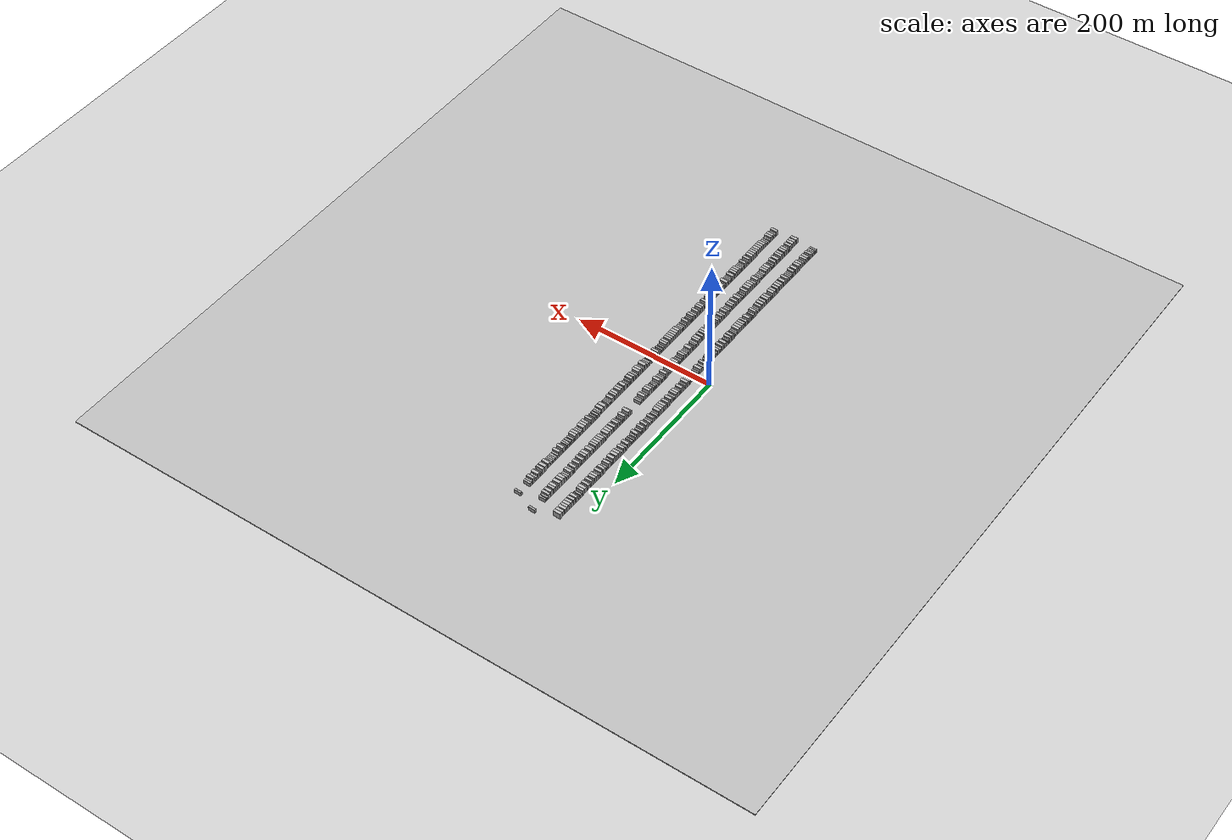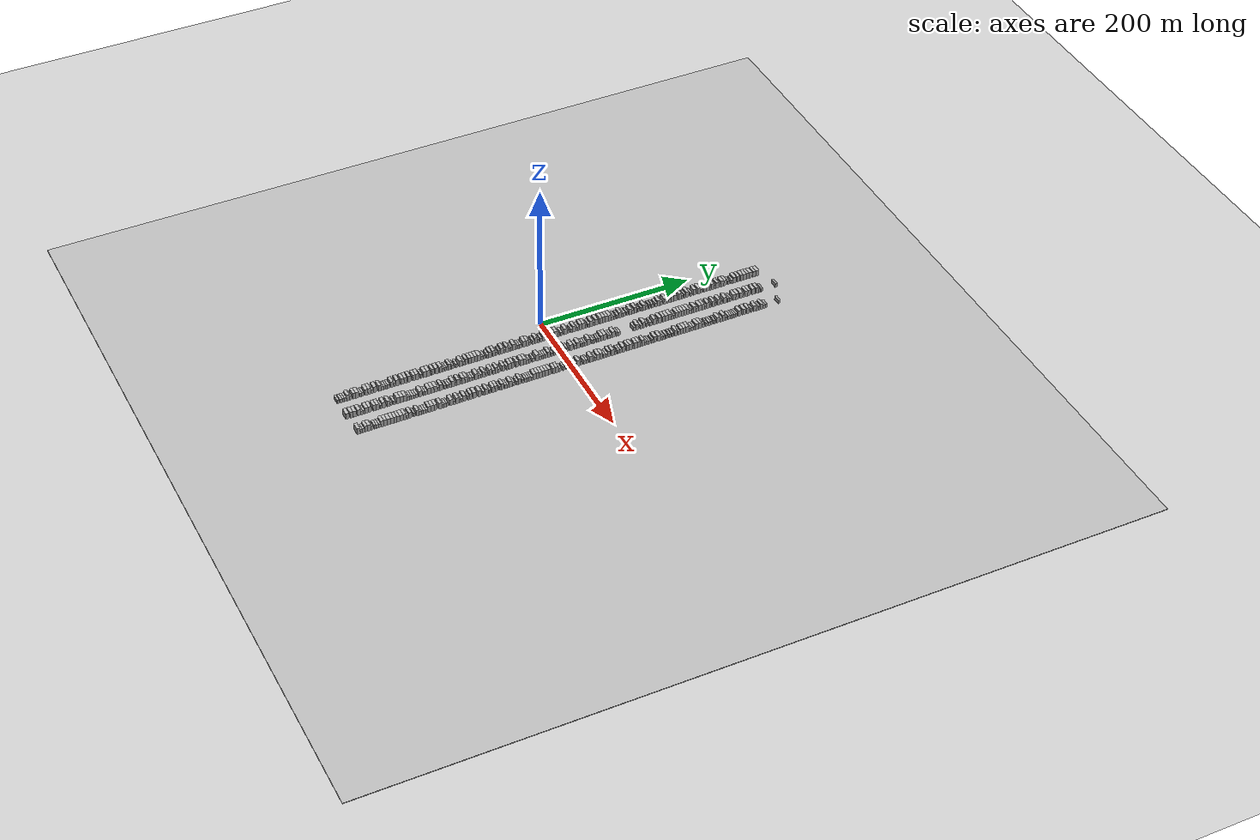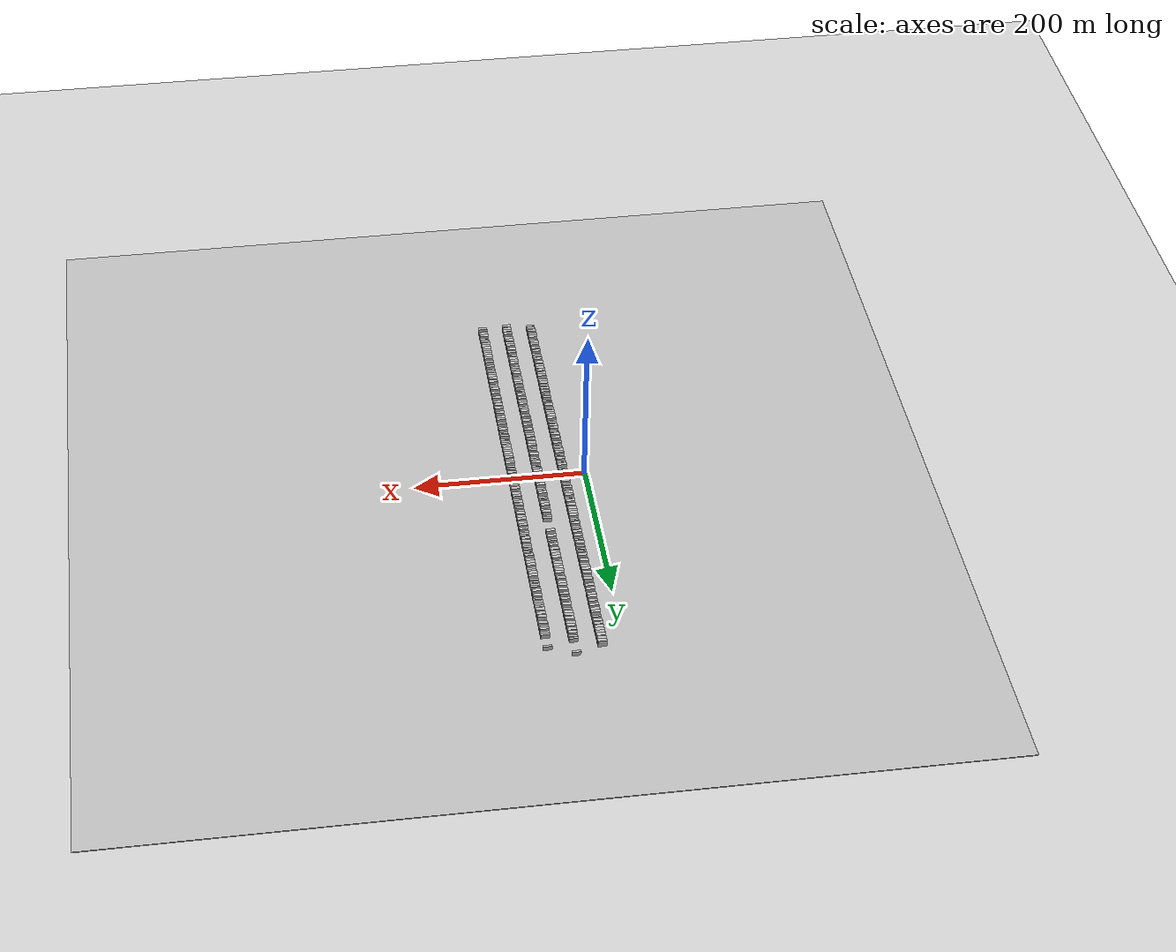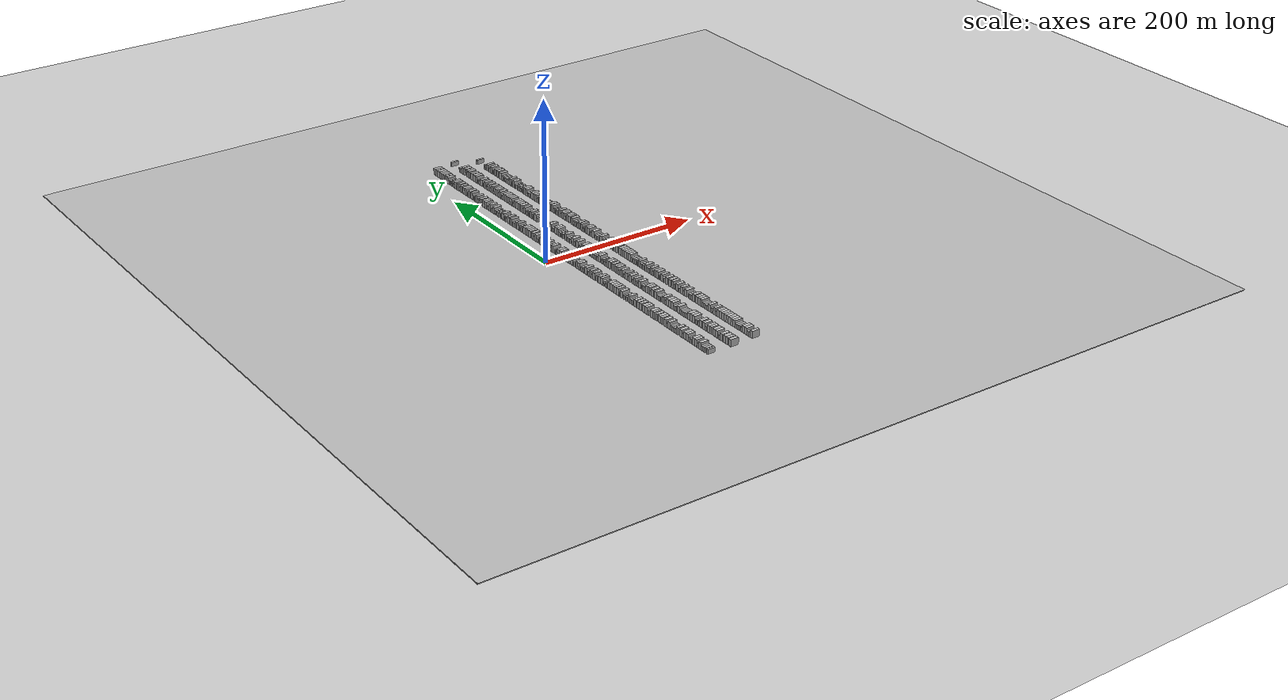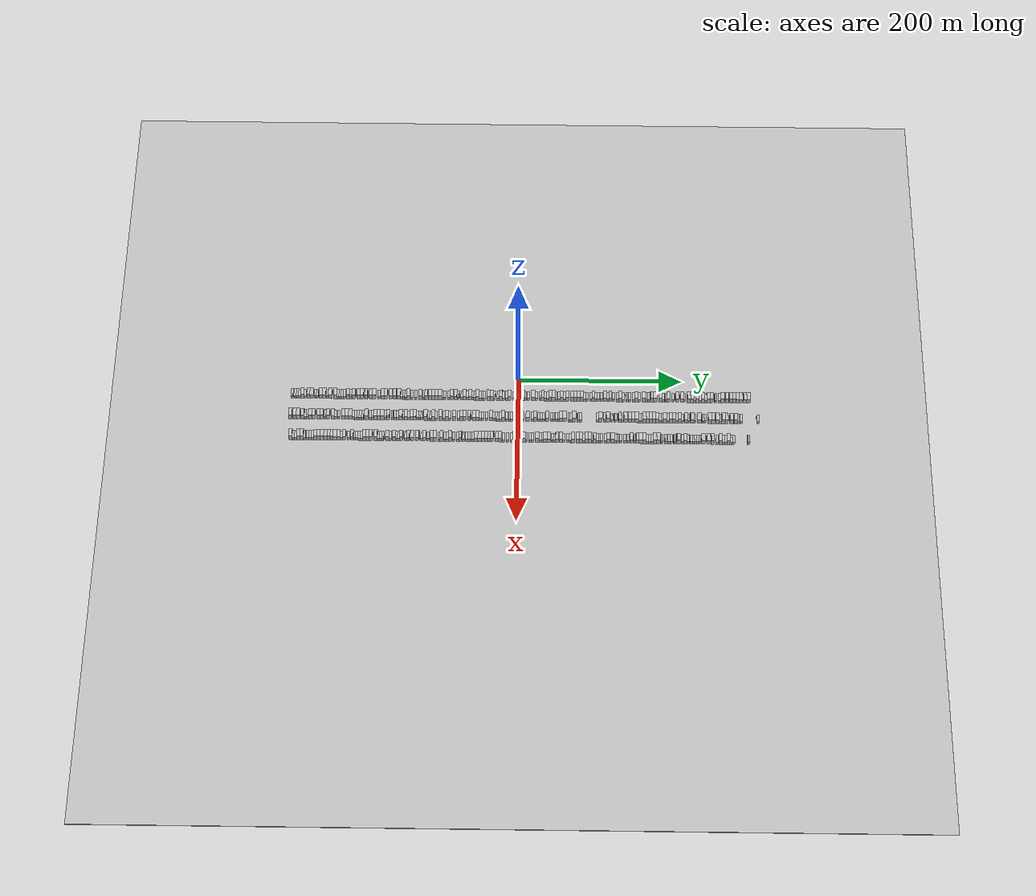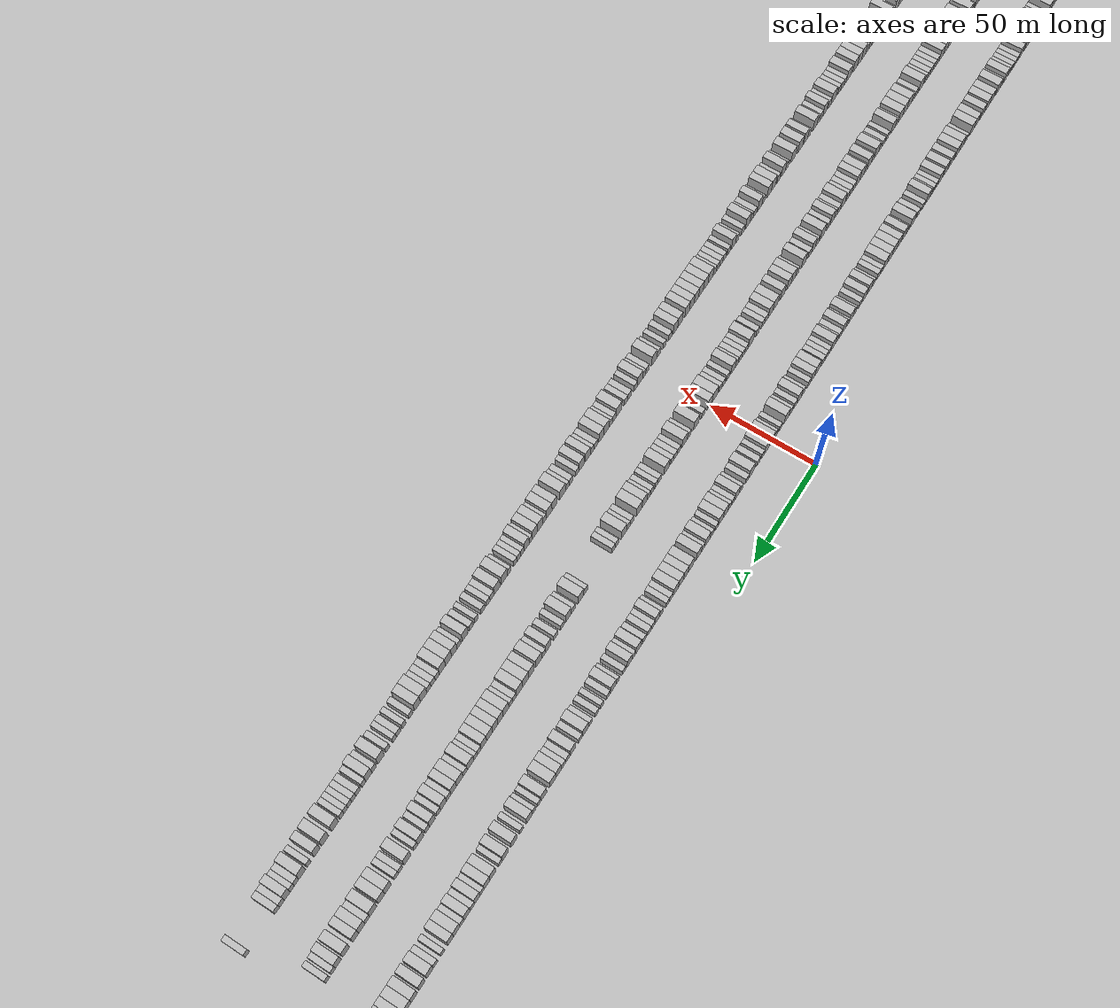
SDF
<?xml version="1.0" encoding="utf-8"?>

<sdf version="1.6">

   <world name="default">

      <gui fullscreen="0">

         <camera name="user_camera">

            <pose>-15 0 4.57585 0 0 0</pose>

            <view_controller>orbit</view_controller>

         </camera>

      </gui>

      <scene>

         <sky>

           <clouds>

             <speed>12</speed>

           </clouds>

         </sky>

         <ambient>0.4 0.4 0.4 1</ambient>

         <background>0.7 0.7 0.7 1</background>

         <shadows>1</shadows>

      </scene>

      <gravity>0 0 -9.8066</gravity>

      <magnetic_field>6e-06 2.3e-05 -4.2e-05</magnetic_field>

      <physics default="0" name="default_physics" type="ode">

         <ode>

            <solver>

               <type>quick</type>

               <iters>10</iters>

               <sor>1.0</sor>

               <use_dynamic_moi_rescaling>0</use_dynamic_moi_rescaling>

            </solver>

            <constraints>

               <cfm>0</cfm>

               <erp>0.2</erp>

               <contact_max_correcting_vel>100</contact_max_correcting_vel>

               <contact_surface_layer>0.001</contact_surface_layer>

            </constraints>

         </ode>

         <max_step_size>0.004</max_step_size>

         <real_time_factor>1</real_time_factor>

         <real_time_update_rate>250</real_time_update_rate>

      </physics>

      <light name="sun" type="directional">

         <cast_shadows>1</cast_shadows>

         <pose>0 0 10 0 0 0</pose>

         <diffuse>0.8 0.8 0.8 1</diffuse>

         <specular>0.2 0.2 0.2 1</specular>

         <attenuation>

            <range>1000</range>

            <constant>0.9</constant>

            <linear>0.01</linear>

            <quadratic>0.001</quadratic>

         </attenuation>

         <direction>-0.5 0.1 -0.9</direction>

      </light>

      <include>

         <name>ground_plane_1</name>

         <uri>model://HANNAS_ground_plane</uri>

         <pose>0 0 0  0 0 0</pose>

      </include>

      <include>

         <name>ground_plane_2</name>

         <uri>model://HANNAS_ground_plane</uri>

         <pose>100 0 0  0 0 0</pose>

      </include>

      <model name="building_1">

         <static>1</static>

         <pose frame="">25.0000 -277.6781 0 0.000000 0.000000 0.000000</pose>

         <link name="link">

            <pose frame="">0 0 3.00 0 0 0</pose>

            <collision name="collision">

               <geometry>

                  <box>

                     <size>10.0000 2.6438 6.0000</size>

                  </box>

               </geometry>

               <max_contacts>10</max_contacts>

               <surface>

                  <contact>

                     <ode/>

                  </contact>

                  <bounce/>

                  <friction>

                     <torsional>

                        <ode/>

                     </torsional>

                     <ode/>

                  </friction>

               </surface>

            </collision>

            <visual name="visual">

               <cast_shadows>0</cast_shadows>

               <geometry>

                  <box>

                     <size>10.0000 2.6438 6.0000</size>

                  </box>

               </geometry>

               <material>

                  <script>

                     <uri>model://HANNAS_wall/materials/scripts</uri>

                     <uri>model://HANNAS_wall/materials/textures</uri>

                     <name>vrc/HANNAS_wall</name>

                  </script>

               </material>

            </visual>

            <self_collide>0</self_collide>

            <enable_wind>0</enable_wind>

            <kinematic>0</kinematic>

         </link>

      </model>

      <model name="building_2">

         <static>1</static>

         <pose frame="">25.0000 -273.9054 0 0.000000 0.000000 0.000000</pose>

         <link name="link">

            <pose frame="">0 0 3.00 0 0 0</pose>

            <collision name="collision">

               <geometry>

                  <box>

                     <size>10.0000 2.9015 6.0000</size>

                  </box>

               </geometry>

               <max_contacts>10</max_contacts>

               <surface>

                  <contact>

                     <ode/>

                  </contact>

                  <bounce/>

                  <friction>

                     <torsional>

                        <ode/>

                     </torsional>

                     <ode/>

                  </friction>

               </surface>

            </collision>

            <visual name="visual">

               <cast_shadows>0</cast_shadows>

               <geometry>

                  <box>

                     <size>10.0000 2.9015 6.0000</size>

                  </box>

               </geometry>

               <material>

                  <script>

                     <uri>model://HANNAS_wall/materials/scripts</uri>

                     <uri>model://HANNAS_wall/materials/textures</uri>

                     <name>vrc/HANNAS_wall</name>

                  </script>

               </material>

            </visual>

            <self_collide>0</self_collide>

            <enable_wind>0</enable_wind>

            <kinematic>0</kinematic>

         </link>

      </model>

      <model name="building_3">

         <static>1</static>

         <pose frame="">25.0000 -271.0770 0 0.000000 0.000000 0.000000</pose>

         <link name="link">

            <pose frame="">0 0 3.00 0 0 0</pose>

            <collision name="collision">

               <geometry>

                  <box>

                     <size>10.0000 2.7553 6.0000</size>

                  </box>

               </geometry>

               <max_contacts>10</max_contacts>

               <surface>

                  <contact>

                     <ode/>

                  </contact>

                  <bounce/>

                  <friction>

                     <torsional>

                        <ode/>

                     </torsional>

                     <ode/>

                  </friction>

               </surface>

            </collision>

            <visual name="visual">

               <cast_shadows>0</cast_shadows>

               <geometry>

                  <box>

                     <size>10.0000 2.7553 6.0000</size>

                  </box>

               </geometry>

               <material>

                  <script>

                     <uri>model://HANNAS_wall/materials/scripts</uri>

                     <uri>model://HANNAS_wall/materials/textures</uri>

                     <name>vrc/HANNAS_wall</name>

                  </script>

               </material>

            </visual>

            <self_collide>0</self_collide>

            <enable_wind>0</enable_wind>

            <kinematic>0</kinematic>

         </link>

      </model>

      <model name="building_4">

         <static>1</static>

         <pose frame="">25.0000 -268.3990 0 0.000000 0.000000 0.000000</pose>

         <link name="link">

            <pose frame="">0 0 3.00 0 0 0</pose>

            <collision name="collision">

               <geometry>

                  <box>

                     <size>10.0000 2.6006 6.0000</size>

                  </box>

               </geometry>

               <max_contacts>10</max_contacts>

               <surface>

                  <contact>

                     <ode/>

                  </contact>

                  <bounce/>

                  <friction>

                     <torsional>

                        <ode/>

                     </torsional>

                     <ode/>

                  </friction>

               </surface>

            </collision>

            <visual name="visual">

               <cast_shadows>0</cast_shadows>

               <geometry>

                  <box>

                     <size>10.0000 2.6006 6.0000</size>

                  </box>

               </geometry>

               <material>

                  <script>

                     <uri>model://HANNAS_wall/materials/scripts</uri>

                     <uri>model://HANNAS_wall/materials/textures</uri>

                     <name>vrc/HANNAS_wall</name>

                  </script>

               </material>

            </visual>

            <self_collide>0</self_collide>

            <enable_wind>0</enable_wind>

            <kinematic>0</kinematic>

         </link>

      </model>

      <model name="building_5">

         <static>1</static>

         <pose frame="">25.0000 -265.1300 0 0.000000 0.000000 0.000000</pose>

         <link name="link">

            <pose frame="">0 0 4.50 0 0 0</pose>

            <collision name="collision">

               <geometry>

                  <box>

                     <size>10.0000 3.9375 9.0000</size>

                  </box>

               </geometry>

               <max_contacts>10</max_contacts>

               <surface>

                  <contact>

                     <ode/>

                  </contact>

                  <bounce/>

                  <friction>

                     <torsional>

                        <ode/>

                     </torsional>

                     <ode/>

                  </friction>

               </surface>

            </collision>

            <visual name="visual">

               <cast_shadows>0</cast_shadows>

               <geometry>

                  <box>

                     <size>10.0000 3.9375 9.0000</size>

                  </box>

               </geometry>

               <material>

                  <script>

                     <uri>model://HANNAS_wall/materials/scripts</uri>

                     <uri>model://HANNAS_wall/materials/textures</uri>

                     <name>vrc/HANNAS_wall</name>

                  </script>

               </material>

            </visual>

            <self_collide>0</self_collide>

            <enable_wind>0</enable_wind>

            <kinematic>0</kinematic>

         </link>

      </model>

      <model name="building_6">

         <static>1</static>

         <pose frame="">25.0000 -261.7340 0 0.000000 0.000000 0.000000</pose>

         <link name="link">

            <pose frame="">0 0 3.00 0 0 0</pose>

            <collision name="collision">

               <geometry>

                  <box>

                     <size>10.0000 2.8546 6.0000</size>

                  </box>

               </geometry>

               <max_contacts>10</max_contacts>

               <surface>

                  <contact>

                     <ode/>

                  </contact>

                  <bounce/>

                  <friction>

                     <torsional>

                        <ode/>

                     </torsional>

                     <ode/>

                  </friction>

               </surface>

            </collision>

            <visual name="visual">

               <cast_shadows>0</cast_shadows>

               <geometry>

                  <box>

                     <size>10.0000 2.8546 6.0000</size>

                  </box>

               </geometry>

               <material>

                  <script>

                     <uri>model://HANNAS_wall/materials/scripts</uri>

                     <uri>model://HANNAS_wall/materials/textures</uri>

                     <name>vrc/HANNAS_wall</name>

                  </script>

               </material>

            </visual>

            <self_collide>0</self_collide>

            <enable_wind>0</enable_wind>

            <kinematic>0</kinematic>

         </link>

      </model>

      <model name="building_7">

         <static>1</static>

         <pose frame="">25.0000 -257.4243 0 0.000000 0.000000 0.000000</pose>

         <link name="link">

            <pose frame="">0 0 4.50 0 0 0</pose>

            <collision name="collision">

               <geometry>

                  <box>

                     <size>10.0000 3.7646 9.0000</size>

                  </box>

               </geometry>

               <max_contacts>10</max_contacts>

               <surface>

                  <contact>

                     <ode/>

                  </contact>

                  <bounce/>

                  <friction>

                     <torsional>

                        <ode/>

                     </torsional>

                     <ode/>

                  </friction>

               </surface>

            </collision>

            <visual name="visual">

               <cast_shadows>0</cast_shadows>

               <geometry>

                  <box>

                     <size>10.0000 3.7646 9.0000</size>

                  </box>

               </geometry>

               <material>

                  <script>

                     <uri>model://HANNAS_wall/materials/scripts</uri>

                     <uri>model://HANNAS_wall/materials/textures</uri>

                     <name>vrc/HANNAS_wall</name>

                  </script>

               </material>

            </visual>

            <self_collide>0</self_collide>

            <enable_wind>0</enable_wind>

            <kinematic>0</kinematic>

         </link>

      </model>

      <model name="building_8">

         <static>1</static>

         <pose frame="">25.0000 -253.4017 0 0.000000 0.000000 0.000000</pose>

         <link name="link">

            <pose frame="">0 0 4.50 0 0 0</pose>

            <collision name="collision">

               <geometry>

                  <box>

                     <size>10.0000 4.2806 9.0000</size>

                  </box>

               </geometry>

               <max_contacts>10</max_contacts>

               <surface>

                  <contact>

                     <ode/>

                  </contact>

                  <bounce/>

                  <friction>

                     <torsional>

                        <ode/>

                     </torsional>

                     <ode/>

                  </friction>

               </surface>

            </collision>

            <visual name="visual">

               <cast_shadows>0</cast_shadows>

               <geometry>

                  <box>

                     <size>10.0000 4.2806 9.0000</size>

                  </box>

               </geometry>

               <material>

                  <script>

                     <uri>model://HANNAS_wall/materials/scripts</uri>

                     <uri>model://HANNAS_wall/materials/textures</uri>

                     <name>vrc/HANNAS_wall</name>

                  </script>

               </material>

            </visual>

            <self_collide>0</self_collide>

            <enable_wind>0</enable_wind>

            <kinematic>0</kinematic>

         </link>

      </model>

      <model name="building_9">

         <static>1</static>

         <pose frame="">25.0000 -249.0257 0 0.000000 0.000000 0.000000</pose>

         <link name="link">

            <pose frame="">0 0 3.00 0 0 0</pose>

            <collision name="collision">

               <geometry>

                  <box>

                     <size>10.0000 2.4715 6.0000</size>

                  </box>

               </geometry>

               <max_contacts>10</max_contacts>

               <surface>

                  <contact>

                     <ode/>

                  </contact>

                  <bounce/>

                  <friction>

                     <torsional>

                        <ode/>

                     </torsional>

                     <ode/>

                  </friction>

               </surface>

            </collision>

            <visual name="visual">

               <cast_shadows>0</cast_shadows>

               <geometry>

                  <box>

                     <size>10.0000 2.4715 6.0000</size>

                  </box>

               </geometry>

               <material>

                  <script>

                     <uri>model://HANNAS_wall/materials/scripts</uri>

                     <uri>model://HANNAS_wall/materials/textures</uri>

                     <name>vrc/HANNAS_wall</name>

                  </script>

               </material>

            </visual>

            <self_collide>0</self_collide>

            <enable_wind>0</enable_wind>

            <kinematic>0</kinematic>

         </link>

      </model>

      <model name="building_10">

         <static>1</static>

         <pose frame="">25.0000 -246.4286 0 0.000000 0.000000 0.000000</pose>

         <link name="link">

            <pose frame="">0 0 3.00 0 0 0</pose>

            <collision name="collision">

               <geometry>

                  <box>

                     <size>10.0000 2.7227 6.0000</size>

                  </box>

               </geometry>

               <max_contacts>10</max_contacts>

               <surface>

                  <contact>

                     <ode/>

                  </contact>

                  <bounce/>

                  <friction>

                     <torsional>

                        <ode/>

                     </torsional>

                     <ode/>

                  </friction>

               </surface>

            </collision>

            <visual name="visual">

               <cast_shadows>0</cast_shadows>

               <geometry>

                  <box>

                     <size>10.0000 2.7227 6.0000</size>

                  </box>

               </geometry>

               <material>

                  <script>

                     <uri>model://HANNAS_wall/materials/scripts</uri>

                     <uri>model://HANNAS_wall/materials/textures</uri>

                     <name>vrc/HANNAS_wall</name>

                  </script>

               </material>

            </visual>

            <self_collide>0</self_collide>

            <enable_wind>0</enable_wind>

            <kinematic>0</kinematic>

         </link>

      </model>

      <model name="building_11">

         <static>1</static>

         <pose frame="">25.0000 -242.0213 0 0.000000 0.000000 0.000000</pose>

         <link name="link">

            <pose frame="">0 0 4.50 0 0 0</pose>

            <collision name="collision">

               <geometry>

                  <box>

                     <size>10.0000 4.0918 9.0000</size>

                  </box>

               </geometry>

               <max_contacts>10</max_contacts>

               <surface>

                  <contact>

                     <ode/>

                  </contact>

                  <bounce/>

                  <friction>

                     <torsional>

                        <ode/>

                     </torsional>

                     <ode/>

                  </friction>

               </surface>

            </collision>

            <visual name="visual">

               <cast_shadows>0</cast_shadows>

               <geometry>

                  <box>

                     <size>10.0000 4.0918 9.0000</size>

                  </box>

               </geometry>

               <material>

                  <script>

                     <uri>model://HANNAS_wall/materials/scripts</uri>

                     <uri>model://HANNAS_wall/materials/textures</uri>

                     <name>vrc/HANNAS_wall</name>

                  </script>

               </material>

            </visual>

            <self_collide>0</self_collide>

            <enable_wind>0</enable_wind>

            <kinematic>0</kinematic>

         </link>

      </model>

      <model name="building_12">

         <static>1</static>

         <pose frame="">25.0000 -237.9267 0 0.000000 0.000000 0.000000</pose>

         <link name="link">

            <pose frame="">0 0 4.50 0 0 0</pose>

            <collision name="collision">

               <geometry>

                  <box>

                     <size>10.0000 4.0975 9.0000</size>

                  </box>

               </geometry>

               <max_contacts>10</max_contacts>

               <surface>

                  <contact>

                     <ode/>

                  </contact>

                  <bounce/>

                  <friction>

                     <torsional>

                        <ode/>

                     </torsional>

                     <ode/>

                  </friction>

               </surface>

            </collision>

            <visual name="visual">

               <cast_shadows>0</cast_shadows>

               <geometry>

                  <box>

                     <size>10.0000 4.0975 9.0000</size>

                  </box>

               </geometry>

               <material>

                  <script>

                     <uri>model://HANNAS_wall/materials/scripts</uri>

                     <uri>model://HANNAS_wall/materials/textures</uri>

                     <name>vrc/HANNAS_wall</name>

                  </script>

               </material>

            </visual>

            <self_collide>0</self_collide>

            <enable_wind>0</enable_wind>

            <kinematic>0</kinematic>

         </link>

      </model>

      <model name="building_13">

         <static>1</static>

         <pose frame="">25.0000 -234.3862 0 0.000000 0.000000 0.000000</pose>

         <link name="link">

            <pose frame="">0 0 3.00 0 0 0</pose>

            <collision name="collision">

               <geometry>

                  <box>

                     <size>10.0000 2.9835 6.0000</size>

                  </box>

               </geometry>

               <max_contacts>10</max_contacts>

               <surface>

                  <contact>

                     <ode/>

                  </contact>

                  <bounce/>

                  <friction>

                     <torsional>

                        <ode/>

                     </torsional>

                     <ode/>

                  </friction>

               </surface>

            </collision>

            <visual name="visual">

               <cast_shadows>0</cast_shadows>

               <geometry>

                  <box>

                     <size>10.0000 2.9835 6.0000</size>

                  </box>

               </geometry>

               <material>

                  <script>

                     <uri>model://HANNAS_wall/materials/scripts</uri>

                     <uri>model://HANNAS_wall/materials/textures</uri>

                     <name>vrc/HANNAS_wall</name>

                  </script>

               </material>

            </visual>

            <self_collide>0</self_collide>

            <enable_wind>0</enable_wind>

            <kinematic>0</kinematic>

         </link>

      </model>

      <model name="building_14">

         <static>1</static>

         <pose frame="">25.0000 -230.6913 0 0.000000 0.000000 0.000000</pose>

         <link name="link">

            <pose frame="">0 0 4.50 0 0 0</pose>

            <collision name="collision">

               <geometry>

                  <box>

                     <size>10.0000 4.4063 9.0000</size>

                  </box>

               </geometry>

               <max_contacts>10</max_contacts>

               <surface>

                  <contact>

                     <ode/>

                  </contact>

                  <bounce/>

                  <friction>

                     <torsional>

                        <ode/>

                     </torsional>

                     <ode/>

                  </friction>

               </surface>

            </collision>

            <visual name="visual">

               <cast_shadows>0</cast_shadows>

               <geometry>

                  <box>

                     <size>10.0000 4.4063 9.0000</size>

                  </box>

               </geometry>

               <material>

                  <script>

                     <uri>model://HANNAS_wall/materials/scripts</uri>

                     <uri>model://HANNAS_wall/materials/textures</uri>

                     <name>vrc/HANNAS_wall</name>

                  </script>

               </material>

            </visual>

            <self_collide>0</self_collide>

            <enable_wind>0</enable_wind>

            <kinematic>0</kinematic>

         </link>

      </model>

      <model name="building_15">

         <static>1</static>

         <pose frame="">25.0000 -224.6204 0 0.000000 0.000000 0.000000</pose>

         <link name="link">

            <pose frame="">0 0 4.50 0 0 0</pose>

            <collision name="collision">

               <geometry>

                  <box>

                     <size>10.0000 3.7354 9.0000</size>

                  </box>

               </geometry>

               <max_contacts>10</max_contacts>

               <surface>

                  <contact>

                     <ode/>

                  </contact>

                  <bounce/>

                  <friction>

                     <torsional>

                        <ode/>

                     </torsional>

                     <ode/>

                  </friction>

               </surface>

            </collision>

            <visual name="visual">

               <cast_shadows>0</cast_shadows>

               <geometry>

                  <box>

                     <size>10.0000 3.7354 9.0000</size>

                  </box>

               </geometry>

               <material>

                  <script>

                     <uri>model://HANNAS_wall/materials/scripts</uri>

                     <uri>model://HANNAS_wall/materials/textures</uri>

                     <name>vrc/HANNAS_wall</name>

                  </script>

               </material>

            </visual>

            <self_collide>0</self_collide>

            <enable_wind>0</enable_wind>

            <kinematic>0</kinematic>

         </link>

      </model>

      <model name="building_16">

         <static>1</static>

         <pose frame="">25.0000 -221.4481 0 0.000000 0.000000 0.000000</pose>

         <link name="link">

            <pose frame="">0 0 3.00 0 0 0</pose>

            <collision name="collision">

               <geometry>

                  <box>

                     <size>10.0000 2.6093 6.0000</size>

                  </box>

               </geometry>

               <max_contacts>10</max_contacts>

               <surface>

                  <contact>

                     <ode/>

                  </contact>

                  <bounce/>

                  <friction>

                     <torsional>

                        <ode/>

                     </torsional>

                     <ode/>

                  </friction>

               </surface>

            </collision>

            <visual name="visual">

               <cast_shadows>0</cast_shadows>

               <geometry>

                  <box>

                     <size>10.0000 2.6093 6.0000</size>

                  </box>

               </geometry>

               <material>

                  <script>

                     <uri>model://HANNAS_wall/materials/scripts</uri>

                     <uri>model://HANNAS_wall/materials/textures</uri>

                     <name>vrc/HANNAS_wall</name>

                  </script>

               </material>

            </visual>

            <self_collide>0</self_collide>

            <enable_wind>0</enable_wind>

            <kinematic>0</kinematic>

         </link>

      </model>

      <model name="building_17">

         <static>1</static>

         <pose frame="">25.0000 -218.7706 0 0.000000 0.000000 0.000000</pose>

         <link name="link">

            <pose frame="">0 0 3.00 0 0 0</pose>

            <collision name="collision">

               <geometry>

                  <box>

                     <size>10.0000 2.7456 6.0000</size>

                  </box>

               </geometry>

               <max_contacts>10</max_contacts>

               <surface>

                  <contact>

                     <ode/>

                  </contact>

                  <bounce/>

                  <friction>

                     <torsional>

                        <ode/>

                     </torsional>

                     <ode/>

                  </friction>

               </surface>

            </collision>

            <visual name="visual">

               <cast_shadows>0</cast_shadows>

               <geometry>

                  <box>

                     <size>10.0000 2.7456 6.0000</size>

                  </box>

               </geometry>

               <material>

                  <script>

                     <uri>model://HANNAS_wall/materials/scripts</uri>

                     <uri>model://HANNAS_wall/materials/textures</uri>

                     <name>vrc/HANNAS_wall</name>

                  </script>

               </material>

            </visual>

            <self_collide>0</self_collide>

            <enable_wind>0</enable_wind>

            <kinematic>0</kinematic>

         </link>

      </model>

      <model name="building_18">

         <static>1</static>

         <pose frame="">25.0000 -216.1740 0 0.000000 0.000000 0.000000</pose>

         <link name="link">

            <pose frame="">0 0 3.00 0 0 0</pose>

            <collision name="collision">

               <geometry>

                  <box>

                     <size>10.0000 2.4477 6.0000</size>

                  </box>

               </geometry>

               <max_contacts>10</max_contacts>

               <surface>

                  <contact>

                     <ode/>

                  </contact>

                  <bounce/>

                  <friction>

                     <torsional>

                        <ode/>

                     </torsional>

                     <ode/>

                  </friction>

               </surface>

            </collision>

            <visual name="visual">

               <cast_shadows>0</cast_shadows>

               <geometry>

                  <box>

                     <size>10.0000 2.4477 6.0000</size>

                  </box>

               </geometry>

               <material>

                  <script>

                     <uri>model://HANNAS_wall/materials/scripts</uri>

                     <uri>model://HANNAS_wall/materials/textures</uri>

                     <name>vrc/HANNAS_wall</name>

                  </script>

               </material>

            </visual>

            <self_collide>0</self_collide>

            <enable_wind>0</enable_wind>

            <kinematic>0</kinematic>

         </link>

      </model>

      <model name="building_19">

         <static>1</static>

         <pose frame="">25.0000 -213.4519 0 0.000000 0.000000 0.000000</pose>

         <link name="link">

            <pose frame="">0 0 3.00 0 0 0</pose>

            <collision name="collision">

               <geometry>

                  <box>

                     <size>10.0000 2.9965 6.0000</size>

                  </box>

               </geometry>

               <max_contacts>10</max_contacts>

               <surface>

                  <contact>

                     <ode/>

                  </contact>

                  <bounce/>

                  <friction>

                     <torsional>

                        <ode/>

                     </torsional>

                     <ode/>

                  </friction>

               </surface>

            </collision>

            <visual name="visual">

               <cast_shadows>0</cast_shadows>

               <geometry>

                  <box>

                     <size>10.0000 2.9965 6.0000</size>

                  </box>

               </geometry>

               <material>

                  <script>

                     <uri>model://HANNAS_wall/materials/scripts</uri>

                     <uri>model://HANNAS_wall/materials/textures</uri>

                     <name>vrc/HANNAS_wall</name>

                  </script>

               </material>

            </visual>

            <self_collide>0</self_collide>

            <enable_wind>0</enable_wind>

            <kinematic>0</kinematic>

         </link>

      </model>

      <model name="building_20">

         <static>1</static>

         <pose frame="">25.0000 -209.0284 0 0.000000 0.000000 0.000000</pose>

         <link name="link">

            <pose frame="">0 0 4.50 0 0 0</pose>

            <collision name="collision">

               <geometry>

                  <box>

                     <size>10.0000 3.8504 9.0000</size>

                  </box>

               </geometry>

               <max_contacts>10</max_contacts>

               <surface>

                  <contact>

                     <ode/>

                  </contact>

                  <bounce/>

                  <friction>

                     <torsional>

                        <ode/>

                     </torsional>

                     <ode/>

                  </friction>

               </surface>

            </collision>

            <visual name="visual">

               <cast_shadows>0</cast_shadows>

               <geometry>

                  <box>

                     <size>10.0000 3.8504 9.0000</size>

                  </box>

               </geometry>

               <material>

                  <script>

                     <uri>model://HANNAS_wall/materials/scripts</uri>

                     <uri>model://HANNAS_wall/materials/textures</uri>

                     <name>vrc/HANNAS_wall</name>

                  </script>

               </material>

            </visual>

            <self_collide>0</self_collide>

            <enable_wind>0</enable_wind>

            <kinematic>0</kinematic>

         </link>

      </model>

      <model name="building_21">

         <static>1</static>

         <pose frame="">25.0000 -205.6199 0 0.000000 0.000000 0.000000</pose>

         <link name="link">

            <pose frame="">0 0 3.00 0 0 0</pose>

            <collision name="collision">

               <geometry>

                  <box>

                     <size>10.0000 2.9667 6.0000</size>

                  </box>

               </geometry>

               <max_contacts>10</max_contacts>

               <surface>

                  <contact>

                     <ode/>

                  </contact>

                  <bounce/>

                  <friction>

                     <torsional>

                        <ode/>

                     </torsional>

                     <ode/>

                  </friction>

               </surface>

            </collision>

            <visual name="visual">

               <cast_shadows>0</cast_shadows>

               <geometry>

                  <box>

                     <size>10.0000 2.9667 6.0000</size>

                  </box>

               </geometry>

               <material>

                  <script>

                     <uri>model://HANNAS_wall/materials/scripts</uri>

                     <uri>model://HANNAS_wall/materials/textures</uri>

                     <name>vrc/HANNAS_wall</name>

                  </script>

               </material>

            </visual>

            <self_collide>0</self_collide>

            <enable_wind>0</enable_wind>

            <kinematic>0</kinematic>

         </link>

      </model>

      <model name="building_22">

         <static>1</static>

         <pose frame="">25.0000 -201.9201 0 0.000000 0.000000 0.000000</pose>

         <link name="link">

            <pose frame="">0 0 4.50 0 0 0</pose>

            <collision name="collision">

               <geometry>

                  <box>

                     <size>10.0000 4.4330 9.0000</size>

                  </box>

               </geometry>

               <max_contacts>10</max_contacts>

               <surface>

                  <contact>

                     <ode/>

                  </contact>

                  <bounce/>

                  <friction>

                     <torsional>

                        <ode/>

                     </torsional>

                     <ode/>

                  </friction>

               </surface>

            </collision>

            <visual name="visual">

               <cast_shadows>0</cast_shadows>

               <geometry>

                  <box>

                     <size>10.0000 4.4330 9.0000</size>

                  </box>

               </geometry>

               <material>

                  <script>

                     <uri>model://HANNAS_wall/materials/scripts</uri>

                     <uri>model://HANNAS_wall/materials/textures</uri>

                     <name>vrc/HANNAS_wall</name>

                  </script>

               </material>

            </visual>

            <self_collide>0</self_collide>

            <enable_wind>0</enable_wind>

            <kinematic>0</kinematic>

         </link>

      </model>

      <model name="building_23">

         <static>1</static>

         <pose frame="">25.0000 -195.7237 0 0.000000 0.000000 0.000000</pose>

         <link name="link">

            <pose frame="">0 0 4.50 0 0 0</pose>

            <collision name="collision">

               <geometry>

                  <box>

                     <size>10.0000 3.9597 9.0000</size>

                  </box>

               </geometry>

               <max_contacts>10</max_contacts>

               <surface>

                  <contact>

                     <ode/>

                  </contact>

                  <bounce/>

                  <friction>

                     <torsional>

                        <ode/>

                     </torsional>

                     <ode/>

                  </friction>

               </surface>

            </collision>

            <visual name="visual">

               <cast_shadows>0</cast_shadows>

               <geometry>

                  <box>

                     <size>10.0000 3.9597 9.0000</size>

                  </box>

               </geometry>

               <material>

                  <script>

                     <uri>model://HANNAS_wall/materials/scripts</uri>

                     <uri>model://HANNAS_wall/materials/textures</uri>

                     <name>vrc/HANNAS_wall</name>

                  </script>

               </material>

            </visual>

            <self_collide>0</self_collide>

            <enable_wind>0</enable_wind>

            <kinematic>0</kinematic>

         </link>

      </model>

      <model name="building_24">

         <static>1</static>

         <pose frame="">25.0000 -191.6149 0 0.000000 0.000000 0.000000</pose>

         <link name="link">

            <pose frame="">0 0 4.50 0 0 0</pose>

            <collision name="collision">

               <geometry>

                  <box>

                     <size>10.0000 4.2580 9.0000</size>

                  </box>

               </geometry>

               <max_contacts>10</max_contacts>

               <surface>

                  <contact>

                     <ode/>

                  </contact>

                  <bounce/>

                  <friction>

                     <torsional>

                        <ode/>

                     </torsional>

                     <ode/>

                  </friction>

               </surface>

            </collision>

            <visual name="visual">

               <cast_shadows>0</cast_shadows>

               <geometry>

                  <box>

                     <size>10.0000 4.2580 9.0000</size>

                  </box>

               </geometry>

               <material>

                  <script>

                     <uri>model://HANNAS_wall/materials/scripts</uri>

                     <uri>model://HANNAS_wall/materials/textures</uri>

                     <name>vrc/HANNAS_wall</name>

                  </script>

               </material>

            </visual>

            <self_collide>0</self_collide>

            <enable_wind>0</enable_wind>

            <kinematic>0</kinematic>

         </link>

      </model>

      <model name="building_25">

         <static>1</static>

         <pose frame="">25.0000 -186.5937 0 0.000000 0.000000 0.000000</pose>

         <link name="link">

            <pose frame="">0 0 4.50 0 0 0</pose>

            <collision name="collision">

               <geometry>

                  <box>

                     <size>10.0000 3.7844 9.0000</size>

                  </box>

               </geometry>

               <max_contacts>10</max_contacts>

               <surface>

                  <contact>

                     <ode/>

                  </contact>

                  <bounce/>

                  <friction>

                     <torsional>

                        <ode/>

                     </torsional>

                     <ode/>

                  </friction>

               </surface>

            </collision>

            <visual name="visual">

               <cast_shadows>0</cast_shadows>

               <geometry>

                  <box>

                     <size>10.0000 3.7844 9.0000</size>

                  </box>

               </geometry>

               <material>

                  <script>

                     <uri>model://HANNAS_wall/materials/scripts</uri>

                     <uri>model://HANNAS_wall/materials/textures</uri>

                     <name>vrc/HANNAS_wall</name>

                  </script>

               </material>

            </visual>

            <self_collide>0</self_collide>

            <enable_wind>0</enable_wind>

            <kinematic>0</kinematic>

         </link>

      </model>

      <model name="building_26">

         <static>1</static>

         <pose frame="">25.0000 -180.8033 0 0.000000 0.000000 0.000000</pose>

         <link name="link">

            <pose frame="">0 0 4.50 0 0 0</pose>

            <collision name="collision">

               <geometry>

                  <box>

                     <size>10.0000 3.7964 9.0000</size>

                  </box>

               </geometry>

               <max_contacts>10</max_contacts>

               <surface>

                  <contact>

                     <ode/>

                  </contact>

                  <bounce/>

                  <friction>

                     <torsional>

                        <ode/>

                     </torsional>

                     <ode/>

                  </friction>

               </surface>

            </collision>

            <visual name="visual">

               <cast_shadows>0</cast_shadows>

               <geometry>

                  <box>

                     <size>10.0000 3.7964 9.0000</size>

                  </box>

               </geometry>

               <material>

                  <script>

                     <uri>model://HANNAS_wall/materials/scripts</uri>

                     <uri>model://HANNAS_wall/materials/textures</uri>

                     <name>vrc/HANNAS_wall</name>

                  </script>

               </material>

            </visual>

            <self_collide>0</self_collide>

            <enable_wind>0</enable_wind>

            <kinematic>0</kinematic>

         </link>

      </model>

      <model name="building_27">

         <static>1</static>

         <pose frame="">25.0000 -176.7418 0 0.000000 0.000000 0.000000</pose>

         <link name="link">

            <pose frame="">0 0 4.50 0 0 0</pose>

            <collision name="collision">

               <geometry>

                  <box>

                     <size>10.0000 4.3265 9.0000</size>

                  </box>

               </geometry>

               <max_contacts>10</max_contacts>

               <surface>

                  <contact>

                     <ode/>

                  </contact>

                  <bounce/>

                  <friction>

                     <torsional>

                        <ode/>

                     </torsional>

                     <ode/>

                  </friction>

               </surface>

            </collision>

            <visual name="visual">

               <cast_shadows>0</cast_shadows>

               <geometry>

                  <box>

                     <size>10.0000 4.3265 9.0000</size>

                  </box>

               </geometry>

               <material>

                  <script>

                     <uri>model://HANNAS_wall/materials/scripts</uri>

                     <uri>model://HANNAS_wall/materials/textures</uri>

                     <name>vrc/HANNAS_wall</name>

                  </script>

               </material>

            </visual>

            <self_collide>0</self_collide>

            <enable_wind>0</enable_wind>

            <kinematic>0</kinematic>

         </link>

      </model>

      <model name="building_28">

         <static>1</static>

         <pose frame="">25.0000 -171.1275 0 0.000000 0.000000 0.000000</pose>

         <link name="link">

            <pose frame="">0 0 3.00 0 0 0</pose>

            <collision name="collision">

               <geometry>

                  <box>

                     <size>10.0000 2.9022 6.0000</size>

                  </box>

               </geometry>

               <max_contacts>10</max_contacts>

               <surface>

                  <contact>

                     <ode/>

                  </contact>

                  <bounce/>

                  <friction>

                     <torsional>

                        <ode/>

                     </torsional>

                     <ode/>

                  </friction>

               </surface>

            </collision>

            <visual name="visual">

               <cast_shadows>0</cast_shadows>

               <geometry>

                  <box>

                     <size>10.0000 2.9022 6.0000</size>

                  </box>

               </geometry>

               <material>

                  <script>

                     <uri>model://HANNAS_wall/materials/scripts</uri>

                     <uri>model://HANNAS_wall/materials/textures</uri>

                     <name>vrc/HANNAS_wall</name>

                  </script>

               </material>

            </visual>

            <self_collide>0</self_collide>

            <enable_wind>0</enable_wind>

            <kinematic>0</kinematic>

         </link>

      </model>

      <model name="building_29">

         <static>1</static>

         <pose frame="">25.0000 -166.6562 0 0.000000 0.000000 0.000000</pose>

         <link name="link">

            <pose frame="">0 0 4.50 0 0 0</pose>

            <collision name="collision">

               <geometry>

                  <box>

                     <size>10.0000 4.0403 9.0000</size>

                  </box>

               </geometry>

               <max_contacts>10</max_contacts>

               <surface>

                  <contact>

                     <ode/>

                  </contact>

                  <bounce/>

                  <friction>

                     <torsional>

                        <ode/>

                     </torsional>

                     <ode/>

                  </friction>

               </surface>

            </collision>

            <visual name="visual">

               <cast_shadows>0</cast_shadows>

               <geometry>

                  <box>

                     <size>10.0000 4.0403 9.0000</size>

                  </box>

               </geometry>

               <material>

                  <script>

                     <uri>model://HANNAS_wall/materials/scripts</uri>

                     <uri>model://HANNAS_wall/materials/textures</uri>

                     <name>vrc/HANNAS_wall</name>

                  </script>

               </material>

            </visual>

            <self_collide>0</self_collide>

            <enable_wind>0</enable_wind>

            <kinematic>0</kinematic>

         </link>

      </model>

      <model name="building_30">

         <static>1</static>

         <pose frame="">25.0000 -162.4796 0 0.000000 0.000000 0.000000</pose>

         <link name="link">

            <pose frame="">0 0 4.50 0 0 0</pose>

            <collision name="collision">

               <geometry>

                  <box>

                     <size>10.0000 4.3129 9.0000</size>

                  </box>

               </geometry>

               <max_contacts>10</max_contacts>

               <surface>

                  <contact>

                     <ode/>

                  </contact>

                  <bounce/>

                  <friction>

                     <torsional>

                        <ode/>

                     </torsional>

                     <ode/>

                  </friction>

               </surface>

            </collision>

            <visual name="visual">

               <cast_shadows>0</cast_shadows>

               <geometry>

                  <box>

                     <size>10.0000 4.3129 9.0000</size>

                  </box>

               </geometry>

               <material>

                  <script>

                     <uri>model://HANNAS_wall/materials/scripts</uri>

                     <uri>model://HANNAS_wall/materials/textures</uri>

                     <name>vrc/HANNAS_wall</name>

                  </script>

               </material>

            </visual>

            <self_collide>0</self_collide>

            <enable_wind>0</enable_wind>

            <kinematic>0</kinematic>

         </link>

      </model>

      <model name="building_31">

         <static>1</static>

         <pose frame="">25.0000 -156.4669 0 0.000000 0.000000 0.000000</pose>

         <link name="link">

            <pose frame="">0 0 4.50 0 0 0</pose>

            <collision name="collision">

               <geometry>

                  <box>

                     <size>10.0000 3.7126 9.0000</size>

                  </box>

               </geometry>

               <max_contacts>10</max_contacts>

               <surface>

                  <contact>

                     <ode/>

                  </contact>

                  <bounce/>

                  <friction>

                     <torsional>

                        <ode/>

                     </torsional>

                     <ode/>

                  </friction>

               </surface>

            </collision>

            <visual name="visual">

               <cast_shadows>0</cast_shadows>

               <geometry>

                  <box>

                     <size>10.0000 3.7126 9.0000</size>

                  </box>

               </geometry>

               <material>

                  <script>

                     <uri>model://HANNAS_wall/materials/scripts</uri>

                     <uri>model://HANNAS_wall/materials/textures</uri>

                     <name>vrc/HANNAS_wall</name>

                  </script>

               </material>

            </visual>

            <self_collide>0</self_collide>

            <enable_wind>0</enable_wind>

            <kinematic>0</kinematic>

         </link>

      </model>

      <model name="building_32">

         <static>1</static>

         <pose frame="">25.0000 -151.4702 0 0.000000 0.000000 0.000000</pose>

         <link name="link">

            <pose frame="">0 0 4.50 0 0 0</pose>

            <collision name="collision">

               <geometry>

                  <box>

                     <size>10.0000 4.2809 9.0000</size>

                  </box>

               </geometry>

               <max_contacts>10</max_contacts>

               <surface>

                  <contact>

                     <ode/>

                  </contact>

                  <bounce/>

                  <friction>

                     <torsional>

                        <ode/>

                     </torsional>

                     <ode/>

                  </friction>

               </surface>

            </collision>

            <visual name="visual">

               <cast_shadows>0</cast_shadows>

               <geometry>

                  <box>

                     <size>10.0000 4.2809 9.0000</size>

                  </box>

               </geometry>

               <material>

                  <script>

                     <uri>model://HANNAS_wall/materials/scripts</uri>

                     <uri>model://HANNAS_wall/materials/textures</uri>

                     <name>vrc/HANNAS_wall</name>

                  </script>

               </material>

            </visual>

            <self_collide>0</self_collide>

            <enable_wind>0</enable_wind>

            <kinematic>0</kinematic>

         </link>

      </model>

      <model name="building_33">

         <static>1</static>

         <pose frame="">25.0000 -146.2983 0 0.000000 0.000000 0.000000</pose>

         <link name="link">

            <pose frame="">0 0 4.50 0 0 0</pose>

            <collision name="collision">

               <geometry>

                  <box>

                     <size>10.0000 4.0628 9.0000</size>

                  </box>

               </geometry>

               <max_contacts>10</max_contacts>

               <surface>

                  <contact>

                     <ode/>

                  </contact>

                  <bounce/>

                  <friction>

                     <torsional>

                        <ode/>

                     </torsional>

                     <ode/>

                  </friction>

               </surface>

            </collision>

            <visual name="visual">

               <cast_shadows>0</cast_shadows>

               <geometry>

                  <box>

                     <size>10.0000 4.0628 9.0000</size>

                  </box>

               </geometry>

               <material>

                  <script>

                     <uri>model://HANNAS_wall/materials/scripts</uri>

                     <uri>model://HANNAS_wall/materials/textures</uri>

                     <name>vrc/HANNAS_wall</name>

                  </script>

               </material>

            </visual>

            <self_collide>0</self_collide>

            <enable_wind>0</enable_wind>

            <kinematic>0</kinematic>

         </link>

      </model>

      <model name="building_34">

         <static>1</static>

         <pose frame="">25.0000 -143.0275 0 0.000000 0.000000 0.000000</pose>

         <link name="link">

            <pose frame="">0 0 3.00 0 0 0</pose>

            <collision name="collision">

               <geometry>

                  <box>

                     <size>10.0000 2.4788 6.0000</size>

                  </box>

               </geometry>

               <max_contacts>10</max_contacts>

               <surface>

                  <contact>

                     <ode/>

                  </contact>

                  <bounce/>

                  <friction>

                     <torsional>

                        <ode/>

                     </torsional>

                     <ode/>

                  </friction>

               </surface>

            </collision>

            <visual name="visual">

               <cast_shadows>0</cast_shadows>

               <geometry>

                  <box>

                     <size>10.0000 2.4788 6.0000</size>

                  </box>

               </geometry>

               <material>

                  <script>

                     <uri>model://HANNAS_wall/materials/scripts</uri>

                     <uri>model://HANNAS_wall/materials/textures</uri>

                     <name>vrc/HANNAS_wall</name>

                  </script>

               </material>

            </visual>

            <self_collide>0</self_collide>

            <enable_wind>0</enable_wind>

            <kinematic>0</kinematic>

         </link>

      </model>

      <model name="building_35">

         <static>1</static>

         <pose frame="">25.0000 -140.5641 0 0.000000 0.000000 0.000000</pose>

         <link name="link">

            <pose frame="">0 0 3.00 0 0 0</pose>

            <collision name="collision">

               <geometry>

                  <box>

                     <size>10.0000 2.4481 6.0000</size>

                  </box>

               </geometry>

               <max_contacts>10</max_contacts>

               <surface>

                  <contact>

                     <ode/>

                  </contact>

                  <bounce/>

                  <friction>

                     <torsional>

                        <ode/>

                     </torsional>

                     <ode/>

                  </friction>

               </surface>

            </collision>

            <visual name="visual">

               <cast_shadows>0</cast_shadows>

               <geometry>

                  <box>

                     <size>10.0000 2.4481 6.0000</size>

                  </box>

               </geometry>

               <material>

                  <script>

                     <uri>model://HANNAS_wall/materials/scripts</uri>

                     <uri>model://HANNAS_wall/materials/textures</uri>

                     <name>vrc/HANNAS_wall</name>

                  </script>

               </material>

            </visual>

            <self_collide>0</self_collide>

            <enable_wind>0</enable_wind>

            <kinematic>0</kinematic>

         </link>

      </model>

      <model name="building_36">

         <static>1</static>

         <pose frame="">25.0000 -137.9579 0 0.000000 0.000000 0.000000</pose>

         <link name="link">

            <pose frame="">0 0 3.00 0 0 0</pose>

            <collision name="collision">

               <geometry>

                  <box>

                     <size>10.0000 2.7643 6.0000</size>

                  </box>

               </geometry>

               <max_contacts>10</max_contacts>

               <surface>

                  <contact>

                     <ode/>

                  </contact>

                  <bounce/>

                  <friction>

                     <torsional>

                        <ode/>

                     </torsional>

                     <ode/>

                  </friction>

               </surface>

            </collision>

            <visual name="visual">

               <cast_shadows>0</cast_shadows>

               <geometry>

                  <box>

                     <size>10.0000 2.7643 6.0000</size>

                  </box>

               </geometry>

               <material>

                  <script>

                     <uri>model://HANNAS_wall/materials/scripts</uri>

                     <uri>model://HANNAS_wall/materials/textures</uri>

                     <name>vrc/HANNAS_wall</name>

                  </script>

               </material>

            </visual>

            <self_collide>0</self_collide>

            <enable_wind>0</enable_wind>

            <kinematic>0</kinematic>

         </link>

      </model>

      <model name="building_37">

         <static>1</static>

         <pose frame="">25.0000 -134.7346 0 0.000000 0.000000 0.000000</pose>

         <link name="link">

            <pose frame="">0 0 4.50 0 0 0</pose>

            <collision name="collision">

               <geometry>

                  <box>

                     <size>10.0000 3.6822 9.0000</size>

                  </box>

               </geometry>

               <max_contacts>10</max_contacts>

               <surface>

                  <contact>

                     <ode/>

                  </contact>

                  <bounce/>

                  <friction>

                     <torsional>

                        <ode/>

                     </torsional>

                     <ode/>

                  </friction>

               </surface>

            </collision>

            <visual name="visual">

               <cast_shadows>0</cast_shadows>

               <geometry>

                  <box>

                     <size>10.0000 3.6822 9.0000</size>

                  </box>

               </geometry>

               <material>

                  <script>

                     <uri>model://HANNAS_wall/materials/scripts</uri>

                     <uri>model://HANNAS_wall/materials/textures</uri>

                     <name>vrc/HANNAS_wall</name>

                  </script>

               </material>

            </visual>

            <self_collide>0</self_collide>

            <enable_wind>0</enable_wind>

            <kinematic>0</kinematic>

         </link>

      </model>

      <model name="building_38">

         <static>1</static>

         <pose frame="">25.0000 -130.5319 0 0.000000 0.000000 0.000000</pose>

         <link name="link">

            <pose frame="">0 0 3.00 0 0 0</pose>

            <collision name="collision">

               <geometry>

                  <box>

                     <size>10.0000 2.7231 6.0000</size>

                  </box>

               </geometry>

               <max_contacts>10</max_contacts>

               <surface>

                  <contact>

                     <ode/>

                  </contact>

                  <bounce/>

                  <friction>

                     <torsional>

                        <ode/>

                     </torsional>

                     <ode/>

                  </friction>

               </surface>

            </collision>

            <visual name="visual">

               <cast_shadows>0</cast_shadows>

               <geometry>

                  <box>

                     <size>10.0000 2.7231 6.0000</size>

                  </box>

               </geometry>

               <material>

                  <script>

                     <uri>model://HANNAS_wall/materials/scripts</uri>

                     <uri>model://HANNAS_wall/materials/textures</uri>

                     <name>vrc/HANNAS_wall</name>

                  </script>

               </material>

            </visual>

            <self_collide>0</self_collide>

            <enable_wind>0</enable_wind>

            <kinematic>0</kinematic>

         </link>

      </model>

      <model name="building_39">

         <static>1</static>

         <pose frame="">25.0000 -125.7848 0 0.000000 0.000000 0.000000</pose>

         <link name="link">

            <pose frame="">0 0 3.00 0 0 0</pose>

            <collision name="collision">

               <geometry>

                  <box>

                     <size>10.0000 2.7711 6.0000</size>

                  </box>

               </geometry>

               <max_contacts>10</max_contacts>

               <surface>

                  <contact>

                     <ode/>

                  </contact>

                  <bounce/>

                  <friction>

                     <torsional>

                        <ode/>

                     </torsional>

                     <ode/>

                  </friction>

               </surface>

            </collision>

            <visual name="visual">

               <cast_shadows>0</cast_shadows>

               <geometry>

                  <box>

                     <size>10.0000 2.7711 6.0000</size>

                  </box>

               </geometry>

               <material>

                  <script>

                     <uri>model://HANNAS_wall/materials/scripts</uri>

                     <uri>model://HANNAS_wall/materials/textures</uri>

                     <name>vrc/HANNAS_wall</name>

                  </script>

               </material>

            </visual>

            <self_collide>0</self_collide>

            <enable_wind>0</enable_wind>

            <kinematic>0</kinematic>

         </link>

      </model>

      <model name="building_40">

         <static>1</static>

         <pose frame="">25.0000 -120.3024 0 0.000000 0.000000 0.000000</pose>

         <link name="link">

            <pose frame="">0 0 4.50 0 0 0</pose>

            <collision name="collision">

               <geometry>

                  <box>

                     <size>10.0000 4.1938 9.0000</size>

                  </box>

               </geometry>

               <max_contacts>10</max_contacts>

               <surface>

                  <contact>

                     <ode/>

                  </contact>

                  <bounce/>

                  <friction>

                     <torsional>

                        <ode/>

                     </torsional>

                     <ode/>

                  </friction>

               </surface>

            </collision>

            <visual name="visual">

               <cast_shadows>0</cast_shadows>

               <geometry>

                  <box>

                     <size>10.0000 4.1938 9.0000</size>

                  </box>

               </geometry>

               <material>

                  <script>

                     <uri>model://HANNAS_wall/materials/scripts</uri>

                     <uri>model://HANNAS_wall/materials/textures</uri>

                     <name>vrc/HANNAS_wall</name>

                  </script>

               </material>

            </visual>

            <self_collide>0</self_collide>

            <enable_wind>0</enable_wind>

            <kinematic>0</kinematic>

         </link>

      </model>

      <model name="building_41">

         <static>1</static>

         <pose frame="">25.0000 -115.9697 0 0.000000 0.000000 0.000000</pose>

         <link name="link">

            <pose frame="">0 0 3.00 0 0 0</pose>

            <collision name="collision">

               <geometry>

                  <box>

                     <size>10.0000 2.4716 6.0000</size>

                  </box>

               </geometry>

               <max_contacts>10</max_contacts>

               <surface>

                  <contact>

                     <ode/>

                  </contact>

                  <bounce/>

                  <friction>

                     <torsional>

                        <ode/>

                     </torsional>

                     <ode/>

                  </friction>

               </surface>

            </collision>

            <visual name="visual">

               <cast_shadows>0</cast_shadows>

               <geometry>

                  <box>

                     <size>10.0000 2.4716 6.0000</size>

                  </box>

               </geometry>

               <material>

                  <script>

                     <uri>model://HANNAS_wall/materials/scripts</uri>

                     <uri>model://HANNAS_wall/materials/textures</uri>

                     <name>vrc/HANNAS_wall</name>

                  </script>

               </material>

            </visual>

            <self_collide>0</self_collide>

            <enable_wind>0</enable_wind>

            <kinematic>0</kinematic>

         </link>

      </model>

      <model name="building_42">

         <static>1</static>

         <pose frame="">25.0000 -112.8716 0 0.000000 0.000000 0.000000</pose>

         <link name="link">

            <pose frame="">0 0 4.50 0 0 0</pose>

            <collision name="collision">

               <geometry>

                  <box>

                     <size>10.0000 3.7246 9.0000</size>

                  </box>

               </geometry>

               <max_contacts>10</max_contacts>

               <surface>

                  <contact>

                     <ode/>

                  </contact>

                  <bounce/>

                  <friction>

                     <torsional>

                        <ode/>

                     </torsional>

                     <ode/>

                  </friction>

               </surface>

            </collision>

            <visual name="visual">

               <cast_shadows>0</cast_shadows>

               <geometry>

                  <box>

                     <size>10.0000 3.7246 9.0000</size>

                  </box>

               </geometry>

               <material>

                  <script>

                     <uri>model://HANNAS_wall/materials/scripts</uri>

                     <uri>model://HANNAS_wall/materials/textures</uri>

                     <name>vrc/HANNAS_wall</name>

                  </script>

               </material>

            </visual>

            <self_collide>0</self_collide>

            <enable_wind>0</enable_wind>

            <kinematic>0</kinematic>

         </link>

      </model>

      <model name="building_43">

         <static>1</static>

         <pose frame="">25.0000 -108.1810 0 0.000000 0.000000 0.000000</pose>

         <link name="link">

            <pose frame="">0 0 4.50 0 0 0</pose>

            <collision name="collision">

               <geometry>

                  <box>

                     <size>10.0000 3.6565 9.0000</size>

                  </box>

               </geometry>

               <max_contacts>10</max_contacts>

               <surface>

                  <contact>

                     <ode/>

                  </contact>

                  <bounce/>

                  <friction>

                     <torsional>

                        <ode/>

                     </torsional>

                     <ode/>

                  </friction>

               </surface>

            </collision>

            <visual name="visual">

               <cast_shadows>0</cast_shadows>

               <geometry>

                  <box>

                     <size>10.0000 3.6565 9.0000</size>

                  </box>

               </geometry>

               <material>

                  <script>

                     <uri>model://HANNAS_wall/materials/scripts</uri>

                     <uri>model://HANNAS_wall/materials/textures</uri>

                     <name>vrc/HANNAS_wall</name>

                  </script>

               </material>

            </visual>

            <self_collide>0</self_collide>

            <enable_wind>0</enable_wind>

            <kinematic>0</kinematic>

         </link>

      </model>

      <model name="building_44">

         <static>1</static>

         <pose frame="">25.0000 -104.2847 0 0.000000 0.000000 0.000000</pose>

         <link name="link">

            <pose frame="">0 0 4.50 0 0 0</pose>

            <collision name="collision">

               <geometry>

                  <box>

                     <size>10.0000 4.1361 9.0000</size>

                  </box>

               </geometry>

               <max_contacts>10</max_contacts>

               <surface>

                  <contact>

                     <ode/>

                  </contact>

                  <bounce/>

                  <friction>

                     <torsional>

                        <ode/>

                     </torsional>

                     <ode/>

                  </friction>

               </surface>

            </collision>

            <visual name="visual">

               <cast_shadows>0</cast_shadows>

               <geometry>

                  <box>

                     <size>10.0000 4.1361 9.0000</size>

                  </box>

               </geometry>

               <material>

                  <script>

                     <uri>model://HANNAS_wall/materials/scripts</uri>

                     <uri>model://HANNAS_wall/materials/textures</uri>

                     <name>vrc/HANNAS_wall</name>

                  </script>

               </material>

            </visual>

            <self_collide>0</self_collide>

            <enable_wind>0</enable_wind>

            <kinematic>0</kinematic>

         </link>

      </model>

      <model name="building_45">

         <static>1</static>

         <pose frame="">25.0000 -100.2084 0 0.000000 0.000000 0.000000</pose>

         <link name="link">

            <pose frame="">0 0 4.50 0 0 0</pose>

            <collision name="collision">

               <geometry>

                  <box>

                     <size>10.0000 4.0166 9.0000</size>

                  </box>

               </geometry>

               <max_contacts>10</max_contacts>

               <surface>

                  <contact>

                     <ode/>

                  </contact>

                  <bounce/>

                  <friction>

                     <torsional>

                        <ode/>

                     </torsional>

                     <ode/>

                  </friction>

               </surface>

            </collision>

            <visual name="visual">

               <cast_shadows>0</cast_shadows>

               <geometry>

                  <box>

                     <size>10.0000 4.0166 9.0000</size>

                  </box>

               </geometry>

               <material>

                  <script>

                     <uri>model://HANNAS_wall/materials/scripts</uri>

                     <uri>model://HANNAS_wall/materials/textures</uri>

                     <name>vrc/HANNAS_wall</name>

                  </script>

               </material>

            </visual>

            <self_collide>0</self_collide>

            <enable_wind>0</enable_wind>

            <kinematic>0</kinematic>

         </link>

      </model>

      <model name="building_46">

         <static>1</static>

         <pose frame="">25.0000 -95.9738 0 0.000000 0.000000 0.000000</pose>

         <link name="link">

            <pose frame="">0 0 4.50 0 0 0</pose>

            <collision name="collision">

               <geometry>

                  <box>

                     <size>10.0000 4.4526 9.0000</size>

                  </box>

               </geometry>

               <max_contacts>10</max_contacts>

               <surface>

                  <contact>

                     <ode/>

                  </contact>

                  <bounce/>

                  <friction>

                     <torsional>

                        <ode/>

                     </torsional>

                     <ode/>

                  </friction>

               </surface>

            </collision>

            <visual name="visual">

               <cast_shadows>0</cast_shadows>

               <geometry>

                  <box>

                     <size>10.0000 4.4526 9.0000</size>

                  </box>

               </geometry>

               <material>

                  <script>

                     <uri>model://HANNAS_wall/materials/scripts</uri>

                     <uri>model://HANNAS_wall/materials/textures</uri>

                     <name>vrc/HANNAS_wall</name>

                  </script>

               </material>

            </visual>

            <self_collide>0</self_collide>

            <enable_wind>0</enable_wind>

            <kinematic>0</kinematic>

         </link>

      </model>

      <model name="building_47">

         <static>1</static>

         <pose frame="">25.0000 -92.5066 0 0.000000 0.000000 0.000000</pose>

         <link name="link">

            <pose frame="">0 0 3.00 0 0 0</pose>

            <collision name="collision">

               <geometry>

                  <box>

                     <size>10.0000 2.4819 6.0000</size>

                  </box>

               </geometry>

               <max_contacts>10</max_contacts>

               <surface>

                  <contact>

                     <ode/>

                  </contact>

                  <bounce/>

                  <friction>

                     <torsional>

                        <ode/>

                     </torsional>

                     <ode/>

                  </friction>

               </surface>

            </collision>

            <visual name="visual">

               <cast_shadows>0</cast_shadows>

               <geometry>

                  <box>

                     <size>10.0000 2.4819 6.0000</size>

                  </box>

               </geometry>

               <material>

                  <script>

                     <uri>model://HANNAS_wall/materials/scripts</uri>

                     <uri>model://HANNAS_wall/materials/textures</uri>

                     <name>vrc/HANNAS_wall</name>

                  </script>

               </material>

            </visual>

            <self_collide>0</self_collide>

            <enable_wind>0</enable_wind>

            <kinematic>0</kinematic>

         </link>

      </model>

      <model name="building_48">

         <static>1</static>

         <pose frame="">25.0000 -89.8586 0 0.000000 0.000000 0.000000</pose>

         <link name="link">

            <pose frame="">0 0 3.00 0 0 0</pose>

            <collision name="collision">

               <geometry>

                  <box>

                     <size>10.0000 2.8140 6.0000</size>

                  </box>

               </geometry>

               <max_contacts>10</max_contacts>

               <surface>

                  <contact>

                     <ode/>

                  </contact>

                  <bounce/>

                  <friction>

                     <torsional>

                        <ode/>

                     </torsional>

                     <ode/>

                  </friction>

               </surface>

            </collision>

            <visual name="visual">

               <cast_shadows>0</cast_shadows>

               <geometry>

                  <box>

                     <size>10.0000 2.8140 6.0000</size>

                  </box>

               </geometry>

               <material>

                  <script>

                     <uri>model://HANNAS_wall/materials/scripts</uri>

                     <uri>model://HANNAS_wall/materials/textures</uri>

                     <name>vrc/HANNAS_wall</name>

                  </script>

               </material>

            </visual>

            <self_collide>0</self_collide>

            <enable_wind>0</enable_wind>

            <kinematic>0</kinematic>

         </link>

      </model>

      <model name="building_49">

         <static>1</static>

         <pose frame="">25.0000 -85.0207 0 0.000000 0.000000 0.000000</pose>

         <link name="link">

            <pose frame="">0 0 3.00 0 0 0</pose>

            <collision name="collision">

               <geometry>

                  <box>

                     <size>10.0000 2.8617 6.0000</size>

                  </box>

               </geometry>

               <max_contacts>10</max_contacts>

               <surface>

                  <contact>

                     <ode/>

                  </contact>

                  <bounce/>

                  <friction>

                     <torsional>

                        <ode/>

                     </torsional>

                     <ode/>

                  </friction>

               </surface>

            </collision>

            <visual name="visual">

               <cast_shadows>0</cast_shadows>

               <geometry>

                  <box>

                     <size>10.0000 2.8617 6.0000</size>

                  </box>

               </geometry>

               <material>

                  <script>

                     <uri>model://HANNAS_wall/materials/scripts</uri>

                     <uri>model://HANNAS_wall/materials/textures</uri>

                     <name>vrc/HANNAS_wall</name>

                  </script>

               </material>

            </visual>

            <self_collide>0</self_collide>

            <enable_wind>0</enable_wind>

            <kinematic>0</kinematic>

         </link>

      </model>

      <model name="building_50">

         <static>1</static>

         <pose frame="">25.0000 -81.7540 0 0.000000 0.000000 0.000000</pose>

         <link name="link">

            <pose frame="">0 0 4.50 0 0 0</pose>

            <collision name="collision">

               <geometry>

                  <box>

                     <size>10.0000 3.6718 9.0000</size>

                  </box>

               </geometry>

               <max_contacts>10</max_contacts>

               <surface>

                  <contact>

                     <ode/>

                  </contact>

                  <bounce/>

                  <friction>

                     <torsional>

                        <ode/>

                     </torsional>

                     <ode/>

                  </friction>

               </surface>

            </collision>

            <visual name="visual">

               <cast_shadows>0</cast_shadows>

               <geometry>

                  <box>

                     <size>10.0000 3.6718 9.0000</size>

                  </box>

               </geometry>

               <material>

                  <script>

                     <uri>model://HANNAS_wall/materials/scripts</uri>

                     <uri>model://HANNAS_wall/materials/textures</uri>

                     <name>vrc/HANNAS_wall</name>

                  </script>

               </material>

            </visual>

            <self_collide>0</self_collide>

            <enable_wind>0</enable_wind>

            <kinematic>0</kinematic>

         </link>

      </model>

      <model name="building_51">

         <static>1</static>

         <pose frame="">25.0000 -77.0680 0 0.000000 0.000000 0.000000</pose>

         <link name="link">

            <pose frame="">0 0 4.50 0 0 0</pose>

            <collision name="collision">

               <geometry>

                  <box>

                     <size>10.0000 3.7001 9.0000</size>

                  </box>

               </geometry>

               <max_contacts>10</max_contacts>

               <surface>

                  <contact>

                     <ode/>

                  </contact>

                  <bounce/>

                  <friction>

                     <torsional>

                        <ode/>

                     </torsional>

                     <ode/>

                  </friction>

               </surface>

            </collision>

            <visual name="visual">

               <cast_shadows>0</cast_shadows>

               <geometry>

                  <box>

                     <size>10.0000 3.7001 9.0000</size>

                  </box>

               </geometry>

               <material>

                  <script>

                     <uri>model://HANNAS_wall/materials/scripts</uri>

                     <uri>model://HANNAS_wall/materials/textures</uri>

                     <name>vrc/HANNAS_wall</name>

                  </script>

               </material>

            </visual>

            <self_collide>0</self_collide>

            <enable_wind>0</enable_wind>

            <kinematic>0</kinematic>

         </link>

      </model>

      <model name="building_52">

         <static>1</static>

         <pose frame="">25.0000 -73.8160 0 0.000000 0.000000 0.000000</pose>

         <link name="link">

            <pose frame="">0 0 3.00 0 0 0</pose>

            <collision name="collision">

               <geometry>

                  <box>

                     <size>10.0000 2.8038 6.0000</size>

                  </box>

               </geometry>

               <max_contacts>10</max_contacts>

               <surface>

                  <contact>

                     <ode/>

                  </contact>

                  <bounce/>

                  <friction>

                     <torsional>

                        <ode/>

                     </torsional>

                     <ode/>

                  </friction>

               </surface>

            </collision>

            <visual name="visual">

               <cast_shadows>0</cast_shadows>

               <geometry>

                  <box>

                     <size>10.0000 2.8038 6.0000</size>

                  </box>

               </geometry>

               <material>

                  <script>

                     <uri>model://HANNAS_wall/materials/scripts</uri>

                     <uri>model://HANNAS_wall/materials/textures</uri>

                     <name>vrc/HANNAS_wall</name>

                  </script>

               </material>

            </visual>

            <self_collide>0</self_collide>

            <enable_wind>0</enable_wind>

            <kinematic>0</kinematic>

         </link>

      </model>

      <model name="building_53">

         <static>1</static>

         <pose frame="">25.0000 -69.1145 0 0.000000 0.000000 0.000000</pose>

         <link name="link">

            <pose frame="">0 0 3.00 0 0 0</pose>

            <collision name="collision">

               <geometry>

                  <box>

                     <size>10.0000 2.5993 6.0000</size>

                  </box>

               </geometry>

               <max_contacts>10</max_contacts>

               <surface>

                  <contact>

                     <ode/>

                  </contact>

                  <bounce/>

                  <friction>

                     <torsional>

                        <ode/>

                     </torsional>

                     <ode/>

                  </friction>

               </surface>

            </collision>

            <visual name="visual">

               <cast_shadows>0</cast_shadows>

               <geometry>

                  <box>

                     <size>10.0000 2.5993 6.0000</size>

                  </box>

               </geometry>

               <material>

                  <script>

                     <uri>model://HANNAS_wall/materials/scripts</uri>

                     <uri>model://HANNAS_wall/materials/textures</uri>

                     <name>vrc/HANNAS_wall</name>

                  </script>

               </material>

            </visual>

            <self_collide>0</self_collide>

            <enable_wind>0</enable_wind>

            <kinematic>0</kinematic>

         </link>

      </model>

      <model name="building_54">

         <static>1</static>

         <pose frame="">25.0000 -65.7245 0 0.000000 0.000000 0.000000</pose>

         <link name="link">

            <pose frame="">0 0 4.50 0 0 0</pose>

            <collision name="collision">

               <geometry>

                  <box>

                     <size>10.0000 4.1807 9.0000</size>

                  </box>

               </geometry>

               <max_contacts>10</max_contacts>

               <surface>

                  <contact>

                     <ode/>

                  </contact>

                  <bounce/>

                  <friction>

                     <torsional>

                        <ode/>

                     </torsional>

                     <ode/>

                  </friction>

               </surface>

            </collision>

            <visual name="visual">

               <cast_shadows>0</cast_shadows>

               <geometry>

                  <box>

                     <size>10.0000 4.1807 9.0000</size>

                  </box>

               </geometry>

               <material>

                  <script>

                     <uri>model://HANNAS_wall/materials/scripts</uri>

                     <uri>model://HANNAS_wall/materials/textures</uri>

                     <name>vrc/HANNAS_wall</name>

                  </script>

               </material>

            </visual>

            <self_collide>0</self_collide>

            <enable_wind>0</enable_wind>

            <kinematic>0</kinematic>

         </link>

      </model>

      <model name="building_55">

         <static>1</static>

         <pose frame="">25.0000 -62.4062 0 0.000000 0.000000 0.000000</pose>

         <link name="link">

            <pose frame="">0 0 3.00 0 0 0</pose>

            <collision name="collision">

               <geometry>

                  <box>

                     <size>10.0000 2.4560 6.0000</size>

                  </box>

               </geometry>

               <max_contacts>10</max_contacts>

               <surface>

                  <contact>

                     <ode/>

                  </contact>

                  <bounce/>

                  <friction>

                     <torsional>

                        <ode/>

                     </torsional>

                     <ode/>

                  </friction>

               </surface>

            </collision>

            <visual name="visual">

               <cast_shadows>0</cast_shadows>

               <geometry>

                  <box>

                     <size>10.0000 2.4560 6.0000</size>

                  </box>

               </geometry>

               <material>

                  <script>

                     <uri>model://HANNAS_wall/materials/scripts</uri>

                     <uri>model://HANNAS_wall/materials/textures</uri>

                     <name>vrc/HANNAS_wall</name>

                  </script>

               </material>

            </visual>

            <self_collide>0</self_collide>

            <enable_wind>0</enable_wind>

            <kinematic>0</kinematic>

         </link>

      </model>

      <model name="building_56">

         <static>1</static>

         <pose frame="">25.0000 -59.3049 0 0.000000 0.000000 0.000000</pose>

         <link name="link">

            <pose frame="">0 0 4.50 0 0 0</pose>

            <collision name="collision">

               <geometry>

                  <box>

                     <size>10.0000 3.7465 9.0000</size>

                  </box>

               </geometry>

               <max_contacts>10</max_contacts>

               <surface>

                  <contact>

                     <ode/>

                  </contact>

                  <bounce/>

                  <friction>

                     <torsional>

                        <ode/>

                     </torsional>

                     <ode/>

                  </friction>

               </surface>

            </collision>

            <visual name="visual">

               <cast_shadows>0</cast_shadows>

               <geometry>

                  <box>

                     <size>10.0000 3.7465 9.0000</size>

                  </box>

               </geometry>

               <material>

                  <script>

                     <uri>model://HANNAS_wall/materials/scripts</uri>

                     <uri>model://HANNAS_wall/materials/textures</uri>

                     <name>vrc/HANNAS_wall</name>

                  </script>

               </material>

            </visual>

            <self_collide>0</self_collide>

            <enable_wind>0</enable_wind>

            <kinematic>0</kinematic>

         </link>

      </model>

      <model name="building_57">

         <static>1</static>

         <pose frame="">25.0000 -56.0258 0 0.000000 0.000000 0.000000</pose>

         <link name="link">

            <pose frame="">0 0 3.00 0 0 0</pose>

            <collision name="collision">

               <geometry>

                  <box>

                     <size>10.0000 2.8116 6.0000</size>

                  </box>

               </geometry>

               <max_contacts>10</max_contacts>

               <surface>

                  <contact>

                     <ode/>

                  </contact>

                  <bounce/>

                  <friction>

                     <torsional>

                        <ode/>

                     </torsional>

                     <ode/>

                  </friction>

               </surface>

            </collision>

            <visual name="visual">

               <cast_shadows>0</cast_shadows>

               <geometry>

                  <box>

                     <size>10.0000 2.8116 6.0000</size>

                  </box>

               </geometry>

               <material>

                  <script>

                     <uri>model://HANNAS_wall/materials/scripts</uri>

                     <uri>model://HANNAS_wall/materials/textures</uri>

                     <name>vrc/HANNAS_wall</name>

                  </script>

               </material>

            </visual>

            <self_collide>0</self_collide>

            <enable_wind>0</enable_wind>

            <kinematic>0</kinematic>

         </link>

      </model>

      <model name="building_58">

         <static>1</static>

         <pose frame="">25.0000 -53.4085 0 0.000000 0.000000 0.000000</pose>

         <link name="link">

            <pose frame="">0 0 3.00 0 0 0</pose>

            <collision name="collision">

               <geometry>

                  <box>

                     <size>10.0000 2.4229 6.0000</size>

                  </box>

               </geometry>

               <max_contacts>10</max_contacts>

               <surface>

                  <contact>

                     <ode/>

                  </contact>

                  <bounce/>

                  <friction>

                     <torsional>

                        <ode/>

                     </torsional>

                     <ode/>

                  </friction>

               </surface>

            </collision>

            <visual name="visual">

               <cast_shadows>0</cast_shadows>

               <geometry>

                  <box>

                     <size>10.0000 2.4229 6.0000</size>

                  </box>

               </geometry>

               <material>

                  <script>

                     <uri>model://HANNAS_wall/materials/scripts</uri>

                     <uri>model://HANNAS_wall/materials/textures</uri>

                     <name>vrc/HANNAS_wall</name>

                  </script>

               </material>

            </visual>

            <self_collide>0</self_collide>

            <enable_wind>0</enable_wind>

            <kinematic>0</kinematic>

         </link>

      </model>

      <model name="building_59">

         <static>1</static>

         <pose frame="">25.0000 -50.1479 0 0.000000 0.000000 0.000000</pose>

         <link name="link">

            <pose frame="">0 0 4.50 0 0 0</pose>

            <collision name="collision">

               <geometry>

                  <box>

                     <size>10.0000 4.0984 9.0000</size>

                  </box>

               </geometry>

               <max_contacts>10</max_contacts>

               <surface>

                  <contact>

                     <ode/>

                  </contact>

                  <bounce/>

                  <friction>

                     <torsional>

                        <ode/>

                     </torsional>

                     <ode/>

                  </friction>

               </surface>

            </collision>

            <visual name="visual">

               <cast_shadows>0</cast_shadows>

               <geometry>

                  <box>

                     <size>10.0000 4.0984 9.0000</size>

                  </box>

               </geometry>

               <material>

                  <script>

                     <uri>model://HANNAS_wall/materials/scripts</uri>

                     <uri>model://HANNAS_wall/materials/textures</uri>

                     <name>vrc/HANNAS_wall</name>

                  </script>

               </material>

            </visual>

            <self_collide>0</self_collide>

            <enable_wind>0</enable_wind>

            <kinematic>0</kinematic>

         </link>

      </model>

      <model name="building_60">

         <static>1</static>

         <pose frame="">25.0000 -46.8651 0 0.000000 0.000000 0.000000</pose>

         <link name="link">

            <pose frame="">0 0 3.00 0 0 0</pose>

            <collision name="collision">

               <geometry>

                  <box>

                     <size>10.0000 2.4670 6.0000</size>

                  </box>

               </geometry>

               <max_contacts>10</max_contacts>

               <surface>

                  <contact>

                     <ode/>

                  </contact>

                  <bounce/>

                  <friction>

                     <torsional>

                        <ode/>

                     </torsional>

                     <ode/>

                  </friction>

               </surface>

            </collision>

            <visual name="visual">

               <cast_shadows>0</cast_shadows>

               <geometry>

                  <box>

                     <size>10.0000 2.4670 6.0000</size>

                  </box>

               </geometry>

               <material>

                  <script>

                     <uri>model://HANNAS_wall/materials/scripts</uri>

                     <uri>model://HANNAS_wall/materials/textures</uri>

                     <name>vrc/HANNAS_wall</name>

                  </script>

               </material>

            </visual>

            <self_collide>0</self_collide>

            <enable_wind>0</enable_wind>

            <kinematic>0</kinematic>

         </link>

      </model>

      <model name="building_61">

         <static>1</static>

         <pose frame="">25.0000 -44.3567 0 0.000000 0.000000 0.000000</pose>

         <link name="link">

            <pose frame="">0 0 3.00 0 0 0</pose>

            <collision name="collision">

               <geometry>

                  <box>

                     <size>10.0000 2.5499 6.0000</size>

                  </box>

               </geometry>

               <max_contacts>10</max_contacts>

               <surface>

                  <contact>

                     <ode/>

                  </contact>

                  <bounce/>

                  <friction>

                     <torsional>

                        <ode/>

                     </torsional>

                     <ode/>

                  </friction>

               </surface>

            </collision>

            <visual name="visual">

               <cast_shadows>0</cast_shadows>

               <geometry>

                  <box>

                     <size>10.0000 2.5499 6.0000</size>

                  </box>

               </geometry>

               <material>

                  <script>

                     <uri>model://HANNAS_wall/materials/scripts</uri>

                     <uri>model://HANNAS_wall/materials/textures</uri>

                     <name>vrc/HANNAS_wall</name>

                  </script>

               </material>

            </visual>

            <self_collide>0</self_collide>

            <enable_wind>0</enable_wind>

            <kinematic>0</kinematic>

         </link>

      </model>

      <model name="building_62">

         <static>1</static>

         <pose frame="">25.0000 -41.7096 0 0.000000 0.000000 0.000000</pose>

         <link name="link">

            <pose frame="">0 0 3.00 0 0 0</pose>

            <collision name="collision">

               <geometry>

                  <box>

                     <size>10.0000 2.7442 6.0000</size>

                  </box>

               </geometry>

               <max_contacts>10</max_contacts>

               <surface>

                  <contact>

                     <ode/>

                  </contact>

                  <bounce/>

                  <friction>

                     <torsional>

                        <ode/>

                     </torsional>

                     <ode/>

                  </friction>

               </surface>

            </collision>

            <visual name="visual">

               <cast_shadows>0</cast_shadows>

               <geometry>

                  <box>

                     <size>10.0000 2.7442 6.0000</size>

                  </box>

               </geometry>

               <material>

                  <script>

                     <uri>model://HANNAS_wall/materials/scripts</uri>

                     <uri>model://HANNAS_wall/materials/textures</uri>

                     <name>vrc/HANNAS_wall</name>

                  </script>

               </material>

            </visual>

            <self_collide>0</self_collide>

            <enable_wind>0</enable_wind>

            <kinematic>0</kinematic>

         </link>

      </model>

      <model name="building_63">

         <static>1</static>

         <pose frame="">25.0000 -36.3297 0 0.000000 0.000000 0.000000</pose>

         <link name="link">

            <pose frame="">0 0 4.50 0 0 0</pose>

            <collision name="collision">

               <geometry>

                  <box>

                     <size>10.0000 4.0154 9.0000</size>

                  </box>

               </geometry>

               <max_contacts>10</max_contacts>

               <surface>

                  <contact>

                     <ode/>

                  </contact>

                  <bounce/>

                  <friction>

                     <torsional>

                        <ode/>

                     </torsional>

                     <ode/>

                  </friction>

               </surface>

            </collision>

            <visual name="visual">

               <cast_shadows>0</cast_shadows>

               <geometry>

                  <box>

                     <size>10.0000 4.0154 9.0000</size>

                  </box>

               </geometry>

               <material>

                  <script>

                     <uri>model://HANNAS_wall/materials/scripts</uri>

                     <uri>model://HANNAS_wall/materials/textures</uri>

                     <name>vrc/HANNAS_wall</name>

                  </script>

               </material>

            </visual>

            <self_collide>0</self_collide>

            <enable_wind>0</enable_wind>

            <kinematic>0</kinematic>

         </link>

      </model>

      <model name="building_64">

         <static>1</static>

         <pose frame="">25.0000 -32.4875 0 0.000000 0.000000 0.000000</pose>

         <link name="link">

            <pose frame="">0 0 4.50 0 0 0</pose>

            <collision name="collision">

               <geometry>

                  <box>

                     <size>10.0000 3.6691 9.0000</size>

                  </box>

               </geometry>

               <max_contacts>10</max_contacts>

               <surface>

                  <contact>

                     <ode/>

                  </contact>

                  <bounce/>

                  <friction>

                     <torsional>

                        <ode/>

                     </torsional>

                     <ode/>

                  </friction>

               </surface>

            </collision>

            <visual name="visual">

               <cast_shadows>0</cast_shadows>

               <geometry>

                  <box>

                     <size>10.0000 3.6691 9.0000</size>

                  </box>

               </geometry>

               <material>

                  <script>

                     <uri>model://HANNAS_wall/materials/scripts</uri>

                     <uri>model://HANNAS_wall/materials/textures</uri>

                     <name>vrc/HANNAS_wall</name>

                  </script>

               </material>

            </visual>

            <self_collide>0</self_collide>

            <enable_wind>0</enable_wind>

            <kinematic>0</kinematic>

         </link>

      </model>

      <model name="building_65">

         <static>1</static>

         <pose frame="">25.0000 -29.3647 0 0.000000 0.000000 0.000000</pose>

         <link name="link">

            <pose frame="">0 0 3.00 0 0 0</pose>

            <collision name="collision">

               <geometry>

                  <box>

                     <size>10.0000 2.5765 6.0000</size>

                  </box>

               </geometry>

               <max_contacts>10</max_contacts>

               <surface>

                  <contact>

                     <ode/>

                  </contact>

                  <bounce/>

                  <friction>

                     <torsional>

                        <ode/>

                     </torsional>

                     <ode/>

                  </friction>

               </surface>

            </collision>

            <visual name="visual">

               <cast_shadows>0</cast_shadows>

               <geometry>

                  <box>

                     <size>10.0000 2.5765 6.0000</size>

                  </box>

               </geometry>

               <material>

                  <script>

                     <uri>model://HANNAS_wall/materials/scripts</uri>

                     <uri>model://HANNAS_wall/materials/textures</uri>

                     <name>vrc/HANNAS_wall</name>

                  </script>

               </material>

            </visual>

            <self_collide>0</self_collide>

            <enable_wind>0</enable_wind>

            <kinematic>0</kinematic>

         </link>

      </model>

      <model name="building_66">

         <static>1</static>

         <pose frame="">25.0000 -24.5960 0 0.000000 0.000000 0.000000</pose>

         <link name="link">

            <pose frame="">0 0 3.00 0 0 0</pose>

            <collision name="collision">

               <geometry>

                  <box>

                     <size>10.0000 2.9610 6.0000</size>

                  </box>

               </geometry>

               <max_contacts>10</max_contacts>

               <surface>

                  <contact>

                     <ode/>

                  </contact>

                  <bounce/>

                  <friction>

                     <torsional>

                        <ode/>

                     </torsional>

                     <ode/>

                  </friction>

               </surface>

            </collision>

            <visual name="visual">

               <cast_shadows>0</cast_shadows>

               <geometry>

                  <box>

                     <size>10.0000 2.9610 6.0000</size>

                  </box>

               </geometry>

               <material>

                  <script>

                     <uri>model://HANNAS_wall/materials/scripts</uri>

                     <uri>model://HANNAS_wall/materials/textures</uri>

                     <name>vrc/HANNAS_wall</name>

                  </script>

               </material>

            </visual>

            <self_collide>0</self_collide>

            <enable_wind>0</enable_wind>

            <kinematic>0</kinematic>

         </link>

      </model>

      <model name="building_67">

         <static>1</static>

         <pose frame="">25.0000 -21.1800 0 0.000000 0.000000 0.000000</pose>

         <link name="link">

            <pose frame="">0 0 4.50 0 0 0</pose>

            <collision name="collision">

               <geometry>

                  <box>

                     <size>10.0000 3.8709 9.0000</size>

                  </box>

               </geometry>

               <max_contacts>10</max_contacts>

               <surface>

                  <contact>

                     <ode/>

                  </contact>

                  <bounce/>

                  <friction>

                     <torsional>

                        <ode/>

                     </torsional>

                     <ode/>

                  </friction>

               </surface>

            </collision>

            <visual name="visual">

               <cast_shadows>0</cast_shadows>

               <geometry>

                  <box>

                     <size>10.0000 3.8709 9.0000</size>

                  </box>

               </geometry>

               <material>

                  <script>

                     <uri>model://HANNAS_wall/materials/scripts</uri>

                     <uri>model://HANNAS_wall/materials/textures</uri>

                     <name>vrc/HANNAS_wall</name>

                  </script>

               </material>

            </visual>

            <self_collide>0</self_collide>

            <enable_wind>0</enable_wind>

            <kinematic>0</kinematic>

         </link>

      </model>

      <model name="building_68">

         <static>1</static>

         <pose frame="">25.0000 -17.8915 0 0.000000 0.000000 0.000000</pose>

         <link name="link">

            <pose frame="">0 0 3.00 0 0 0</pose>

            <collision name="collision">

               <geometry>

                  <box>

                     <size>10.0000 2.7062 6.0000</size>

                  </box>

               </geometry>

               <max_contacts>10</max_contacts>

               <surface>

                  <contact>

                     <ode/>

                  </contact>

                  <bounce/>

                  <friction>

                     <torsional>

                        <ode/>

                     </torsional>

                     <ode/>

                  </friction>

               </surface>

            </collision>

            <visual name="visual">

               <cast_shadows>0</cast_shadows>

               <geometry>

                  <box>

                     <size>10.0000 2.7062 6.0000</size>

                  </box>

               </geometry>

               <material>

                  <script>

                     <uri>model://HANNAS_wall/materials/scripts</uri>

                     <uri>model://HANNAS_wall/materials/textures</uri>

                     <name>vrc/HANNAS_wall</name>

                  </script>

               </material>

            </visual>

            <self_collide>0</self_collide>

            <enable_wind>0</enable_wind>

            <kinematic>0</kinematic>

         </link>

      </model>

      <model name="building_69">

         <static>1</static>

         <pose frame="">25.0000 -14.1137 0 0.000000 0.000000 0.000000</pose>

         <link name="link">

            <pose frame="">0 0 3.00 0 0 0</pose>

            <collision name="collision">

               <geometry>

                  <box>

                     <size>10.0000 2.8492 6.0000</size>

                  </box>

               </geometry>

               <max_contacts>10</max_contacts>

               <surface>

                  <contact>

                     <ode/>

                  </contact>

                  <bounce/>

                  <friction>

                     <torsional>

                        <ode/>

                     </torsional>

                     <ode/>

                  </friction>

               </surface>

            </collision>

            <visual name="visual">

               <cast_shadows>0</cast_shadows>

               <geometry>

                  <box>

                     <size>10.0000 2.8492 6.0000</size>

                  </box>

               </geometry>

               <material>

                  <script>

                     <uri>model://HANNAS_wall/materials/scripts</uri>

                     <uri>model://HANNAS_wall/materials/textures</uri>

                     <name>vrc/HANNAS_wall</name>

                  </script>

               </material>

            </visual>

            <self_collide>0</self_collide>

            <enable_wind>0</enable_wind>

            <kinematic>0</kinematic>

         </link>

      </model>

      <model name="building_70">

         <static>1</static>

         <pose frame="">25.0000 -10.6083 0 0.000000 0.000000 0.000000</pose>

         <link name="link">

            <pose frame="">0 0 4.50 0 0 0</pose>

            <collision name="collision">

               <geometry>

                  <box>

                     <size>10.0000 4.1617 9.0000</size>

                  </box>

               </geometry>

               <max_contacts>10</max_contacts>

               <surface>

                  <contact>

                     <ode/>

                  </contact>

                  <bounce/>

                  <friction>

                     <torsional>

                        <ode/>

                     </torsional>

                     <ode/>

                  </friction>

               </surface>

            </collision>

            <visual name="visual">

               <cast_shadows>0</cast_shadows>

               <geometry>

                  <box>

                     <size>10.0000 4.1617 9.0000</size>

                  </box>

               </geometry>

               <material>

                  <script>

                     <uri>model://HANNAS_wall/materials/scripts</uri>

                     <uri>model://HANNAS_wall/materials/textures</uri>

                     <name>vrc/HANNAS_wall</name>

                  </script>

               </material>

            </visual>

            <self_collide>0</self_collide>

            <enable_wind>0</enable_wind>

            <kinematic>0</kinematic>

         </link>

      </model>

      <model name="building_71">

         <static>1</static>

         <pose frame="">25.0000 -5.3193 0 0.000000 0.000000 0.000000</pose>

         <link name="link">

            <pose frame="">0 0 3.00 0 0 0</pose>

            <collision name="collision">

               <geometry>

                  <box>

                     <size>10.0000 2.4162 6.0000</size>

                  </box>

               </geometry>

               <max_contacts>10</max_contacts>

               <surface>

                  <contact>

                     <ode/>

                  </contact>

                  <bounce/>

                  <friction>

                     <torsional>

                        <ode/>

                     </torsional>

                     <ode/>

                  </friction>

               </surface>

            </collision>

            <visual name="visual">

               <cast_shadows>0</cast_shadows>

               <geometry>

                  <box>

                     <size>10.0000 2.4162 6.0000</size>

                  </box>

               </geometry>

               <material>

                  <script>

                     <uri>model://HANNAS_wall/materials/scripts</uri>

                     <uri>model://HANNAS_wall/materials/textures</uri>

                     <name>vrc/HANNAS_wall</name>

                  </script>

               </material>

            </visual>

            <self_collide>0</self_collide>

            <enable_wind>0</enable_wind>

            <kinematic>0</kinematic>

         </link>

      </model>

      <model name="building_72">

         <static>1</static>

         <pose frame="">25.0000 -1.7708 0 0.000000 0.000000 0.000000</pose>

         <link name="link">

            <pose frame="">0 0 3.00 0 0 0</pose>

            <collision name="collision">

               <geometry>

                  <box>

                     <size>10.0000 2.6806 6.0000</size>

                  </box>

               </geometry>

               <max_contacts>10</max_contacts>

               <surface>

                  <contact>

                     <ode/>

                  </contact>

                  <bounce/>

                  <friction>

                     <torsional>

                        <ode/>

                     </torsional>

                     <ode/>

                  </friction>

               </surface>

            </collision>

            <visual name="visual">

               <cast_shadows>0</cast_shadows>

               <geometry>

                  <box>

                     <size>10.0000 2.6806 6.0000</size>

                  </box>

               </geometry>

               <material>

                  <script>

                     <uri>model://HANNAS_wall/materials/scripts</uri>

                     <uri>model://HANNAS_wall/materials/textures</uri>

                     <name>vrc/HANNAS_wall</name>

                  </script>

               </material>

            </visual>

            <self_collide>0</self_collide>

            <enable_wind>0</enable_wind>

            <kinematic>0</kinematic>

         </link>

      </model>

      <model name="building_73">

         <static>1</static>

         <pose frame="">25.0000 1.7090 0 0.000000 0.000000 0.000000</pose>

         <link name="link">

            <pose frame="">0 0 4.50 0 0 0</pose>

            <collision name="collision">

               <geometry>

                  <box>

                     <size>10.0000 4.2791 9.0000</size>

                  </box>

               </geometry>

               <max_contacts>10</max_contacts>

               <surface>

                  <contact>

                     <ode/>

                  </contact>

                  <bounce/>

                  <friction>

                     <torsional>

                        <ode/>

                     </torsional>

                     <ode/>

                  </friction>

               </surface>

            </collision>

            <visual name="visual">

               <cast_shadows>0</cast_shadows>

               <geometry>

                  <box>

                     <size>10.0000 4.2791 9.0000</size>

                  </box>

               </geometry>

               <material>

                  <script>

                     <uri>model://HANNAS_wall/materials/scripts</uri>

                     <uri>model://HANNAS_wall/materials/textures</uri>

                     <name>vrc/HANNAS_wall</name>

                  </script>

               </material>

            </visual>

            <self_collide>0</self_collide>

            <enable_wind>0</enable_wind>

            <kinematic>0</kinematic>

         </link>

      </model>

      <model name="building_74">

         <static>1</static>

         <pose frame="">25.0000 5.8547 0 0.000000 0.000000 0.000000</pose>

         <link name="link">

            <pose frame="">0 0 4.50 0 0 0</pose>

            <collision name="collision">

               <geometry>

                  <box>

                     <size>10.0000 4.0123 9.0000</size>

                  </box>

               </geometry>

               <max_contacts>10</max_contacts>

               <surface>

                  <contact>

                     <ode/>

                  </contact>

                  <bounce/>

                  <friction>

                     <torsional>

                        <ode/>

                     </torsional>

                     <ode/>

                  </friction>

               </surface>

            </collision>

            <visual name="visual">

               <cast_shadows>0</cast_shadows>

               <geometry>

                  <box>

                     <size>10.0000 4.0123 9.0000</size>

                  </box>

               </geometry>

               <material>

                  <script>

                     <uri>model://HANNAS_wall/materials/scripts</uri>

                     <uri>model://HANNAS_wall/materials/textures</uri>

                     <name>vrc/HANNAS_wall</name>

                  </script>

               </material>

            </visual>

            <self_collide>0</self_collide>

            <enable_wind>0</enable_wind>

            <kinematic>0</kinematic>

         </link>

      </model>

      <model name="building_75">

         <static>1</static>

         <pose frame="">25.0000 9.0855 0 0.000000 0.000000 0.000000</pose>

         <link name="link">

            <pose frame="">0 0 3.00 0 0 0</pose>

            <collision name="collision">

               <geometry>

                  <box>

                     <size>10.0000 2.4494 6.0000</size>

                  </box>

               </geometry>

               <max_contacts>10</max_contacts>

               <surface>

                  <contact>

                     <ode/>

                  </contact>

                  <bounce/>

                  <friction>

                     <torsional>

                        <ode/>

                     </torsional>

                     <ode/>

                  </friction>

               </surface>

            </collision>

            <visual name="visual">

               <cast_shadows>0</cast_shadows>

               <geometry>

                  <box>

                     <size>10.0000 2.4494 6.0000</size>

                  </box>

               </geometry>

               <material>

                  <script>

                     <uri>model://HANNAS_wall/materials/scripts</uri>

                     <uri>model://HANNAS_wall/materials/textures</uri>

                     <name>vrc/HANNAS_wall</name>

                  </script>

               </material>

            </visual>

            <self_collide>0</self_collide>

            <enable_wind>0</enable_wind>

            <kinematic>0</kinematic>

         </link>

      </model>

      <model name="building_76">

         <static>1</static>

         <pose frame="">25.0000 12.7582 0 0.000000 0.000000 0.000000</pose>

         <link name="link">

            <pose frame="">0 0 3.00 0 0 0</pose>

            <collision name="collision">

               <geometry>

                  <box>

                     <size>10.0000 2.8961 6.0000</size>

                  </box>

               </geometry>

               <max_contacts>10</max_contacts>

               <surface>

                  <contact>

                     <ode/>

                  </contact>

                  <bounce/>

                  <friction>

                     <torsional>

                        <ode/>

                     </torsional>

                     <ode/>

                  </friction>

               </surface>

            </collision>

            <visual name="visual">

               <cast_shadows>0</cast_shadows>

               <geometry>

                  <box>

                     <size>10.0000 2.8961 6.0000</size>

                  </box>

               </geometry>

               <material>

                  <script>

                     <uri>model://HANNAS_wall/materials/scripts</uri>

                     <uri>model://HANNAS_wall/materials/textures</uri>

                     <name>vrc/HANNAS_wall</name>

                  </script>

               </material>

            </visual>

            <self_collide>0</self_collide>

            <enable_wind>0</enable_wind>

            <kinematic>0</kinematic>

         </link>

      </model>

      <model name="building_77">

         <static>1</static>

         <pose frame="">25.0000 18.3284 0 0.000000 0.000000 0.000000</pose>

         <link name="link">

            <pose frame="">0 0 4.50 0 0 0</pose>

            <collision name="collision">

               <geometry>

                  <box>

                     <size>10.0000 4.2442 9.0000</size>

                  </box>

               </geometry>

               <max_contacts>10</max_contacts>

               <surface>

                  <contact>

                     <ode/>

                  </contact>

                  <bounce/>

                  <friction>

                     <torsional>

                        <ode/>

                     </torsional>

                     <ode/>

                  </friction>

               </surface>

            </collision>

            <visual name="visual">

               <cast_shadows>0</cast_shadows>

               <geometry>

                  <box>

                     <size>10.0000 4.2442 9.0000</size>

                  </box>

               </geometry>

               <material>

                  <script>

                     <uri>model://HANNAS_wall/materials/scripts</uri>

                     <uri>model://HANNAS_wall/materials/textures</uri>

                     <name>vrc/HANNAS_wall</name>

                  </script>

               </material>

            </visual>

            <self_collide>0</self_collide>

            <enable_wind>0</enable_wind>

            <kinematic>0</kinematic>

         </link>

      </model>

      <model name="building_78">

         <static>1</static>

         <pose frame="">25.0000 21.8539 0 0.000000 0.000000 0.000000</pose>

         <link name="link">

            <pose frame="">0 0 3.00 0 0 0</pose>

            <collision name="collision">

               <geometry>

                  <box>

                     <size>10.0000 2.8067 6.0000</size>

                  </box>

               </geometry>

               <max_contacts>10</max_contacts>

               <surface>

                  <contact>

                     <ode/>

                  </contact>

                  <bounce/>

                  <friction>

                     <torsional>

                        <ode/>

                     </torsional>

                     <ode/>

                  </friction>

               </surface>

            </collision>

            <visual name="visual">

               <cast_shadows>0</cast_shadows>

               <geometry>

                  <box>

                     <size>10.0000 2.8067 6.0000</size>

                  </box>

               </geometry>

               <material>

                  <script>

                     <uri>model://HANNAS_wall/materials/scripts</uri>

                     <uri>model://HANNAS_wall/materials/textures</uri>

                     <name>vrc/HANNAS_wall</name>

                  </script>

               </material>

            </visual>

            <self_collide>0</self_collide>

            <enable_wind>0</enable_wind>

            <kinematic>0</kinematic>

         </link>

      </model>

      <model name="building_79">

         <static>1</static>

         <pose frame="">25.0000 26.6800 0 0.000000 0.000000 0.000000</pose>

         <link name="link">

            <pose frame="">0 0 3.00 0 0 0</pose>

            <collision name="collision">

               <geometry>

                  <box>

                     <size>10.0000 2.8456 6.0000</size>

                  </box>

               </geometry>

               <max_contacts>10</max_contacts>

               <surface>

                  <contact>

                     <ode/>

                  </contact>

                  <bounce/>

                  <friction>

                     <torsional>

                        <ode/>

                     </torsional>

                     <ode/>

                  </friction>

               </surface>

            </collision>

            <visual name="visual">

               <cast_shadows>0</cast_shadows>

               <geometry>

                  <box>

                     <size>10.0000 2.8456 6.0000</size>

                  </box>

               </geometry>

               <material>

                  <script>

                     <uri>model://HANNAS_wall/materials/scripts</uri>

                     <uri>model://HANNAS_wall/materials/textures</uri>

                     <name>vrc/HANNAS_wall</name>

                  </script>

               </material>

            </visual>

            <self_collide>0</self_collide>

            <enable_wind>0</enable_wind>

            <kinematic>0</kinematic>

         </link>

      </model>

      <model name="building_80">

         <static>1</static>

         <pose frame="">25.0000 29.9816 0 0.000000 0.000000 0.000000</pose>

         <link name="link">

            <pose frame="">0 0 4.50 0 0 0</pose>

            <collision name="collision">

               <geometry>

                  <box>

                     <size>10.0000 3.7574 9.0000</size>

                  </box>

               </geometry>

               <max_contacts>10</max_contacts>

               <surface>

                  <contact>

                     <ode/>

                  </contact>

                  <bounce/>

                  <friction>

                     <torsional>

                        <ode/>

                     </torsional>

                     <ode/>

                  </friction>

               </surface>

            </collision>

            <visual name="visual">

               <cast_shadows>0</cast_shadows>

               <geometry>

                  <box>

                     <size>10.0000 3.7574 9.0000</size>

                  </box>

               </geometry>

               <material>

                  <script>

                     <uri>model://HANNAS_wall/materials/scripts</uri>

                     <uri>model://HANNAS_wall/materials/textures</uri>

                     <name>vrc/HANNAS_wall</name>

                  </script>

               </material>

            </visual>

            <self_collide>0</self_collide>

            <enable_wind>0</enable_wind>

            <kinematic>0</kinematic>

         </link>

      </model>

      <model name="building_81">

         <static>1</static>

         <pose frame="">25.0000 33.1149 0 0.000000 0.000000 0.000000</pose>

         <link name="link">

            <pose frame="">0 0 3.00 0 0 0</pose>

            <collision name="collision">

               <geometry>

                  <box>

                     <size>10.0000 2.5092 6.0000</size>

                  </box>

               </geometry>

               <max_contacts>10</max_contacts>

               <surface>

                  <contact>

                     <ode/>

                  </contact>

                  <bounce/>

                  <friction>

                     <torsional>

                        <ode/>

                     </torsional>

                     <ode/>

                  </friction>

               </surface>

            </collision>

            <visual name="visual">

               <cast_shadows>0</cast_shadows>

               <geometry>

                  <box>

                     <size>10.0000 2.5092 6.0000</size>

                  </box>

               </geometry>

               <material>

                  <script>

                     <uri>model://HANNAS_wall/materials/scripts</uri>

                     <uri>model://HANNAS_wall/materials/textures</uri>

                     <name>vrc/HANNAS_wall</name>

                  </script>

               </material>

            </visual>

            <self_collide>0</self_collide>

            <enable_wind>0</enable_wind>

            <kinematic>0</kinematic>

         </link>

      </model>

      <model name="building_82">

         <static>1</static>

         <pose frame="">25.0000 35.7522 0 0.000000 0.000000 0.000000</pose>

         <link name="link">

            <pose frame="">0 0 3.00 0 0 0</pose>

            <collision name="collision">

               <geometry>

                  <box>

                     <size>10.0000 2.7656 6.0000</size>

                  </box>

               </geometry>

               <max_contacts>10</max_contacts>

               <surface>

                  <contact>

                     <ode/>

                  </contact>

                  <bounce/>

                  <friction>

                     <torsional>

                        <ode/>

                     </torsional>

                     <ode/>

                  </friction>

               </surface>

            </collision>

            <visual name="visual">

               <cast_shadows>0</cast_shadows>

               <geometry>

                  <box>

                     <size>10.0000 2.7656 6.0000</size>

                  </box>

               </geometry>

               <material>

                  <script>

                     <uri>model://HANNAS_wall/materials/scripts</uri>

                     <uri>model://HANNAS_wall/materials/textures</uri>

                     <name>vrc/HANNAS_wall</name>

                  </script>

               </material>

            </visual>

            <self_collide>0</self_collide>

            <enable_wind>0</enable_wind>

            <kinematic>0</kinematic>

         </link>

      </model>

      <model name="building_83">

         <static>1</static>

         <pose frame="">25.0000 39.0147 0 0.000000 0.000000 0.000000</pose>

         <link name="link">

            <pose frame="">0 0 4.50 0 0 0</pose>

            <collision name="collision">

               <geometry>

                  <box>

                     <size>10.0000 3.7594 9.0000</size>

                  </box>

               </geometry>

               <max_contacts>10</max_contacts>

               <surface>

                  <contact>

                     <ode/>

                  </contact>

                  <bounce/>

                  <friction>

                     <torsional>

                        <ode/>

                     </torsional>

                     <ode/>

                  </friction>

               </surface>

            </collision>

            <visual name="visual">

               <cast_shadows>0</cast_shadows>

               <geometry>

                  <box>

                     <size>10.0000 3.7594 9.0000</size>

                  </box>

               </geometry>

               <material>

                  <script>

                     <uri>model://HANNAS_wall/materials/scripts</uri>

                     <uri>model://HANNAS_wall/materials/textures</uri>

                     <name>vrc/HANNAS_wall</name>

                  </script>

               </material>

            </visual>

            <self_collide>0</self_collide>

            <enable_wind>0</enable_wind>

            <kinematic>0</kinematic>

         </link>

      </model>

      <model name="building_84">

         <static>1</static>

         <pose frame="">25.0000 42.9203 0 0.000000 0.000000 0.000000</pose>

         <link name="link">

            <pose frame="">0 0 4.50 0 0 0</pose>

            <collision name="collision">

               <geometry>

                  <box>

                     <size>10.0000 4.0519 9.0000</size>

                  </box>

               </geometry>

               <max_contacts>10</max_contacts>

               <surface>

                  <contact>

                     <ode/>

                  </contact>

                  <bounce/>

                  <friction>

                     <torsional>

                        <ode/>

                     </torsional>

                     <ode/>

                  </friction>

               </surface>

            </collision>

            <visual name="visual">

               <cast_shadows>0</cast_shadows>

               <geometry>

                  <box>

                     <size>10.0000 4.0519 9.0000</size>

                  </box>

               </geometry>

               <material>

                  <script>

                     <uri>model://HANNAS_wall/materials/scripts</uri>

                     <uri>model://HANNAS_wall/materials/textures</uri>

                     <name>vrc/HANNAS_wall</name>

                  </script>

               </material>

            </visual>

            <self_collide>0</self_collide>

            <enable_wind>0</enable_wind>

            <kinematic>0</kinematic>

         </link>

      </model>

      <model name="building_85">

         <static>1</static>

         <pose frame="">25.0000 46.1844 0 0.000000 0.000000 0.000000</pose>

         <link name="link">

            <pose frame="">0 0 3.00 0 0 0</pose>

            <collision name="collision">

               <geometry>

                  <box>

                     <size>10.0000 2.4764 6.0000</size>

                  </box>

               </geometry>

               <max_contacts>10</max_contacts>

               <surface>

                  <contact>

                     <ode/>

                  </contact>

                  <bounce/>

                  <friction>

                     <torsional>

                        <ode/>

                     </torsional>

                     <ode/>

                  </friction>

               </surface>

            </collision>

            <visual name="visual">

               <cast_shadows>0</cast_shadows>

               <geometry>

                  <box>

                     <size>10.0000 2.4764 6.0000</size>

                  </box>

               </geometry>

               <material>

                  <script>

                     <uri>model://HANNAS_wall/materials/scripts</uri>

                     <uri>model://HANNAS_wall/materials/textures</uri>

                     <name>vrc/HANNAS_wall</name>

                  </script>

               </material>

            </visual>

            <self_collide>0</self_collide>

            <enable_wind>0</enable_wind>

            <kinematic>0</kinematic>

         </link>

      </model>

      <model name="building_86">

         <static>1</static>

         <pose frame="">25.0000 49.8609 0 0.000000 0.000000 0.000000</pose>

         <link name="link">

            <pose frame="">0 0 3.00 0 0 0</pose>

            <collision name="collision">

               <geometry>

                  <box>

                     <size>10.0000 2.8766 6.0000</size>

                  </box>

               </geometry>

               <max_contacts>10</max_contacts>

               <surface>

                  <contact>

                     <ode/>

                  </contact>

                  <bounce/>

                  <friction>

                     <torsional>

                        <ode/>

                     </torsional>

                     <ode/>

                  </friction>

               </surface>

            </collision>

            <visual name="visual">

               <cast_shadows>0</cast_shadows>

               <geometry>

                  <box>

                     <size>10.0000 2.8766 6.0000</size>

                  </box>

               </geometry>

               <material>

                  <script>

                     <uri>model://HANNAS_wall/materials/scripts</uri>

                     <uri>model://HANNAS_wall/materials/textures</uri>

                     <name>vrc/HANNAS_wall</name>

                  </script>

               </material>

            </visual>

            <self_collide>0</self_collide>

            <enable_wind>0</enable_wind>

            <kinematic>0</kinematic>

         </link>

      </model>

      <model name="building_87">

         <static>1</static>

         <pose frame="">25.0000 53.3857 0 0.000000 0.000000 0.000000</pose>

         <link name="link">

            <pose frame="">0 0 4.50 0 0 0</pose>

            <collision name="collision">

               <geometry>

                  <box>

                     <size>10.0000 4.1731 9.0000</size>

                  </box>

               </geometry>

               <max_contacts>10</max_contacts>

               <surface>

                  <contact>

                     <ode/>

                  </contact>

                  <bounce/>

                  <friction>

                     <torsional>

                        <ode/>

                     </torsional>

                     <ode/>

                  </friction>

               </surface>

            </collision>

            <visual name="visual">

               <cast_shadows>0</cast_shadows>

               <geometry>

                  <box>

                     <size>10.0000 4.1731 9.0000</size>

                  </box>

               </geometry>

               <material>

                  <script>

                     <uri>model://HANNAS_wall/materials/scripts</uri>

                     <uri>model://HANNAS_wall/materials/textures</uri>

                     <name>vrc/HANNAS_wall</name>

                  </script>

               </material>

            </visual>

            <self_collide>0</self_collide>

            <enable_wind>0</enable_wind>

            <kinematic>0</kinematic>

         </link>

      </model>

      <model name="building_88">

         <static>1</static>

         <pose frame="">25.0000 56.8203 0 0.000000 0.000000 0.000000</pose>

         <link name="link">

            <pose frame="">0 0 3.00 0 0 0</pose>

            <collision name="collision">

               <geometry>

                  <box>

                     <size>10.0000 2.6962 6.0000</size>

                  </box>

               </geometry>

               <max_contacts>10</max_contacts>

               <surface>

                  <contact>

                     <ode/>

                  </contact>

                  <bounce/>

                  <friction>

                     <torsional>

                        <ode/>

                     </torsional>

                     <ode/>

                  </friction>

               </surface>

            </collision>

            <visual name="visual">

               <cast_shadows>0</cast_shadows>

               <geometry>

                  <box>

                     <size>10.0000 2.6962 6.0000</size>

                  </box>

               </geometry>

               <material>

                  <script>

                     <uri>model://HANNAS_wall/materials/scripts</uri>

                     <uri>model://HANNAS_wall/materials/textures</uri>

                     <name>vrc/HANNAS_wall</name>

                  </script>

               </material>

            </visual>

            <self_collide>0</self_collide>

            <enable_wind>0</enable_wind>

            <kinematic>0</kinematic>

         </link>

      </model>

      <model name="building_89">

         <static>1</static>

         <pose frame="">25.0000 60.1842 0 0.000000 0.000000 0.000000</pose>

         <link name="link">

            <pose frame="">0 0 4.50 0 0 0</pose>

            <collision name="collision">

               <geometry>

                  <box>

                     <size>10.0000 4.0316 9.0000</size>

                  </box>

               </geometry>

               <max_contacts>10</max_contacts>

               <surface>

                  <contact>

                     <ode/>

                  </contact>

                  <bounce/>

                  <friction>

                     <torsional>

                        <ode/>

                     </torsional>

                     <ode/>

                  </friction>

               </surface>

            </collision>

            <visual name="visual">

               <cast_shadows>0</cast_shadows>

               <geometry>

                  <box>

                     <size>10.0000 4.0316 9.0000</size>

                  </box>

               </geometry>

               <material>

                  <script>

                     <uri>model://HANNAS_wall/materials/scripts</uri>

                     <uri>model://HANNAS_wall/materials/textures</uri>

                     <name>vrc/HANNAS_wall</name>

                  </script>

               </material>

            </visual>

            <self_collide>0</self_collide>

            <enable_wind>0</enable_wind>

            <kinematic>0</kinematic>

         </link>

      </model>

      <model name="building_90">

         <static>1</static>

         <pose frame="">25.0000 66.2574 0 0.000000 0.000000 0.000000</pose>

         <link name="link">

            <pose frame="">0 0 4.50 0 0 0</pose>

            <collision name="collision">

               <geometry>

                  <box>

                     <size>10.0000 4.1148 9.0000</size>

                  </box>

               </geometry>

               <max_contacts>10</max_contacts>

               <surface>

                  <contact>

                     <ode/>

                  </contact>

                  <bounce/>

                  <friction>

                     <torsional>

                        <ode/>

                     </torsional>

                     <ode/>

                  </friction>

               </surface>

            </collision>

            <visual name="visual">

               <cast_shadows>0</cast_shadows>

               <geometry>

                  <box>

                     <size>10.0000 4.1148 9.0000</size>

                  </box>

               </geometry>

               <material>

                  <script>

                     <uri>model://HANNAS_wall/materials/scripts</uri>

                     <uri>model://HANNAS_wall/materials/textures</uri>

                     <name>vrc/HANNAS_wall</name>

                  </script>

               </material>

            </visual>

            <self_collide>0</self_collide>

            <enable_wind>0</enable_wind>

            <kinematic>0</kinematic>

         </link>

      </model>

      <model name="building_91">

         <static>1</static>

         <pose frame="">25.0000 70.1312 0 0.000000 0.000000 0.000000</pose>

         <link name="link">

            <pose frame="">0 0 4.50 0 0 0</pose>

            <collision name="collision">

               <geometry>

                  <box>

                     <size>10.0000 3.6327 9.0000</size>

                  </box>

               </geometry>

               <max_contacts>10</max_contacts>

               <surface>

                  <contact>

                     <ode/>

                  </contact>

                  <bounce/>

                  <friction>

                     <torsional>

                        <ode/>

                     </torsional>

                     <ode/>

                  </friction>

               </surface>

            </collision>

            <visual name="visual">

               <cast_shadows>0</cast_shadows>

               <geometry>

                  <box>

                     <size>10.0000 3.6327 9.0000</size>

                  </box>

               </geometry>

               <material>

                  <script>

                     <uri>model://HANNAS_wall/materials/scripts</uri>

                     <uri>model://HANNAS_wall/materials/textures</uri>

                     <name>vrc/HANNAS_wall</name>

                  </script>

               </material>

            </visual>

            <self_collide>0</self_collide>

            <enable_wind>0</enable_wind>

            <kinematic>0</kinematic>

         </link>

      </model>

      <model name="building_92">

         <static>1</static>

         <pose frame="">25.0000 73.9086 0 0.000000 0.000000 0.000000</pose>

         <link name="link">

            <pose frame="">0 0 4.50 0 0 0</pose>

            <collision name="collision">

               <geometry>

                  <box>

                     <size>10.0000 3.9221 9.0000</size>

                  </box>

               </geometry>

               <max_contacts>10</max_contacts>

               <surface>

                  <contact>

                     <ode/>

                  </contact>

                  <bounce/>

                  <friction>

                     <torsional>

                        <ode/>

                     </torsional>

                     <ode/>

                  </friction>

               </surface>

            </collision>

            <visual name="visual">

               <cast_shadows>0</cast_shadows>

               <geometry>

                  <box>

                     <size>10.0000 3.9221 9.0000</size>

                  </box>

               </geometry>

               <material>

                  <script>

                     <uri>model://HANNAS_wall/materials/scripts</uri>

                     <uri>model://HANNAS_wall/materials/textures</uri>

                     <name>vrc/HANNAS_wall</name>

                  </script>

               </material>

            </visual>

            <self_collide>0</self_collide>

            <enable_wind>0</enable_wind>

            <kinematic>0</kinematic>

         </link>

      </model>

      <model name="building_93">

         <static>1</static>

         <pose frame="">25.0000 77.9996 0 0.000000 0.000000 0.000000</pose>

         <link name="link">

            <pose frame="">0 0 4.50 0 0 0</pose>

            <collision name="collision">

               <geometry>

                  <box>

                     <size>10.0000 4.2598 9.0000</size>

                  </box>

               </geometry>

               <max_contacts>10</max_contacts>

               <surface>

                  <contact>

                     <ode/>

                  </contact>

                  <bounce/>

                  <friction>

                     <torsional>

                        <ode/>

                     </torsional>

                     <ode/>

                  </friction>

               </surface>

            </collision>

            <visual name="visual">

               <cast_shadows>0</cast_shadows>

               <geometry>

                  <box>

                     <size>10.0000 4.2598 9.0000</size>

                  </box>

               </geometry>

               <material>

                  <script>

                     <uri>model://HANNAS_wall/materials/scripts</uri>

                     <uri>model://HANNAS_wall/materials/textures</uri>

                     <name>vrc/HANNAS_wall</name>

                  </script>

               </material>

            </visual>

            <self_collide>0</self_collide>

            <enable_wind>0</enable_wind>

            <kinematic>0</kinematic>

         </link>

      </model>

      <model name="building_94">

         <static>1</static>

         <pose frame="">25.0000 81.4691 0 0.000000 0.000000 0.000000</pose>

         <link name="link">

            <pose frame="">0 0 3.00 0 0 0</pose>

            <collision name="collision">

               <geometry>

                  <box>

                     <size>10.0000 2.6792 6.0000</size>

                  </box>

               </geometry>

               <max_contacts>10</max_contacts>

               <surface>

                  <contact>

                     <ode/>

                  </contact>

                  <bounce/>

                  <friction>

                     <torsional>

                        <ode/>

                     </torsional>

                     <ode/>

                  </friction>

               </surface>

            </collision>

            <visual name="visual">

               <cast_shadows>0</cast_shadows>

               <geometry>

                  <box>

                     <size>10.0000 2.6792 6.0000</size>

                  </box>

               </geometry>

               <material>

                  <script>

                     <uri>model://HANNAS_wall/materials/scripts</uri>

                     <uri>model://HANNAS_wall/materials/textures</uri>

                     <name>vrc/HANNAS_wall</name>

                  </script>

               </material>

            </visual>

            <self_collide>0</self_collide>

            <enable_wind>0</enable_wind>

            <kinematic>0</kinematic>

         </link>

      </model>

      <model name="building_95">

         <static>1</static>

         <pose frame="">25.0000 84.1413 0 0.000000 0.000000 0.000000</pose>

         <link name="link">

            <pose frame="">0 0 3.00 0 0 0</pose>

            <collision name="collision">

               <geometry>

                  <box>

                     <size>10.0000 2.6652 6.0000</size>

                  </box>

               </geometry>

               <max_contacts>10</max_contacts>

               <surface>

                  <contact>

                     <ode/>

                  </contact>

                  <bounce/>

                  <friction>

                     <torsional>

                        <ode/>

                     </torsional>

                     <ode/>

                  </friction>

               </surface>

            </collision>

            <visual name="visual">

               <cast_shadows>0</cast_shadows>

               <geometry>

                  <box>

                     <size>10.0000 2.6652 6.0000</size>

                  </box>

               </geometry>

               <material>

                  <script>

                     <uri>model://HANNAS_wall/materials/scripts</uri>

                     <uri>model://HANNAS_wall/materials/textures</uri>

                     <name>vrc/HANNAS_wall</name>

                  </script>

               </material>

            </visual>

            <self_collide>0</self_collide>

            <enable_wind>0</enable_wind>

            <kinematic>0</kinematic>

         </link>

      </model>

      <model name="building_96">

         <static>1</static>

         <pose frame="">25.0000 88.8172 0 0.000000 0.000000 0.000000</pose>

         <link name="link">

            <pose frame="">0 0 3.00 0 0 0</pose>

            <collision name="collision">

               <geometry>

                  <box>

                     <size>10.0000 2.6864 6.0000</size>

                  </box>

               </geometry>

               <max_contacts>10</max_contacts>

               <surface>

                  <contact>

                     <ode/>

                  </contact>

                  <bounce/>

                  <friction>

                     <torsional>

                        <ode/>

                     </torsional>

                     <ode/>

                  </friction>

               </surface>

            </collision>

            <visual name="visual">

               <cast_shadows>0</cast_shadows>

               <geometry>

                  <box>

                     <size>10.0000 2.6864 6.0000</size>

                  </box>

               </geometry>

               <material>

                  <script>

                     <uri>model://HANNAS_wall/materials/scripts</uri>

                     <uri>model://HANNAS_wall/materials/textures</uri>

                     <name>vrc/HANNAS_wall</name>

                  </script>

               </material>

            </visual>

            <self_collide>0</self_collide>

            <enable_wind>0</enable_wind>

            <kinematic>0</kinematic>

         </link>

      </model>

      <model name="building_97">

         <static>1</static>

         <pose frame="">25.0000 91.9924 0 0.000000 0.000000 0.000000</pose>

         <link name="link">

            <pose frame="">0 0 4.50 0 0 0</pose>

            <collision name="collision">

               <geometry>

                  <box>

                     <size>10.0000 3.6640 9.0000</size>

                  </box>

               </geometry>

               <max_contacts>10</max_contacts>

               <surface>

                  <contact>

                     <ode/>

                  </contact>

                  <bounce/>

                  <friction>

                     <torsional>

                        <ode/>

                     </torsional>

                     <ode/>

                  </friction>

               </surface>

            </collision>

            <visual name="visual">

               <cast_shadows>0</cast_shadows>

               <geometry>

                  <box>

                     <size>10.0000 3.6640 9.0000</size>

                  </box>

               </geometry>

               <material>

                  <script>

                     <uri>model://HANNAS_wall/materials/scripts</uri>

                     <uri>model://HANNAS_wall/materials/textures</uri>

                     <name>vrc/HANNAS_wall</name>

                  </script>

               </material>

            </visual>

            <self_collide>0</self_collide>

            <enable_wind>0</enable_wind>

            <kinematic>0</kinematic>

         </link>

      </model>

      <model name="building_98">

         <static>1</static>

         <pose frame="">25.0000 95.1413 0 0.000000 0.000000 0.000000</pose>

         <link name="link">

            <pose frame="">0 0 3.00 0 0 0</pose>

            <collision name="collision">

               <geometry>

                  <box>

                     <size>10.0000 2.6340 6.0000</size>

                  </box>

               </geometry>

               <max_contacts>10</max_contacts>

               <surface>

                  <contact>

                     <ode/>

                  </contact>

                  <bounce/>

                  <friction>

                     <torsional>

                        <ode/>

                     </torsional>

                     <ode/>

                  </friction>

               </surface>

            </collision>

            <visual name="visual">

               <cast_shadows>0</cast_shadows>

               <geometry>

                  <box>

                     <size>10.0000 2.6340 6.0000</size>

                  </box>

               </geometry>

               <material>

                  <script>

                     <uri>model://HANNAS_wall/materials/scripts</uri>

                     <uri>model://HANNAS_wall/materials/textures</uri>

                     <name>vrc/HANNAS_wall</name>

                  </script>

               </material>

            </visual>

            <self_collide>0</self_collide>

            <enable_wind>0</enable_wind>

            <kinematic>0</kinematic>

         </link>

      </model>

      <model name="building_99">

         <static>1</static>

         <pose frame="">25.0000 97.9421 0 0.000000 0.000000 0.000000</pose>

         <link name="link">

            <pose frame="">0 0 3.00 0 0 0</pose>

            <collision name="collision">

               <geometry>

                  <box>

                     <size>10.0000 2.9676 6.0000</size>

                  </box>

               </geometry>

               <max_contacts>10</max_contacts>

               <surface>

                  <contact>

                     <ode/>

                  </contact>

                  <bounce/>

                  <friction>

                     <torsional>

                        <ode/>

                     </torsional>

                     <ode/>

                  </friction>

               </surface>

            </collision>

            <visual name="visual">

               <cast_shadows>0</cast_shadows>

               <geometry>

                  <box>

                     <size>10.0000 2.9676 6.0000</size>

                  </box>

               </geometry>

               <material>

                  <script>

                     <uri>model://HANNAS_wall/materials/scripts</uri>

                     <uri>model://HANNAS_wall/materials/textures</uri>

                     <name>vrc/HANNAS_wall</name>

                  </script>

               </material>

            </visual>

            <self_collide>0</self_collide>

            <enable_wind>0</enable_wind>

            <kinematic>0</kinematic>

         </link>

      </model>

      <model name="building_100">

         <static>1</static>

         <pose frame="">25.0000 101.7796 0 0.000000 0.000000 0.000000</pose>

         <link name="link">

            <pose frame="">0 0 3.00 0 0 0</pose>

            <collision name="collision">

               <geometry>

                  <box>

                     <size>10.0000 2.7074 6.0000</size>

                  </box>

               </geometry>

               <max_contacts>10</max_contacts>

               <surface>

                  <contact>

                     <ode/>

                  </contact>

                  <bounce/>

                  <friction>

                     <torsional>

                        <ode/>

                     </torsional>

                     <ode/>

                  </friction>

               </surface>

            </collision>

            <visual name="visual">

               <cast_shadows>0</cast_shadows>

               <geometry>

                  <box>

                     <size>10.0000 2.7074 6.0000</size>

                  </box>

               </geometry>

               <material>

                  <script>

                     <uri>model://HANNAS_wall/materials/scripts</uri>

                     <uri>model://HANNAS_wall/materials/textures</uri>

                     <name>vrc/HANNAS_wall</name>

                  </script>

               </material>

            </visual>

            <self_collide>0</self_collide>

            <enable_wind>0</enable_wind>

            <kinematic>0</kinematic>

         </link>

      </model>

      <model name="building_101">

         <static>1</static>

         <pose frame="">25.0000 106.1406 0 0.000000 0.000000 0.000000</pose>

         <link name="link">

            <pose frame="">0 0 4.50 0 0 0</pose>

            <collision name="collision">

               <geometry>

                  <box>

                     <size>10.0000 4.0146 9.0000</size>

                  </box>

               </geometry>

               <max_contacts>10</max_contacts>

               <surface>

                  <contact>

                     <ode/>

                  </contact>

                  <bounce/>

                  <friction>

                     <torsional>

                        <ode/>

                     </torsional>

                     <ode/>

                  </friction>

               </surface>

            </collision>

            <visual name="visual">

               <cast_shadows>0</cast_shadows>

               <geometry>

                  <box>

                     <size>10.0000 4.0146 9.0000</size>

                  </box>

               </geometry>

               <material>

                  <script>

                     <uri>model://HANNAS_wall/materials/scripts</uri>

                     <uri>model://HANNAS_wall/materials/textures</uri>

                     <name>vrc/HANNAS_wall</name>

                  </script>

               </material>

            </visual>

            <self_collide>0</self_collide>

            <enable_wind>0</enable_wind>

            <kinematic>0</kinematic>

         </link>

      </model>

      <model name="building_102">

         <static>1</static>

         <pose frame="">25.0000 109.5052 0 0.000000 0.000000 0.000000</pose>

         <link name="link">

            <pose frame="">0 0 3.00 0 0 0</pose>

            <collision name="collision">

               <geometry>

                  <box>

                     <size>10.0000 2.7144 6.0000</size>

                  </box>

               </geometry>

               <max_contacts>10</max_contacts>

               <surface>

                  <contact>

                     <ode/>

                  </contact>

                  <bounce/>

                  <friction>

                     <torsional>

                        <ode/>

                     </torsional>

                     <ode/>

                  </friction>

               </surface>

            </collision>

            <visual name="visual">

               <cast_shadows>0</cast_shadows>

               <geometry>

                  <box>

                     <size>10.0000 2.7144 6.0000</size>

                  </box>

               </geometry>

               <material>

                  <script>

                     <uri>model://HANNAS_wall/materials/scripts</uri>

                     <uri>model://HANNAS_wall/materials/textures</uri>

                     <name>vrc/HANNAS_wall</name>

                  </script>

               </material>

            </visual>

            <self_collide>0</self_collide>

            <enable_wind>0</enable_wind>

            <kinematic>0</kinematic>

         </link>

      </model>

      <model name="building_103">

         <static>1</static>

         <pose frame="">25.0000 112.7325 0 0.000000 0.000000 0.000000</pose>

         <link name="link">

            <pose frame="">0 0 4.50 0 0 0</pose>

            <collision name="collision">

               <geometry>

                  <box>

                     <size>10.0000 3.7403 9.0000</size>

                  </box>

               </geometry>

               <max_contacts>10</max_contacts>

               <surface>

                  <contact>

                     <ode/>

                  </contact>

                  <bounce/>

                  <friction>

                     <torsional>

                        <ode/>

                     </torsional>

                     <ode/>

                  </friction>

               </surface>

            </collision>

            <visual name="visual">

               <cast_shadows>0</cast_shadows>

               <geometry>

                  <box>

                     <size>10.0000 3.7403 9.0000</size>

                  </box>

               </geometry>

               <material>

                  <script>

                     <uri>model://HANNAS_wall/materials/scripts</uri>

                     <uri>model://HANNAS_wall/materials/textures</uri>

                     <name>vrc/HANNAS_wall</name>

                  </script>

               </material>

            </visual>

            <self_collide>0</self_collide>

            <enable_wind>0</enable_wind>

            <kinematic>0</kinematic>

         </link>

      </model>

      <model name="building_104">

         <static>1</static>

         <pose frame="">25.0000 116.9308 0 0.000000 0.000000 0.000000</pose>

         <link name="link">

            <pose frame="">0 0 3.00 0 0 0</pose>

            <collision name="collision">

               <geometry>

                  <box>

                     <size>10.0000 2.6562 6.0000</size>

                  </box>

               </geometry>

               <max_contacts>10</max_contacts>

               <surface>

                  <contact>

                     <ode/>

                  </contact>

                  <bounce/>

                  <friction>

                     <torsional>

                        <ode/>

                     </torsional>

                     <ode/>

                  </friction>

               </surface>

            </collision>

            <visual name="visual">

               <cast_shadows>0</cast_shadows>

               <geometry>

                  <box>

                     <size>10.0000 2.6562 6.0000</size>

                  </box>

               </geometry>

               <material>

                  <script>

                     <uri>model://HANNAS_wall/materials/scripts</uri>

                     <uri>model://HANNAS_wall/materials/textures</uri>

                     <name>vrc/HANNAS_wall</name>

                  </script>

               </material>

            </visual>

            <self_collide>0</self_collide>

            <enable_wind>0</enable_wind>

            <kinematic>0</kinematic>

         </link>

      </model>

      <model name="building_105">

         <static>1</static>

         <pose frame="">25.0000 121.5091 0 0.000000 0.000000 0.000000</pose>

         <link name="link">

            <pose frame="">0 0 3.00 0 0 0</pose>

            <collision name="collision">

               <geometry>

                  <box>

                     <size>10.0000 2.5004 6.0000</size>

                  </box>

               </geometry>

               <max_contacts>10</max_contacts>

               <surface>

                  <contact>

                     <ode/>

                  </contact>

                  <bounce/>

                  <friction>

                     <torsional>

                        <ode/>

                     </torsional>

                     <ode/>

                  </friction>

               </surface>

            </collision>

            <visual name="visual">

               <cast_shadows>0</cast_shadows>

               <geometry>

                  <box>

                     <size>10.0000 2.5004 6.0000</size>

                  </box>

               </geometry>

               <material>

                  <script>

                     <uri>model://HANNAS_wall/materials/scripts</uri>

                     <uri>model://HANNAS_wall/materials/textures</uri>

                     <name>vrc/HANNAS_wall</name>

                  </script>

               </material>

            </visual>

            <self_collide>0</self_collide>

            <enable_wind>0</enable_wind>

            <kinematic>0</kinematic>

         </link>

      </model>

      <model name="building_106">

         <static>1</static>

         <pose frame="">25.0000 124.8069 0 0.000000 0.000000 0.000000</pose>

         <link name="link">

            <pose frame="">0 0 4.50 0 0 0</pose>

            <collision name="collision">

               <geometry>

                  <box>

                     <size>10.0000 4.0953 9.0000</size>

                  </box>

               </geometry>

               <max_contacts>10</max_contacts>

               <surface>

                  <contact>

                     <ode/>

                  </contact>

                  <bounce/>

                  <friction>

                     <torsional>

                        <ode/>

                     </torsional>

                     <ode/>

                  </friction>

               </surface>

            </collision>

            <visual name="visual">

               <cast_shadows>0</cast_shadows>

               <geometry>

                  <box>

                     <size>10.0000 4.0953 9.0000</size>

                  </box>

               </geometry>

               <material>

                  <script>

                     <uri>model://HANNAS_wall/materials/scripts</uri>

                     <uri>model://HANNAS_wall/materials/textures</uri>

                     <name>vrc/HANNAS_wall</name>

                  </script>

               </material>

            </visual>

            <self_collide>0</self_collide>

            <enable_wind>0</enable_wind>

            <kinematic>0</kinematic>

         </link>

      </model>

      <model name="building_107">

         <static>1</static>

         <pose frame="">25.0000 128.2800 0 0.000000 0.000000 0.000000</pose>

         <link name="link">

            <pose frame="">0 0 3.00 0 0 0</pose>

            <collision name="collision">

               <geometry>

                  <box>

                     <size>10.0000 2.8509 6.0000</size>

                  </box>

               </geometry>

               <max_contacts>10</max_contacts>

               <surface>

                  <contact>

                     <ode/>

                  </contact>

                  <bounce/>

                  <friction>

                     <torsional>

                        <ode/>

                     </torsional>

                     <ode/>

                  </friction>

               </surface>

            </collision>

            <visual name="visual">

               <cast_shadows>0</cast_shadows>

               <geometry>

                  <box>

                     <size>10.0000 2.8509 6.0000</size>

                  </box>

               </geometry>

               <material>

                  <script>

                     <uri>model://HANNAS_wall/materials/scripts</uri>

                     <uri>model://HANNAS_wall/materials/textures</uri>

                     <name>vrc/HANNAS_wall</name>

                  </script>

               </material>

            </visual>

            <self_collide>0</self_collide>

            <enable_wind>0</enable_wind>

            <kinematic>0</kinematic>

         </link>

      </model>

      <model name="building_108">

         <static>1</static>

         <pose frame="">25.0000 132.9293 0 0.000000 0.000000 0.000000</pose>

         <link name="link">

            <pose frame="">0 0 3.00 0 0 0</pose>

            <collision name="collision">

               <geometry>

                  <box>

                     <size>10.0000 2.4477 6.0000</size>

                  </box>

               </geometry>

               <max_contacts>10</max_contacts>

               <surface>

                  <contact>

                     <ode/>

                  </contact>

                  <bounce/>

                  <friction>

                     <torsional>

                        <ode/>

                     </torsional>

                     <ode/>

                  </friction>

               </surface>

            </collision>

            <visual name="visual">

               <cast_shadows>0</cast_shadows>

               <geometry>

                  <box>

                     <size>10.0000 2.4477 6.0000</size>

                  </box>

               </geometry>

               <material>

                  <script>

                     <uri>model://HANNAS_wall/materials/scripts</uri>

                     <uri>model://HANNAS_wall/materials/textures</uri>

                     <name>vrc/HANNAS_wall</name>

                  </script>

               </material>

            </visual>

            <self_collide>0</self_collide>

            <enable_wind>0</enable_wind>

            <kinematic>0</kinematic>

         </link>

      </model>

      <model name="building_109">

         <static>1</static>

         <pose frame="">25.0000 136.4878 0 0.000000 0.000000 0.000000</pose>

         <link name="link">

            <pose frame="">0 0 3.00 0 0 0</pose>

            <collision name="collision">

               <geometry>

                  <box>

                     <size>10.0000 2.6693 6.0000</size>

                  </box>

               </geometry>

               <max_contacts>10</max_contacts>

               <surface>

                  <contact>

                     <ode/>

                  </contact>

                  <bounce/>

                  <friction>

                     <torsional>

                        <ode/>

                     </torsional>

                     <ode/>

                  </friction>

               </surface>

            </collision>

            <visual name="visual">

               <cast_shadows>0</cast_shadows>

               <geometry>

                  <box>

                     <size>10.0000 2.6693 6.0000</size>

                  </box>

               </geometry>

               <material>

                  <script>

                     <uri>model://HANNAS_wall/materials/scripts</uri>

                     <uri>model://HANNAS_wall/materials/textures</uri>

                     <name>vrc/HANNAS_wall</name>

                  </script>

               </material>

            </visual>

            <self_collide>0</self_collide>

            <enable_wind>0</enable_wind>

            <kinematic>0</kinematic>

         </link>

      </model>

      <model name="building_110">

         <static>1</static>

         <pose frame="">25.0000 141.2840 0 0.000000 0.000000 0.000000</pose>

         <link name="link">

            <pose frame="">0 0 3.00 0 0 0</pose>

            <collision name="collision">

               <geometry>

                  <box>

                     <size>10.0000 2.9231 6.0000</size>

                  </box>

               </geometry>

               <max_contacts>10</max_contacts>

               <surface>

                  <contact>

                     <ode/>

                  </contact>

                  <bounce/>

                  <friction>

                     <torsional>

                        <ode/>

                     </torsional>

                     <ode/>

                  </friction>

               </surface>

            </collision>

            <visual name="visual">

               <cast_shadows>0</cast_shadows>

               <geometry>

                  <box>

                     <size>10.0000 2.9231 6.0000</size>

                  </box>

               </geometry>

               <material>

                  <script>

                     <uri>model://HANNAS_wall/materials/scripts</uri>

                     <uri>model://HANNAS_wall/materials/textures</uri>

                     <name>vrc/HANNAS_wall</name>

                  </script>

               </material>

            </visual>

            <self_collide>0</self_collide>

            <enable_wind>0</enable_wind>

            <kinematic>0</kinematic>

         </link>

      </model>

      <model name="building_111">

         <static>1</static>

         <pose frame="">25.0000 144.8961 0 0.000000 0.000000 0.000000</pose>

         <link name="link">

            <pose frame="">0 0 4.50 0 0 0</pose>

            <collision name="collision">

               <geometry>

                  <box>

                     <size>10.0000 4.3011 9.0000</size>

                  </box>

               </geometry>

               <max_contacts>10</max_contacts>

               <surface>

                  <contact>

                     <ode/>

                  </contact>

                  <bounce/>

                  <friction>

                     <torsional>

                        <ode/>

                     </torsional>

                     <ode/>

                  </friction>

               </surface>

            </collision>

            <visual name="visual">

               <cast_shadows>0</cast_shadows>

               <geometry>

                  <box>

                     <size>10.0000 4.3011 9.0000</size>

                  </box>

               </geometry>

               <material>

                  <script>

                     <uri>model://HANNAS_wall/materials/scripts</uri>

                     <uri>model://HANNAS_wall/materials/textures</uri>

                     <name>vrc/HANNAS_wall</name>

                  </script>

               </material>

            </visual>

            <self_collide>0</self_collide>

            <enable_wind>0</enable_wind>

            <kinematic>0</kinematic>

         </link>

      </model>

      <model name="building_112">

         <static>1</static>

         <pose frame="">25.0000 148.4745 0 0.000000 0.000000 0.000000</pose>

         <link name="link">

            <pose frame="">0 0 3.00 0 0 0</pose>

            <collision name="collision">

               <geometry>

                  <box>

                     <size>10.0000 2.8557 6.0000</size>

                  </box>

               </geometry>

               <max_contacts>10</max_contacts>

               <surface>

                  <contact>

                     <ode/>

                  </contact>

                  <bounce/>

                  <friction>

                     <torsional>

                        <ode/>

                     </torsional>

                     <ode/>

                  </friction>

               </surface>

            </collision>

            <visual name="visual">

               <cast_shadows>0</cast_shadows>

               <geometry>

                  <box>

                     <size>10.0000 2.8557 6.0000</size>

                  </box>

               </geometry>

               <material>

                  <script>

                     <uri>model://HANNAS_wall/materials/scripts</uri>

                     <uri>model://HANNAS_wall/materials/textures</uri>

                     <name>vrc/HANNAS_wall</name>

                  </script>

               </material>

            </visual>

            <self_collide>0</self_collide>

            <enable_wind>0</enable_wind>

            <kinematic>0</kinematic>

         </link>

      </model>

      <model name="building_113">

         <static>1</static>

         <pose frame="">25.0000 153.9620 0 0.000000 0.000000 0.000000</pose>

         <link name="link">

            <pose frame="">0 0 4.50 0 0 0</pose>

            <collision name="collision">

               <geometry>

                  <box>

                     <size>10.0000 4.1194 9.0000</size>

                  </box>

               </geometry>

               <max_contacts>10</max_contacts>

               <surface>

                  <contact>

                     <ode/>

                  </contact>

                  <bounce/>

                  <friction>

                     <torsional>

                        <ode/>

                     </torsional>

                     <ode/>

                  </friction>

               </surface>

            </collision>

            <visual name="visual">

               <cast_shadows>0</cast_shadows>

               <geometry>

                  <box>

                     <size>10.0000 4.1194 9.0000</size>

                  </box>

               </geometry>

               <material>

                  <script>

                     <uri>model://HANNAS_wall/materials/scripts</uri>

                     <uri>model://HANNAS_wall/materials/textures</uri>

                     <name>vrc/HANNAS_wall</name>

                  </script>

               </material>

            </visual>

            <self_collide>0</self_collide>

            <enable_wind>0</enable_wind>

            <kinematic>0</kinematic>

         </link>

      </model>

      <model name="building_114">

         <static>1</static>

         <pose frame="">25.0000 157.4809 0 0.000000 0.000000 0.000000</pose>

         <link name="link">

            <pose frame="">0 0 3.00 0 0 0</pose>

            <collision name="collision">

               <geometry>

                  <box>

                     <size>10.0000 2.9184 6.0000</size>

                  </box>

               </geometry>

               <max_contacts>10</max_contacts>

               <surface>

                  <contact>

                     <ode/>

                  </contact>

                  <bounce/>

                  <friction>

                     <torsional>

                        <ode/>

                     </torsional>

                     <ode/>

                  </friction>

               </surface>

            </collision>

            <visual name="visual">

               <cast_shadows>0</cast_shadows>

               <geometry>

                  <box>

                     <size>10.0000 2.9184 6.0000</size>

                  </box>

               </geometry>

               <material>

                  <script>

                     <uri>model://HANNAS_wall/materials/scripts</uri>

                     <uri>model://HANNAS_wall/materials/textures</uri>

                     <name>vrc/HANNAS_wall</name>

                  </script>

               </material>

            </visual>

            <self_collide>0</self_collide>

            <enable_wind>0</enable_wind>

            <kinematic>0</kinematic>

         </link>

      </model>

      <model name="building_115">

         <static>1</static>

         <pose frame="">25.0000 160.4388 0 0.000000 0.000000 0.000000</pose>

         <link name="link">

            <pose frame="">0 0 3.00 0 0 0</pose>

            <collision name="collision">

               <geometry>

                  <box>

                     <size>10.0000 2.9974 6.0000</size>

                  </box>

               </geometry>

               <max_contacts>10</max_contacts>

               <surface>

                  <contact>

                     <ode/>

                  </contact>

                  <bounce/>

                  <friction>

                     <torsional>

                        <ode/>

                     </torsional>

                     <ode/>

                  </friction>

               </surface>

            </collision>

            <visual name="visual">

               <cast_shadows>0</cast_shadows>

               <geometry>

                  <box>

                     <size>10.0000 2.9974 6.0000</size>

                  </box>

               </geometry>

               <material>

                  <script>

                     <uri>model://HANNAS_wall/materials/scripts</uri>

                     <uri>model://HANNAS_wall/materials/textures</uri>

                     <name>vrc/HANNAS_wall</name>

                  </script>

               </material>

            </visual>

            <self_collide>0</self_collide>

            <enable_wind>0</enable_wind>

            <kinematic>0</kinematic>

         </link>

      </model>

      <model name="building_116">

         <static>1</static>

         <pose frame="">25.0000 163.8420 0 0.000000 0.000000 0.000000</pose>

         <link name="link">

            <pose frame="">0 0 4.50 0 0 0</pose>

            <collision name="collision">

               <geometry>

                  <box>

                     <size>10.0000 3.8090 9.0000</size>

                  </box>

               </geometry>

               <max_contacts>10</max_contacts>

               <surface>

                  <contact>

                     <ode/>

                  </contact>

                  <bounce/>

                  <friction>

                     <torsional>

                        <ode/>

                     </torsional>

                     <ode/>

                  </friction>

               </surface>

            </collision>

            <visual name="visual">

               <cast_shadows>0</cast_shadows>

               <geometry>

                  <box>

                     <size>10.0000 3.8090 9.0000</size>

                  </box>

               </geometry>

               <material>

                  <script>

                     <uri>model://HANNAS_wall/materials/scripts</uri>

                     <uri>model://HANNAS_wall/materials/textures</uri>

                     <name>vrc/HANNAS_wall</name>

                  </script>

               </material>

            </visual>

            <self_collide>0</self_collide>

            <enable_wind>0</enable_wind>

            <kinematic>0</kinematic>

         </link>

      </model>

      <model name="building_117">

         <static>1</static>

         <pose frame="">25.0000 167.9841 0 0.000000 0.000000 0.000000</pose>

         <link name="link">

            <pose frame="">0 0 4.50 0 0 0</pose>

            <collision name="collision">

               <geometry>

                  <box>

                     <size>10.0000 4.4752 9.0000</size>

                  </box>

               </geometry>

               <max_contacts>10</max_contacts>

               <surface>

                  <contact>

                     <ode/>

                  </contact>

                  <bounce/>

                  <friction>

                     <torsional>

                        <ode/>

                     </torsional>

                     <ode/>

                  </friction>

               </surface>

            </collision>

            <visual name="visual">

               <cast_shadows>0</cast_shadows>

               <geometry>

                  <box>

                     <size>10.0000 4.4752 9.0000</size>

                  </box>

               </geometry>

               <material>

                  <script>

                     <uri>model://HANNAS_wall/materials/scripts</uri>

                     <uri>model://HANNAS_wall/materials/textures</uri>

                     <name>vrc/HANNAS_wall</name>

                  </script>

               </material>

            </visual>

            <self_collide>0</self_collide>

            <enable_wind>0</enable_wind>

            <kinematic>0</kinematic>

         </link>

      </model>

      <model name="building_118">

         <static>1</static>

         <pose frame="">25.0000 174.3174 0 0.000000 0.000000 0.000000</pose>

         <link name="link">

            <pose frame="">0 0 4.50 0 0 0</pose>

            <collision name="collision">

               <geometry>

                  <box>

                     <size>10.0000 4.1913 9.0000</size>

                  </box>

               </geometry>

               <max_contacts>10</max_contacts>

               <surface>

                  <contact>

                     <ode/>

                  </contact>

                  <bounce/>

                  <friction>

                     <torsional>

                        <ode/>

                     </torsional>

                     <ode/>

                  </friction>

               </surface>

            </collision>

            <visual name="visual">

               <cast_shadows>0</cast_shadows>

               <geometry>

                  <box>

                     <size>10.0000 4.1913 9.0000</size>

                  </box>

               </geometry>

               <material>

                  <script>

                     <uri>model://HANNAS_wall/materials/scripts</uri>

                     <uri>model://HANNAS_wall/materials/textures</uri>

                     <name>vrc/HANNAS_wall</name>

                  </script>

               </material>

            </visual>

            <self_collide>0</self_collide>

            <enable_wind>0</enable_wind>

            <kinematic>0</kinematic>

         </link>

      </model>

      <model name="building_119">

         <static>1</static>

         <pose frame="">25.0000 177.6485 0 0.000000 0.000000 0.000000</pose>

         <link name="link">

            <pose frame="">0 0 3.00 0 0 0</pose>

            <collision name="collision">

               <geometry>

                  <box>

                     <size>10.0000 2.4710 6.0000</size>

                  </box>

               </geometry>

               <max_contacts>10</max_contacts>

               <surface>

                  <contact>

                     <ode/>

                  </contact>

                  <bounce/>

                  <friction>

                     <torsional>

                        <ode/>

                     </torsional>

                     <ode/>

                  </friction>

               </surface>

            </collision>

            <visual name="visual">

               <cast_shadows>0</cast_shadows>

               <geometry>

                  <box>

                     <size>10.0000 2.4710 6.0000</size>

                  </box>

               </geometry>

               <material>

                  <script>

                     <uri>model://HANNAS_wall/materials/scripts</uri>

                     <uri>model://HANNAS_wall/materials/textures</uri>

                     <name>vrc/HANNAS_wall</name>

                  </script>

               </material>

            </visual>

            <self_collide>0</self_collide>

            <enable_wind>0</enable_wind>

            <kinematic>0</kinematic>

         </link>

      </model>

      <model name="building_120">

         <static>1</static>

         <pose frame="">25.0000 181.0967 0 0.000000 0.000000 0.000000</pose>

         <link name="link">

            <pose frame="">0 0 3.00 0 0 0</pose>

            <collision name="collision">

               <geometry>

                  <box>

                     <size>10.0000 2.4254 6.0000</size>

                  </box>

               </geometry>

               <max_contacts>10</max_contacts>

               <surface>

                  <contact>

                     <ode/>

                  </contact>

                  <bounce/>

                  <friction>

                     <torsional>

                        <ode/>

                     </torsional>

                     <ode/>

                  </friction>

               </surface>

            </collision>

            <visual name="visual">

               <cast_shadows>0</cast_shadows>

               <geometry>

                  <box>

                     <size>10.0000 2.4254 6.0000</size>

                  </box>

               </geometry>

               <material>

                  <script>

                     <uri>model://HANNAS_wall/materials/scripts</uri>

                     <uri>model://HANNAS_wall/materials/textures</uri>

                     <name>vrc/HANNAS_wall</name>

                  </script>

               </material>

            </visual>

            <self_collide>0</self_collide>

            <enable_wind>0</enable_wind>

            <kinematic>0</kinematic>

         </link>

      </model>

      <model name="building_121">

         <static>1</static>

         <pose frame="">25.0000 184.2802 0 0.000000 0.000000 0.000000</pose>

         <link name="link">

            <pose frame="">0 0 4.50 0 0 0</pose>

            <collision name="collision">

               <geometry>

                  <box>

                     <size>10.0000 3.9417 9.0000</size>

                  </box>

               </geometry>

               <max_contacts>10</max_contacts>

               <surface>

                  <contact>

                     <ode/>

                  </contact>

                  <bounce/>

                  <friction>

                     <torsional>

                        <ode/>

                     </torsional>

                     <ode/>

                  </friction>

               </surface>

            </collision>

            <visual name="visual">

               <cast_shadows>0</cast_shadows>

               <geometry>

                  <box>

                     <size>10.0000 3.9417 9.0000</size>

                  </box>

               </geometry>

               <material>

                  <script>

                     <uri>model://HANNAS_wall/materials/scripts</uri>

                     <uri>model://HANNAS_wall/materials/textures</uri>

                     <name>vrc/HANNAS_wall</name>

                  </script>

               </material>

            </visual>

            <self_collide>0</self_collide>

            <enable_wind>0</enable_wind>

            <kinematic>0</kinematic>

         </link>

      </model>

      <model name="building_122">

         <static>1</static>

         <pose frame="">25.0000 189.5035 0 0.000000 0.000000 0.000000</pose>

         <link name="link">

            <pose frame="">0 0 3.00 0 0 0</pose>

            <collision name="collision">

               <geometry>

                  <box>

                     <size>10.0000 2.5050 6.0000</size>

                  </box>

               </geometry>

               <max_contacts>10</max_contacts>

               <surface>

                  <contact>

                     <ode/>

                  </contact>

                  <bounce/>

                  <friction>

                     <torsional>

                        <ode/>

                     </torsional>

                     <ode/>

                  </friction>

               </surface>

            </collision>

            <visual name="visual">

               <cast_shadows>0</cast_shadows>

               <geometry>

                  <box>

                     <size>10.0000 2.5050 6.0000</size>

                  </box>

               </geometry>

               <material>

                  <script>

                     <uri>model://HANNAS_wall/materials/scripts</uri>

                     <uri>model://HANNAS_wall/materials/textures</uri>

                     <name>vrc/HANNAS_wall</name>

                  </script>

               </material>

            </visual>

            <self_collide>0</self_collide>

            <enable_wind>0</enable_wind>

            <kinematic>0</kinematic>

         </link>

      </model>

      <model name="building_123">

         <static>1</static>

         <pose frame="">25.0000 194.7301 0 0.000000 0.000000 0.000000</pose>

         <link name="link">

            <pose frame="">0 0 4.50 0 0 0</pose>

            <collision name="collision">

               <geometry>

                  <box>

                     <size>10.0000 3.9481 9.0000</size>

                  </box>

               </geometry>

               <max_contacts>10</max_contacts>

               <surface>

                  <contact>

                     <ode/>

                  </contact>

                  <bounce/>

                  <friction>

                     <torsional>

                        <ode/>

                     </torsional>

                     <ode/>

                  </friction>

               </surface>

            </collision>

            <visual name="visual">

               <cast_shadows>0</cast_shadows>

               <geometry>

                  <box>

                     <size>10.0000 3.9481 9.0000</size>

                  </box>

               </geometry>

               <material>

                  <script>

                     <uri>model://HANNAS_wall/materials/scripts</uri>

                     <uri>model://HANNAS_wall/materials/textures</uri>

                     <name>vrc/HANNAS_wall</name>

                  </script>

               </material>

            </visual>

            <self_collide>0</self_collide>

            <enable_wind>0</enable_wind>

            <kinematic>0</kinematic>

         </link>

      </model>

      <model name="building_124">

         <static>1</static>

         <pose frame="">25.0000 200.7020 0 0.000000 0.000000 0.000000</pose>

         <link name="link">

            <pose frame="">0 0 4.50 0 0 0</pose>

            <collision name="collision">

               <geometry>

                  <box>

                     <size>10.0000 3.9956 9.0000</size>

                  </box>

               </geometry>

               <max_contacts>10</max_contacts>

               <surface>

                  <contact>

                     <ode/>

                  </contact>

                  <bounce/>

                  <friction>

                     <torsional>

                        <ode/>

                     </torsional>

                     <ode/>

                  </friction>

               </surface>

            </collision>

            <visual name="visual">

               <cast_shadows>0</cast_shadows>

               <geometry>

                  <box>

                     <size>10.0000 3.9956 9.0000</size>

                  </box>

               </geometry>

               <material>

                  <script>

                     <uri>model://HANNAS_wall/materials/scripts</uri>

                     <uri>model://HANNAS_wall/materials/textures</uri>

                     <name>vrc/HANNAS_wall</name>

                  </script>

               </material>

            </visual>

            <self_collide>0</self_collide>

            <enable_wind>0</enable_wind>

            <kinematic>0</kinematic>

         </link>

      </model>

      <model name="building_125">

         <static>1</static>

         <pose frame="">25.0000 203.9159 0 0.000000 0.000000 0.000000</pose>

         <link name="link">

            <pose frame="">0 0 3.00 0 0 0</pose>

            <collision name="collision">

               <geometry>

                  <box>

                     <size>10.0000 2.4323 6.0000</size>

                  </box>

               </geometry>

               <max_contacts>10</max_contacts>

               <surface>

                  <contact>

                     <ode/>

                  </contact>

                  <bounce/>

                  <friction>

                     <torsional>

                        <ode/>

                     </torsional>

                     <ode/>

                  </friction>

               </surface>

            </collision>

            <visual name="visual">

               <cast_shadows>0</cast_shadows>

               <geometry>

                  <box>

                     <size>10.0000 2.4323 6.0000</size>

                  </box>

               </geometry>

               <material>

                  <script>

                     <uri>model://HANNAS_wall/materials/scripts</uri>

                     <uri>model://HANNAS_wall/materials/textures</uri>

                     <name>vrc/HANNAS_wall</name>

                  </script>

               </material>

            </visual>

            <self_collide>0</self_collide>

            <enable_wind>0</enable_wind>

            <kinematic>0</kinematic>

         </link>

      </model>

      <model name="building_126">

         <static>1</static>

         <pose frame="">25.0000 209.1071 0 0.000000 0.000000 0.000000</pose>

         <link name="link">

            <pose frame="">0 0 4.50 0 0 0</pose>

            <collision name="collision">

               <geometry>

                  <box>

                     <size>10.0000 3.9500 9.0000</size>

                  </box>

               </geometry>

               <max_contacts>10</max_contacts>

               <surface>

                  <contact>

                     <ode/>

                  </contact>

                  <bounce/>

                  <friction>

                     <torsional>

                        <ode/>

                     </torsional>

                     <ode/>

                  </friction>

               </surface>

            </collision>

            <visual name="visual">

               <cast_shadows>0</cast_shadows>

               <geometry>

                  <box>

                     <size>10.0000 3.9500 9.0000</size>

                  </box>

               </geometry>

               <material>

                  <script>

                     <uri>model://HANNAS_wall/materials/scripts</uri>

                     <uri>model://HANNAS_wall/materials/textures</uri>

                     <name>vrc/HANNAS_wall</name>

                  </script>

               </material>

            </visual>

            <self_collide>0</self_collide>

            <enable_wind>0</enable_wind>

            <kinematic>0</kinematic>

         </link>

      </model>

      <model name="building_127">

         <static>1</static>

         <pose frame="">25.0000 213.0490 0 0.000000 0.000000 0.000000</pose>

         <link name="link">

            <pose frame="">0 0 4.50 0 0 0</pose>

            <collision name="collision">

               <geometry>

                  <box>

                     <size>10.0000 3.9339 9.0000</size>

                  </box>

               </geometry>

               <max_contacts>10</max_contacts>

               <surface>

                  <contact>

                     <ode/>

                  </contact>

                  <bounce/>

                  <friction>

                     <torsional>

                        <ode/>

                     </torsional>

                     <ode/>

                  </friction>

               </surface>

            </collision>

            <visual name="visual">

               <cast_shadows>0</cast_shadows>

               <geometry>

                  <box>

                     <size>10.0000 3.9339 9.0000</size>

                  </box>

               </geometry>

               <material>

                  <script>

                     <uri>model://HANNAS_wall/materials/scripts</uri>

                     <uri>model://HANNAS_wall/materials/textures</uri>

                     <name>vrc/HANNAS_wall</name>

                  </script>

               </material>

            </visual>

            <self_collide>0</self_collide>

            <enable_wind>0</enable_wind>

            <kinematic>0</kinematic>

         </link>

      </model>

      <model name="building_128">

         <static>1</static>

         <pose frame="">25.0000 216.3287 0 0.000000 0.000000 0.000000</pose>

         <link name="link">

            <pose frame="">0 0 3.00 0 0 0</pose>

            <collision name="collision">

               <geometry>

                  <box>

                     <size>10.0000 2.6254 6.0000</size>

                  </box>

               </geometry>

               <max_contacts>10</max_contacts>

               <surface>

                  <contact>

                     <ode/>

                  </contact>

                  <bounce/>

                  <friction>

                     <torsional>

                        <ode/>

                     </torsional>

                     <ode/>

                  </friction>

               </surface>

            </collision>

            <visual name="visual">

               <cast_shadows>0</cast_shadows>

               <geometry>

                  <box>

                     <size>10.0000 2.6254 6.0000</size>

                  </box>

               </geometry>

               <material>

                  <script>

                     <uri>model://HANNAS_wall/materials/scripts</uri>

                     <uri>model://HANNAS_wall/materials/textures</uri>

                     <name>vrc/HANNAS_wall</name>

                  </script>

               </material>

            </visual>

            <self_collide>0</self_collide>

            <enable_wind>0</enable_wind>

            <kinematic>0</kinematic>

         </link>

      </model>

      <model name="building_129">

         <static>1</static>

         <pose frame="">25.0000 219.4805 0 0.000000 0.000000 0.000000</pose>

         <link name="link">

            <pose frame="">0 0 4.50 0 0 0</pose>

            <collision name="collision">

               <geometry>

                  <box>

                     <size>10.0000 3.6783 9.0000</size>

                  </box>

               </geometry>

               <max_contacts>10</max_contacts>

               <surface>

                  <contact>

                     <ode/>

                  </contact>

                  <bounce/>

                  <friction>

                     <torsional>

                        <ode/>

                     </torsional>

                     <ode/>

                  </friction>

               </surface>

            </collision>

            <visual name="visual">

               <cast_shadows>0</cast_shadows>

               <geometry>

                  <box>

                     <size>10.0000 3.6783 9.0000</size>

                  </box>

               </geometry>

               <material>

                  <script>

                     <uri>model://HANNAS_wall/materials/scripts</uri>

                     <uri>model://HANNAS_wall/materials/textures</uri>

                     <name>vrc/HANNAS_wall</name>

                  </script>

               </material>

            </visual>

            <self_collide>0</self_collide>

            <enable_wind>0</enable_wind>

            <kinematic>0</kinematic>

         </link>

      </model>

      <model name="building_130">

         <static>1</static>

         <pose frame="">25.0000 222.8057 0 0.000000 0.000000 0.000000</pose>

         <link name="link">

            <pose frame="">0 0 3.00 0 0 0</pose>

            <collision name="collision">

               <geometry>

                  <box>

                     <size>10.0000 2.9721 6.0000</size>

                  </box>

               </geometry>

               <max_contacts>10</max_contacts>

               <surface>

                  <contact>

                     <ode/>

                  </contact>

                  <bounce/>

                  <friction>

                     <torsional>

                        <ode/>

                     </torsional>

                     <ode/>

                  </friction>

               </surface>

            </collision>

            <visual name="visual">

               <cast_shadows>0</cast_shadows>

               <geometry>

                  <box>

                     <size>10.0000 2.9721 6.0000</size>

                  </box>

               </geometry>

               <material>

                  <script>

                     <uri>model://HANNAS_wall/materials/scripts</uri>

                     <uri>model://HANNAS_wall/materials/textures</uri>

                     <name>vrc/HANNAS_wall</name>

                  </script>

               </material>

            </visual>

            <self_collide>0</self_collide>

            <enable_wind>0</enable_wind>

            <kinematic>0</kinematic>

         </link>

      </model>

      <model name="building_131">

         <static>1</static>

         <pose frame="">25.0000 226.2292 0 0.000000 0.000000 0.000000</pose>

         <link name="link">

            <pose frame="">0 0 4.50 0 0 0</pose>

            <collision name="collision">

               <geometry>

                  <box>

                     <size>10.0000 3.8749 9.0000</size>

                  </box>

               </geometry>

               <max_contacts>10</max_contacts>

               <surface>

                  <contact>

                     <ode/>

                  </contact>

                  <bounce/>

                  <friction>

                     <torsional>

                        <ode/>

                     </torsional>

                     <ode/>

                  </friction>

               </surface>

            </collision>

            <visual name="visual">

               <cast_shadows>0</cast_shadows>

               <geometry>

                  <box>

                     <size>10.0000 3.8749 9.0000</size>

                  </box>

               </geometry>

               <material>

                  <script>

                     <uri>model://HANNAS_wall/materials/scripts</uri>

                     <uri>model://HANNAS_wall/materials/textures</uri>

                     <name>vrc/HANNAS_wall</name>

                  </script>

               </material>

            </visual>

            <self_collide>0</self_collide>

            <enable_wind>0</enable_wind>

            <kinematic>0</kinematic>

         </link>

      </model>

      <model name="building_132">

         <static>1</static>

         <pose frame="">25.0000 229.5752 0 0.000000 0.000000 0.000000</pose>

         <link name="link">

            <pose frame="">0 0 3.00 0 0 0</pose>

            <collision name="collision">

               <geometry>

                  <box>

                     <size>10.0000 2.8172 6.0000</size>

                  </box>

               </geometry>

               <max_contacts>10</max_contacts>

               <surface>

                  <contact>

                     <ode/>

                  </contact>

                  <bounce/>

                  <friction>

                     <torsional>

                        <ode/>

                     </torsional>

                     <ode/>

                  </friction>

               </surface>

            </collision>

            <visual name="visual">

               <cast_shadows>0</cast_shadows>

               <geometry>

                  <box>

                     <size>10.0000 2.8172 6.0000</size>

                  </box>

               </geometry>

               <material>

                  <script>

                     <uri>model://HANNAS_wall/materials/scripts</uri>

                     <uri>model://HANNAS_wall/materials/textures</uri>

                     <name>vrc/HANNAS_wall</name>

                  </script>

               </material>

            </visual>

            <self_collide>0</self_collide>

            <enable_wind>0</enable_wind>

            <kinematic>0</kinematic>

         </link>

      </model>

      <model name="building_133">

         <static>1</static>

         <pose frame="">25.0000 233.0769 0 0.000000 0.000000 0.000000</pose>

         <link name="link">

            <pose frame="">0 0 4.50 0 0 0</pose>

            <collision name="collision">

               <geometry>

                  <box>

                     <size>10.0000 4.1862 9.0000</size>

                  </box>

               </geometry>

               <max_contacts>10</max_contacts>

               <surface>

                  <contact>

                     <ode/>

                  </contact>

                  <bounce/>

                  <friction>

                     <torsional>

                        <ode/>

                     </torsional>

                     <ode/>

                  </friction>

               </surface>

            </collision>

            <visual name="visual">

               <cast_shadows>0</cast_shadows>

               <geometry>

                  <box>

                     <size>10.0000 4.1862 9.0000</size>

                  </box>

               </geometry>

               <material>

                  <script>

                     <uri>model://HANNAS_wall/materials/scripts</uri>

                     <uri>model://HANNAS_wall/materials/textures</uri>

                     <name>vrc/HANNAS_wall</name>

                  </script>

               </material>

            </visual>

            <self_collide>0</self_collide>

            <enable_wind>0</enable_wind>

            <kinematic>0</kinematic>

         </link>

      </model>

      <model name="building_134">

         <static>1</static>

         <pose frame="">25.0000 237.0328 0 0.000000 0.000000 0.000000</pose>

         <link name="link">

            <pose frame="">0 0 4.50 0 0 0</pose>

            <collision name="collision">

               <geometry>

                  <box>

                     <size>10.0000 3.7256 9.0000</size>

                  </box>

               </geometry>

               <max_contacts>10</max_contacts>

               <surface>

                  <contact>

                     <ode/>

                  </contact>

                  <bounce/>

                  <friction>

                     <torsional>

                        <ode/>

                     </torsional>

                     <ode/>

                  </friction>

               </surface>

            </collision>

            <visual name="visual">

               <cast_shadows>0</cast_shadows>

               <geometry>

                  <box>

                     <size>10.0000 3.7256 9.0000</size>

                  </box>

               </geometry>

               <material>

                  <script>

                     <uri>model://HANNAS_wall/materials/scripts</uri>

                     <uri>model://HANNAS_wall/materials/textures</uri>

                     <name>vrc/HANNAS_wall</name>

                  </script>

               </material>

            </visual>

            <self_collide>0</self_collide>

            <enable_wind>0</enable_wind>

            <kinematic>0</kinematic>

         </link>

      </model>

      <model name="building_135">

         <static>1</static>

         <pose frame="">25.0000 242.1556 0 0.000000 0.000000 0.000000</pose>

         <link name="link">

            <pose frame="">0 0 3.00 0 0 0</pose>

            <collision name="collision">

               <geometry>

                  <box>

                     <size>10.0000 2.5200 6.0000</size>

                  </box>

               </geometry>

               <max_contacts>10</max_contacts>

               <surface>

                  <contact>

                     <ode/>

                  </contact>

                  <bounce/>

                  <friction>

                     <torsional>

                        <ode/>

                     </torsional>

                     <ode/>

                  </friction>

               </surface>

            </collision>

            <visual name="visual">

               <cast_shadows>0</cast_shadows>

               <geometry>

                  <box>

                     <size>10.0000 2.5200 6.0000</size>

                  </box>

               </geometry>

               <material>

                  <script>

                     <uri>model://HANNAS_wall/materials/scripts</uri>

                     <uri>model://HANNAS_wall/materials/textures</uri>

                     <name>vrc/HANNAS_wall</name>

                  </script>

               </material>

            </visual>

            <self_collide>0</self_collide>

            <enable_wind>0</enable_wind>

            <kinematic>0</kinematic>

         </link>

      </model>

      <model name="building_136">

         <static>1</static>

         <pose frame="">25.0000 246.8641 0 0.000000 0.000000 0.000000</pose>

         <link name="link">

            <pose frame="">0 0 3.00 0 0 0</pose>

            <collision name="collision">

               <geometry>

                  <box>

                     <size>10.0000 2.8969 6.0000</size>

                  </box>

               </geometry>

               <max_contacts>10</max_contacts>

               <surface>

                  <contact>

                     <ode/>

                  </contact>

                  <bounce/>

                  <friction>

                     <torsional>

                        <ode/>

                     </torsional>

                     <ode/>

                  </friction>

               </surface>

            </collision>

            <visual name="visual">

               <cast_shadows>0</cast_shadows>

               <geometry>

                  <box>

                     <size>10.0000 2.8969 6.0000</size>

                  </box>

               </geometry>

               <material>

                  <script>

                     <uri>model://HANNAS_wall/materials/scripts</uri>

                     <uri>model://HANNAS_wall/materials/textures</uri>

                     <name>vrc/HANNAS_wall</name>

                  </script>

               </material>

            </visual>

            <self_collide>0</self_collide>

            <enable_wind>0</enable_wind>

            <kinematic>0</kinematic>

         </link>

      </model>

      <model name="building_137">

         <static>1</static>

         <pose frame="">25.0000 250.4472 0 0.000000 0.000000 0.000000</pose>

         <link name="link">

            <pose frame="">0 0 4.50 0 0 0</pose>

            <collision name="collision">

               <geometry>

                  <box>

                     <size>10.0000 4.2694 9.0000</size>

                  </box>

               </geometry>

               <max_contacts>10</max_contacts>

               <surface>

                  <contact>

                     <ode/>

                  </contact>

                  <bounce/>

                  <friction>

                     <torsional>

                        <ode/>

                     </torsional>

                     <ode/>

                  </friction>

               </surface>

            </collision>

            <visual name="visual">

               <cast_shadows>0</cast_shadows>

               <geometry>

                  <box>

                     <size>10.0000 4.2694 9.0000</size>

                  </box>

               </geometry>

               <material>

                  <script>

                     <uri>model://HANNAS_wall/materials/scripts</uri>

                     <uri>model://HANNAS_wall/materials/textures</uri>

                     <name>vrc/HANNAS_wall</name>

                  </script>

               </material>

            </visual>

            <self_collide>0</self_collide>

            <enable_wind>0</enable_wind>

            <kinematic>0</kinematic>

         </link>

      </model>

      <model name="building_138">

         <static>1</static>

         <pose frame="">25.0000 255.5401 0 0.000000 0.000000 0.000000</pose>

         <link name="link">

            <pose frame="">0 0 4.50 0 0 0</pose>

            <collision name="collision">

               <geometry>

                  <box>

                     <size>10.0000 3.9164 9.0000</size>

                  </box>

               </geometry>

               <max_contacts>10</max_contacts>

               <surface>

                  <contact>

                     <ode/>

                  </contact>

                  <bounce/>

                  <friction>

                     <torsional>

                        <ode/>

                     </torsional>

                     <ode/>

                  </friction>

               </surface>

            </collision>

            <visual name="visual">

               <cast_shadows>0</cast_shadows>

               <geometry>

                  <box>

                     <size>10.0000 3.9164 9.0000</size>

                  </box>

               </geometry>

               <material>

                  <script>

                     <uri>model://HANNAS_wall/materials/scripts</uri>

                     <uri>model://HANNAS_wall/materials/textures</uri>

                     <name>vrc/HANNAS_wall</name>

                  </script>

               </material>

            </visual>

            <self_collide>0</self_collide>

            <enable_wind>0</enable_wind>

            <kinematic>0</kinematic>

         </link>

      </model>

      <model name="building_139">

         <static>1</static>

         <pose frame="">25.0000 260.5025 0 0.000000 0.000000 0.000000</pose>

         <link name="link">

            <pose frame="">0 0 4.50 0 0 0</pose>

            <collision name="collision">

               <geometry>

                  <box>

                     <size>10.0000 4.0082 9.0000</size>

                  </box>

               </geometry>

               <max_contacts>10</max_contacts>

               <surface>

                  <contact>

                     <ode/>

                  </contact>

                  <bounce/>

                  <friction>

                     <torsional>

                        <ode/>

                     </torsional>

                     <ode/>

                  </friction>

               </surface>

            </collision>

            <visual name="visual">

               <cast_shadows>0</cast_shadows>

               <geometry>

                  <box>

                     <size>10.0000 4.0082 9.0000</size>

                  </box>

               </geometry>

               <material>

                  <script>

                     <uri>model://HANNAS_wall/materials/scripts</uri>

                     <uri>model://HANNAS_wall/materials/textures</uri>

                     <name>vrc/HANNAS_wall</name>

                  </script>

               </material>

            </visual>

            <self_collide>0</self_collide>

            <enable_wind>0</enable_wind>

            <kinematic>0</kinematic>

         </link>

      </model>

      <model name="building_140">

         <static>1</static>

         <pose frame="">25.0000 264.7097 0 0.000000 0.000000 0.000000</pose>

         <link name="link">

            <pose frame="">0 0 4.50 0 0 0</pose>

            <collision name="collision">

               <geometry>

                  <box>

                     <size>10.0000 4.4063 9.0000</size>

                  </box>

               </geometry>

               <max_contacts>10</max_contacts>

               <surface>

                  <contact>

                     <ode/>

                  </contact>

                  <bounce/>

                  <friction>

                     <torsional>

                        <ode/>

                     </torsional>

                     <ode/>

                  </friction>

               </surface>

            </collision>

            <visual name="visual">

               <cast_shadows>0</cast_shadows>

               <geometry>

                  <box>

                     <size>10.0000 4.4063 9.0000</size>

                  </box>

               </geometry>

               <material>

                  <script>

                     <uri>model://HANNAS_wall/materials/scripts</uri>

                     <uri>model://HANNAS_wall/materials/textures</uri>

                     <name>vrc/HANNAS_wall</name>

                  </script>

               </material>

            </visual>

            <self_collide>0</self_collide>

            <enable_wind>0</enable_wind>

            <kinematic>0</kinematic>

         </link>

      </model>

      <model name="building_141">

         <static>1</static>

         <pose frame="">25.0000 268.7446 0 0.000000 0.000000 0.000000</pose>

         <link name="link">

            <pose frame="">0 0 4.50 0 0 0</pose>

            <collision name="collision">

               <geometry>

                  <box>

                     <size>10.0000 3.6635 9.0000</size>

                  </box>

               </geometry>

               <max_contacts>10</max_contacts>

               <surface>

                  <contact>

                     <ode/>

                  </contact>

                  <bounce/>

                  <friction>

                     <torsional>

                        <ode/>

                     </torsional>

                     <ode/>

                  </friction>

               </surface>

            </collision>

            <visual name="visual">

               <cast_shadows>0</cast_shadows>

               <geometry>

                  <box>

                     <size>10.0000 3.6635 9.0000</size>

                  </box>

               </geometry>

               <material>

                  <script>

                     <uri>model://HANNAS_wall/materials/scripts</uri>

                     <uri>model://HANNAS_wall/materials/textures</uri>

                     <name>vrc/HANNAS_wall</name>

                  </script>

               </material>

            </visual>

            <self_collide>0</self_collide>

            <enable_wind>0</enable_wind>

            <kinematic>0</kinematic>

         </link>

      </model>

      <model name="building_142">

         <static>1</static>

         <pose frame="">25.0000 272.8076 0 0.000000 0.000000 0.000000</pose>

         <link name="link">

            <pose frame="">0 0 4.50 0 0 0</pose>

            <collision name="collision">

               <geometry>

                  <box>

                     <size>10.0000 4.4627 9.0000</size>

                  </box>

               </geometry>

               <max_contacts>10</max_contacts>

               <surface>

                  <contact>

                     <ode/>

                  </contact>

                  <bounce/>

                  <friction>

                     <torsional>

                        <ode/>

                     </torsional>

                     <ode/>

                  </friction>

               </surface>

            </collision>

            <visual name="visual">

               <cast_shadows>0</cast_shadows>

               <geometry>

                  <box>

                     <size>10.0000 4.4627 9.0000</size>

                  </box>

               </geometry>

               <material>

                  <script>

                     <uri>model://HANNAS_wall/materials/scripts</uri>

                     <uri>model://HANNAS_wall/materials/textures</uri>

                     <name>vrc/HANNAS_wall</name>

                  </script>

               </material>

            </visual>

            <self_collide>0</self_collide>

            <enable_wind>0</enable_wind>

            <kinematic>0</kinematic>

         </link>

      </model>

      <model name="building_143">

         <static>1</static>

         <pose frame="">25.0000 277.9906 0 0.000000 0.000000 0.000000</pose>

         <link name="link">

            <pose frame="">0 0 4.50 0 0 0</pose>

            <collision name="collision">

               <geometry>

                  <box>

                     <size>10.0000 3.9032 9.0000</size>

                  </box>

               </geometry>

               <max_contacts>10</max_contacts>

               <surface>

                  <contact>

                     <ode/>

                  </contact>

                  <bounce/>

                  <friction>

                     <torsional>

                        <ode/>

                     </torsional>

                     <ode/>

                  </friction>

               </surface>

            </collision>

            <visual name="visual">

               <cast_shadows>0</cast_shadows>

               <geometry>

                  <box>

                     <size>10.0000 3.9032 9.0000</size>

                  </box>

               </geometry>

               <material>

                  <script>

                     <uri>model://HANNAS_wall/materials/scripts</uri>

                     <uri>model://HANNAS_wall/materials/textures</uri>

                     <name>vrc/HANNAS_wall</name>

                  </script>

               </material>

            </visual>

            <self_collide>0</self_collide>

            <enable_wind>0</enable_wind>

            <kinematic>0</kinematic>

         </link>

      </model>

      <model name="building_144">

         <static>1</static>

         <pose frame="">25.0000 282.0824 0 0.000000 0.000000 0.000000</pose>

         <link name="link">

            <pose frame="">0 0 4.50 0 0 0</pose>

            <collision name="collision">

               <geometry>

                  <box>

                     <size>10.0000 4.2804 9.0000</size>

                  </box>

               </geometry>

               <max_contacts>10</max_contacts>

               <surface>

                  <contact>

                     <ode/>

                  </contact>

                  <bounce/>

                  <friction>

                     <torsional>

                        <ode/>

                     </torsional>

                     <ode/>

                  </friction>

               </surface>

            </collision>

            <visual name="visual">

               <cast_shadows>0</cast_shadows>

               <geometry>

                  <box>

                     <size>10.0000 4.2804 9.0000</size>

                  </box>

               </geometry>

               <material>

                  <script>

                     <uri>model://HANNAS_wall/materials/scripts</uri>

                     <uri>model://HANNAS_wall/materials/textures</uri>

                     <name>vrc/HANNAS_wall</name>

                  </script>

               </material>

            </visual>

            <self_collide>0</self_collide>

            <enable_wind>0</enable_wind>

            <kinematic>0</kinematic>

         </link>

      </model>

      <model name="building_145">

         <static>1</static>

         <pose frame="">55.0000 -277.8526 0 0.000000 0.000000 0.000000</pose>

         <link name="link">

            <pose frame="">0 0 4.50 0 0 0</pose>

            <collision name="collision">

               <geometry>

                  <box>

                     <size>10.0000 4.2949 9.0000</size>

                  </box>

               </geometry>

               <max_contacts>10</max_contacts>

               <surface>

                  <contact>

                     <ode/>

                  </contact>

                  <bounce/>

                  <friction>

                     <torsional>

                        <ode/>

                     </torsional>

                     <ode/>

                  </friction>

               </surface>

            </collision>

            <visual name="visual">

               <cast_shadows>0</cast_shadows>

               <geometry>

                  <box>

                     <size>10.0000 4.2949 9.0000</size>

                  </box>

               </geometry>

               <material>

                  <script>

                     <uri>model://HANNAS_wall/materials/scripts</uri>

                     <uri>model://HANNAS_wall/materials/textures</uri>

                     <name>vrc/HANNAS_wall</name>

                  </script>

               </material>

            </visual>

            <self_collide>0</self_collide>

            <enable_wind>0</enable_wind>

            <kinematic>0</kinematic>

         </link>

      </model>

      <model name="building_146">

         <static>1</static>

         <pose frame="">55.0000 -272.6951 0 0.000000 0.000000 0.000000</pose>

         <link name="link">

            <pose frame="">0 0 4.50 0 0 0</pose>

            <collision name="collision">

               <geometry>

                  <box>

                     <size>10.0000 4.0200 9.0000</size>

                  </box>

               </geometry>

               <max_contacts>10</max_contacts>

               <surface>

                  <contact>

                     <ode/>

                  </contact>

                  <bounce/>

                  <friction>

                     <torsional>

                        <ode/>

                     </torsional>

                     <ode/>

                  </friction>

               </surface>

            </collision>

            <visual name="visual">

               <cast_shadows>0</cast_shadows>

               <geometry>

                  <box>

                     <size>10.0000 4.0200 9.0000</size>

                  </box>

               </geometry>

               <material>

                  <script>

                     <uri>model://HANNAS_wall/materials/scripts</uri>

                     <uri>model://HANNAS_wall/materials/textures</uri>

                     <name>vrc/HANNAS_wall</name>

                  </script>

               </material>

            </visual>

            <self_collide>0</self_collide>

            <enable_wind>0</enable_wind>

            <kinematic>0</kinematic>

         </link>

      </model>

      <model name="building_147">

         <static>1</static>

         <pose frame="">55.0000 -268.4760 0 0.000000 0.000000 0.000000</pose>

         <link name="link">

            <pose frame="">0 0 4.50 0 0 0</pose>

            <collision name="collision">

               <geometry>

                  <box>

                     <size>10.0000 4.4182 9.0000</size>

                  </box>

               </geometry>

               <max_contacts>10</max_contacts>

               <surface>

                  <contact>

                     <ode/>

                  </contact>

                  <bounce/>

                  <friction>

                     <torsional>

                        <ode/>

                     </torsional>

                     <ode/>

                  </friction>

               </surface>

            </collision>

            <visual name="visual">

               <cast_shadows>0</cast_shadows>

               <geometry>

                  <box>

                     <size>10.0000 4.4182 9.0000</size>

                  </box>

               </geometry>

               <material>

                  <script>

                     <uri>model://HANNAS_wall/materials/scripts</uri>

                     <uri>model://HANNAS_wall/materials/textures</uri>

                     <name>vrc/HANNAS_wall</name>

                  </script>

               </material>

            </visual>

            <self_collide>0</self_collide>

            <enable_wind>0</enable_wind>

            <kinematic>0</kinematic>

         </link>

      </model>

      <model name="building_148">

         <static>1</static>

         <pose frame="">55.0000 -263.1306 0 0.000000 0.000000 0.000000</pose>

         <link name="link">

            <pose frame="">0 0 4.50 0 0 0</pose>

            <collision name="collision">

               <geometry>

                  <box>

                     <size>10.0000 4.2727 9.0000</size>

                  </box>

               </geometry>

               <max_contacts>10</max_contacts>

               <surface>

                  <contact>

                     <ode/>

                  </contact>

                  <bounce/>

                  <friction>

                     <torsional>

                        <ode/>

                     </torsional>

                     <ode/>

                  </friction>

               </surface>

            </collision>

            <visual name="visual">

               <cast_shadows>0</cast_shadows>

               <geometry>

                  <box>

                     <size>10.0000 4.2727 9.0000</size>

                  </box>

               </geometry>

               <material>

                  <script>

                     <uri>model://HANNAS_wall/materials/scripts</uri>

                     <uri>model://HANNAS_wall/materials/textures</uri>

                     <name>vrc/HANNAS_wall</name>

                  </script>

               </material>

            </visual>

            <self_collide>0</self_collide>

            <enable_wind>0</enable_wind>

            <kinematic>0</kinematic>

         </link>

      </model>

      <model name="building_149">

         <static>1</static>

         <pose frame="">55.0000 -259.7042 0 0.000000 0.000000 0.000000</pose>

         <link name="link">

            <pose frame="">0 0 3.00 0 0 0</pose>

            <collision name="collision">

               <geometry>

                  <box>

                     <size>10.0000 2.5799 6.0000</size>

                  </box>

               </geometry>

               <max_contacts>10</max_contacts>

               <surface>

                  <contact>

                     <ode/>

                  </contact>

                  <bounce/>

                  <friction>

                     <torsional>

                        <ode/>

                     </torsional>

                     <ode/>

                  </friction>

               </surface>

            </collision>

            <visual name="visual">

               <cast_shadows>0</cast_shadows>

               <geometry>

                  <box>

                     <size>10.0000 2.5799 6.0000</size>

                  </box>

               </geometry>

               <material>

                  <script>

                     <uri>model://HANNAS_wall/materials/scripts</uri>

                     <uri>model://HANNAS_wall/materials/textures</uri>

                     <name>vrc/HANNAS_wall</name>

                  </script>

               </material>

            </visual>

            <self_collide>0</self_collide>

            <enable_wind>0</enable_wind>

            <kinematic>0</kinematic>

         </link>

      </model>

      <model name="building_150">

         <static>1</static>

         <pose frame="">55.0000 -257.1541 0 0.000000 0.000000 0.000000</pose>

         <link name="link">

            <pose frame="">0 0 3.00 0 0 0</pose>

            <collision name="collision">

               <geometry>

                  <box>

                     <size>10.0000 2.5204 6.0000</size>

                  </box>

               </geometry>

               <max_contacts>10</max_contacts>

               <surface>

                  <contact>

                     <ode/>

                  </contact>

                  <bounce/>

                  <friction>

                     <torsional>

                        <ode/>

                     </torsional>

                     <ode/>

                  </friction>

               </surface>

            </collision>

            <visual name="visual">

               <cast_shadows>0</cast_shadows>

               <geometry>

                  <box>

                     <size>10.0000 2.5204 6.0000</size>

                  </box>

               </geometry>

               <material>

                  <script>

                     <uri>model://HANNAS_wall/materials/scripts</uri>

                     <uri>model://HANNAS_wall/materials/textures</uri>

                     <name>vrc/HANNAS_wall</name>

                  </script>

               </material>

            </visual>

            <self_collide>0</self_collide>

            <enable_wind>0</enable_wind>

            <kinematic>0</kinematic>

         </link>

      </model>

      <model name="building_151">

         <static>1</static>

         <pose frame="">55.0000 -253.8366 0 0.000000 0.000000 0.000000</pose>

         <link name="link">

            <pose frame="">0 0 4.50 0 0 0</pose>

            <collision name="collision">

               <geometry>

                  <box>

                     <size>10.0000 4.1146 9.0000</size>

                  </box>

               </geometry>

               <max_contacts>10</max_contacts>

               <surface>

                  <contact>

                     <ode/>

                  </contact>

                  <bounce/>

                  <friction>

                     <torsional>

                        <ode/>

                     </torsional>

                     <ode/>

                  </friction>

               </surface>

            </collision>

            <visual name="visual">

               <cast_shadows>0</cast_shadows>

               <geometry>

                  <box>

                     <size>10.0000 4.1146 9.0000</size>

                  </box>

               </geometry>

               <material>

                  <script>

                     <uri>model://HANNAS_wall/materials/scripts</uri>

                     <uri>model://HANNAS_wall/materials/textures</uri>

                     <name>vrc/HANNAS_wall</name>

                  </script>

               </material>

            </visual>

            <self_collide>0</self_collide>

            <enable_wind>0</enable_wind>

            <kinematic>0</kinematic>

         </link>

      </model>

      <model name="building_152">

         <static>1</static>

         <pose frame="">55.0000 -249.7070 0 0.000000 0.000000 0.000000</pose>

         <link name="link">

            <pose frame="">0 0 4.50 0 0 0</pose>

            <collision name="collision">

               <geometry>

                  <box>

                     <size>10.0000 4.1446 9.0000</size>

                  </box>

               </geometry>

               <max_contacts>10</max_contacts>

               <surface>

                  <contact>

                     <ode/>

                  </contact>

                  <bounce/>

                  <friction>

                     <torsional>

                        <ode/>

                     </torsional>

                     <ode/>

                  </friction>

               </surface>

            </collision>

            <visual name="visual">

               <cast_shadows>0</cast_shadows>

               <geometry>

                  <box>

                     <size>10.0000 4.1446 9.0000</size>

                  </box>

               </geometry>

               <material>

                  <script>

                     <uri>model://HANNAS_wall/materials/scripts</uri>

                     <uri>model://HANNAS_wall/materials/textures</uri>

                     <name>vrc/HANNAS_wall</name>

                  </script>

               </material>

            </visual>

            <self_collide>0</self_collide>

            <enable_wind>0</enable_wind>

            <kinematic>0</kinematic>

         </link>

      </model>

      <model name="building_153">

         <static>1</static>

         <pose frame="">55.0000 -243.6603 0 0.000000 0.000000 0.000000</pose>

         <link name="link">

            <pose frame="">0 0 4.50 0 0 0</pose>

            <collision name="collision">

               <geometry>

                  <box>

                     <size>10.0000 3.9489 9.0000</size>

                  </box>

               </geometry>

               <max_contacts>10</max_contacts>

               <surface>

                  <contact>

                     <ode/>

                  </contact>

                  <bounce/>

                  <friction>

                     <torsional>

                        <ode/>

                     </torsional>

                     <ode/>

                  </friction>

               </surface>

            </collision>

            <visual name="visual">

               <cast_shadows>0</cast_shadows>

               <geometry>

                  <box>

                     <size>10.0000 3.9489 9.0000</size>

                  </box>

               </geometry>

               <material>

                  <script>

                     <uri>model://HANNAS_wall/materials/scripts</uri>

                     <uri>model://HANNAS_wall/materials/textures</uri>

                     <name>vrc/HANNAS_wall</name>

                  </script>

               </material>

            </visual>

            <self_collide>0</self_collide>

            <enable_wind>0</enable_wind>

            <kinematic>0</kinematic>

         </link>

      </model>

      <model name="building_154">

         <static>1</static>

         <pose frame="">55.0000 -239.7369 0 0.000000 0.000000 0.000000</pose>

         <link name="link">

            <pose frame="">0 0 4.50 0 0 0</pose>

            <collision name="collision">

               <geometry>

                  <box>

                     <size>10.0000 3.8979 9.0000</size>

                  </box>

               </geometry>

               <max_contacts>10</max_contacts>

               <surface>

                  <contact>

                     <ode/>

                  </contact>

                  <bounce/>

                  <friction>

                     <torsional>

                        <ode/>

                     </torsional>

                     <ode/>

                  </friction>

               </surface>

            </collision>

            <visual name="visual">

               <cast_shadows>0</cast_shadows>

               <geometry>

                  <box>

                     <size>10.0000 3.8979 9.0000</size>

                  </box>

               </geometry>

               <material>

                  <script>

                     <uri>model://HANNAS_wall/materials/scripts</uri>

                     <uri>model://HANNAS_wall/materials/textures</uri>

                     <name>vrc/HANNAS_wall</name>

                  </script>

               </material>

            </visual>

            <self_collide>0</self_collide>

            <enable_wind>0</enable_wind>

            <kinematic>0</kinematic>

         </link>

      </model>

      <model name="building_155">

         <static>1</static>

         <pose frame="">55.0000 -235.4983 0 0.000000 0.000000 0.000000</pose>

         <link name="link">

            <pose frame="">0 0 3.00 0 0 0</pose>

            <collision name="collision">

               <geometry>

                  <box>

                     <size>10.0000 2.5792 6.0000</size>

                  </box>

               </geometry>

               <max_contacts>10</max_contacts>

               <surface>

                  <contact>

                     <ode/>

                  </contact>

                  <bounce/>

                  <friction>

                     <torsional>

                        <ode/>

                     </torsional>

                     <ode/>

                  </friction>

               </surface>

            </collision>

            <visual name="visual">

               <cast_shadows>0</cast_shadows>

               <geometry>

                  <box>

                     <size>10.0000 2.5792 6.0000</size>

                  </box>

               </geometry>

               <material>

                  <script>

                     <uri>model://HANNAS_wall/materials/scripts</uri>

                     <uri>model://HANNAS_wall/materials/textures</uri>

                     <name>vrc/HANNAS_wall</name>

                  </script>

               </material>

            </visual>

            <self_collide>0</self_collide>

            <enable_wind>0</enable_wind>

            <kinematic>0</kinematic>

         </link>

      </model>

      <model name="building_156">

         <static>1</static>

         <pose frame="">55.0000 -232.0605 0 0.000000 0.000000 0.000000</pose>

         <link name="link">

            <pose frame="">0 0 4.50 0 0 0</pose>

            <collision name="collision">

               <geometry>

                  <box>

                     <size>10.0000 4.2965 9.0000</size>

                  </box>

               </geometry>

               <max_contacts>10</max_contacts>

               <surface>

                  <contact>

                     <ode/>

                  </contact>

                  <bounce/>

                  <friction>

                     <torsional>

                        <ode/>

                     </torsional>

                     <ode/>

                  </friction>

               </surface>

            </collision>

            <visual name="visual">

               <cast_shadows>0</cast_shadows>

               <geometry>

                  <box>

                     <size>10.0000 4.2965 9.0000</size>

                  </box>

               </geometry>

               <material>

                  <script>

                     <uri>model://HANNAS_wall/materials/scripts</uri>

                     <uri>model://HANNAS_wall/materials/textures</uri>

                     <name>vrc/HANNAS_wall</name>

                  </script>

               </material>

            </visual>

            <self_collide>0</self_collide>

            <enable_wind>0</enable_wind>

            <kinematic>0</kinematic>

         </link>

      </model>

      <model name="building_157">

         <static>1</static>

         <pose frame="">55.0000 -225.9245 0 0.000000 0.000000 0.000000</pose>

         <link name="link">

            <pose frame="">0 0 4.50 0 0 0</pose>

            <collision name="collision">

               <geometry>

                  <box>

                     <size>10.0000 3.9755 9.0000</size>

                  </box>

               </geometry>

               <max_contacts>10</max_contacts>

               <surface>

                  <contact>

                     <ode/>

                  </contact>

                  <bounce/>

                  <friction>

                     <torsional>

                        <ode/>

                     </torsional>

                     <ode/>

                  </friction>

               </surface>

            </collision>

            <visual name="visual">

               <cast_shadows>0</cast_shadows>

               <geometry>

                  <box>

                     <size>10.0000 3.9755 9.0000</size>

                  </box>

               </geometry>

               <material>

                  <script>

                     <uri>model://HANNAS_wall/materials/scripts</uri>

                     <uri>model://HANNAS_wall/materials/textures</uri>

                     <name>vrc/HANNAS_wall</name>

                  </script>

               </material>

            </visual>

            <self_collide>0</self_collide>

            <enable_wind>0</enable_wind>

            <kinematic>0</kinematic>

         </link>

      </model>

      <model name="building_158">

         <static>1</static>

         <pose frame="">55.0000 -222.6267 0 0.000000 0.000000 0.000000</pose>

         <link name="link">

            <pose frame="">0 0 3.00 0 0 0</pose>

            <collision name="collision">

               <geometry>

                  <box>

                     <size>10.0000 2.6201 6.0000</size>

                  </box>

               </geometry>

               <max_contacts>10</max_contacts>

               <surface>

                  <contact>

                     <ode/>

                  </contact>

                  <bounce/>

                  <friction>

                     <torsional>

                        <ode/>

                     </torsional>

                     <ode/>

                  </friction>

               </surface>

            </collision>

            <visual name="visual">

               <cast_shadows>0</cast_shadows>

               <geometry>

                  <box>

                     <size>10.0000 2.6201 6.0000</size>

                  </box>

               </geometry>

               <material>

                  <script>

                     <uri>model://HANNAS_wall/materials/scripts</uri>

                     <uri>model://HANNAS_wall/materials/textures</uri>

                     <name>vrc/HANNAS_wall</name>

                  </script>

               </material>

            </visual>

            <self_collide>0</self_collide>

            <enable_wind>0</enable_wind>

            <kinematic>0</kinematic>

         </link>

      </model>

      <model name="building_159">

         <static>1</static>

         <pose frame="">55.0000 -218.8432 0 0.000000 0.000000 0.000000</pose>

         <link name="link">

            <pose frame="">0 0 3.00 0 0 0</pose>

            <collision name="collision">

               <geometry>

                  <box>

                     <size>10.0000 2.9471 6.0000</size>

                  </box>

               </geometry>

               <max_contacts>10</max_contacts>

               <surface>

                  <contact>

                     <ode/>

                  </contact>

                  <bounce/>

                  <friction>

                     <torsional>

                        <ode/>

                     </torsional>

                     <ode/>

                  </friction>

               </surface>

            </collision>

            <visual name="visual">

               <cast_shadows>0</cast_shadows>

               <geometry>

                  <box>

                     <size>10.0000 2.9471 6.0000</size>

                  </box>

               </geometry>

               <material>

                  <script>

                     <uri>model://HANNAS_wall/materials/scripts</uri>

                     <uri>model://HANNAS_wall/materials/textures</uri>

                     <name>vrc/HANNAS_wall</name>

                  </script>

               </material>

            </visual>

            <self_collide>0</self_collide>

            <enable_wind>0</enable_wind>

            <kinematic>0</kinematic>

         </link>

      </model>

      <model name="building_160">

         <static>1</static>

         <pose frame="">55.0000 -213.1974 0 0.000000 0.000000 0.000000</pose>

         <link name="link">

            <pose frame="">0 0 4.50 0 0 0</pose>

            <collision name="collision">

               <geometry>

                  <box>

                     <size>10.0000 4.3444 9.0000</size>

                  </box>

               </geometry>

               <max_contacts>10</max_contacts>

               <surface>

                  <contact>

                     <ode/>

                  </contact>

                  <bounce/>

                  <friction>

                     <torsional>

                        <ode/>

                     </torsional>

                     <ode/>

                  </friction>

               </surface>

            </collision>

            <visual name="visual">

               <cast_shadows>0</cast_shadows>

               <geometry>

                  <box>

                     <size>10.0000 4.3444 9.0000</size>

                  </box>

               </geometry>

               <material>

                  <script>

                     <uri>model://HANNAS_wall/materials/scripts</uri>

                     <uri>model://HANNAS_wall/materials/textures</uri>

                     <name>vrc/HANNAS_wall</name>

                  </script>

               </material>

            </visual>

            <self_collide>0</self_collide>

            <enable_wind>0</enable_wind>

            <kinematic>0</kinematic>

         </link>

      </model>

      <model name="building_161">

         <static>1</static>

         <pose frame="">55.0000 -208.9726 0 0.000000 0.000000 0.000000</pose>

         <link name="link">

            <pose frame="">0 0 4.50 0 0 0</pose>

            <collision name="collision">

               <geometry>

                  <box>

                     <size>10.0000 4.1052 9.0000</size>

                  </box>

               </geometry>

               <max_contacts>10</max_contacts>

               <surface>

                  <contact>

                     <ode/>

                  </contact>

                  <bounce/>

                  <friction>

                     <torsional>

                        <ode/>

                     </torsional>

                     <ode/>

                  </friction>

               </surface>

            </collision>

            <visual name="visual">

               <cast_shadows>0</cast_shadows>

               <geometry>

                  <box>

                     <size>10.0000 4.1052 9.0000</size>

                  </box>

               </geometry>

               <material>

                  <script>

                     <uri>model://HANNAS_wall/materials/scripts</uri>

                     <uri>model://HANNAS_wall/materials/textures</uri>

                     <name>vrc/HANNAS_wall</name>

                  </script>

               </material>

            </visual>

            <self_collide>0</self_collide>

            <enable_wind>0</enable_wind>

            <kinematic>0</kinematic>

         </link>

      </model>

      <model name="building_162">

         <static>1</static>

         <pose frame="">55.0000 -204.8187 0 0.000000 0.000000 0.000000</pose>

         <link name="link">

            <pose frame="">0 0 4.50 0 0 0</pose>

            <collision name="collision">

               <geometry>

                  <box>

                     <size>10.0000 4.2028 9.0000</size>

                  </box>

               </geometry>

               <max_contacts>10</max_contacts>

               <surface>

                  <contact>

                     <ode/>

                  </contact>

                  <bounce/>

                  <friction>

                     <torsional>

                        <ode/>

                     </torsional>

                     <ode/>

                  </friction>

               </surface>

            </collision>

            <visual name="visual">

               <cast_shadows>0</cast_shadows>

               <geometry>

                  <box>

                     <size>10.0000 4.2028 9.0000</size>

                  </box>

               </geometry>

               <material>

                  <script>

                     <uri>model://HANNAS_wall/materials/scripts</uri>

                     <uri>model://HANNAS_wall/materials/textures</uri>

                     <name>vrc/HANNAS_wall</name>

                  </script>

               </material>

            </visual>

            <self_collide>0</self_collide>

            <enable_wind>0</enable_wind>

            <kinematic>0</kinematic>

         </link>

      </model>

      <model name="building_163">

         <static>1</static>

         <pose frame="">55.0000 -201.2425 0 0.000000 0.000000 0.000000</pose>

         <link name="link">

            <pose frame="">0 0 3.00 0 0 0</pose>

            <collision name="collision">

               <geometry>

                  <box>

                     <size>10.0000 2.9495 6.0000</size>

                  </box>

               </geometry>

               <max_contacts>10</max_contacts>

               <surface>

                  <contact>

                     <ode/>

                  </contact>

                  <bounce/>

                  <friction>

                     <torsional>

                        <ode/>

                     </torsional>

                     <ode/>

                  </friction>

               </surface>

            </collision>

            <visual name="visual">

               <cast_shadows>0</cast_shadows>

               <geometry>

                  <box>

                     <size>10.0000 2.9495 6.0000</size>

                  </box>

               </geometry>

               <material>

                  <script>

                     <uri>model://HANNAS_wall/materials/scripts</uri>

                     <uri>model://HANNAS_wall/materials/textures</uri>

                     <name>vrc/HANNAS_wall</name>

                  </script>

               </material>

            </visual>

            <self_collide>0</self_collide>

            <enable_wind>0</enable_wind>

            <kinematic>0</kinematic>

         </link>

      </model>

      <model name="building_164">

         <static>1</static>

         <pose frame="">55.0000 -198.3446 0 0.000000 0.000000 0.000000</pose>

         <link name="link">

            <pose frame="">0 0 3.00 0 0 0</pose>

            <collision name="collision">

               <geometry>

                  <box>

                     <size>10.0000 2.8462 6.0000</size>

                  </box>

               </geometry>

               <max_contacts>10</max_contacts>

               <surface>

                  <contact>

                     <ode/>

                  </contact>

                  <bounce/>

                  <friction>

                     <torsional>

                        <ode/>

                     </torsional>

                     <ode/>

                  </friction>

               </surface>

            </collision>

            <visual name="visual">

               <cast_shadows>0</cast_shadows>

               <geometry>

                  <box>

                     <size>10.0000 2.8462 6.0000</size>

                  </box>

               </geometry>

               <material>

                  <script>

                     <uri>model://HANNAS_wall/materials/scripts</uri>

                     <uri>model://HANNAS_wall/materials/textures</uri>

                     <name>vrc/HANNAS_wall</name>

                  </script>

               </material>

            </visual>

            <self_collide>0</self_collide>

            <enable_wind>0</enable_wind>

            <kinematic>0</kinematic>

         </link>

      </model>

      <model name="building_165">

         <static>1</static>

         <pose frame="">55.0000 -195.5296 0 0.000000 0.000000 0.000000</pose>

         <link name="link">

            <pose frame="">0 0 3.00 0 0 0</pose>

            <collision name="collision">

               <geometry>

                  <box>

                     <size>10.0000 2.7838 6.0000</size>

                  </box>

               </geometry>

               <max_contacts>10</max_contacts>

               <surface>

                  <contact>

                     <ode/>

                  </contact>

                  <bounce/>

                  <friction>

                     <torsional>

                        <ode/>

                     </torsional>

                     <ode/>

                  </friction>

               </surface>

            </collision>

            <visual name="visual">

               <cast_shadows>0</cast_shadows>

               <geometry>

                  <box>

                     <size>10.0000 2.7838 6.0000</size>

                  </box>

               </geometry>

               <material>

                  <script>

                     <uri>model://HANNAS_wall/materials/scripts</uri>

                     <uri>model://HANNAS_wall/materials/textures</uri>

                     <name>vrc/HANNAS_wall</name>

                  </script>

               </material>

            </visual>

            <self_collide>0</self_collide>

            <enable_wind>0</enable_wind>

            <kinematic>0</kinematic>

         </link>

      </model>

      <model name="building_166">

         <static>1</static>

         <pose frame="">55.0000 -192.6920 0 0.000000 0.000000 0.000000</pose>

         <link name="link">

            <pose frame="">0 0 3.00 0 0 0</pose>

            <collision name="collision">

               <geometry>

                  <box>

                     <size>10.0000 2.8914 6.0000</size>

                  </box>

               </geometry>

               <max_contacts>10</max_contacts>

               <surface>

                  <contact>

                     <ode/>

                  </contact>

                  <bounce/>

                  <friction>

                     <torsional>

                        <ode/>

                     </torsional>

                     <ode/>

                  </friction>

               </surface>

            </collision>

            <visual name="visual">

               <cast_shadows>0</cast_shadows>

               <geometry>

                  <box>

                     <size>10.0000 2.8914 6.0000</size>

                  </box>

               </geometry>

               <material>

                  <script>

                     <uri>model://HANNAS_wall/materials/scripts</uri>

                     <uri>model://HANNAS_wall/materials/textures</uri>

                     <name>vrc/HANNAS_wall</name>

                  </script>

               </material>

            </visual>

            <self_collide>0</self_collide>

            <enable_wind>0</enable_wind>

            <kinematic>0</kinematic>

         </link>

      </model>

      <model name="building_167">

         <static>1</static>

         <pose frame="">55.0000 -189.7934 0 0.000000 0.000000 0.000000</pose>

         <link name="link">

            <pose frame="">0 0 3.00 0 0 0</pose>

            <collision name="collision">

               <geometry>

                  <box>

                     <size>10.0000 2.9059 6.0000</size>

                  </box>

               </geometry>

               <max_contacts>10</max_contacts>

               <surface>

                  <contact>

                     <ode/>

                  </contact>

                  <bounce/>

                  <friction>

                     <torsional>

                        <ode/>

                     </torsional>

                     <ode/>

                  </friction>

               </surface>

            </collision>

            <visual name="visual">

               <cast_shadows>0</cast_shadows>

               <geometry>

                  <box>

                     <size>10.0000 2.9059 6.0000</size>

                  </box>

               </geometry>

               <material>

                  <script>

                     <uri>model://HANNAS_wall/materials/scripts</uri>

                     <uri>model://HANNAS_wall/materials/textures</uri>

                     <name>vrc/HANNAS_wall</name>

                  </script>

               </material>

            </visual>

            <self_collide>0</self_collide>

            <enable_wind>0</enable_wind>

            <kinematic>0</kinematic>

         </link>

      </model>

      <model name="building_168">

         <static>1</static>

         <pose frame="">55.0000 -185.1024 0 0.000000 0.000000 0.000000</pose>

         <link name="link">

            <pose frame="">0 0 4.50 0 0 0</pose>

            <collision name="collision">

               <geometry>

                  <box>

                     <size>10.0000 4.4762 9.0000</size>

                  </box>

               </geometry>

               <max_contacts>10</max_contacts>

               <surface>

                  <contact>

                     <ode/>

                  </contact>

                  <bounce/>

                  <friction>

                     <torsional>

                        <ode/>

                     </torsional>

                     <ode/>

                  </friction>

               </surface>

            </collision>

            <visual name="visual">

               <cast_shadows>0</cast_shadows>

               <geometry>

                  <box>

                     <size>10.0000 4.4762 9.0000</size>

                  </box>

               </geometry>

               <material>

                  <script>

                     <uri>model://HANNAS_wall/materials/scripts</uri>

                     <uri>model://HANNAS_wall/materials/textures</uri>

                     <name>vrc/HANNAS_wall</name>

                  </script>

               </material>

            </visual>

            <self_collide>0</self_collide>

            <enable_wind>0</enable_wind>

            <kinematic>0</kinematic>

         </link>

      </model>

      <model name="building_169">

         <static>1</static>

         <pose frame="">55.0000 -180.4954 0 0.000000 0.000000 0.000000</pose>

         <link name="link">

            <pose frame="">0 0 3.00 0 0 0</pose>

            <collision name="collision">

               <geometry>

                  <box>

                     <size>10.0000 2.7379 6.0000</size>

                  </box>

               </geometry>

               <max_contacts>10</max_contacts>

               <surface>

                  <contact>

                     <ode/>

                  </contact>

                  <bounce/>

                  <friction>

                     <torsional>

                        <ode/>

                     </torsional>

                     <ode/>

                  </friction>

               </surface>

            </collision>

            <visual name="visual">

               <cast_shadows>0</cast_shadows>

               <geometry>

                  <box>

                     <size>10.0000 2.7379 6.0000</size>

                  </box>

               </geometry>

               <material>

                  <script>

                     <uri>model://HANNAS_wall/materials/scripts</uri>

                     <uri>model://HANNAS_wall/materials/textures</uri>

                     <name>vrc/HANNAS_wall</name>

                  </script>

               </material>

            </visual>

            <self_collide>0</self_collide>

            <enable_wind>0</enable_wind>

            <kinematic>0</kinematic>

         </link>

      </model>

      <model name="building_170">

         <static>1</static>

         <pose frame="">55.0000 -177.7402 0 0.000000 0.000000 0.000000</pose>

         <link name="link">

            <pose frame="">0 0 3.00 0 0 0</pose>

            <collision name="collision">

               <geometry>

                  <box>

                     <size>10.0000 2.7724 6.0000</size>

                  </box>

               </geometry>

               <max_contacts>10</max_contacts>

               <surface>

                  <contact>

                     <ode/>

                  </contact>

                  <bounce/>

                  <friction>

                     <torsional>

                        <ode/>

                     </torsional>

                     <ode/>

                  </friction>

               </surface>

            </collision>

            <visual name="visual">

               <cast_shadows>0</cast_shadows>

               <geometry>

                  <box>

                     <size>10.0000 2.7724 6.0000</size>

                  </box>

               </geometry>

               <material>

                  <script>

                     <uri>model://HANNAS_wall/materials/scripts</uri>

                     <uri>model://HANNAS_wall/materials/textures</uri>

                     <name>vrc/HANNAS_wall</name>

                  </script>

               </material>

            </visual>

            <self_collide>0</self_collide>

            <enable_wind>0</enable_wind>

            <kinematic>0</kinematic>

         </link>

      </model>

      <model name="building_171">

         <static>1</static>

         <pose frame="">55.0000 -174.2596 0 0.000000 0.000000 0.000000</pose>

         <link name="link">

            <pose frame="">0 0 4.50 0 0 0</pose>

            <collision name="collision">

               <geometry>

                  <box>

                     <size>10.0000 4.1888 9.0000</size>

                  </box>

               </geometry>

               <max_contacts>10</max_contacts>

               <surface>

                  <contact>

                     <ode/>

                  </contact>

                  <bounce/>

                  <friction>

                     <torsional>

                        <ode/>

                     </torsional>

                     <ode/>

                  </friction>

               </surface>

            </collision>

            <visual name="visual">

               <cast_shadows>0</cast_shadows>

               <geometry>

                  <box>

                     <size>10.0000 4.1888 9.0000</size>

                  </box>

               </geometry>

               <material>

                  <script>

                     <uri>model://HANNAS_wall/materials/scripts</uri>

                     <uri>model://HANNAS_wall/materials/textures</uri>

                     <name>vrc/HANNAS_wall</name>

                  </script>

               </material>

            </visual>

            <self_collide>0</self_collide>

            <enable_wind>0</enable_wind>

            <kinematic>0</kinematic>

         </link>

      </model>

      <model name="building_172">

         <static>1</static>

         <pose frame="">55.0000 -170.0281 0 0.000000 0.000000 0.000000</pose>

         <link name="link">

            <pose frame="">0 0 4.50 0 0 0</pose>

            <collision name="collision">

               <geometry>

                  <box>

                     <size>10.0000 4.2741 9.0000</size>

                  </box>

               </geometry>

               <max_contacts>10</max_contacts>

               <surface>

                  <contact>

                     <ode/>

                  </contact>

                  <bounce/>

                  <friction>

                     <torsional>

                        <ode/>

                     </torsional>

                     <ode/>

                  </friction>

               </surface>

            </collision>

            <visual name="visual">

               <cast_shadows>0</cast_shadows>

               <geometry>

                  <box>

                     <size>10.0000 4.2741 9.0000</size>

                  </box>

               </geometry>

               <material>

                  <script>

                     <uri>model://HANNAS_wall/materials/scripts</uri>

                     <uri>model://HANNAS_wall/materials/textures</uri>

                     <name>vrc/HANNAS_wall</name>

                  </script>

               </material>

            </visual>

            <self_collide>0</self_collide>

            <enable_wind>0</enable_wind>

            <kinematic>0</kinematic>

         </link>

      </model>

      <model name="building_173">

         <static>1</static>

         <pose frame="">55.0000 -165.7007 0 0.000000 0.000000 0.000000</pose>

         <link name="link">

            <pose frame="">0 0 4.50 0 0 0</pose>

            <collision name="collision">

               <geometry>

                  <box>

                     <size>10.0000 4.3806 9.0000</size>

                  </box>

               </geometry>

               <max_contacts>10</max_contacts>

               <surface>

                  <contact>

                     <ode/>

                  </contact>

                  <bounce/>

                  <friction>

                     <torsional>

                        <ode/>

                     </torsional>

                     <ode/>

                  </friction>

               </surface>

            </collision>

            <visual name="visual">

               <cast_shadows>0</cast_shadows>

               <geometry>

                  <box>

                     <size>10.0000 4.3806 9.0000</size>

                  </box>

               </geometry>

               <material>

                  <script>

                     <uri>model://HANNAS_wall/materials/scripts</uri>

                     <uri>model://HANNAS_wall/materials/textures</uri>

                     <name>vrc/HANNAS_wall</name>

                  </script>

               </material>

            </visual>

            <self_collide>0</self_collide>

            <enable_wind>0</enable_wind>

            <kinematic>0</kinematic>

         </link>

      </model>

      <model name="building_174">

         <static>1</static>

         <pose frame="">55.0000 -162.0712 0 0.000000 0.000000 0.000000</pose>

         <link name="link">

            <pose frame="">0 0 3.00 0 0 0</pose>

            <collision name="collision">

               <geometry>

                  <box>

                     <size>10.0000 2.8784 6.0000</size>

                  </box>

               </geometry>

               <max_contacts>10</max_contacts>

               <surface>

                  <contact>

                     <ode/>

                  </contact>

                  <bounce/>

                  <friction>

                     <torsional>

                        <ode/>

                     </torsional>

                     <ode/>

                  </friction>

               </surface>

            </collision>

            <visual name="visual">

               <cast_shadows>0</cast_shadows>

               <geometry>

                  <box>

                     <size>10.0000 2.8784 6.0000</size>

                  </box>

               </geometry>

               <material>

                  <script>

                     <uri>model://HANNAS_wall/materials/scripts</uri>

                     <uri>model://HANNAS_wall/materials/textures</uri>

                     <name>vrc/HANNAS_wall</name>

                  </script>

               </material>

            </visual>

            <self_collide>0</self_collide>

            <enable_wind>0</enable_wind>

            <kinematic>0</kinematic>

         </link>

      </model>

      <model name="building_175">

         <static>1</static>

         <pose frame="">55.0000 -158.7003 0 0.000000 0.000000 0.000000</pose>

         <link name="link">

            <pose frame="">0 0 4.50 0 0 0</pose>

            <collision name="collision">

               <geometry>

                  <box>

                     <size>10.0000 3.8636 9.0000</size>

                  </box>

               </geometry>

               <max_contacts>10</max_contacts>

               <surface>

                  <contact>

                     <ode/>

                  </contact>

                  <bounce/>

                  <friction>

                     <torsional>

                        <ode/>

                     </torsional>

                     <ode/>

                  </friction>

               </surface>

            </collision>

            <visual name="visual">

               <cast_shadows>0</cast_shadows>

               <geometry>

                  <box>

                     <size>10.0000 3.8636 9.0000</size>

                  </box>

               </geometry>

               <material>

                  <script>

                     <uri>model://HANNAS_wall/materials/scripts</uri>

                     <uri>model://HANNAS_wall/materials/textures</uri>

                     <name>vrc/HANNAS_wall</name>

                  </script>

               </material>

            </visual>

            <self_collide>0</self_collide>

            <enable_wind>0</enable_wind>

            <kinematic>0</kinematic>

         </link>

      </model>

      <model name="building_176">

         <static>1</static>

         <pose frame="">55.0000 -153.5110 0 0.000000 0.000000 0.000000</pose>

         <link name="link">

            <pose frame="">0 0 3.00 0 0 0</pose>

            <collision name="collision">

               <geometry>

                  <box>

                     <size>10.0000 2.5150 6.0000</size>

                  </box>

               </geometry>

               <max_contacts>10</max_contacts>

               <surface>

                  <contact>

                     <ode/>

                  </contact>

                  <bounce/>

                  <friction>

                     <torsional>

                        <ode/>

                     </torsional>

                     <ode/>

                  </friction>

               </surface>

            </collision>

            <visual name="visual">

               <cast_shadows>0</cast_shadows>

               <geometry>

                  <box>

                     <size>10.0000 2.5150 6.0000</size>

                  </box>

               </geometry>

               <material>

                  <script>

                     <uri>model://HANNAS_wall/materials/scripts</uri>

                     <uri>model://HANNAS_wall/materials/textures</uri>

                     <name>vrc/HANNAS_wall</name>

                  </script>

               </material>

            </visual>

            <self_collide>0</self_collide>

            <enable_wind>0</enable_wind>

            <kinematic>0</kinematic>

         </link>

      </model>

      <model name="building_177">

         <static>1</static>

         <pose frame="">55.0000 -149.8290 0 0.000000 0.000000 0.000000</pose>

         <link name="link">

            <pose frame="">0 0 3.00 0 0 0</pose>

            <collision name="collision">

               <geometry>

                  <box>

                     <size>10.0000 2.8490 6.0000</size>

                  </box>

               </geometry>

               <max_contacts>10</max_contacts>

               <surface>

                  <contact>

                     <ode/>

                  </contact>

                  <bounce/>

                  <friction>

                     <torsional>

                        <ode/>

                     </torsional>

                     <ode/>

                  </friction>

               </surface>

            </collision>

            <visual name="visual">

               <cast_shadows>0</cast_shadows>

               <geometry>

                  <box>

                     <size>10.0000 2.8490 6.0000</size>

                  </box>

               </geometry>

               <material>

                  <script>

                     <uri>model://HANNAS_wall/materials/scripts</uri>

                     <uri>model://HANNAS_wall/materials/textures</uri>

                     <name>vrc/HANNAS_wall</name>

                  </script>

               </material>

            </visual>

            <self_collide>0</self_collide>

            <enable_wind>0</enable_wind>

            <kinematic>0</kinematic>

         </link>

      </model>

      <model name="building_178">

         <static>1</static>

         <pose frame="">55.0000 -147.0039 0 0.000000 0.000000 0.000000</pose>

         <link name="link">

            <pose frame="">0 0 3.00 0 0 0</pose>

            <collision name="collision">

               <geometry>

                  <box>

                     <size>10.0000 2.8011 6.0000</size>

                  </box>

               </geometry>

               <max_contacts>10</max_contacts>

               <surface>

                  <contact>

                     <ode/>

                  </contact>

                  <bounce/>

                  <friction>

                     <torsional>

                        <ode/>

                     </torsional>

                     <ode/>

                  </friction>

               </surface>

            </collision>

            <visual name="visual">

               <cast_shadows>0</cast_shadows>

               <geometry>

                  <box>

                     <size>10.0000 2.8011 6.0000</size>

                  </box>

               </geometry>

               <material>

                  <script>

                     <uri>model://HANNAS_wall/materials/scripts</uri>

                     <uri>model://HANNAS_wall/materials/textures</uri>

                     <name>vrc/HANNAS_wall</name>

                  </script>

               </material>

            </visual>

            <self_collide>0</self_collide>

            <enable_wind>0</enable_wind>

            <kinematic>0</kinematic>

         </link>

      </model>

      <model name="building_179">

         <static>1</static>

         <pose frame="">55.0000 -143.3669 0 0.000000 0.000000 0.000000</pose>

         <link name="link">

            <pose frame="">0 0 4.50 0 0 0</pose>

            <collision name="collision">

               <geometry>

                  <box>

                     <size>10.0000 4.4730 9.0000</size>

                  </box>

               </geometry>

               <max_contacts>10</max_contacts>

               <surface>

                  <contact>

                     <ode/>

                  </contact>

                  <bounce/>

                  <friction>

                     <torsional>

                        <ode/>

                     </torsional>

                     <ode/>

                  </friction>

               </surface>

            </collision>

            <visual name="visual">

               <cast_shadows>0</cast_shadows>

               <geometry>

                  <box>

                     <size>10.0000 4.4730 9.0000</size>

                  </box>

               </geometry>

               <material>

                  <script>

                     <uri>model://HANNAS_wall/materials/scripts</uri>

                     <uri>model://HANNAS_wall/materials/textures</uri>

                     <name>vrc/HANNAS_wall</name>

                  </script>

               </material>

            </visual>

            <self_collide>0</self_collide>

            <enable_wind>0</enable_wind>

            <kinematic>0</kinematic>

         </link>

      </model>

      <model name="building_180">

         <static>1</static>

         <pose frame="">55.0000 -139.8713 0 0.000000 0.000000 0.000000</pose>

         <link name="link">

            <pose frame="">0 0 3.00 0 0 0</pose>

            <collision name="collision">

               <geometry>

                  <box>

                     <size>10.0000 2.5184 6.0000</size>

                  </box>

               </geometry>

               <max_contacts>10</max_contacts>

               <surface>

                  <contact>

                     <ode/>

                  </contact>

                  <bounce/>

                  <friction>

                     <torsional>

                        <ode/>

                     </torsional>

                     <ode/>

                  </friction>

               </surface>

            </collision>

            <visual name="visual">

               <cast_shadows>0</cast_shadows>

               <geometry>

                  <box>

                     <size>10.0000 2.5184 6.0000</size>

                  </box>

               </geometry>

               <material>

                  <script>

                     <uri>model://HANNAS_wall/materials/scripts</uri>

                     <uri>model://HANNAS_wall/materials/textures</uri>

                     <name>vrc/HANNAS_wall</name>

                  </script>

               </material>

            </visual>

            <self_collide>0</self_collide>

            <enable_wind>0</enable_wind>

            <kinematic>0</kinematic>

         </link>

      </model>

      <model name="building_181">

         <static>1</static>

         <pose frame="">55.0000 -136.6347 0 0.000000 0.000000 0.000000</pose>

         <link name="link">

            <pose frame="">0 0 4.50 0 0 0</pose>

            <collision name="collision">

               <geometry>

                  <box>

                     <size>10.0000 3.9548 9.0000</size>

                  </box>

               </geometry>

               <max_contacts>10</max_contacts>

               <surface>

                  <contact>

                     <ode/>

                  </contact>

                  <bounce/>

                  <friction>

                     <torsional>

                        <ode/>

                     </torsional>

                     <ode/>

                  </friction>

               </surface>

            </collision>

            <visual name="visual">

               <cast_shadows>0</cast_shadows>

               <geometry>

                  <box>

                     <size>10.0000 3.9548 9.0000</size>

                  </box>

               </geometry>

               <material>

                  <script>

                     <uri>model://HANNAS_wall/materials/scripts</uri>

                     <uri>model://HANNAS_wall/materials/textures</uri>

                     <name>vrc/HANNAS_wall</name>

                  </script>

               </material>

            </visual>

            <self_collide>0</self_collide>

            <enable_wind>0</enable_wind>

            <kinematic>0</kinematic>

         </link>

      </model>

      <model name="building_182">

         <static>1</static>

         <pose frame="">55.0000 -133.3913 0 0.000000 0.000000 0.000000</pose>

         <link name="link">

            <pose frame="">0 0 3.00 0 0 0</pose>

            <collision name="collision">

               <geometry>

                  <box>

                     <size>10.0000 2.5319 6.0000</size>

                  </box>

               </geometry>

               <max_contacts>10</max_contacts>

               <surface>

                  <contact>

                     <ode/>

                  </contact>

                  <bounce/>

                  <friction>

                     <torsional>

                        <ode/>

                     </torsional>

                     <ode/>

                  </friction>

               </surface>

            </collision>

            <visual name="visual">

               <cast_shadows>0</cast_shadows>

               <geometry>

                  <box>

                     <size>10.0000 2.5319 6.0000</size>

                  </box>

               </geometry>

               <material>

                  <script>

                     <uri>model://HANNAS_wall/materials/scripts</uri>

                     <uri>model://HANNAS_wall/materials/textures</uri>

                     <name>vrc/HANNAS_wall</name>

                  </script>

               </material>

            </visual>

            <self_collide>0</self_collide>

            <enable_wind>0</enable_wind>

            <kinematic>0</kinematic>

         </link>

      </model>

      <model name="building_183">

         <static>1</static>

         <pose frame="">55.0000 -130.0988 0 0.000000 0.000000 0.000000</pose>

         <link name="link">

            <pose frame="">0 0 4.50 0 0 0</pose>

            <collision name="collision">

               <geometry>

                  <box>

                     <size>10.0000 4.0531 9.0000</size>

                  </box>

               </geometry>

               <max_contacts>10</max_contacts>

               <surface>

                  <contact>

                     <ode/>

                  </contact>

                  <bounce/>

                  <friction>

                     <torsional>

                        <ode/>

                     </torsional>

                     <ode/>

                  </friction>

               </surface>

            </collision>

            <visual name="visual">

               <cast_shadows>0</cast_shadows>

               <geometry>

                  <box>

                     <size>10.0000 4.0531 9.0000</size>

                  </box>

               </geometry>

               <material>

                  <script>

                     <uri>model://HANNAS_wall/materials/scripts</uri>

                     <uri>model://HANNAS_wall/materials/textures</uri>

                     <name>vrc/HANNAS_wall</name>

                  </script>

               </material>

            </visual>

            <self_collide>0</self_collide>

            <enable_wind>0</enable_wind>

            <kinematic>0</kinematic>

         </link>

      </model>

      <model name="building_184">

         <static>1</static>

         <pose frame="">55.0000 -126.2390 0 0.000000 0.000000 0.000000</pose>

         <link name="link">

            <pose frame="">0 0 4.50 0 0 0</pose>

            <collision name="collision">

               <geometry>

                  <box>

                     <size>10.0000 3.6665 9.0000</size>

                  </box>

               </geometry>

               <max_contacts>10</max_contacts>

               <surface>

                  <contact>

                     <ode/>

                  </contact>

                  <bounce/>

                  <friction>

                     <torsional>

                        <ode/>

                     </torsional>

                     <ode/>

                  </friction>

               </surface>

            </collision>

            <visual name="visual">

               <cast_shadows>0</cast_shadows>

               <geometry>

                  <box>

                     <size>10.0000 3.6665 9.0000</size>

                  </box>

               </geometry>

               <material>

                  <script>

                     <uri>model://HANNAS_wall/materials/scripts</uri>

                     <uri>model://HANNAS_wall/materials/textures</uri>

                     <name>vrc/HANNAS_wall</name>

                  </script>

               </material>

            </visual>

            <self_collide>0</self_collide>

            <enable_wind>0</enable_wind>

            <kinematic>0</kinematic>

         </link>

      </model>

      <model name="building_185">

         <static>1</static>

         <pose frame="">55.0000 -122.9894 0 0.000000 0.000000 0.000000</pose>

         <link name="link">

            <pose frame="">0 0 3.00 0 0 0</pose>

            <collision name="collision">

               <geometry>

                  <box>

                     <size>10.0000 2.8327 6.0000</size>

                  </box>

               </geometry>

               <max_contacts>10</max_contacts>

               <surface>

                  <contact>

                     <ode/>

                  </contact>

                  <bounce/>

                  <friction>

                     <torsional>

                        <ode/>

                     </torsional>

                     <ode/>

                  </friction>

               </surface>

            </collision>

            <visual name="visual">

               <cast_shadows>0</cast_shadows>

               <geometry>

                  <box>

                     <size>10.0000 2.8327 6.0000</size>

                  </box>

               </geometry>

               <material>

                  <script>

                     <uri>model://HANNAS_wall/materials/scripts</uri>

                     <uri>model://HANNAS_wall/materials/textures</uri>

                     <name>vrc/HANNAS_wall</name>

                  </script>

               </material>

            </visual>

            <self_collide>0</self_collide>

            <enable_wind>0</enable_wind>

            <kinematic>0</kinematic>

         </link>

      </model>

      <model name="building_186">

         <static>1</static>

         <pose frame="">55.0000 -120.1309 0 0.000000 0.000000 0.000000</pose>

         <link name="link">

            <pose frame="">0 0 3.00 0 0 0</pose>

            <collision name="collision">

               <geometry>

                  <box>

                     <size>10.0000 2.8843 6.0000</size>

                  </box>

               </geometry>

               <max_contacts>10</max_contacts>

               <surface>

                  <contact>

                     <ode/>

                  </contact>

                  <bounce/>

                  <friction>

                     <torsional>

                        <ode/>

                     </torsional>

                     <ode/>

                  </friction>

               </surface>

            </collision>

            <visual name="visual">

               <cast_shadows>0</cast_shadows>

               <geometry>

                  <box>

                     <size>10.0000 2.8843 6.0000</size>

                  </box>

               </geometry>

               <material>

                  <script>

                     <uri>model://HANNAS_wall/materials/scripts</uri>

                     <uri>model://HANNAS_wall/materials/textures</uri>

                     <name>vrc/HANNAS_wall</name>

                  </script>

               </material>

            </visual>

            <self_collide>0</self_collide>

            <enable_wind>0</enable_wind>

            <kinematic>0</kinematic>

         </link>

      </model>

      <model name="building_187">

         <static>1</static>

         <pose frame="">55.0000 -117.3300 0 0.000000 0.000000 0.000000</pose>

         <link name="link">

            <pose frame="">0 0 3.00 0 0 0</pose>

            <collision name="collision">

               <geometry>

                  <box>

                     <size>10.0000 2.7175 6.0000</size>

                  </box>

               </geometry>

               <max_contacts>10</max_contacts>

               <surface>

                  <contact>

                     <ode/>

                  </contact>

                  <bounce/>

                  <friction>

                     <torsional>

                        <ode/>

                     </torsional>

                     <ode/>

                  </friction>

               </surface>

            </collision>

            <visual name="visual">

               <cast_shadows>0</cast_shadows>

               <geometry>

                  <box>

                     <size>10.0000 2.7175 6.0000</size>

                  </box>

               </geometry>

               <material>

                  <script>

                     <uri>model://HANNAS_wall/materials/scripts</uri>

                     <uri>model://HANNAS_wall/materials/textures</uri>

                     <name>vrc/HANNAS_wall</name>

                  </script>

               </material>

            </visual>

            <self_collide>0</self_collide>

            <enable_wind>0</enable_wind>

            <kinematic>0</kinematic>

         </link>

      </model>

      <model name="building_188">

         <static>1</static>

         <pose frame="">55.0000 -112.8530 0 0.000000 0.000000 0.000000</pose>

         <link name="link">

            <pose frame="">0 0 4.50 0 0 0</pose>

            <collision name="collision">

               <geometry>

                  <box>

                     <size>10.0000 4.2366 9.0000</size>

                  </box>

               </geometry>

               <max_contacts>10</max_contacts>

               <surface>

                  <contact>

                     <ode/>

                  </contact>

                  <bounce/>

                  <friction>

                     <torsional>

                        <ode/>

                     </torsional>

                     <ode/>

                  </friction>

               </surface>

            </collision>

            <visual name="visual">

               <cast_shadows>0</cast_shadows>

               <geometry>

                  <box>

                     <size>10.0000 4.2366 9.0000</size>

                  </box>

               </geometry>

               <material>

                  <script>

                     <uri>model://HANNAS_wall/materials/scripts</uri>

                     <uri>model://HANNAS_wall/materials/textures</uri>

                     <name>vrc/HANNAS_wall</name>

                  </script>

               </material>

            </visual>

            <self_collide>0</self_collide>

            <enable_wind>0</enable_wind>

            <kinematic>0</kinematic>

         </link>

      </model>

      <model name="building_189">

         <static>1</static>

         <pose frame="">55.0000 -109.3057 0 0.000000 0.000000 0.000000</pose>

         <link name="link">

            <pose frame="">0 0 3.00 0 0 0</pose>

            <collision name="collision">

               <geometry>

                  <box>

                     <size>10.0000 2.8580 6.0000</size>

                  </box>

               </geometry>

               <max_contacts>10</max_contacts>

               <surface>

                  <contact>

                     <ode/>

                  </contact>

                  <bounce/>

                  <friction>

                     <torsional>

                        <ode/>

                     </torsional>

                     <ode/>

                  </friction>

               </surface>

            </collision>

            <visual name="visual">

               <cast_shadows>0</cast_shadows>

               <geometry>

                  <box>

                     <size>10.0000 2.8580 6.0000</size>

                  </box>

               </geometry>

               <material>

                  <script>

                     <uri>model://HANNAS_wall/materials/scripts</uri>

                     <uri>model://HANNAS_wall/materials/textures</uri>

                     <name>vrc/HANNAS_wall</name>

                  </script>

               </material>

            </visual>

            <self_collide>0</self_collide>

            <enable_wind>0</enable_wind>

            <kinematic>0</kinematic>

         </link>

      </model>

      <model name="building_190">

         <static>1</static>

         <pose frame="">55.0000 -106.4666 0 0.000000 0.000000 0.000000</pose>

         <link name="link">

            <pose frame="">0 0 3.00 0 0 0</pose>

            <collision name="collision">

               <geometry>

                  <box>

                     <size>10.0000 2.8201 6.0000</size>

                  </box>

               </geometry>

               <max_contacts>10</max_contacts>

               <surface>

                  <contact>

                     <ode/>

                  </contact>

                  <bounce/>

                  <friction>

                     <torsional>

                        <ode/>

                     </torsional>

                     <ode/>

                  </friction>

               </surface>

            </collision>

            <visual name="visual">

               <cast_shadows>0</cast_shadows>

               <geometry>

                  <box>

                     <size>10.0000 2.8201 6.0000</size>

                  </box>

               </geometry>

               <material>

                  <script>

                     <uri>model://HANNAS_wall/materials/scripts</uri>

                     <uri>model://HANNAS_wall/materials/textures</uri>

                     <name>vrc/HANNAS_wall</name>

                  </script>

               </material>

            </visual>

            <self_collide>0</self_collide>

            <enable_wind>0</enable_wind>

            <kinematic>0</kinematic>

         </link>

      </model>

      <model name="building_191">

         <static>1</static>

         <pose frame="">55.0000 -103.2172 0 0.000000 0.000000 0.000000</pose>

         <link name="link">

            <pose frame="">0 0 4.50 0 0 0</pose>

            <collision name="collision">

               <geometry>

                  <box>

                     <size>10.0000 3.6789 9.0000</size>

                  </box>

               </geometry>

               <max_contacts>10</max_contacts>

               <surface>

                  <contact>

                     <ode/>

                  </contact>

                  <bounce/>

                  <friction>

                     <torsional>

                        <ode/>

                     </torsional>

                     <ode/>

                  </friction>

               </surface>

            </collision>

            <visual name="visual">

               <cast_shadows>0</cast_shadows>

               <geometry>

                  <box>

                     <size>10.0000 3.6789 9.0000</size>

                  </box>

               </geometry>

               <material>

                  <script>

                     <uri>model://HANNAS_wall/materials/scripts</uri>

                     <uri>model://HANNAS_wall/materials/textures</uri>

                     <name>vrc/HANNAS_wall</name>

                  </script>

               </material>

            </visual>

            <self_collide>0</self_collide>

            <enable_wind>0</enable_wind>

            <kinematic>0</kinematic>

         </link>

      </model>

      <model name="building_192">

         <static>1</static>

         <pose frame="">55.0000 -100.0561 0 0.000000 0.000000 0.000000</pose>

         <link name="link">

            <pose frame="">0 0 3.00 0 0 0</pose>

            <collision name="collision">

               <geometry>

                  <box>

                     <size>10.0000 2.6432 6.0000</size>

                  </box>

               </geometry>

               <max_contacts>10</max_contacts>

               <surface>

                  <contact>

                     <ode/>

                  </contact>

                  <bounce/>

                  <friction>

                     <torsional>

                        <ode/>

                     </torsional>

                     <ode/>

                  </friction>

               </surface>

            </collision>

            <visual name="visual">

               <cast_shadows>0</cast_shadows>

               <geometry>

                  <box>

                     <size>10.0000 2.6432 6.0000</size>

                  </box>

               </geometry>

               <material>

                  <script>

                     <uri>model://HANNAS_wall/materials/scripts</uri>

                     <uri>model://HANNAS_wall/materials/textures</uri>

                     <name>vrc/HANNAS_wall</name>

                  </script>

               </material>

            </visual>

            <self_collide>0</self_collide>

            <enable_wind>0</enable_wind>

            <kinematic>0</kinematic>

         </link>

      </model>

      <model name="building_193">

         <static>1</static>

         <pose frame="">55.0000 -94.6234 0 0.000000 0.000000 0.000000</pose>

         <link name="link">

            <pose frame="">0 0 4.50 0 0 0</pose>

            <collision name="collision">

               <geometry>

                  <box>

                     <size>10.0000 4.2221 9.0000</size>

                  </box>

               </geometry>

               <max_contacts>10</max_contacts>

               <surface>

                  <contact>

                     <ode/>

                  </contact>

                  <bounce/>

                  <friction>

                     <torsional>

                        <ode/>

                     </torsional>

                     <ode/>

                  </friction>

               </surface>

            </collision>

            <visual name="visual">

               <cast_shadows>0</cast_shadows>

               <geometry>

                  <box>

                     <size>10.0000 4.2221 9.0000</size>

                  </box>

               </geometry>

               <material>

                  <script>

                     <uri>model://HANNAS_wall/materials/scripts</uri>

                     <uri>model://HANNAS_wall/materials/textures</uri>

                     <name>vrc/HANNAS_wall</name>

                  </script>

               </material>

            </visual>

            <self_collide>0</self_collide>

            <enable_wind>0</enable_wind>

            <kinematic>0</kinematic>

         </link>

      </model>

      <model name="building_194">

         <static>1</static>

         <pose frame="">55.0000 -90.0235 0 0.000000 0.000000 0.000000</pose>

         <link name="link">

            <pose frame="">0 0 3.00 0 0 0</pose>

            <collision name="collision">

               <geometry>

                  <box>

                     <size>10.0000 2.9777 6.0000</size>

                  </box>

               </geometry>

               <max_contacts>10</max_contacts>

               <surface>

                  <contact>

                     <ode/>

                  </contact>

                  <bounce/>

                  <friction>

                     <torsional>

                        <ode/>

                     </torsional>

                     <ode/>

                  </friction>

               </surface>

            </collision>

            <visual name="visual">

               <cast_shadows>0</cast_shadows>

               <geometry>

                  <box>

                     <size>10.0000 2.9777 6.0000</size>

                  </box>

               </geometry>

               <material>

                  <script>

                     <uri>model://HANNAS_wall/materials/scripts</uri>

                     <uri>model://HANNAS_wall/materials/textures</uri>

                     <name>vrc/HANNAS_wall</name>

                  </script>

               </material>

            </visual>

            <self_collide>0</self_collide>

            <enable_wind>0</enable_wind>

            <kinematic>0</kinematic>

         </link>

      </model>

      <model name="building_195">

         <static>1</static>

         <pose frame="">55.0000 -86.7123 0 0.000000 0.000000 0.000000</pose>

         <link name="link">

            <pose frame="">0 0 4.50 0 0 0</pose>

            <collision name="collision">

               <geometry>

                  <box>

                     <size>10.0000 3.6446 9.0000</size>

                  </box>

               </geometry>

               <max_contacts>10</max_contacts>

               <surface>

                  <contact>

                     <ode/>

                  </contact>

                  <bounce/>

                  <friction>

                     <torsional>

                        <ode/>

                     </torsional>

                     <ode/>

                  </friction>

               </surface>

            </collision>

            <visual name="visual">

               <cast_shadows>0</cast_shadows>

               <geometry>

                  <box>

                     <size>10.0000 3.6446 9.0000</size>

                  </box>

               </geometry>

               <material>

                  <script>

                     <uri>model://HANNAS_wall/materials/scripts</uri>

                     <uri>model://HANNAS_wall/materials/textures</uri>

                     <name>vrc/HANNAS_wall</name>

                  </script>

               </material>

            </visual>

            <self_collide>0</self_collide>

            <enable_wind>0</enable_wind>

            <kinematic>0</kinematic>

         </link>

      </model>

      <model name="building_196">

         <static>1</static>

         <pose frame="">55.0000 -83.4056 0 0.000000 0.000000 0.000000</pose>

         <link name="link">

            <pose frame="">0 0 3.00 0 0 0</pose>

            <collision name="collision">

               <geometry>

                  <box>

                     <size>10.0000 2.9688 6.0000</size>

                  </box>

               </geometry>

               <max_contacts>10</max_contacts>

               <surface>

                  <contact>

                     <ode/>

                  </contact>

                  <bounce/>

                  <friction>

                     <torsional>

                        <ode/>

                     </torsional>

                     <ode/>

                  </friction>

               </surface>

            </collision>

            <visual name="visual">

               <cast_shadows>0</cast_shadows>

               <geometry>

                  <box>

                     <size>10.0000 2.9688 6.0000</size>

                  </box>

               </geometry>

               <material>

                  <script>

                     <uri>model://HANNAS_wall/materials/scripts</uri>

                     <uri>model://HANNAS_wall/materials/textures</uri>

                     <name>vrc/HANNAS_wall</name>

                  </script>

               </material>

            </visual>

            <self_collide>0</self_collide>

            <enable_wind>0</enable_wind>

            <kinematic>0</kinematic>

         </link>

      </model>

      <model name="building_197">

         <static>1</static>

         <pose frame="">55.0000 -77.9471 0 0.000000 0.000000 0.000000</pose>

         <link name="link">

            <pose frame="">0 0 4.50 0 0 0</pose>

            <collision name="collision">

               <geometry>

                  <box>

                     <size>10.0000 3.9482 9.0000</size>

                  </box>

               </geometry>

               <max_contacts>10</max_contacts>

               <surface>

                  <contact>

                     <ode/>

                  </contact>

                  <bounce/>

                  <friction>

                     <torsional>

                        <ode/>

                     </torsional>

                     <ode/>

                  </friction>

               </surface>

            </collision>

            <visual name="visual">

               <cast_shadows>0</cast_shadows>

               <geometry>

                  <box>

                     <size>10.0000 3.9482 9.0000</size>

                  </box>

               </geometry>

               <material>

                  <script>

                     <uri>model://HANNAS_wall/materials/scripts</uri>

                     <uri>model://HANNAS_wall/materials/textures</uri>

                     <name>vrc/HANNAS_wall</name>

                  </script>

               </material>

            </visual>

            <self_collide>0</self_collide>

            <enable_wind>0</enable_wind>

            <kinematic>0</kinematic>

         </link>

      </model>

      <model name="building_198">

         <static>1</static>

         <pose frame="">55.0000 -72.5440 0 0.000000 0.000000 0.000000</pose>

         <link name="link">

            <pose frame="">0 0 3.00 0 0 0</pose>

            <collision name="collision">

               <geometry>

                  <box>

                     <size>10.0000 2.8580 6.0000</size>

                  </box>

               </geometry>

               <max_contacts>10</max_contacts>

               <surface>

                  <contact>

                     <ode/>

                  </contact>

                  <bounce/>

                  <friction>

                     <torsional>

                        <ode/>

                     </torsional>

                     <ode/>

                  </friction>

               </surface>

            </collision>

            <visual name="visual">

               <cast_shadows>0</cast_shadows>

               <geometry>

                  <box>

                     <size>10.0000 2.8580 6.0000</size>

                  </box>

               </geometry>

               <material>

                  <script>

                     <uri>model://HANNAS_wall/materials/scripts</uri>

                     <uri>model://HANNAS_wall/materials/textures</uri>

                     <name>vrc/HANNAS_wall</name>

                  </script>

               </material>

            </visual>

            <self_collide>0</self_collide>

            <enable_wind>0</enable_wind>

            <kinematic>0</kinematic>

         </link>

      </model>

      <model name="building_199">

         <static>1</static>

         <pose frame="">55.0000 -69.2046 0 0.000000 0.000000 0.000000</pose>

         <link name="link">

            <pose frame="">0 0 4.50 0 0 0</pose>

            <collision name="collision">

               <geometry>

                  <box>

                     <size>10.0000 3.8208 9.0000</size>

                  </box>

               </geometry>

               <max_contacts>10</max_contacts>

               <surface>

                  <contact>

                     <ode/>

                  </contact>

                  <bounce/>

                  <friction>

                     <torsional>

                        <ode/>

                     </torsional>

                     <ode/>

                  </friction>

               </surface>

            </collision>

            <visual name="visual">

               <cast_shadows>0</cast_shadows>

               <geometry>

                  <box>

                     <size>10.0000 3.8208 9.0000</size>

                  </box>

               </geometry>

               <material>

                  <script>

                     <uri>model://HANNAS_wall/materials/scripts</uri>

                     <uri>model://HANNAS_wall/materials/textures</uri>

                     <name>vrc/HANNAS_wall</name>

                  </script>

               </material>

            </visual>

            <self_collide>0</self_collide>

            <enable_wind>0</enable_wind>

            <kinematic>0</kinematic>

         </link>

      </model>

      <model name="building_200">

         <static>1</static>

         <pose frame="">55.0000 -65.4176 0 0.000000 0.000000 0.000000</pose>

         <link name="link">

            <pose frame="">0 0 4.50 0 0 0</pose>

            <collision name="collision">

               <geometry>

                  <box>

                     <size>10.0000 3.7532 9.0000</size>

                  </box>

               </geometry>

               <max_contacts>10</max_contacts>

               <surface>

                  <contact>

                     <ode/>

                  </contact>

                  <bounce/>

                  <friction>

                     <torsional>

                        <ode/>

                     </torsional>

                     <ode/>

                  </friction>

               </surface>

            </collision>

            <visual name="visual">

               <cast_shadows>0</cast_shadows>

               <geometry>

                  <box>

                     <size>10.0000 3.7532 9.0000</size>

                  </box>

               </geometry>

               <material>

                  <script>

                     <uri>model://HANNAS_wall/materials/scripts</uri>

                     <uri>model://HANNAS_wall/materials/textures</uri>

                     <name>vrc/HANNAS_wall</name>

                  </script>

               </material>

            </visual>

            <self_collide>0</self_collide>

            <enable_wind>0</enable_wind>

            <kinematic>0</kinematic>

         </link>

      </model>

      <model name="building_201">

         <static>1</static>

         <pose frame="">55.0000 -59.7043 0 0.000000 0.000000 0.000000</pose>

         <link name="link">

            <pose frame="">0 0 4.50 0 0 0</pose>

            <collision name="collision">

               <geometry>

                  <box>

                     <size>10.0000 3.6733 9.0000</size>

                  </box>

               </geometry>

               <max_contacts>10</max_contacts>

               <surface>

                  <contact>

                     <ode/>

                  </contact>

                  <bounce/>

                  <friction>

                     <torsional>

                        <ode/>

                     </torsional>

                     <ode/>

                  </friction>

               </surface>

            </collision>

            <visual name="visual">

               <cast_shadows>0</cast_shadows>

               <geometry>

                  <box>

                     <size>10.0000 3.6733 9.0000</size>

                  </box>

               </geometry>

               <material>

                  <script>

                     <uri>model://HANNAS_wall/materials/scripts</uri>

                     <uri>model://HANNAS_wall/materials/textures</uri>

                     <name>vrc/HANNAS_wall</name>

                  </script>

               </material>

            </visual>

            <self_collide>0</self_collide>

            <enable_wind>0</enable_wind>

            <kinematic>0</kinematic>

         </link>

      </model>

      <model name="building_202">

         <static>1</static>

         <pose frame="">55.0000 -53.7232 0 0.000000 0.000000 0.000000</pose>

         <link name="link">

            <pose frame="">0 0 4.50 0 0 0</pose>

            <collision name="collision">

               <geometry>

                  <box>

                     <size>10.0000 4.2890 9.0000</size>

                  </box>

               </geometry>

               <max_contacts>10</max_contacts>

               <surface>

                  <contact>

                     <ode/>

                  </contact>

                  <bounce/>

                  <friction>

                     <torsional>

                        <ode/>

                     </torsional>

                     <ode/>

                  </friction>

               </surface>

            </collision>

            <visual name="visual">

               <cast_shadows>0</cast_shadows>

               <geometry>

                  <box>

                     <size>10.0000 4.2890 9.0000</size>

                  </box>

               </geometry>

               <material>

                  <script>

                     <uri>model://HANNAS_wall/materials/scripts</uri>

                     <uri>model://HANNAS_wall/materials/textures</uri>

                     <name>vrc/HANNAS_wall</name>

                  </script>

               </material>

            </visual>

            <self_collide>0</self_collide>

            <enable_wind>0</enable_wind>

            <kinematic>0</kinematic>

         </link>

      </model>

      <model name="building_203">

         <static>1</static>

         <pose frame="">55.0000 -49.5824 0 0.000000 0.000000 0.000000</pose>

         <link name="link">

            <pose frame="">0 0 4.50 0 0 0</pose>

            <collision name="collision">

               <geometry>

                  <box>

                     <size>10.0000 3.9925 9.0000</size>

                  </box>

               </geometry>

               <max_contacts>10</max_contacts>

               <surface>

                  <contact>

                     <ode/>

                  </contact>

                  <bounce/>

                  <friction>

                     <torsional>

                        <ode/>

                     </torsional>

                     <ode/>

                  </friction>

               </surface>

            </collision>

            <visual name="visual">

               <cast_shadows>0</cast_shadows>

               <geometry>

                  <box>

                     <size>10.0000 3.9925 9.0000</size>

                  </box>

               </geometry>

               <material>

                  <script>

                     <uri>model://HANNAS_wall/materials/scripts</uri>

                     <uri>model://HANNAS_wall/materials/textures</uri>

                     <name>vrc/HANNAS_wall</name>

                  </script>

               </material>

            </visual>

            <self_collide>0</self_collide>

            <enable_wind>0</enable_wind>

            <kinematic>0</kinematic>

         </link>

      </model>

      <model name="building_204">

         <static>1</static>

         <pose frame="">55.0000 -46.0960 0 0.000000 0.000000 0.000000</pose>

         <link name="link">

            <pose frame="">0 0 3.00 0 0 0</pose>

            <collision name="collision">

               <geometry>

                  <box>

                     <size>10.0000 2.9804 6.0000</size>

                  </box>

               </geometry>

               <max_contacts>10</max_contacts>

               <surface>

                  <contact>

                     <ode/>

                  </contact>

                  <bounce/>

                  <friction>

                     <torsional>

                        <ode/>

                     </torsional>

                     <ode/>

                  </friction>

               </surface>

            </collision>

            <visual name="visual">

               <cast_shadows>0</cast_shadows>

               <geometry>

                  <box>

                     <size>10.0000 2.9804 6.0000</size>

                  </box>

               </geometry>

               <material>

                  <script>

                     <uri>model://HANNAS_wall/materials/scripts</uri>

                     <uri>model://HANNAS_wall/materials/textures</uri>

                     <name>vrc/HANNAS_wall</name>

                  </script>

               </material>

            </visual>

            <self_collide>0</self_collide>

            <enable_wind>0</enable_wind>

            <kinematic>0</kinematic>

         </link>

      </model>

      <model name="building_205">

         <static>1</static>

         <pose frame="">55.0000 -43.2446 0 0.000000 0.000000 0.000000</pose>

         <link name="link">

            <pose frame="">0 0 3.00 0 0 0</pose>

            <collision name="collision">

               <geometry>

                  <box>

                     <size>10.0000 2.7223 6.0000</size>

                  </box>

               </geometry>

               <max_contacts>10</max_contacts>

               <surface>

                  <contact>

                     <ode/>

                  </contact>

                  <bounce/>

                  <friction>

                     <torsional>

                        <ode/>

                     </torsional>

                     <ode/>

                  </friction>

               </surface>

            </collision>

            <visual name="visual">

               <cast_shadows>0</cast_shadows>

               <geometry>

                  <box>

                     <size>10.0000 2.7223 6.0000</size>

                  </box>

               </geometry>

               <material>

                  <script>

                     <uri>model://HANNAS_wall/materials/scripts</uri>

                     <uri>model://HANNAS_wall/materials/textures</uri>

                     <name>vrc/HANNAS_wall</name>

                  </script>

               </material>

            </visual>

            <self_collide>0</self_collide>

            <enable_wind>0</enable_wind>

            <kinematic>0</kinematic>

         </link>

      </model>

      <model name="building_206">

         <static>1</static>

         <pose frame="">55.0000 -38.4884 0 0.000000 0.000000 0.000000</pose>

         <link name="link">

            <pose frame="">0 0 3.00 0 0 0</pose>

            <collision name="collision">

               <geometry>

                  <box>

                     <size>10.0000 2.7902 6.0000</size>

                  </box>

               </geometry>

               <max_contacts>10</max_contacts>

               <surface>

                  <contact>

                     <ode/>

                  </contact>

                  <bounce/>

                  <friction>

                     <torsional>

                        <ode/>

                     </torsional>

                     <ode/>

                  </friction>

               </surface>

            </collision>

            <visual name="visual">

               <cast_shadows>0</cast_shadows>

               <geometry>

                  <box>

                     <size>10.0000 2.7902 6.0000</size>

                  </box>

               </geometry>

               <material>

                  <script>

                     <uri>model://HANNAS_wall/materials/scripts</uri>

                     <uri>model://HANNAS_wall/materials/textures</uri>

                     <name>vrc/HANNAS_wall</name>

                  </script>

               </material>

            </visual>

            <self_collide>0</self_collide>

            <enable_wind>0</enable_wind>

            <kinematic>0</kinematic>

         </link>

      </model>

      <model name="building_207">

         <static>1</static>

         <pose frame="">55.0000 -32.8705 0 0.000000 0.000000 0.000000</pose>

         <link name="link">

            <pose frame="">0 0 4.50 0 0 0</pose>

            <collision name="collision">

               <geometry>

                  <box>

                     <size>10.0000 4.4456 9.0000</size>

                  </box>

               </geometry>

               <max_contacts>10</max_contacts>

               <surface>

                  <contact>

                     <ode/>

                  </contact>

                  <bounce/>

                  <friction>

                     <torsional>

                        <ode/>

                     </torsional>

                     <ode/>

                  </friction>

               </surface>

            </collision>

            <visual name="visual">

               <cast_shadows>0</cast_shadows>

               <geometry>

                  <box>

                     <size>10.0000 4.4456 9.0000</size>

                  </box>

               </geometry>

               <material>

                  <script>

                     <uri>model://HANNAS_wall/materials/scripts</uri>

                     <uri>model://HANNAS_wall/materials/textures</uri>

                     <name>vrc/HANNAS_wall</name>

                  </script>

               </material>

            </visual>

            <self_collide>0</self_collide>

            <enable_wind>0</enable_wind>

            <kinematic>0</kinematic>

         </link>

      </model>

      <model name="building_208">

         <static>1</static>

         <pose frame="">55.0000 -29.3634 0 0.000000 0.000000 0.000000</pose>

         <link name="link">

            <pose frame="">0 0 3.00 0 0 0</pose>

            <collision name="collision">

               <geometry>

                  <box>

                     <size>10.0000 2.5686 6.0000</size>

                  </box>

               </geometry>

               <max_contacts>10</max_contacts>

               <surface>

                  <contact>

                     <ode/>

                  </contact>

                  <bounce/>

                  <friction>

                     <torsional>

                        <ode/>

                     </torsional>

                     <ode/>

                  </friction>

               </surface>

            </collision>

            <visual name="visual">

               <cast_shadows>0</cast_shadows>

               <geometry>

                  <box>

                     <size>10.0000 2.5686 6.0000</size>

                  </box>

               </geometry>

               <material>

                  <script>

                     <uri>model://HANNAS_wall/materials/scripts</uri>

                     <uri>model://HANNAS_wall/materials/textures</uri>

                     <name>vrc/HANNAS_wall</name>

                  </script>

               </material>

            </visual>

            <self_collide>0</self_collide>

            <enable_wind>0</enable_wind>

            <kinematic>0</kinematic>

         </link>

      </model>

      <model name="building_209">

         <static>1</static>

         <pose frame="">55.0000 -26.8086 0 0.000000 0.000000 0.000000</pose>

         <link name="link">

            <pose frame="">0 0 3.00 0 0 0</pose>

            <collision name="collision">

               <geometry>

                  <box>

                     <size>10.0000 2.5410 6.0000</size>

                  </box>

               </geometry>

               <max_contacts>10</max_contacts>

               <surface>

                  <contact>

                     <ode/>

                  </contact>

                  <bounce/>

                  <friction>

                     <torsional>

                        <ode/>

                     </torsional>

                     <ode/>

                  </friction>

               </surface>

            </collision>

            <visual name="visual">

               <cast_shadows>0</cast_shadows>

               <geometry>

                  <box>

                     <size>10.0000 2.5410 6.0000</size>

                  </box>

               </geometry>

               <material>

                  <script>

                     <uri>model://HANNAS_wall/materials/scripts</uri>

                     <uri>model://HANNAS_wall/materials/textures</uri>

                     <name>vrc/HANNAS_wall</name>

                  </script>

               </material>

            </visual>

            <self_collide>0</self_collide>

            <enable_wind>0</enable_wind>

            <kinematic>0</kinematic>

         </link>

      </model>

      <model name="building_210">

         <static>1</static>

         <pose frame="">55.0000 -24.1452 0 0.000000 0.000000 0.000000</pose>

         <link name="link">

            <pose frame="">0 0 3.00 0 0 0</pose>

            <collision name="collision">

               <geometry>

                  <box>

                     <size>10.0000 2.7859 6.0000</size>

                  </box>

               </geometry>

               <max_contacts>10</max_contacts>

               <surface>

                  <contact>

                     <ode/>

                  </contact>

                  <bounce/>

                  <friction>

                     <torsional>

                        <ode/>

                     </torsional>

                     <ode/>

                  </friction>

               </surface>

            </collision>

            <visual name="visual">

               <cast_shadows>0</cast_shadows>

               <geometry>

                  <box>

                     <size>10.0000 2.7859 6.0000</size>

                  </box>

               </geometry>

               <material>

                  <script>

                     <uri>model://HANNAS_wall/materials/scripts</uri>

                     <uri>model://HANNAS_wall/materials/textures</uri>

                     <name>vrc/HANNAS_wall</name>

                  </script>

               </material>

            </visual>

            <self_collide>0</self_collide>

            <enable_wind>0</enable_wind>

            <kinematic>0</kinematic>

         </link>

      </model>

      <model name="building_211">

         <static>1</static>

         <pose frame="">55.0000 -21.4398 0 0.000000 0.000000 0.000000</pose>

         <link name="link">

            <pose frame="">0 0 3.00 0 0 0</pose>

            <collision name="collision">

               <geometry>

                  <box>

                     <size>10.0000 2.6249 6.0000</size>

                  </box>

               </geometry>

               <max_contacts>10</max_contacts>

               <surface>

                  <contact>

                     <ode/>

                  </contact>

                  <bounce/>

                  <friction>

                     <torsional>

                        <ode/>

                     </torsional>

                     <ode/>

                  </friction>

               </surface>

            </collision>

            <visual name="visual">

               <cast_shadows>0</cast_shadows>

               <geometry>

                  <box>

                     <size>10.0000 2.6249 6.0000</size>

                  </box>

               </geometry>

               <material>

                  <script>

                     <uri>model://HANNAS_wall/materials/scripts</uri>

                     <uri>model://HANNAS_wall/materials/textures</uri>

                     <name>vrc/HANNAS_wall</name>

                  </script>

               </material>

            </visual>

            <self_collide>0</self_collide>

            <enable_wind>0</enable_wind>

            <kinematic>0</kinematic>

         </link>

      </model>

      <model name="building_212">

         <static>1</static>

         <pose frame="">55.0000 -18.1672 0 0.000000 0.000000 0.000000</pose>

         <link name="link">

            <pose frame="">0 0 4.50 0 0 0</pose>

            <collision name="collision">

               <geometry>

                  <box>

                     <size>10.0000 3.9202 9.0000</size>

                  </box>

               </geometry>

               <max_contacts>10</max_contacts>

               <surface>

                  <contact>

                     <ode/>

                  </contact>

                  <bounce/>

                  <friction>

                     <torsional>

                        <ode/>

                     </torsional>

                     <ode/>

                  </friction>

               </surface>

            </collision>

            <visual name="visual">

               <cast_shadows>0</cast_shadows>

               <geometry>

                  <box>

                     <size>10.0000 3.9202 9.0000</size>

                  </box>

               </geometry>

               <material>

                  <script>

                     <uri>model://HANNAS_wall/materials/scripts</uri>

                     <uri>model://HANNAS_wall/materials/textures</uri>

                     <name>vrc/HANNAS_wall</name>

                  </script>

               </material>

            </visual>

            <self_collide>0</self_collide>

            <enable_wind>0</enable_wind>

            <kinematic>0</kinematic>

         </link>

      </model>

      <model name="building_213">

         <static>1</static>

         <pose frame="">55.0000 -13.9471 0 0.000000 0.000000 0.000000</pose>

         <link name="link">

            <pose frame="">0 0 3.00 0 0 0</pose>

            <collision name="collision">

               <geometry>

                  <box>

                     <size>10.0000 2.5202 6.0000</size>

                  </box>

               </geometry>

               <max_contacts>10</max_contacts>

               <surface>

                  <contact>

                     <ode/>

                  </contact>

                  <bounce/>

                  <friction>

                     <torsional>

                        <ode/>

                     </torsional>

                     <ode/>

                  </friction>

               </surface>

            </collision>

            <visual name="visual">

               <cast_shadows>0</cast_shadows>

               <geometry>

                  <box>

                     <size>10.0000 2.5202 6.0000</size>

                  </box>

               </geometry>

               <material>

                  <script>

                     <uri>model://HANNAS_wall/materials/scripts</uri>

                     <uri>model://HANNAS_wall/materials/textures</uri>

                     <name>vrc/HANNAS_wall</name>

                  </script>

               </material>

            </visual>

            <self_collide>0</self_collide>

            <enable_wind>0</enable_wind>

            <kinematic>0</kinematic>

         </link>

      </model>

      <model name="building_214">

         <static>1</static>

         <pose frame="">55.0000 -10.3829 0 0.000000 0.000000 0.000000</pose>

         <link name="link">

            <pose frame="">0 0 3.00 0 0 0</pose>

            <collision name="collision">

               <geometry>

                  <box>

                     <size>10.0000 2.6081 6.0000</size>

                  </box>

               </geometry>

               <max_contacts>10</max_contacts>

               <surface>

                  <contact>

                     <ode/>

                  </contact>

                  <bounce/>

                  <friction>

                     <torsional>

                        <ode/>

                     </torsional>

                     <ode/>

                  </friction>

               </surface>

            </collision>

            <visual name="visual">

               <cast_shadows>0</cast_shadows>

               <geometry>

                  <box>

                     <size>10.0000 2.6081 6.0000</size>

                  </box>

               </geometry>

               <material>

                  <script>

                     <uri>model://HANNAS_wall/materials/scripts</uri>

                     <uri>model://HANNAS_wall/materials/textures</uri>

                     <name>vrc/HANNAS_wall</name>

                  </script>

               </material>

            </visual>

            <self_collide>0</self_collide>

            <enable_wind>0</enable_wind>

            <kinematic>0</kinematic>

         </link>

      </model>

      <model name="building_215">

         <static>1</static>

         <pose frame="">55.0000 -7.8164 0 0.000000 0.000000 0.000000</pose>

         <link name="link">

            <pose frame="">0 0 3.00 0 0 0</pose>

            <collision name="collision">

               <geometry>

                  <box>

                     <size>10.0000 2.5250 6.0000</size>

                  </box>

               </geometry>

               <max_contacts>10</max_contacts>

               <surface>

                  <contact>

                     <ode/>

                  </contact>

                  <bounce/>

                  <friction>

                     <torsional>

                        <ode/>

                     </torsional>

                     <ode/>

                  </friction>

               </surface>

            </collision>

            <visual name="visual">

               <cast_shadows>0</cast_shadows>

               <geometry>

                  <box>

                     <size>10.0000 2.5250 6.0000</size>

                  </box>

               </geometry>

               <material>

                  <script>

                     <uri>model://HANNAS_wall/materials/scripts</uri>

                     <uri>model://HANNAS_wall/materials/textures</uri>

                     <name>vrc/HANNAS_wall</name>

                  </script>

               </material>

            </visual>

            <self_collide>0</self_collide>

            <enable_wind>0</enable_wind>

            <kinematic>0</kinematic>

         </link>

      </model>

      <model name="building_216">

         <static>1</static>

         <pose frame="">55.0000 -3.3062 0 0.000000 0.000000 0.000000</pose>

         <link name="link">

            <pose frame="">0 0 4.50 0 0 0</pose>

            <collision name="collision">

               <geometry>

                  <box>

                     <size>10.0000 4.4954 9.0000</size>

                  </box>

               </geometry>

               <max_contacts>10</max_contacts>

               <surface>

                  <contact>

                     <ode/>

                  </contact>

                  <bounce/>

                  <friction>

                     <torsional>

                        <ode/>

                     </torsional>

                     <ode/>

                  </friction>

               </surface>

            </collision>

            <visual name="visual">

               <cast_shadows>0</cast_shadows>

               <geometry>

                  <box>

                     <size>10.0000 4.4954 9.0000</size>

                  </box>

               </geometry>

               <material>

                  <script>

                     <uri>model://HANNAS_wall/materials/scripts</uri>

                     <uri>model://HANNAS_wall/materials/textures</uri>

                     <name>vrc/HANNAS_wall</name>

                  </script>

               </material>

            </visual>

            <self_collide>0</self_collide>

            <enable_wind>0</enable_wind>

            <kinematic>0</kinematic>

         </link>

      </model>

      <model name="building_217">

         <static>1</static>

         <pose frame="">55.0000 0.8998 0 0.000000 0.000000 0.000000</pose>

         <link name="link">

            <pose frame="">0 0 4.50 0 0 0</pose>

            <collision name="collision">

               <geometry>

                  <box>

                     <size>10.0000 3.9165 9.0000</size>

                  </box>

               </geometry>

               <max_contacts>10</max_contacts>

               <surface>

                  <contact>

                     <ode/>

                  </contact>

                  <bounce/>

                  <friction>

                     <torsional>

                        <ode/>

                     </torsional>

                     <ode/>

                  </friction>

               </surface>

            </collision>

            <visual name="visual">

               <cast_shadows>0</cast_shadows>

               <geometry>

                  <box>

                     <size>10.0000 3.9165 9.0000</size>

                  </box>

               </geometry>

               <material>

                  <script>

                     <uri>model://HANNAS_wall/materials/scripts</uri>

                     <uri>model://HANNAS_wall/materials/textures</uri>

                     <name>vrc/HANNAS_wall</name>

                  </script>

               </material>

            </visual>

            <self_collide>0</self_collide>

            <enable_wind>0</enable_wind>

            <kinematic>0</kinematic>

         </link>

      </model>

      <model name="building_218">

         <static>1</static>

         <pose frame="">55.0000 6.2835 0 0.000000 0.000000 0.000000</pose>

         <link name="link">

            <pose frame="">0 0 3.00 0 0 0</pose>

            <collision name="collision">

               <geometry>

                  <box>

                     <size>10.0000 2.8508 6.0000</size>

                  </box>

               </geometry>

               <max_contacts>10</max_contacts>

               <surface>

                  <contact>

                     <ode/>

                  </contact>

                  <bounce/>

                  <friction>

                     <torsional>

                        <ode/>

                     </torsional>

                     <ode/>

                  </friction>

               </surface>

            </collision>

            <visual name="visual">

               <cast_shadows>0</cast_shadows>

               <geometry>

                  <box>

                     <size>10.0000 2.8508 6.0000</size>

                  </box>

               </geometry>

               <material>

                  <script>

                     <uri>model://HANNAS_wall/materials/scripts</uri>

                     <uri>model://HANNAS_wall/materials/textures</uri>

                     <name>vrc/HANNAS_wall</name>

                  </script>

               </material>

            </visual>

            <self_collide>0</self_collide>

            <enable_wind>0</enable_wind>

            <kinematic>0</kinematic>

         </link>

      </model>

      <model name="building_219">

         <static>1</static>

         <pose frame="">55.0000 11.9038 0 0.000000 0.000000 0.000000</pose>

         <link name="link">

            <pose frame="">0 0 4.50 0 0 0</pose>

            <collision name="collision">

               <geometry>

                  <box>

                     <size>10.0000 4.3898 9.0000</size>

                  </box>

               </geometry>

               <max_contacts>10</max_contacts>

               <surface>

                  <contact>

                     <ode/>

                  </contact>

                  <bounce/>

                  <friction>

                     <torsional>

                        <ode/>

                     </torsional>

                     <ode/>

                  </friction>

               </surface>

            </collision>

            <visual name="visual">

               <cast_shadows>0</cast_shadows>

               <geometry>

                  <box>

                     <size>10.0000 4.3898 9.0000</size>

                  </box>

               </geometry>

               <material>

                  <script>

                     <uri>model://HANNAS_wall/materials/scripts</uri>

                     <uri>model://HANNAS_wall/materials/textures</uri>

                     <name>vrc/HANNAS_wall</name>

                  </script>

               </material>

            </visual>

            <self_collide>0</self_collide>

            <enable_wind>0</enable_wind>

            <kinematic>0</kinematic>

         </link>

      </model>

      <model name="building_220">

         <static>1</static>

         <pose frame="">55.0000 17.5852 0 0.000000 0.000000 0.000000</pose>

         <link name="link">

            <pose frame="">0 0 3.00 0 0 0</pose>

            <collision name="collision">

               <geometry>

                  <box>

                     <size>10.0000 2.9729 6.0000</size>

                  </box>

               </geometry>

               <max_contacts>10</max_contacts>

               <surface>

                  <contact>

                     <ode/>

                  </contact>

                  <bounce/>

                  <friction>

                     <torsional>

                        <ode/>

                     </torsional>

                     <ode/>

                  </friction>

               </surface>

            </collision>

            <visual name="visual">

               <cast_shadows>0</cast_shadows>

               <geometry>

                  <box>

                     <size>10.0000 2.9729 6.0000</size>

                  </box>

               </geometry>

               <material>

                  <script>

                     <uri>model://HANNAS_wall/materials/scripts</uri>

                     <uri>model://HANNAS_wall/materials/textures</uri>

                     <name>vrc/HANNAS_wall</name>

                  </script>

               </material>

            </visual>

            <self_collide>0</self_collide>

            <enable_wind>0</enable_wind>

            <kinematic>0</kinematic>

         </link>

      </model>

      <model name="building_221">

         <static>1</static>

         <pose frame="">55.0000 21.2303 0 0.000000 0.000000 0.000000</pose>

         <link name="link">

            <pose frame="">0 0 4.50 0 0 0</pose>

            <collision name="collision">

               <geometry>

                  <box>

                     <size>10.0000 4.3172 9.0000</size>

                  </box>

               </geometry>

               <max_contacts>10</max_contacts>

               <surface>

                  <contact>

                     <ode/>

                  </contact>

                  <bounce/>

                  <friction>

                     <torsional>

                        <ode/>

                     </torsional>

                     <ode/>

                  </friction>

               </surface>

            </collision>

            <visual name="visual">

               <cast_shadows>0</cast_shadows>

               <geometry>

                  <box>

                     <size>10.0000 4.3172 9.0000</size>

                  </box>

               </geometry>

               <material>

                  <script>

                     <uri>model://HANNAS_wall/materials/scripts</uri>

                     <uri>model://HANNAS_wall/materials/textures</uri>

                     <name>vrc/HANNAS_wall</name>

                  </script>

               </material>

            </visual>

            <self_collide>0</self_collide>

            <enable_wind>0</enable_wind>

            <kinematic>0</kinematic>

         </link>

      </model>

      <model name="building_222">

         <static>1</static>

         <pose frame="">55.0000 25.6539 0 0.000000 0.000000 0.000000</pose>

         <link name="link">

            <pose frame="">0 0 3.00 0 0 0</pose>

            <collision name="collision">

               <geometry>

                  <box>

                     <size>10.0000 2.5300 6.0000</size>

                  </box>

               </geometry>

               <max_contacts>10</max_contacts>

               <surface>

                  <contact>

                     <ode/>

                  </contact>

                  <bounce/>

                  <friction>

                     <torsional>

                        <ode/>

                     </torsional>

                     <ode/>

                  </friction>

               </surface>

            </collision>

            <visual name="visual">

               <cast_shadows>0</cast_shadows>

               <geometry>

                  <box>

                     <size>10.0000 2.5300 6.0000</size>

                  </box>

               </geometry>

               <material>

                  <script>

                     <uri>model://HANNAS_wall/materials/scripts</uri>

                     <uri>model://HANNAS_wall/materials/textures</uri>

                     <name>vrc/HANNAS_wall</name>

                  </script>

               </material>

            </visual>

            <self_collide>0</self_collide>

            <enable_wind>0</enable_wind>

            <kinematic>0</kinematic>

         </link>

      </model>

      <model name="building_223">

         <static>1</static>

         <pose frame="">55.0000 28.2994 0 0.000000 0.000000 0.000000</pose>

         <link name="link">

            <pose frame="">0 0 3.00 0 0 0</pose>

            <collision name="collision">

               <geometry>

                  <box>

                     <size>10.0000 2.7610 6.0000</size>

                  </box>

               </geometry>

               <max_contacts>10</max_contacts>

               <surface>

                  <contact>

                     <ode/>

                  </contact>

                  <bounce/>

                  <friction>

                     <torsional>

                        <ode/>

                     </torsional>

                     <ode/>

                  </friction>

               </surface>

            </collision>

            <visual name="visual">

               <cast_shadows>0</cast_shadows>

               <geometry>

                  <box>

                     <size>10.0000 2.7610 6.0000</size>

                  </box>

               </geometry>

               <material>

                  <script>

                     <uri>model://HANNAS_wall/materials/scripts</uri>

                     <uri>model://HANNAS_wall/materials/textures</uri>

                     <name>vrc/HANNAS_wall</name>

                  </script>

               </material>

            </visual>

            <self_collide>0</self_collide>

            <enable_wind>0</enable_wind>

            <kinematic>0</kinematic>

         </link>

      </model>

      <model name="building_224">

         <static>1</static>

         <pose frame="">55.0000 31.0028 0 0.000000 0.000000 0.000000</pose>

         <link name="link">

            <pose frame="">0 0 3.00 0 0 0</pose>

            <collision name="collision">

               <geometry>

                  <box>

                     <size>10.0000 2.6457 6.0000</size>

                  </box>

               </geometry>

               <max_contacts>10</max_contacts>

               <surface>

                  <contact>

                     <ode/>

                  </contact>

                  <bounce/>

                  <friction>

                     <torsional>

                        <ode/>

                     </torsional>

                     <ode/>

                  </friction>

               </surface>

            </collision>

            <visual name="visual">

               <cast_shadows>0</cast_shadows>

               <geometry>

                  <box>

                     <size>10.0000 2.6457 6.0000</size>

                  </box>

               </geometry>

               <material>

                  <script>

                     <uri>model://HANNAS_wall/materials/scripts</uri>

                     <uri>model://HANNAS_wall/materials/textures</uri>

                     <name>vrc/HANNAS_wall</name>

                  </script>

               </material>

            </visual>

            <self_collide>0</self_collide>

            <enable_wind>0</enable_wind>

            <kinematic>0</kinematic>

         </link>

      </model>

      <model name="building_225">

         <static>1</static>

         <pose frame="">55.0000 35.4206 0 0.000000 0.000000 0.000000</pose>

         <link name="link">

            <pose frame="">0 0 4.50 0 0 0</pose>

            <collision name="collision">

               <geometry>

                  <box>

                     <size>10.0000 4.1900 9.0000</size>

                  </box>

               </geometry>

               <max_contacts>10</max_contacts>

               <surface>

                  <contact>

                     <ode/>

                  </contact>

                  <bounce/>

                  <friction>

                     <torsional>

                        <ode/>

                     </torsional>

                     <ode/>

                  </friction>

               </surface>

            </collision>

            <visual name="visual">

               <cast_shadows>0</cast_shadows>

               <geometry>

                  <box>

                     <size>10.0000 4.1900 9.0000</size>

                  </box>

               </geometry>

               <material>

                  <script>

                     <uri>model://HANNAS_wall/materials/scripts</uri>

                     <uri>model://HANNAS_wall/materials/textures</uri>

                     <name>vrc/HANNAS_wall</name>

                  </script>

               </material>

            </visual>

            <self_collide>0</self_collide>

            <enable_wind>0</enable_wind>

            <kinematic>0</kinematic>

         </link>

      </model>

      <model name="building_226">

         <static>1</static>

         <pose frame="">55.0000 40.8537 0 0.000000 0.000000 0.000000</pose>

         <link name="link">

            <pose frame="">0 0 3.00 0 0 0</pose>

            <collision name="collision">

               <geometry>

                  <box>

                     <size>10.0000 2.6763 6.0000</size>

                  </box>

               </geometry>

               <max_contacts>10</max_contacts>

               <surface>

                  <contact>

                     <ode/>

                  </contact>

                  <bounce/>

                  <friction>

                     <torsional>

                        <ode/>

                     </torsional>

                     <ode/>

                  </friction>

               </surface>

            </collision>

            <visual name="visual">

               <cast_shadows>0</cast_shadows>

               <geometry>

                  <box>

                     <size>10.0000 2.6763 6.0000</size>

                  </box>

               </geometry>

               <material>

                  <script>

                     <uri>model://HANNAS_wall/materials/scripts</uri>

                     <uri>model://HANNAS_wall/materials/textures</uri>

                     <name>vrc/HANNAS_wall</name>

                  </script>

               </material>

            </visual>

            <self_collide>0</self_collide>

            <enable_wind>0</enable_wind>

            <kinematic>0</kinematic>

         </link>

      </model>

      <model name="building_227">

         <static>1</static>

         <pose frame="">55.0000 43.4040 0 0.000000 0.000000 0.000000</pose>

         <link name="link">

            <pose frame="">0 0 3.00 0 0 0</pose>

            <collision name="collision">

               <geometry>

                  <box>

                     <size>10.0000 2.4244 6.0000</size>

                  </box>

               </geometry>

               <max_contacts>10</max_contacts>

               <surface>

                  <contact>

                     <ode/>

                  </contact>

                  <bounce/>

                  <friction>

                     <torsional>

                        <ode/>

                     </torsional>

                     <ode/>

                  </friction>

               </surface>

            </collision>

            <visual name="visual">

               <cast_shadows>0</cast_shadows>

               <geometry>

                  <box>

                     <size>10.0000 2.4244 6.0000</size>

                  </box>

               </geometry>

               <material>

                  <script>

                     <uri>model://HANNAS_wall/materials/scripts</uri>

                     <uri>model://HANNAS_wall/materials/textures</uri>

                     <name>vrc/HANNAS_wall</name>

                  </script>

               </material>

            </visual>

            <self_collide>0</self_collide>

            <enable_wind>0</enable_wind>

            <kinematic>0</kinematic>

         </link>

      </model>

      <model name="building_228">

         <static>1</static>

         <pose frame="">55.0000 46.8591 0 0.000000 0.000000 0.000000</pose>

         <link name="link">

            <pose frame="">0 0 3.00 0 0 0</pose>

            <collision name="collision">

               <geometry>

                  <box>

                     <size>10.0000 2.4857 6.0000</size>

                  </box>

               </geometry>

               <max_contacts>10</max_contacts>

               <surface>

                  <contact>

                     <ode/>

                  </contact>

                  <bounce/>

                  <friction>

                     <torsional>

                        <ode/>

                     </torsional>

                     <ode/>

                  </friction>

               </surface>

            </collision>

            <visual name="visual">

               <cast_shadows>0</cast_shadows>

               <geometry>

                  <box>

                     <size>10.0000 2.4857 6.0000</size>

                  </box>

               </geometry>

               <material>

                  <script>

                     <uri>model://HANNAS_wall/materials/scripts</uri>

                     <uri>model://HANNAS_wall/materials/textures</uri>

                     <name>vrc/HANNAS_wall</name>

                  </script>

               </material>

            </visual>

            <self_collide>0</self_collide>

            <enable_wind>0</enable_wind>

            <kinematic>0</kinematic>

         </link>

      </model>

      <model name="building_229">

         <static>1</static>

         <pose frame="">55.0000 49.4306 0 0.000000 0.000000 0.000000</pose>

         <link name="link">

            <pose frame="">0 0 3.00 0 0 0</pose>

            <collision name="collision">

               <geometry>

                  <box>

                     <size>10.0000 2.6574 6.0000</size>

                  </box>

               </geometry>

               <max_contacts>10</max_contacts>

               <surface>

                  <contact>

                     <ode/>

                  </contact>

                  <bounce/>

                  <friction>

                     <torsional>

                        <ode/>

                     </torsional>

                     <ode/>

                  </friction>

               </surface>

            </collision>

            <visual name="visual">

               <cast_shadows>0</cast_shadows>

               <geometry>

                  <box>

                     <size>10.0000 2.6574 6.0000</size>

                  </box>

               </geometry>

               <material>

                  <script>

                     <uri>model://HANNAS_wall/materials/scripts</uri>

                     <uri>model://HANNAS_wall/materials/textures</uri>

                     <name>vrc/HANNAS_wall</name>

                  </script>

               </material>

            </visual>

            <self_collide>0</self_collide>

            <enable_wind>0</enable_wind>

            <kinematic>0</kinematic>

         </link>

      </model>

      <model name="building_230">

         <static>1</static>

         <pose frame="">55.0000 52.6268 0 0.000000 0.000000 0.000000</pose>

         <link name="link">

            <pose frame="">0 0 4.50 0 0 0</pose>

            <collision name="collision">

               <geometry>

                  <box>

                     <size>10.0000 3.7349 9.0000</size>

                  </box>

               </geometry>

               <max_contacts>10</max_contacts>

               <surface>

                  <contact>

                     <ode/>

                  </contact>

                  <bounce/>

                  <friction>

                     <torsional>

                        <ode/>

                     </torsional>

                     <ode/>

                  </friction>

               </surface>

            </collision>

            <visual name="visual">

               <cast_shadows>0</cast_shadows>

               <geometry>

                  <box>

                     <size>10.0000 3.7349 9.0000</size>

                  </box>

               </geometry>

               <material>

                  <script>

                     <uri>model://HANNAS_wall/materials/scripts</uri>

                     <uri>model://HANNAS_wall/materials/textures</uri>

                     <name>vrc/HANNAS_wall</name>

                  </script>

               </material>

            </visual>

            <self_collide>0</self_collide>

            <enable_wind>0</enable_wind>

            <kinematic>0</kinematic>

         </link>

      </model>

      <model name="building_231">

         <static>1</static>

         <pose frame="">55.0000 56.7086 0 0.000000 0.000000 0.000000</pose>

         <link name="link">

            <pose frame="">0 0 4.50 0 0 0</pose>

            <collision name="collision">

               <geometry>

                  <box>

                     <size>10.0000 4.4288 9.0000</size>

                  </box>

               </geometry>

               <max_contacts>10</max_contacts>

               <surface>

                  <contact>

                     <ode/>

                  </contact>

                  <bounce/>

                  <friction>

                     <torsional>

                        <ode/>

                     </torsional>

                     <ode/>

                  </friction>

               </surface>

            </collision>

            <visual name="visual">

               <cast_shadows>0</cast_shadows>

               <geometry>

                  <box>

                     <size>10.0000 4.4288 9.0000</size>

                  </box>

               </geometry>

               <material>

                  <script>

                     <uri>model://HANNAS_wall/materials/scripts</uri>

                     <uri>model://HANNAS_wall/materials/textures</uri>

                     <name>vrc/HANNAS_wall</name>

                  </script>

               </material>

            </visual>

            <self_collide>0</self_collide>

            <enable_wind>0</enable_wind>

            <kinematic>0</kinematic>

         </link>

      </model>

      <model name="building_232">

         <static>1</static>

         <pose frame="">55.0000 62.2473 0 0.000000 0.000000 0.000000</pose>

         <link name="link">

            <pose frame="">0 0 3.00 0 0 0</pose>

            <collision name="collision">

               <geometry>

                  <box>

                     <size>10.0000 2.6487 6.0000</size>

                  </box>

               </geometry>

               <max_contacts>10</max_contacts>

               <surface>

                  <contact>

                     <ode/>

                  </contact>

                  <bounce/>

                  <friction>

                     <torsional>

                        <ode/>

                     </torsional>

                     <ode/>

                  </friction>

               </surface>

            </collision>

            <visual name="visual">

               <cast_shadows>0</cast_shadows>

               <geometry>

                  <box>

                     <size>10.0000 2.6487 6.0000</size>

                  </box>

               </geometry>

               <material>

                  <script>

                     <uri>model://HANNAS_wall/materials/scripts</uri>

                     <uri>model://HANNAS_wall/materials/textures</uri>

                     <name>vrc/HANNAS_wall</name>

                  </script>

               </material>

            </visual>

            <self_collide>0</self_collide>

            <enable_wind>0</enable_wind>

            <kinematic>0</kinematic>

         </link>

      </model>

      <model name="building_233">

         <static>1</static>

         <pose frame="">55.0000 64.9470 0 0.000000 0.000000 0.000000</pose>

         <link name="link">

            <pose frame="">0 0 3.00 0 0 0</pose>

            <collision name="collision">

               <geometry>

                  <box>

                     <size>10.0000 2.7505 6.0000</size>

                  </box>

               </geometry>

               <max_contacts>10</max_contacts>

               <surface>

                  <contact>

                     <ode/>

                  </contact>

                  <bounce/>

                  <friction>

                     <torsional>

                        <ode/>

                     </torsional>

                     <ode/>

                  </friction>

               </surface>

            </collision>

            <visual name="visual">

               <cast_shadows>0</cast_shadows>

               <geometry>

                  <box>

                     <size>10.0000 2.7505 6.0000</size>

                  </box>

               </geometry>

               <material>

                  <script>

                     <uri>model://HANNAS_wall/materials/scripts</uri>

                     <uri>model://HANNAS_wall/materials/textures</uri>

                     <name>vrc/HANNAS_wall</name>

                  </script>

               </material>

            </visual>

            <self_collide>0</self_collide>

            <enable_wind>0</enable_wind>

            <kinematic>0</kinematic>

         </link>

      </model>

      <model name="building_234">

         <static>1</static>

         <pose frame="">55.0000 68.4129 0 0.000000 0.000000 0.000000</pose>

         <link name="link">

            <pose frame="">0 0 4.50 0 0 0</pose>

            <collision name="collision">

               <geometry>

                  <box>

                     <size>10.0000 4.1814 9.0000</size>

                  </box>

               </geometry>

               <max_contacts>10</max_contacts>

               <surface>

                  <contact>

                     <ode/>

                  </contact>

                  <bounce/>

                  <friction>

                     <torsional>

                        <ode/>

                     </torsional>

                     <ode/>

                  </friction>

               </surface>

            </collision>

            <visual name="visual">

               <cast_shadows>0</cast_shadows>

               <geometry>

                  <box>

                     <size>10.0000 4.1814 9.0000</size>

                  </box>

               </geometry>

               <material>

                  <script>

                     <uri>model://HANNAS_wall/materials/scripts</uri>

                     <uri>model://HANNAS_wall/materials/textures</uri>

                     <name>vrc/HANNAS_wall</name>

                  </script>

               </material>

            </visual>

            <self_collide>0</self_collide>

            <enable_wind>0</enable_wind>

            <kinematic>0</kinematic>

         </link>

      </model>

      <model name="building_235">

         <static>1</static>

         <pose frame="">55.0000 73.7188 0 0.000000 0.000000 0.000000</pose>

         <link name="link">

            <pose frame="">0 0 3.00 0 0 0</pose>

            <collision name="collision">

               <geometry>

                  <box>

                     <size>10.0000 2.4304 6.0000</size>

                  </box>

               </geometry>

               <max_contacts>10</max_contacts>

               <surface>

                  <contact>

                     <ode/>

                  </contact>

                  <bounce/>

                  <friction>

                     <torsional>

                        <ode/>

                     </torsional>

                     <ode/>

                  </friction>

               </surface>

            </collision>

            <visual name="visual">

               <cast_shadows>0</cast_shadows>

               <geometry>

                  <box>

                     <size>10.0000 2.4304 6.0000</size>

                  </box>

               </geometry>

               <material>

                  <script>

                     <uri>model://HANNAS_wall/materials/scripts</uri>

                     <uri>model://HANNAS_wall/materials/textures</uri>

                     <name>vrc/HANNAS_wall</name>

                  </script>

               </material>

            </visual>

            <self_collide>0</self_collide>

            <enable_wind>0</enable_wind>

            <kinematic>0</kinematic>

         </link>

      </model>

      <model name="building_236">

         <static>1</static>

         <pose frame="">55.0000 76.2696 0 0.000000 0.000000 0.000000</pose>

         <link name="link">

            <pose frame="">0 0 3.00 0 0 0</pose>

            <collision name="collision">

               <geometry>

                  <box>

                     <size>10.0000 2.6713 6.0000</size>

                  </box>

               </geometry>

               <max_contacts>10</max_contacts>

               <surface>

                  <contact>

                     <ode/>

                  </contact>

                  <bounce/>

                  <friction>

                     <torsional>

                        <ode/>

                     </torsional>

                     <ode/>

                  </friction>

               </surface>

            </collision>

            <visual name="visual">

               <cast_shadows>0</cast_shadows>

               <geometry>

                  <box>

                     <size>10.0000 2.6713 6.0000</size>

                  </box>

               </geometry>

               <material>

                  <script>

                     <uri>model://HANNAS_wall/materials/scripts</uri>

                     <uri>model://HANNAS_wall/materials/textures</uri>

                     <name>vrc/HANNAS_wall</name>

                  </script>

               </material>

            </visual>

            <self_collide>0</self_collide>

            <enable_wind>0</enable_wind>

            <kinematic>0</kinematic>

         </link>

      </model>

      <model name="building_237">

         <static>1</static>

         <pose frame="">55.0000 97.0624 0 0.000000 0.000000 0.000000</pose>

         <link name="link">

            <pose frame="">0 0 3.00 0 0 0</pose>

            <collision name="collision">

               <geometry>

                  <box>

                     <size>10.0000 2.9714 6.0000</size>

                  </box>

               </geometry>

               <max_contacts>10</max_contacts>

               <surface>

                  <contact>

                     <ode/>

                  </contact>

                  <bounce/>

                  <friction>

                     <torsional>

                        <ode/>

                     </torsional>

                     <ode/>

                  </friction>

               </surface>

            </collision>

            <visual name="visual">

               <cast_shadows>0</cast_shadows>

               <geometry>

                  <box>

                     <size>10.0000 2.9714 6.0000</size>

                  </box>

               </geometry>

               <material>

                  <script>

                     <uri>model://HANNAS_wall/materials/scripts</uri>

                     <uri>model://HANNAS_wall/materials/textures</uri>

                     <name>vrc/HANNAS_wall</name>

                  </script>

               </material>

            </visual>

            <self_collide>0</self_collide>

            <enable_wind>0</enable_wind>

            <kinematic>0</kinematic>

         </link>

      </model>

      <model name="building_238">

         <static>1</static>

         <pose frame="">55.0000 100.6718 0 0.000000 0.000000 0.000000</pose>

         <link name="link">

            <pose frame="">0 0 4.50 0 0 0</pose>

            <collision name="collision">

               <geometry>

                  <box>

                     <size>10.0000 4.2473 9.0000</size>

                  </box>

               </geometry>

               <max_contacts>10</max_contacts>

               <surface>

                  <contact>

                     <ode/>

                  </contact>

                  <bounce/>

                  <friction>

                     <torsional>

                        <ode/>

                     </torsional>

                     <ode/>

                  </friction>

               </surface>

            </collision>

            <visual name="visual">

               <cast_shadows>0</cast_shadows>

               <geometry>

                  <box>

                     <size>10.0000 4.2473 9.0000</size>

                  </box>

               </geometry>

               <material>

                  <script>

                     <uri>model://HANNAS_wall/materials/scripts</uri>

                     <uri>model://HANNAS_wall/materials/textures</uri>

                     <name>vrc/HANNAS_wall</name>

                  </script>

               </material>

            </visual>

            <self_collide>0</self_collide>

            <enable_wind>0</enable_wind>

            <kinematic>0</kinematic>

         </link>

      </model>

      <model name="building_239">

         <static>1</static>

         <pose frame="">55.0000 106.2310 0 0.000000 0.000000 0.000000</pose>

         <link name="link">

            <pose frame="">0 0 3.00 0 0 0</pose>

            <collision name="collision">

               <geometry>

                  <box>

                     <size>10.0000 2.8713 6.0000</size>

                  </box>

               </geometry>

               <max_contacts>10</max_contacts>

               <surface>

                  <contact>

                     <ode/>

                  </contact>

                  <bounce/>

                  <friction>

                     <torsional>

                        <ode/>

                     </torsional>

                     <ode/>

                  </friction>

               </surface>

            </collision>

            <visual name="visual">

               <cast_shadows>0</cast_shadows>

               <geometry>

                  <box>

                     <size>10.0000 2.8713 6.0000</size>

                  </box>

               </geometry>

               <material>

                  <script>

                     <uri>model://HANNAS_wall/materials/scripts</uri>

                     <uri>model://HANNAS_wall/materials/textures</uri>

                     <name>vrc/HANNAS_wall</name>

                  </script>

               </material>

            </visual>

            <self_collide>0</self_collide>

            <enable_wind>0</enable_wind>

            <kinematic>0</kinematic>

         </link>

      </model>

      <model name="building_240">

         <static>1</static>

         <pose frame="">55.0000 109.7880 0 0.000000 0.000000 0.000000</pose>

         <link name="link">

            <pose frame="">0 0 4.50 0 0 0</pose>

            <collision name="collision">

               <geometry>

                  <box>

                     <size>10.0000 4.2426 9.0000</size>

                  </box>

               </geometry>

               <max_contacts>10</max_contacts>

               <surface>

                  <contact>

                     <ode/>

                  </contact>

                  <bounce/>

                  <friction>

                     <torsional>

                        <ode/>

                     </torsional>

                     <ode/>

                  </friction>

               </surface>

            </collision>

            <visual name="visual">

               <cast_shadows>0</cast_shadows>

               <geometry>

                  <box>

                     <size>10.0000 4.2426 9.0000</size>

                  </box>

               </geometry>

               <material>

                  <script>

                     <uri>model://HANNAS_wall/materials/scripts</uri>

                     <uri>model://HANNAS_wall/materials/textures</uri>

                     <name>vrc/HANNAS_wall</name>

                  </script>

               </material>

            </visual>

            <self_collide>0</self_collide>

            <enable_wind>0</enable_wind>

            <kinematic>0</kinematic>

         </link>

      </model>

      <model name="building_241">

         <static>1</static>

         <pose frame="">55.0000 114.2538 0 0.000000 0.000000 0.000000</pose>

         <link name="link">

            <pose frame="">0 0 3.00 0 0 0</pose>

            <collision name="collision">

               <geometry>

                  <box>

                     <size>10.0000 2.6891 6.0000</size>

                  </box>

               </geometry>

               <max_contacts>10</max_contacts>

               <surface>

                  <contact>

                     <ode/>

                  </contact>

                  <bounce/>

                  <friction>

                     <torsional>

                        <ode/>

                     </torsional>

                     <ode/>

                  </friction>

               </surface>

            </collision>

            <visual name="visual">

               <cast_shadows>0</cast_shadows>

               <geometry>

                  <box>

                     <size>10.0000 2.6891 6.0000</size>

                  </box>

               </geometry>

               <material>

                  <script>

                     <uri>model://HANNAS_wall/materials/scripts</uri>

                     <uri>model://HANNAS_wall/materials/textures</uri>

                     <name>vrc/HANNAS_wall</name>

                  </script>

               </material>

            </visual>

            <self_collide>0</self_collide>

            <enable_wind>0</enable_wind>

            <kinematic>0</kinematic>

         </link>

      </model>

      <model name="building_242">

         <static>1</static>

         <pose frame="">55.0000 119.0511 0 0.000000 0.000000 0.000000</pose>

         <link name="link">

            <pose frame="">0 0 3.00 0 0 0</pose>

            <collision name="collision">

               <geometry>

                  <box>

                     <size>10.0000 2.9055 6.0000</size>

                  </box>

               </geometry>

               <max_contacts>10</max_contacts>

               <surface>

                  <contact>

                     <ode/>

                  </contact>

                  <bounce/>

                  <friction>

                     <torsional>

                        <ode/>

                     </torsional>

                     <ode/>

                  </friction>

               </surface>

            </collision>

            <visual name="visual">

               <cast_shadows>0</cast_shadows>

               <geometry>

                  <box>

                     <size>10.0000 2.9055 6.0000</size>

                  </box>

               </geometry>

               <material>

                  <script>

                     <uri>model://HANNAS_wall/materials/scripts</uri>

                     <uri>model://HANNAS_wall/materials/textures</uri>

                     <name>vrc/HANNAS_wall</name>

                  </script>

               </material>

            </visual>

            <self_collide>0</self_collide>

            <enable_wind>0</enable_wind>

            <kinematic>0</kinematic>

         </link>

      </model>

      <model name="building_243">

         <static>1</static>

         <pose frame="">55.0000 124.3893 0 0.000000 0.000000 0.000000</pose>

         <link name="link">

            <pose frame="">0 0 4.50 0 0 0</pose>

            <collision name="collision">

               <geometry>

                  <box>

                     <size>10.0000 3.7709 9.0000</size>

                  </box>

               </geometry>

               <max_contacts>10</max_contacts>

               <surface>

                  <contact>

                     <ode/>

                  </contact>

                  <bounce/>

                  <friction>

                     <torsional>

                        <ode/>

                     </torsional>

                     <ode/>

                  </friction>

               </surface>

            </collision>

            <visual name="visual">

               <cast_shadows>0</cast_shadows>

               <geometry>

                  <box>

                     <size>10.0000 3.7709 9.0000</size>

                  </box>

               </geometry>

               <material>

                  <script>

                     <uri>model://HANNAS_wall/materials/scripts</uri>

                     <uri>model://HANNAS_wall/materials/textures</uri>

                     <name>vrc/HANNAS_wall</name>

                  </script>

               </material>

            </visual>

            <self_collide>0</self_collide>

            <enable_wind>0</enable_wind>

            <kinematic>0</kinematic>

         </link>

      </model>

      <model name="building_244">

         <static>1</static>

         <pose frame="">55.0000 127.7435 0 0.000000 0.000000 0.000000</pose>

         <link name="link">

            <pose frame="">0 0 3.00 0 0 0</pose>

            <collision name="collision">

               <geometry>

                  <box>

                     <size>10.0000 2.9374 6.0000</size>

                  </box>

               </geometry>

               <max_contacts>10</max_contacts>

               <surface>

                  <contact>

                     <ode/>

                  </contact>

                  <bounce/>

                  <friction>

                     <torsional>

                        <ode/>

                     </torsional>

                     <ode/>

                  </friction>

               </surface>

            </collision>

            <visual name="visual">

               <cast_shadows>0</cast_shadows>

               <geometry>

                  <box>

                     <size>10.0000 2.9374 6.0000</size>

                  </box>

               </geometry>

               <material>

                  <script>

                     <uri>model://HANNAS_wall/materials/scripts</uri>

                     <uri>model://HANNAS_wall/materials/textures</uri>

                     <name>vrc/HANNAS_wall</name>

                  </script>

               </material>

            </visual>

            <self_collide>0</self_collide>

            <enable_wind>0</enable_wind>

            <kinematic>0</kinematic>

         </link>

      </model>

      <model name="building_245">

         <static>1</static>

         <pose frame="">55.0000 131.4156 0 0.000000 0.000000 0.000000</pose>

         <link name="link">

            <pose frame="">0 0 4.50 0 0 0</pose>

            <collision name="collision">

               <geometry>

                  <box>

                     <size>10.0000 4.4068 9.0000</size>

                  </box>

               </geometry>

               <max_contacts>10</max_contacts>

               <surface>

                  <contact>

                     <ode/>

                  </contact>

                  <bounce/>

                  <friction>

                     <torsional>

                        <ode/>

                     </torsional>

                     <ode/>

                  </friction>

               </surface>

            </collision>

            <visual name="visual">

               <cast_shadows>0</cast_shadows>

               <geometry>

                  <box>

                     <size>10.0000 4.4068 9.0000</size>

                  </box>

               </geometry>

               <material>

                  <script>

                     <uri>model://HANNAS_wall/materials/scripts</uri>

                     <uri>model://HANNAS_wall/materials/textures</uri>

                     <name>vrc/HANNAS_wall</name>

                  </script>

               </material>

            </visual>

            <self_collide>0</self_collide>

            <enable_wind>0</enable_wind>

            <kinematic>0</kinematic>

         </link>

      </model>

      <model name="building_246">

         <static>1</static>

         <pose frame="">55.0000 136.5172 0 0.000000 0.000000 0.000000</pose>

         <link name="link">

            <pose frame="">0 0 4.50 0 0 0</pose>

            <collision name="collision">

               <geometry>

                  <box>

                     <size>10.0000 3.7964 9.0000</size>

                  </box>

               </geometry>

               <max_contacts>10</max_contacts>

               <surface>

                  <contact>

                     <ode/>

                  </contact>

                  <bounce/>

                  <friction>

                     <torsional>

                        <ode/>

                     </torsional>

                     <ode/>

                  </friction>

               </surface>

            </collision>

            <visual name="visual">

               <cast_shadows>0</cast_shadows>

               <geometry>

                  <box>

                     <size>10.0000 3.7964 9.0000</size>

                  </box>

               </geometry>

               <material>

                  <script>

                     <uri>model://HANNAS_wall/materials/scripts</uri>

                     <uri>model://HANNAS_wall/materials/textures</uri>

                     <name>vrc/HANNAS_wall</name>

                  </script>

               </material>

            </visual>

            <self_collide>0</self_collide>

            <enable_wind>0</enable_wind>

            <kinematic>0</kinematic>

         </link>

      </model>

      <model name="building_247">

         <static>1</static>

         <pose frame="">55.0000 140.5776 0 0.000000 0.000000 0.000000</pose>

         <link name="link">

            <pose frame="">0 0 4.50 0 0 0</pose>

            <collision name="collision">

               <geometry>

                  <box>

                     <size>10.0000 4.3244 9.0000</size>

                  </box>

               </geometry>

               <max_contacts>10</max_contacts>

               <surface>

                  <contact>

                     <ode/>

                  </contact>

                  <bounce/>

                  <friction>

                     <torsional>

                        <ode/>

                     </torsional>

                     <ode/>

                  </friction>

               </surface>

            </collision>

            <visual name="visual">

               <cast_shadows>0</cast_shadows>

               <geometry>

                  <box>

                     <size>10.0000 4.3244 9.0000</size>

                  </box>

               </geometry>

               <material>

                  <script>

                     <uri>model://HANNAS_wall/materials/scripts</uri>

                     <uri>model://HANNAS_wall/materials/textures</uri>

                     <name>vrc/HANNAS_wall</name>

                  </script>

               </material>

            </visual>

            <self_collide>0</self_collide>

            <enable_wind>0</enable_wind>

            <kinematic>0</kinematic>

         </link>

      </model>

      <model name="building_248">

         <static>1</static>

         <pose frame="">55.0000 144.9732 0 0.000000 0.000000 0.000000</pose>

         <link name="link">

            <pose frame="">0 0 4.50 0 0 0</pose>

            <collision name="collision">

               <geometry>

                  <box>

                     <size>10.0000 4.4669 9.0000</size>

                  </box>

               </geometry>

               <max_contacts>10</max_contacts>

               <surface>

                  <contact>

                     <ode/>

                  </contact>

                  <bounce/>

                  <friction>

                     <torsional>

                        <ode/>

                     </torsional>

                     <ode/>

                  </friction>

               </surface>

            </collision>

            <visual name="visual">

               <cast_shadows>0</cast_shadows>

               <geometry>

                  <box>

                     <size>10.0000 4.4669 9.0000</size>

                  </box>

               </geometry>

               <material>

                  <script>

                     <uri>model://HANNAS_wall/materials/scripts</uri>

                     <uri>model://HANNAS_wall/materials/textures</uri>

                     <name>vrc/HANNAS_wall</name>

                  </script>

               </material>

            </visual>

            <self_collide>0</self_collide>

            <enable_wind>0</enable_wind>

            <kinematic>0</kinematic>

         </link>

      </model>

      <model name="building_249">

         <static>1</static>

         <pose frame="">55.0000 148.6064 0 0.000000 0.000000 0.000000</pose>

         <link name="link">

            <pose frame="">0 0 3.00 0 0 0</pose>

            <collision name="collision">

               <geometry>

                  <box>

                     <size>10.0000 2.7994 6.0000</size>

                  </box>

               </geometry>

               <max_contacts>10</max_contacts>

               <surface>

                  <contact>

                     <ode/>

                  </contact>

                  <bounce/>

                  <friction>

                     <torsional>

                        <ode/>

                     </torsional>

                     <ode/>

                  </friction>

               </surface>

            </collision>

            <visual name="visual">

               <cast_shadows>0</cast_shadows>

               <geometry>

                  <box>

                     <size>10.0000 2.7994 6.0000</size>

                  </box>

               </geometry>

               <material>

                  <script>

                     <uri>model://HANNAS_wall/materials/scripts</uri>

                     <uri>model://HANNAS_wall/materials/textures</uri>

                     <name>vrc/HANNAS_wall</name>

                  </script>

               </material>

            </visual>

            <self_collide>0</self_collide>

            <enable_wind>0</enable_wind>

            <kinematic>0</kinematic>

         </link>

      </model>

      <model name="building_250">

         <static>1</static>

         <pose frame="">55.0000 151.2725 0 0.000000 0.000000 0.000000</pose>

         <link name="link">

            <pose frame="">0 0 3.00 0 0 0</pose>

            <collision name="collision">

               <geometry>

                  <box>

                     <size>10.0000 2.5328 6.0000</size>

                  </box>

               </geometry>

               <max_contacts>10</max_contacts>

               <surface>

                  <contact>

                     <ode/>

                  </contact>

                  <bounce/>

                  <friction>

                     <torsional>

                        <ode/>

                     </torsional>

                     <ode/>

                  </friction>

               </surface>

            </collision>

            <visual name="visual">

               <cast_shadows>0</cast_shadows>

               <geometry>

                  <box>

                     <size>10.0000 2.5328 6.0000</size>

                  </box>

               </geometry>

               <material>

                  <script>

                     <uri>model://HANNAS_wall/materials/scripts</uri>

                     <uri>model://HANNAS_wall/materials/textures</uri>

                     <name>vrc/HANNAS_wall</name>

                  </script>

               </material>

            </visual>

            <self_collide>0</self_collide>

            <enable_wind>0</enable_wind>

            <kinematic>0</kinematic>

         </link>

      </model>

      <model name="building_251">

         <static>1</static>

         <pose frame="">55.0000 154.5683 0 0.000000 0.000000 0.000000</pose>

         <link name="link">

            <pose frame="">0 0 4.50 0 0 0</pose>

            <collision name="collision">

               <geometry>

                  <box>

                     <size>10.0000 4.0588 9.0000</size>

                  </box>

               </geometry>

               <max_contacts>10</max_contacts>

               <surface>

                  <contact>

                     <ode/>

                  </contact>

                  <bounce/>

                  <friction>

                     <torsional>

                        <ode/>

                     </torsional>

                     <ode/>

                  </friction>

               </surface>

            </collision>

            <visual name="visual">

               <cast_shadows>0</cast_shadows>

               <geometry>

                  <box>

                     <size>10.0000 4.0588 9.0000</size>

                  </box>

               </geometry>

               <material>

                  <script>

                     <uri>model://HANNAS_wall/materials/scripts</uri>

                     <uri>model://HANNAS_wall/materials/textures</uri>

                     <name>vrc/HANNAS_wall</name>

                  </script>

               </material>

            </visual>

            <self_collide>0</self_collide>

            <enable_wind>0</enable_wind>

            <kinematic>0</kinematic>

         </link>

      </model>

      <model name="building_252">

         <static>1</static>

         <pose frame="">55.0000 158.4176 0 0.000000 0.000000 0.000000</pose>

         <link name="link">

            <pose frame="">0 0 4.50 0 0 0</pose>

            <collision name="collision">

               <geometry>

                  <box>

                     <size>10.0000 3.6398 9.0000</size>

                  </box>

               </geometry>

               <max_contacts>10</max_contacts>

               <surface>

                  <contact>

                     <ode/>

                  </contact>

                  <bounce/>

                  <friction>

                     <torsional>

                        <ode/>

                     </torsional>

                     <ode/>

                  </friction>

               </surface>

            </collision>

            <visual name="visual">

               <cast_shadows>0</cast_shadows>

               <geometry>

                  <box>

                     <size>10.0000 3.6398 9.0000</size>

                  </box>

               </geometry>

               <material>

                  <script>

                     <uri>model://HANNAS_wall/materials/scripts</uri>

                     <uri>model://HANNAS_wall/materials/textures</uri>

                     <name>vrc/HANNAS_wall</name>

                  </script>

               </material>

            </visual>

            <self_collide>0</self_collide>

            <enable_wind>0</enable_wind>

            <kinematic>0</kinematic>

         </link>

      </model>

      <model name="building_253">

         <static>1</static>

         <pose frame="">55.0000 162.0829 0 0.000000 0.000000 0.000000</pose>

         <link name="link">

            <pose frame="">0 0 4.50 0 0 0</pose>

            <collision name="collision">

               <geometry>

                  <box>

                     <size>10.0000 3.6907 9.0000</size>

                  </box>

               </geometry>

               <max_contacts>10</max_contacts>

               <surface>

                  <contact>

                     <ode/>

                  </contact>

                  <bounce/>

                  <friction>

                     <torsional>

                        <ode/>

                     </torsional>

                     <ode/>

                  </friction>

               </surface>

            </collision>

            <visual name="visual">

               <cast_shadows>0</cast_shadows>

               <geometry>

                  <box>

                     <size>10.0000 3.6907 9.0000</size>

                  </box>

               </geometry>

               <material>

                  <script>

                     <uri>model://HANNAS_wall/materials/scripts</uri>

                     <uri>model://HANNAS_wall/materials/textures</uri>

                     <name>vrc/HANNAS_wall</name>

                  </script>

               </material>

            </visual>

            <self_collide>0</self_collide>

            <enable_wind>0</enable_wind>

            <kinematic>0</kinematic>

         </link>

      </model>

      <model name="building_254">

         <static>1</static>

         <pose frame="">55.0000 165.9465 0 0.000000 0.000000 0.000000</pose>

         <link name="link">

            <pose frame="">0 0 4.50 0 0 0</pose>

            <collision name="collision">

               <geometry>

                  <box>

                     <size>10.0000 4.0365 9.0000</size>

                  </box>

               </geometry>

               <max_contacts>10</max_contacts>

               <surface>

                  <contact>

                     <ode/>

                  </contact>

                  <bounce/>

                  <friction>

                     <torsional>

                        <ode/>

                     </torsional>

                     <ode/>

                  </friction>

               </surface>

            </collision>

            <visual name="visual">

               <cast_shadows>0</cast_shadows>

               <geometry>

                  <box>

                     <size>10.0000 4.0365 9.0000</size>

                  </box>

               </geometry>

               <material>

                  <script>

                     <uri>model://HANNAS_wall/materials/scripts</uri>

                     <uri>model://HANNAS_wall/materials/textures</uri>

                     <name>vrc/HANNAS_wall</name>

                  </script>

               </material>

            </visual>

            <self_collide>0</self_collide>

            <enable_wind>0</enable_wind>

            <kinematic>0</kinematic>

         </link>

      </model>

      <model name="building_255">

         <static>1</static>

         <pose frame="">55.0000 169.8838 0 0.000000 0.000000 0.000000</pose>

         <link name="link">

            <pose frame="">0 0 4.50 0 0 0</pose>

            <collision name="collision">

               <geometry>

                  <box>

                     <size>10.0000 3.8382 9.0000</size>

                  </box>

               </geometry>

               <max_contacts>10</max_contacts>

               <surface>

                  <contact>

                     <ode/>

                  </contact>

                  <bounce/>

                  <friction>

                     <torsional>

                        <ode/>

                     </torsional>

                     <ode/>

                  </friction>

               </surface>

            </collision>

            <visual name="visual">

               <cast_shadows>0</cast_shadows>

               <geometry>

                  <box>

                     <size>10.0000 3.8382 9.0000</size>

                  </box>

               </geometry>

               <material>

                  <script>

                     <uri>model://HANNAS_wall/materials/scripts</uri>

                     <uri>model://HANNAS_wall/materials/textures</uri>

                     <name>vrc/HANNAS_wall</name>

                  </script>

               </material>

            </visual>

            <self_collide>0</self_collide>

            <enable_wind>0</enable_wind>

            <kinematic>0</kinematic>

         </link>

      </model>

      <model name="building_256">

         <static>1</static>

         <pose frame="">55.0000 173.1745 0 0.000000 0.000000 0.000000</pose>

         <link name="link">

            <pose frame="">0 0 3.00 0 0 0</pose>

            <collision name="collision">

               <geometry>

                  <box>

                     <size>10.0000 2.7434 6.0000</size>

                  </box>

               </geometry>

               <max_contacts>10</max_contacts>

               <surface>

                  <contact>

                     <ode/>

                  </contact>

                  <bounce/>

                  <friction>

                     <torsional>

                        <ode/>

                     </torsional>

                     <ode/>

                  </friction>

               </surface>

            </collision>

            <visual name="visual">

               <cast_shadows>0</cast_shadows>

               <geometry>

                  <box>

                     <size>10.0000 2.7434 6.0000</size>

                  </box>

               </geometry>

               <material>

                  <script>

                     <uri>model://HANNAS_wall/materials/scripts</uri>

                     <uri>model://HANNAS_wall/materials/textures</uri>

                     <name>vrc/HANNAS_wall</name>

                  </script>

               </material>

            </visual>

            <self_collide>0</self_collide>

            <enable_wind>0</enable_wind>

            <kinematic>0</kinematic>

         </link>

      </model>

      <model name="building_257">

         <static>1</static>

         <pose frame="">55.0000 175.7481 0 0.000000 0.000000 0.000000</pose>

         <link name="link">

            <pose frame="">0 0 3.00 0 0 0</pose>

            <collision name="collision">

               <geometry>

                  <box>

                     <size>10.0000 2.4038 6.0000</size>

                  </box>

               </geometry>

               <max_contacts>10</max_contacts>

               <surface>

                  <contact>

                     <ode/>

                  </contact>

                  <bounce/>

                  <friction>

                     <torsional>

                        <ode/>

                     </torsional>

                     <ode/>

                  </friction>

               </surface>

            </collision>

            <visual name="visual">

               <cast_shadows>0</cast_shadows>

               <geometry>

                  <box>

                     <size>10.0000 2.4038 6.0000</size>

                  </box>

               </geometry>

               <material>

                  <script>

                     <uri>model://HANNAS_wall/materials/scripts</uri>

                     <uri>model://HANNAS_wall/materials/textures</uri>

                     <name>vrc/HANNAS_wall</name>

                  </script>

               </material>

            </visual>

            <self_collide>0</self_collide>

            <enable_wind>0</enable_wind>

            <kinematic>0</kinematic>

         </link>

      </model>

      <model name="building_258">

         <static>1</static>

         <pose frame="">55.0000 179.1330 0 0.000000 0.000000 0.000000</pose>

         <link name="link">

            <pose frame="">0 0 4.50 0 0 0</pose>

            <collision name="collision">

               <geometry>

                  <box>

                     <size>10.0000 4.3659 9.0000</size>

                  </box>

               </geometry>

               <max_contacts>10</max_contacts>

               <surface>

                  <contact>

                     <ode/>

                  </contact>

                  <bounce/>

                  <friction>

                     <torsional>

                        <ode/>

                     </torsional>

                     <ode/>

                  </friction>

               </surface>

            </collision>

            <visual name="visual">

               <cast_shadows>0</cast_shadows>

               <geometry>

                  <box>

                     <size>10.0000 4.3659 9.0000</size>

                  </box>

               </geometry>

               <material>

                  <script>

                     <uri>model://HANNAS_wall/materials/scripts</uri>

                     <uri>model://HANNAS_wall/materials/textures</uri>

                     <name>vrc/HANNAS_wall</name>

                  </script>

               </material>

            </visual>

            <self_collide>0</self_collide>

            <enable_wind>0</enable_wind>

            <kinematic>0</kinematic>

         </link>

      </model>

      <model name="building_259">

         <static>1</static>

         <pose frame="">55.0000 182.7832 0 0.000000 0.000000 0.000000</pose>

         <link name="link">

            <pose frame="">0 0 3.00 0 0 0</pose>

            <collision name="collision">

               <geometry>

                  <box>

                     <size>10.0000 2.9345 6.0000</size>

                  </box>

               </geometry>

               <max_contacts>10</max_contacts>

               <surface>

                  <contact>

                     <ode/>

                  </contact>

                  <bounce/>

                  <friction>

                     <torsional>

                        <ode/>

                     </torsional>

                     <ode/>

                  </friction>

               </surface>

            </collision>

            <visual name="visual">

               <cast_shadows>0</cast_shadows>

               <geometry>

                  <box>

                     <size>10.0000 2.9345 6.0000</size>

                  </box>

               </geometry>

               <material>

                  <script>

                     <uri>model://HANNAS_wall/materials/scripts</uri>

                     <uri>model://HANNAS_wall/materials/textures</uri>

                     <name>vrc/HANNAS_wall</name>

                  </script>

               </material>

            </visual>

            <self_collide>0</self_collide>

            <enable_wind>0</enable_wind>

            <kinematic>0</kinematic>

         </link>

      </model>

      <model name="building_260">

         <static>1</static>

         <pose frame="">55.0000 186.4352 0 0.000000 0.000000 0.000000</pose>

         <link name="link">

            <pose frame="">0 0 4.50 0 0 0</pose>

            <collision name="collision">

               <geometry>

                  <box>

                     <size>10.0000 4.3695 9.0000</size>

                  </box>

               </geometry>

               <max_contacts>10</max_contacts>

               <surface>

                  <contact>

                     <ode/>

                  </contact>

                  <bounce/>

                  <friction>

                     <torsional>

                        <ode/>

                     </torsional>

                     <ode/>

                  </friction>

               </surface>

            </collision>

            <visual name="visual">

               <cast_shadows>0</cast_shadows>

               <geometry>

                  <box>

                     <size>10.0000 4.3695 9.0000</size>

                  </box>

               </geometry>

               <material>

                  <script>

                     <uri>model://HANNAS_wall/materials/scripts</uri>

                     <uri>model://HANNAS_wall/materials/textures</uri>

                     <name>vrc/HANNAS_wall</name>

                  </script>

               </material>

            </visual>

            <self_collide>0</self_collide>

            <enable_wind>0</enable_wind>

            <kinematic>0</kinematic>

         </link>

      </model>

      <model name="building_261">

         <static>1</static>

         <pose frame="">55.0000 190.5008 0 0.000000 0.000000 0.000000</pose>

         <link name="link">

            <pose frame="">0 0 4.50 0 0 0</pose>

            <collision name="collision">

               <geometry>

                  <box>

                     <size>10.0000 3.7615 9.0000</size>

                  </box>

               </geometry>

               <max_contacts>10</max_contacts>

               <surface>

                  <contact>

                     <ode/>

                  </contact>

                  <bounce/>

                  <friction>

                     <torsional>

                        <ode/>

                     </torsional>

                     <ode/>

                  </friction>

               </surface>

            </collision>

            <visual name="visual">

               <cast_shadows>0</cast_shadows>

               <geometry>

                  <box>

                     <size>10.0000 3.7615 9.0000</size>

                  </box>

               </geometry>

               <material>

                  <script>

                     <uri>model://HANNAS_wall/materials/scripts</uri>

                     <uri>model://HANNAS_wall/materials/textures</uri>

                     <name>vrc/HANNAS_wall</name>

                  </script>

               </material>

            </visual>

            <self_collide>0</self_collide>

            <enable_wind>0</enable_wind>

            <kinematic>0</kinematic>

         </link>

      </model>

      <model name="building_262">

         <static>1</static>

         <pose frame="">55.0000 193.8771 0 0.000000 0.000000 0.000000</pose>

         <link name="link">

            <pose frame="">0 0 3.00 0 0 0</pose>

            <collision name="collision">

               <geometry>

                  <box>

                     <size>10.0000 2.9911 6.0000</size>

                  </box>

               </geometry>

               <max_contacts>10</max_contacts>

               <surface>

                  <contact>

                     <ode/>

                  </contact>

                  <bounce/>

                  <friction>

                     <torsional>

                        <ode/>

                     </torsional>

                     <ode/>

                  </friction>

               </surface>

            </collision>

            <visual name="visual">

               <cast_shadows>0</cast_shadows>

               <geometry>

                  <box>

                     <size>10.0000 2.9911 6.0000</size>

                  </box>

               </geometry>

               <material>

                  <script>

                     <uri>model://HANNAS_wall/materials/scripts</uri>

                     <uri>model://HANNAS_wall/materials/textures</uri>

                     <name>vrc/HANNAS_wall</name>

                  </script>

               </material>

            </visual>

            <self_collide>0</self_collide>

            <enable_wind>0</enable_wind>

            <kinematic>0</kinematic>

         </link>

      </model>

      <model name="building_263">

         <static>1</static>

         <pose frame="">55.0000 197.3403 0 0.000000 0.000000 0.000000</pose>

         <link name="link">

            <pose frame="">0 0 4.50 0 0 0</pose>

            <collision name="collision">

               <geometry>

                  <box>

                     <size>10.0000 3.9353 9.0000</size>

                  </box>

               </geometry>

               <max_contacts>10</max_contacts>

               <surface>

                  <contact>

                     <ode/>

                  </contact>

                  <bounce/>

                  <friction>

                     <torsional>

                        <ode/>

                     </torsional>

                     <ode/>

                  </friction>

               </surface>

            </collision>

            <visual name="visual">

               <cast_shadows>0</cast_shadows>

               <geometry>

                  <box>

                     <size>10.0000 3.9353 9.0000</size>

                  </box>

               </geometry>

               <material>

                  <script>

                     <uri>model://HANNAS_wall/materials/scripts</uri>

                     <uri>model://HANNAS_wall/materials/textures</uri>

                     <name>vrc/HANNAS_wall</name>

                  </script>

               </material>

            </visual>

            <self_collide>0</self_collide>

            <enable_wind>0</enable_wind>

            <kinematic>0</kinematic>

         </link>

      </model>

      <model name="building_264">

         <static>1</static>

         <pose frame="">55.0000 200.6696 0 0.000000 0.000000 0.000000</pose>

         <link name="link">

            <pose frame="">0 0 3.00 0 0 0</pose>

            <collision name="collision">

               <geometry>

                  <box>

                     <size>10.0000 2.7234 6.0000</size>

                  </box>

               </geometry>

               <max_contacts>10</max_contacts>

               <surface>

                  <contact>

                     <ode/>

                  </contact>

                  <bounce/>

                  <friction>

                     <torsional>

                        <ode/>

                     </torsional>

                     <ode/>

                  </friction>

               </surface>

            </collision>

            <visual name="visual">

               <cast_shadows>0</cast_shadows>

               <geometry>

                  <box>

                     <size>10.0000 2.7234 6.0000</size>

                  </box>

               </geometry>

               <material>

                  <script>

                     <uri>model://HANNAS_wall/materials/scripts</uri>

                     <uri>model://HANNAS_wall/materials/textures</uri>

                     <name>vrc/HANNAS_wall</name>

                  </script>

               </material>

            </visual>

            <self_collide>0</self_collide>

            <enable_wind>0</enable_wind>

            <kinematic>0</kinematic>

         </link>

      </model>

      <model name="building_265">

         <static>1</static>

         <pose frame="">55.0000 204.9313 0 0.000000 0.000000 0.000000</pose>

         <link name="link">

            <pose frame="">0 0 4.50 0 0 0</pose>

            <collision name="collision">

               <geometry>

                  <box>

                     <size>10.0000 3.8001 9.0000</size>

                  </box>

               </geometry>

               <max_contacts>10</max_contacts>

               <surface>

                  <contact>

                     <ode/>

                  </contact>

                  <bounce/>

                  <friction>

                     <torsional>

                        <ode/>

                     </torsional>

                     <ode/>

                  </friction>

               </surface>

            </collision>

            <visual name="visual">

               <cast_shadows>0</cast_shadows>

               <geometry>

                  <box>

                     <size>10.0000 3.8001 9.0000</size>

                  </box>

               </geometry>

               <material>

                  <script>

                     <uri>model://HANNAS_wall/materials/scripts</uri>

                     <uri>model://HANNAS_wall/materials/textures</uri>

                     <name>vrc/HANNAS_wall</name>

                  </script>

               </material>

            </visual>

            <self_collide>0</self_collide>

            <enable_wind>0</enable_wind>

            <kinematic>0</kinematic>

         </link>

      </model>

      <model name="building_266">

         <static>1</static>

         <pose frame="">55.0000 208.2107 0 0.000000 0.000000 0.000000</pose>

         <link name="link">

            <pose frame="">0 0 3.00 0 0 0</pose>

            <collision name="collision">

               <geometry>

                  <box>

                     <size>10.0000 2.7587 6.0000</size>

                  </box>

               </geometry>

               <max_contacts>10</max_contacts>

               <surface>

                  <contact>

                     <ode/>

                  </contact>

                  <bounce/>

                  <friction>

                     <torsional>

                        <ode/>

                     </torsional>

                     <ode/>

                  </friction>

               </surface>

            </collision>

            <visual name="visual">

               <cast_shadows>0</cast_shadows>

               <geometry>

                  <box>

                     <size>10.0000 2.7587 6.0000</size>

                  </box>

               </geometry>

               <material>

                  <script>

                     <uri>model://HANNAS_wall/materials/scripts</uri>

                     <uri>model://HANNAS_wall/materials/textures</uri>

                     <name>vrc/HANNAS_wall</name>

                  </script>

               </material>

            </visual>

            <self_collide>0</self_collide>

            <enable_wind>0</enable_wind>

            <kinematic>0</kinematic>

         </link>

      </model>

      <model name="building_267">

         <static>1</static>

         <pose frame="">55.0000 212.5977 0 0.000000 0.000000 0.000000</pose>

         <link name="link">

            <pose frame="">0 0 4.50 0 0 0</pose>

            <collision name="collision">

               <geometry>

                  <box>

                     <size>10.0000 4.0152 9.0000</size>

                  </box>

               </geometry>

               <max_contacts>10</max_contacts>

               <surface>

                  <contact>

                     <ode/>

                  </contact>

                  <bounce/>

                  <friction>

                     <torsional>

                        <ode/>

                     </torsional>

                     <ode/>

                  </friction>

               </surface>

            </collision>

            <visual name="visual">

               <cast_shadows>0</cast_shadows>

               <geometry>

                  <box>

                     <size>10.0000 4.0152 9.0000</size>

                  </box>

               </geometry>

               <material>

                  <script>

                     <uri>model://HANNAS_wall/materials/scripts</uri>

                     <uri>model://HANNAS_wall/materials/textures</uri>

                     <name>vrc/HANNAS_wall</name>

                  </script>

               </material>

            </visual>

            <self_collide>0</self_collide>

            <enable_wind>0</enable_wind>

            <kinematic>0</kinematic>

         </link>

      </model>

      <model name="building_268">

         <static>1</static>

         <pose frame="">55.0000 215.8790 0 0.000000 0.000000 0.000000</pose>

         <link name="link">

            <pose frame="">0 0 3.00 0 0 0</pose>

            <collision name="collision">

               <geometry>

                  <box>

                     <size>10.0000 2.5474 6.0000</size>

                  </box>

               </geometry>

               <max_contacts>10</max_contacts>

               <surface>

                  <contact>

                     <ode/>

                  </contact>

                  <bounce/>

                  <friction>

                     <torsional>

                        <ode/>

                     </torsional>

                     <ode/>

                  </friction>

               </surface>

            </collision>

            <visual name="visual">

               <cast_shadows>0</cast_shadows>

               <geometry>

                  <box>

                     <size>10.0000 2.5474 6.0000</size>

                  </box>

               </geometry>

               <material>

                  <script>

                     <uri>model://HANNAS_wall/materials/scripts</uri>

                     <uri>model://HANNAS_wall/materials/textures</uri>

                     <name>vrc/HANNAS_wall</name>

                  </script>

               </material>

            </visual>

            <self_collide>0</self_collide>

            <enable_wind>0</enable_wind>

            <kinematic>0</kinematic>

         </link>

      </model>

      <model name="building_269">

         <static>1</static>

         <pose frame="">55.0000 221.3424 0 0.000000 0.000000 0.000000</pose>

         <link name="link">

            <pose frame="">0 0 4.50 0 0 0</pose>

            <collision name="collision">

               <geometry>

                  <box>

                     <size>10.0000 4.3794 9.0000</size>

                  </box>

               </geometry>

               <max_contacts>10</max_contacts>

               <surface>

                  <contact>

                     <ode/>

                  </contact>

                  <bounce/>

                  <friction>

                     <torsional>

                        <ode/>

                     </torsional>

                     <ode/>

                  </friction>

               </surface>

            </collision>

            <visual name="visual">

               <cast_shadows>0</cast_shadows>

               <geometry>

                  <box>

                     <size>10.0000 4.3794 9.0000</size>

                  </box>

               </geometry>

               <material>

                  <script>

                     <uri>model://HANNAS_wall/materials/scripts</uri>

                     <uri>model://HANNAS_wall/materials/textures</uri>

                     <name>vrc/HANNAS_wall</name>

                  </script>

               </material>

            </visual>

            <self_collide>0</self_collide>

            <enable_wind>0</enable_wind>

            <kinematic>0</kinematic>

         </link>

      </model>

      <model name="building_270">

         <static>1</static>

         <pose frame="">55.0000 225.8924 0 0.000000 0.000000 0.000000</pose>

         <link name="link">

            <pose frame="">0 0 3.00 0 0 0</pose>

            <collision name="collision">

               <geometry>

                  <box>

                     <size>10.0000 2.7208 6.0000</size>

                  </box>

               </geometry>

               <max_contacts>10</max_contacts>

               <surface>

                  <contact>

                     <ode/>

                  </contact>

                  <bounce/>

                  <friction>

                     <torsional>

                        <ode/>

                     </torsional>

                     <ode/>

                  </friction>

               </surface>

            </collision>

            <visual name="visual">

               <cast_shadows>0</cast_shadows>

               <geometry>

                  <box>

                     <size>10.0000 2.7208 6.0000</size>

                  </box>

               </geometry>

               <material>

                  <script>

                     <uri>model://HANNAS_wall/materials/scripts</uri>

                     <uri>model://HANNAS_wall/materials/textures</uri>

                     <name>vrc/HANNAS_wall</name>

                  </script>

               </material>

            </visual>

            <self_collide>0</self_collide>

            <enable_wind>0</enable_wind>

            <kinematic>0</kinematic>

         </link>

      </model>

      <model name="building_271">

         <static>1</static>

         <pose frame="">55.0000 228.6070 0 0.000000 0.000000 0.000000</pose>

         <link name="link">

            <pose frame="">0 0 3.00 0 0 0</pose>

            <collision name="collision">

               <geometry>

                  <box>

                     <size>10.0000 2.7084 6.0000</size>

                  </box>

               </geometry>

               <max_contacts>10</max_contacts>

               <surface>

                  <contact>

                     <ode/>

                  </contact>

                  <bounce/>

                  <friction>

                     <torsional>

                        <ode/>

                     </torsional>

                     <ode/>

                  </friction>

               </surface>

            </collision>

            <visual name="visual">

               <cast_shadows>0</cast_shadows>

               <geometry>

                  <box>

                     <size>10.0000 2.7084 6.0000</size>

                  </box>

               </geometry>

               <material>

                  <script>

                     <uri>model://HANNAS_wall/materials/scripts</uri>

                     <uri>model://HANNAS_wall/materials/textures</uri>

                     <name>vrc/HANNAS_wall</name>

                  </script>

               </material>

            </visual>

            <self_collide>0</self_collide>

            <enable_wind>0</enable_wind>

            <kinematic>0</kinematic>

         </link>

      </model>

      <model name="building_272">

         <static>1</static>

         <pose frame="">55.0000 234.0115 0 0.000000 0.000000 0.000000</pose>

         <link name="link">

            <pose frame="">0 0 4.50 0 0 0</pose>

            <collision name="collision">

               <geometry>

                  <box>

                     <size>10.0000 4.1006 9.0000</size>

                  </box>

               </geometry>

               <max_contacts>10</max_contacts>

               <surface>

                  <contact>

                     <ode/>

                  </contact>

                  <bounce/>

                  <friction>

                     <torsional>

                        <ode/>

                     </torsional>

                     <ode/>

                  </friction>

               </surface>

            </collision>

            <visual name="visual">

               <cast_shadows>0</cast_shadows>

               <geometry>

                  <box>

                     <size>10.0000 4.1006 9.0000</size>

                  </box>

               </geometry>

               <material>

                  <script>

                     <uri>model://HANNAS_wall/materials/scripts</uri>

                     <uri>model://HANNAS_wall/materials/textures</uri>

                     <name>vrc/HANNAS_wall</name>

                  </script>

               </material>

            </visual>

            <self_collide>0</self_collide>

            <enable_wind>0</enable_wind>

            <kinematic>0</kinematic>

         </link>

      </model>

      <model name="building_273">

         <static>1</static>

         <pose frame="">55.0000 238.1693 0 0.000000 0.000000 0.000000</pose>

         <link name="link">

            <pose frame="">0 0 4.50 0 0 0</pose>

            <collision name="collision">

               <geometry>

                  <box>

                     <size>10.0000 4.2151 9.0000</size>

                  </box>

               </geometry>

               <max_contacts>10</max_contacts>

               <surface>

                  <contact>

                     <ode/>

                  </contact>

                  <bounce/>

                  <friction>

                     <torsional>

                        <ode/>

                     </torsional>

                     <ode/>

                  </friction>

               </surface>

            </collision>

            <visual name="visual">

               <cast_shadows>0</cast_shadows>

               <geometry>

                  <box>

                     <size>10.0000 4.2151 9.0000</size>

                  </box>

               </geometry>

               <material>

                  <script>

                     <uri>model://HANNAS_wall/materials/scripts</uri>

                     <uri>model://HANNAS_wall/materials/textures</uri>

                     <name>vrc/HANNAS_wall</name>

                  </script>

               </material>

            </visual>

            <self_collide>0</self_collide>

            <enable_wind>0</enable_wind>

            <kinematic>0</kinematic>

         </link>

      </model>

      <model name="building_274">

         <static>1</static>

         <pose frame="">55.0000 243.5046 0 0.000000 0.000000 0.000000</pose>

         <link name="link">

            <pose frame="">0 0 4.50 0 0 0</pose>

            <collision name="collision">

               <geometry>

                  <box>

                     <size>10.0000 4.4554 9.0000</size>

                  </box>

               </geometry>

               <max_contacts>10</max_contacts>

               <surface>

                  <contact>

                     <ode/>

                  </contact>

                  <bounce/>

                  <friction>

                     <torsional>

                        <ode/>

                     </torsional>

                     <ode/>

                  </friction>

               </surface>

            </collision>

            <visual name="visual">

               <cast_shadows>0</cast_shadows>

               <geometry>

                  <box>

                     <size>10.0000 4.4554 9.0000</size>

                  </box>

               </geometry>

               <material>

                  <script>

                     <uri>model://HANNAS_wall/materials/scripts</uri>

                     <uri>model://HANNAS_wall/materials/textures</uri>

                     <name>vrc/HANNAS_wall</name>

                  </script>

               </material>

            </visual>

            <self_collide>0</self_collide>

            <enable_wind>0</enable_wind>

            <kinematic>0</kinematic>

         </link>

      </model>

      <model name="building_275">

         <static>1</static>

         <pose frame="">55.0000 247.2227 0 0.000000 0.000000 0.000000</pose>

         <link name="link">

            <pose frame="">0 0 3.00 0 0 0</pose>

            <collision name="collision">

               <geometry>

                  <box>

                     <size>10.0000 2.9808 6.0000</size>

                  </box>

               </geometry>

               <max_contacts>10</max_contacts>

               <surface>

                  <contact>

                     <ode/>

                  </contact>

                  <bounce/>

                  <friction>

                     <torsional>

                        <ode/>

                     </torsional>

                     <ode/>

                  </friction>

               </surface>

            </collision>

            <visual name="visual">

               <cast_shadows>0</cast_shadows>

               <geometry>

                  <box>

                     <size>10.0000 2.9808 6.0000</size>

                  </box>

               </geometry>

               <material>

                  <script>

                     <uri>model://HANNAS_wall/materials/scripts</uri>

                     <uri>model://HANNAS_wall/materials/textures</uri>

                     <name>vrc/HANNAS_wall</name>

                  </script>

               </material>

            </visual>

            <self_collide>0</self_collide>

            <enable_wind>0</enable_wind>

            <kinematic>0</kinematic>

         </link>

      </model>

      <model name="building_276">

         <static>1</static>

         <pose frame="">55.0000 250.7521 0 0.000000 0.000000 0.000000</pose>

         <link name="link">

            <pose frame="">0 0 4.50 0 0 0</pose>

            <collision name="collision">

               <geometry>

                  <box>

                     <size>10.0000 4.0782 9.0000</size>

                  </box>

               </geometry>

               <max_contacts>10</max_contacts>

               <surface>

                  <contact>

                     <ode/>

                  </contact>

                  <bounce/>

                  <friction>

                     <torsional>

                        <ode/>

                     </torsional>

                     <ode/>

                  </friction>

               </surface>

            </collision>

            <visual name="visual">

               <cast_shadows>0</cast_shadows>

               <geometry>

                  <box>

                     <size>10.0000 4.0782 9.0000</size>

                  </box>

               </geometry>

               <material>

                  <script>

                     <uri>model://HANNAS_wall/materials/scripts</uri>

                     <uri>model://HANNAS_wall/materials/textures</uri>

                     <name>vrc/HANNAS_wall</name>

                  </script>

               </material>

            </visual>

            <self_collide>0</self_collide>

            <enable_wind>0</enable_wind>

            <kinematic>0</kinematic>

         </link>

      </model>

      <model name="building_277">

         <static>1</static>

         <pose frame="">55.0000 254.6385 0 0.000000 0.000000 0.000000</pose>

         <link name="link">

            <pose frame="">0 0 4.50 0 0 0</pose>

            <collision name="collision">

               <geometry>

                  <box>

                     <size>10.0000 3.6945 9.0000</size>

                  </box>

               </geometry>

               <max_contacts>10</max_contacts>

               <surface>

                  <contact>

                     <ode/>

                  </contact>

                  <bounce/>

                  <friction>

                     <torsional>

                        <ode/>

                     </torsional>

                     <ode/>

                  </friction>

               </surface>

            </collision>

            <visual name="visual">

               <cast_shadows>0</cast_shadows>

               <geometry>

                  <box>

                     <size>10.0000 3.6945 9.0000</size>

                  </box>

               </geometry>

               <material>

                  <script>

                     <uri>model://HANNAS_wall/materials/scripts</uri>

                     <uri>model://HANNAS_wall/materials/textures</uri>

                     <name>vrc/HANNAS_wall</name>

                  </script>

               </material>

            </visual>

            <self_collide>0</self_collide>

            <enable_wind>0</enable_wind>

            <kinematic>0</kinematic>

         </link>

      </model>

      <model name="building_278">

         <static>1</static>

         <pose frame="">55.0000 260.6087 0 0.000000 0.000000 0.000000</pose>

         <link name="link">

            <pose frame="">0 0 4.50 0 0 0</pose>

            <collision name="collision">

               <geometry>

                  <box>

                     <size>10.0000 4.2458 9.0000</size>

                  </box>

               </geometry>

               <max_contacts>10</max_contacts>

               <surface>

                  <contact>

                     <ode/>

                  </contact>

                  <bounce/>

                  <friction>

                     <torsional>

                        <ode/>

                     </torsional>

                     <ode/>

                  </friction>

               </surface>

            </collision>

            <visual name="visual">

               <cast_shadows>0</cast_shadows>

               <geometry>

                  <box>

                     <size>10.0000 4.2458 9.0000</size>

                  </box>

               </geometry>

               <material>

                  <script>

                     <uri>model://HANNAS_wall/materials/scripts</uri>

                     <uri>model://HANNAS_wall/materials/textures</uri>

                     <name>vrc/HANNAS_wall</name>

                  </script>

               </material>

            </visual>

            <self_collide>0</self_collide>

            <enable_wind>0</enable_wind>

            <kinematic>0</kinematic>

         </link>

      </model>

      <model name="building_279">

         <static>1</static>

         <pose frame="">55.0000 265.6155 0 0.000000 0.000000 0.000000</pose>

         <link name="link">

            <pose frame="">0 0 4.50 0 0 0</pose>

            <collision name="collision">

               <geometry>

                  <box>

                     <size>10.0000 3.7677 9.0000</size>

                  </box>

               </geometry>

               <max_contacts>10</max_contacts>

               <surface>

                  <contact>

                     <ode/>

                  </contact>

                  <bounce/>

                  <friction>

                     <torsional>

                        <ode/>

                     </torsional>

                     <ode/>

                  </friction>

               </surface>

            </collision>

            <visual name="visual">

               <cast_shadows>0</cast_shadows>

               <geometry>

                  <box>

                     <size>10.0000 3.7677 9.0000</size>

                  </box>

               </geometry>

               <material>

                  <script>

                     <uri>model://HANNAS_wall/materials/scripts</uri>

                     <uri>model://HANNAS_wall/materials/textures</uri>

                     <name>vrc/HANNAS_wall</name>

                  </script>

               </material>

            </visual>

            <self_collide>0</self_collide>

            <enable_wind>0</enable_wind>

            <kinematic>0</kinematic>

         </link>

      </model>

      <model name="building_280">

         <static>1</static>

         <pose frame="">55.0000 268.7823 0 0.000000 0.000000 0.000000</pose>

         <link name="link">

            <pose frame="">0 0 3.00 0 0 0</pose>

            <collision name="collision">

               <geometry>

                  <box>

                     <size>10.0000 2.5659 6.0000</size>

                  </box>

               </geometry>

               <max_contacts>10</max_contacts>

               <surface>

                  <contact>

                     <ode/>

                  </contact>

                  <bounce/>

                  <friction>

                     <torsional>

                        <ode/>

                     </torsional>

                     <ode/>

                  </friction>

               </surface>

            </collision>

            <visual name="visual">

               <cast_shadows>0</cast_shadows>

               <geometry>

                  <box>

                     <size>10.0000 2.5659 6.0000</size>

                  </box>

               </geometry>

               <material>

                  <script>

                     <uri>model://HANNAS_wall/materials/scripts</uri>

                     <uri>model://HANNAS_wall/materials/textures</uri>

                     <name>vrc/HANNAS_wall</name>

                  </script>

               </material>

            </visual>

            <self_collide>0</self_collide>

            <enable_wind>0</enable_wind>

            <kinematic>0</kinematic>

         </link>

      </model>

      <model name="building_281">

         <static>1</static>

         <pose frame="">55.0000 272.3461 0 0.000000 0.000000 0.000000</pose>

         <link name="link">

            <pose frame="">0 0 3.00 0 0 0</pose>

            <collision name="collision">

               <geometry>

                  <box>

                     <size>10.0000 2.5616 6.0000</size>

                  </box>

               </geometry>

               <max_contacts>10</max_contacts>

               <surface>

                  <contact>

                     <ode/>

                  </contact>

                  <bounce/>

                  <friction>

                     <torsional>

                        <ode/>

                     </torsional>

                     <ode/>

                  </friction>

               </surface>

            </collision>

            <visual name="visual">

               <cast_shadows>0</cast_shadows>

               <geometry>

                  <box>

                     <size>10.0000 2.5616 6.0000</size>

                  </box>

               </geometry>

               <material>

                  <script>

                     <uri>model://HANNAS_wall/materials/scripts</uri>

                     <uri>model://HANNAS_wall/materials/textures</uri>

                     <name>vrc/HANNAS_wall</name>

                  </script>

               </material>

            </visual>

            <self_collide>0</self_collide>

            <enable_wind>0</enable_wind>

            <kinematic>0</kinematic>

         </link>

      </model>

      <model name="building_282">

         <static>1</static>

         <pose frame="">55.0000 292.7996 0 0.000000 0.000000 0.000000</pose>

         <link name="link">

            <pose frame="">0 0 3.00 0 0 0</pose>

            <collision name="collision">

               <geometry>

                  <box>

                     <size>10.0000 2.7818 6.0000</size>

                  </box>

               </geometry>

               <max_contacts>10</max_contacts>

               <surface>

                  <contact>

                     <ode/>

                  </contact>

                  <bounce/>

                  <friction>

                     <torsional>

                        <ode/>

                     </torsional>

                     <ode/>

                  </friction>

               </surface>

            </collision>

            <visual name="visual">

               <cast_shadows>0</cast_shadows>

               <geometry>

                  <box>

                     <size>10.0000 2.7818 6.0000</size>

                  </box>

               </geometry>

               <material>

                  <script>

                     <uri>model://HANNAS_wall/materials/scripts</uri>

                     <uri>model://HANNAS_wall/materials/textures</uri>

                     <name>vrc/HANNAS_wall</name>

                  </script>

               </material>

            </visual>

            <self_collide>0</self_collide>

            <enable_wind>0</enable_wind>

            <kinematic>0</kinematic>

         </link>

      </model>

      <model name="building_283">

         <static>1</static>

         <pose frame="">85.0000 -276.0027 0 0.000000 0.000000 0.000000</pose>

         <link name="link">

            <pose frame="">0 0 4.50 0 0 0</pose>

            <collision name="collision">

               <geometry>

                  <box>

                     <size>10.0000 3.9946 9.0000</size>

                  </box>

               </geometry>

               <max_contacts>10</max_contacts>

               <surface>

                  <contact>

                     <ode/>

                  </contact>

                  <bounce/>

                  <friction>

                     <torsional>

                        <ode/>

                     </torsional>

                     <ode/>

                  </friction>

               </surface>

            </collision>

            <visual name="visual">

               <cast_shadows>0</cast_shadows>

               <geometry>

                  <box>

                     <size>10.0000 3.9946 9.0000</size>

                  </box>

               </geometry>

               <material>

                  <script>

                     <uri>model://HANNAS_wall/materials/scripts</uri>

                     <uri>model://HANNAS_wall/materials/textures</uri>

                     <name>vrc/HANNAS_wall</name>

                  </script>

               </material>

            </visual>

            <self_collide>0</self_collide>

            <enable_wind>0</enable_wind>

            <kinematic>0</kinematic>

         </link>

      </model>

      <model name="building_284">

         <static>1</static>

         <pose frame="">85.0000 -272.5943 0 0.000000 0.000000 0.000000</pose>

         <link name="link">

            <pose frame="">0 0 3.00 0 0 0</pose>

            <collision name="collision">

               <geometry>

                  <box>

                     <size>10.0000 2.8222 6.0000</size>

                  </box>

               </geometry>

               <max_contacts>10</max_contacts>

               <surface>

                  <contact>

                     <ode/>

                  </contact>

                  <bounce/>

                  <friction>

                     <torsional>

                        <ode/>

                     </torsional>

                     <ode/>

                  </friction>

               </surface>

            </collision>

            <visual name="visual">

               <cast_shadows>0</cast_shadows>

               <geometry>

                  <box>

                     <size>10.0000 2.8222 6.0000</size>

                  </box>

               </geometry>

               <material>

                  <script>

                     <uri>model://HANNAS_wall/materials/scripts</uri>

                     <uri>model://HANNAS_wall/materials/textures</uri>

                     <name>vrc/HANNAS_wall</name>

                  </script>

               </material>

            </visual>

            <self_collide>0</self_collide>

            <enable_wind>0</enable_wind>

            <kinematic>0</kinematic>

         </link>

      </model>

      <model name="building_285">

         <static>1</static>

         <pose frame="">85.0000 -269.8478 0 0.000000 0.000000 0.000000</pose>

         <link name="link">

            <pose frame="">0 0 3.00 0 0 0</pose>

            <collision name="collision">

               <geometry>

                  <box>

                     <size>10.0000 2.6710 6.0000</size>

                  </box>

               </geometry>

               <max_contacts>10</max_contacts>

               <surface>

                  <contact>

                     <ode/>

                  </contact>

                  <bounce/>

                  <friction>

                     <torsional>

                        <ode/>

                     </torsional>

                     <ode/>

                  </friction>

               </surface>

            </collision>

            <visual name="visual">

               <cast_shadows>0</cast_shadows>

               <geometry>

                  <box>

                     <size>10.0000 2.6710 6.0000</size>

                  </box>

               </geometry>

               <material>

                  <script>

                     <uri>model://HANNAS_wall/materials/scripts</uri>

                     <uri>model://HANNAS_wall/materials/textures</uri>

                     <name>vrc/HANNAS_wall</name>

                  </script>

               </material>

            </visual>

            <self_collide>0</self_collide>

            <enable_wind>0</enable_wind>

            <kinematic>0</kinematic>

         </link>

      </model>

      <model name="building_286">

         <static>1</static>

         <pose frame="">85.0000 -266.5318 0 0.000000 0.000000 0.000000</pose>

         <link name="link">

            <pose frame="">0 0 4.50 0 0 0</pose>

            <collision name="collision">

               <geometry>

                  <box>

                     <size>10.0000 3.9609 9.0000</size>

                  </box>

               </geometry>

               <max_contacts>10</max_contacts>

               <surface>

                  <contact>

                     <ode/>

                  </contact>

                  <bounce/>

                  <friction>

                     <torsional>

                        <ode/>

                     </torsional>

                     <ode/>

                  </friction>

               </surface>

            </collision>

            <visual name="visual">

               <cast_shadows>0</cast_shadows>

               <geometry>

                  <box>

                     <size>10.0000 3.9609 9.0000</size>

                  </box>

               </geometry>

               <material>

                  <script>

                     <uri>model://HANNAS_wall/materials/scripts</uri>

                     <uri>model://HANNAS_wall/materials/textures</uri>

                     <name>vrc/HANNAS_wall</name>

                  </script>

               </material>

            </visual>

            <self_collide>0</self_collide>

            <enable_wind>0</enable_wind>

            <kinematic>0</kinematic>

         </link>

      </model>

      <model name="building_287">

         <static>1</static>

         <pose frame="">85.0000 -262.4348 0 0.000000 0.000000 0.000000</pose>

         <link name="link">

            <pose frame="">0 0 4.50 0 0 0</pose>

            <collision name="collision">

               <geometry>

                  <box>

                     <size>10.0000 4.2330 9.0000</size>

                  </box>

               </geometry>

               <max_contacts>10</max_contacts>

               <surface>

                  <contact>

                     <ode/>

                  </contact>

                  <bounce/>

                  <friction>

                     <torsional>

                        <ode/>

                     </torsional>

                     <ode/>

                  </friction>

               </surface>

            </collision>

            <visual name="visual">

               <cast_shadows>0</cast_shadows>

               <geometry>

                  <box>

                     <size>10.0000 4.2330 9.0000</size>

                  </box>

               </geometry>

               <material>

                  <script>

                     <uri>model://HANNAS_wall/materials/scripts</uri>

                     <uri>model://HANNAS_wall/materials/textures</uri>

                     <name>vrc/HANNAS_wall</name>

                  </script>

               </material>

            </visual>

            <self_collide>0</self_collide>

            <enable_wind>0</enable_wind>

            <kinematic>0</kinematic>

         </link>

      </model>

      <model name="building_288">

         <static>1</static>

         <pose frame="">85.0000 -258.9924 0 0.000000 0.000000 0.000000</pose>

         <link name="link">

            <pose frame="">0 0 3.00 0 0 0</pose>

            <collision name="collision">

               <geometry>

                  <box>

                     <size>10.0000 2.6518 6.0000</size>

                  </box>

               </geometry>

               <max_contacts>10</max_contacts>

               <surface>

                  <contact>

                     <ode/>

                  </contact>

                  <bounce/>

                  <friction>

                     <torsional>

                        <ode/>

                     </torsional>

                     <ode/>

                  </friction>

               </surface>

            </collision>

            <visual name="visual">

               <cast_shadows>0</cast_shadows>

               <geometry>

                  <box>

                     <size>10.0000 2.6518 6.0000</size>

                  </box>

               </geometry>

               <material>

                  <script>

                     <uri>model://HANNAS_wall/materials/scripts</uri>

                     <uri>model://HANNAS_wall/materials/textures</uri>

                     <name>vrc/HANNAS_wall</name>

                  </script>

               </material>

            </visual>

            <self_collide>0</self_collide>

            <enable_wind>0</enable_wind>

            <kinematic>0</kinematic>

         </link>

      </model>

      <model name="building_289">

         <static>1</static>

         <pose frame="">85.0000 -255.1921 0 0.000000 0.000000 0.000000</pose>

         <link name="link">

            <pose frame="">0 0 3.00 0 0 0</pose>

            <collision name="collision">

               <geometry>

                  <box>

                     <size>10.0000 2.9487 6.0000</size>

                  </box>

               </geometry>

               <max_contacts>10</max_contacts>

               <surface>

                  <contact>

                     <ode/>

                  </contact>

                  <bounce/>

                  <friction>

                     <torsional>

                        <ode/>

                     </torsional>

                     <ode/>

                  </friction>

               </surface>

            </collision>

            <visual name="visual">

               <cast_shadows>0</cast_shadows>

               <geometry>

                  <box>

                     <size>10.0000 2.9487 6.0000</size>

                  </box>

               </geometry>

               <material>

                  <script>

                     <uri>model://HANNAS_wall/materials/scripts</uri>

                     <uri>model://HANNAS_wall/materials/textures</uri>

                     <name>vrc/HANNAS_wall</name>

                  </script>

               </material>

            </visual>

            <self_collide>0</self_collide>

            <enable_wind>0</enable_wind>

            <kinematic>0</kinematic>

         </link>

      </model>

      <model name="building_290">

         <static>1</static>

         <pose frame="">85.0000 -252.2659 0 0.000000 0.000000 0.000000</pose>

         <link name="link">

            <pose frame="">0 0 3.00 0 0 0</pose>

            <collision name="collision">

               <geometry>

                  <box>

                     <size>10.0000 2.9037 6.0000</size>

                  </box>

               </geometry>

               <max_contacts>10</max_contacts>

               <surface>

                  <contact>

                     <ode/>

                  </contact>

                  <bounce/>

                  <friction>

                     <torsional>

                        <ode/>

                     </torsional>

                     <ode/>

                  </friction>

               </surface>

            </collision>

            <visual name="visual">

               <cast_shadows>0</cast_shadows>

               <geometry>

                  <box>

                     <size>10.0000 2.9037 6.0000</size>

                  </box>

               </geometry>

               <material>

                  <script>

                     <uri>model://HANNAS_wall/materials/scripts</uri>

                     <uri>model://HANNAS_wall/materials/textures</uri>

                     <name>vrc/HANNAS_wall</name>

                  </script>

               </material>

            </visual>

            <self_collide>0</self_collide>

            <enable_wind>0</enable_wind>

            <kinematic>0</kinematic>

         </link>

      </model>

      <model name="building_291">

         <static>1</static>

         <pose frame="">85.0000 -249.4831 0 0.000000 0.000000 0.000000</pose>

         <link name="link">

            <pose frame="">0 0 3.00 0 0 0</pose>

            <collision name="collision">

               <geometry>

                  <box>

                     <size>10.0000 2.6618 6.0000</size>

                  </box>

               </geometry>

               <max_contacts>10</max_contacts>

               <surface>

                  <contact>

                     <ode/>

                  </contact>

                  <bounce/>

                  <friction>

                     <torsional>

                        <ode/>

                     </torsional>

                     <ode/>

                  </friction>

               </surface>

            </collision>

            <visual name="visual">

               <cast_shadows>0</cast_shadows>

               <geometry>

                  <box>

                     <size>10.0000 2.6618 6.0000</size>

                  </box>

               </geometry>

               <material>

                  <script>

                     <uri>model://HANNAS_wall/materials/scripts</uri>

                     <uri>model://HANNAS_wall/materials/textures</uri>

                     <name>vrc/HANNAS_wall</name>

                  </script>

               </material>

            </visual>

            <self_collide>0</self_collide>

            <enable_wind>0</enable_wind>

            <kinematic>0</kinematic>

         </link>

      </model>

      <model name="building_292">

         <static>1</static>

         <pose frame="">85.0000 -246.1044 0 0.000000 0.000000 0.000000</pose>

         <link name="link">

            <pose frame="">0 0 4.50 0 0 0</pose>

            <collision name="collision">

               <geometry>

                  <box>

                     <size>10.0000 4.0957 9.0000</size>

                  </box>

               </geometry>

               <max_contacts>10</max_contacts>

               <surface>

                  <contact>

                     <ode/>

                  </contact>

                  <bounce/>

                  <friction>

                     <torsional>

                        <ode/>

                     </torsional>

                     <ode/>

                  </friction>

               </surface>

            </collision>

            <visual name="visual">

               <cast_shadows>0</cast_shadows>

               <geometry>

                  <box>

                     <size>10.0000 4.0957 9.0000</size>

                  </box>

               </geometry>

               <material>

                  <script>

                     <uri>model://HANNAS_wall/materials/scripts</uri>

                     <uri>model://HANNAS_wall/materials/textures</uri>

                     <name>vrc/HANNAS_wall</name>

                  </script>

               </material>

            </visual>

            <self_collide>0</self_collide>

            <enable_wind>0</enable_wind>

            <kinematic>0</kinematic>

         </link>

      </model>

      <model name="building_293">

         <static>1</static>

         <pose frame="">85.0000 -242.0418 0 0.000000 0.000000 0.000000</pose>

         <link name="link">

            <pose frame="">0 0 4.50 0 0 0</pose>

            <collision name="collision">

               <geometry>

                  <box>

                     <size>10.0000 4.0294 9.0000</size>

                  </box>

               </geometry>

               <max_contacts>10</max_contacts>

               <surface>

                  <contact>

                     <ode/>

                  </contact>

                  <bounce/>

                  <friction>

                     <torsional>

                        <ode/>

                     </torsional>

                     <ode/>

                  </friction>

               </surface>

            </collision>

            <visual name="visual">

               <cast_shadows>0</cast_shadows>

               <geometry>

                  <box>

                     <size>10.0000 4.0294 9.0000</size>

                  </box>

               </geometry>

               <material>

                  <script>

                     <uri>model://HANNAS_wall/materials/scripts</uri>

                     <uri>model://HANNAS_wall/materials/textures</uri>

                     <name>vrc/HANNAS_wall</name>

                  </script>

               </material>

            </visual>

            <self_collide>0</self_collide>

            <enable_wind>0</enable_wind>

            <kinematic>0</kinematic>

         </link>

      </model>

      <model name="building_294">

         <static>1</static>

         <pose frame="">85.0000 -237.8638 0 0.000000 0.000000 0.000000</pose>

         <link name="link">

            <pose frame="">0 0 4.50 0 0 0</pose>

            <collision name="collision">

               <geometry>

                  <box>

                     <size>10.0000 4.3266 9.0000</size>

                  </box>

               </geometry>

               <max_contacts>10</max_contacts>

               <surface>

                  <contact>

                     <ode/>

                  </contact>

                  <bounce/>

                  <friction>

                     <torsional>

                        <ode/>

                     </torsional>

                     <ode/>

                  </friction>

               </surface>

            </collision>

            <visual name="visual">

               <cast_shadows>0</cast_shadows>

               <geometry>

                  <box>

                     <size>10.0000 4.3266 9.0000</size>

                  </box>

               </geometry>

               <material>

                  <script>

                     <uri>model://HANNAS_wall/materials/scripts</uri>

                     <uri>model://HANNAS_wall/materials/textures</uri>

                     <name>vrc/HANNAS_wall</name>

                  </script>

               </material>

            </visual>

            <self_collide>0</self_collide>

            <enable_wind>0</enable_wind>

            <kinematic>0</kinematic>

         </link>

      </model>

      <model name="building_295">

         <static>1</static>

         <pose frame="">85.0000 -233.6435 0 0.000000 0.000000 0.000000</pose>

         <link name="link">

            <pose frame="">0 0 4.50 0 0 0</pose>

            <collision name="collision">

               <geometry>

                  <box>

                     <size>10.0000 4.1141 9.0000</size>

                  </box>

               </geometry>

               <max_contacts>10</max_contacts>

               <surface>

                  <contact>

                     <ode/>

                  </contact>

                  <bounce/>

                  <friction>

                     <torsional>

                        <ode/>

                     </torsional>

                     <ode/>

                  </friction>

               </surface>

            </collision>

            <visual name="visual">

               <cast_shadows>0</cast_shadows>

               <geometry>

                  <box>

                     <size>10.0000 4.1141 9.0000</size>

                  </box>

               </geometry>

               <material>

                  <script>

                     <uri>model://HANNAS_wall/materials/scripts</uri>

                     <uri>model://HANNAS_wall/materials/textures</uri>

                     <name>vrc/HANNAS_wall</name>

                  </script>

               </material>

            </visual>

            <self_collide>0</self_collide>

            <enable_wind>0</enable_wind>

            <kinematic>0</kinematic>

         </link>

      </model>

      <model name="building_296">

         <static>1</static>

         <pose frame="">85.0000 -229.7510 0 0.000000 0.000000 0.000000</pose>

         <link name="link">

            <pose frame="">0 0 4.50 0 0 0</pose>

            <collision name="collision">

               <geometry>

                  <box>

                     <size>10.0000 3.6709 9.0000</size>

                  </box>

               </geometry>

               <max_contacts>10</max_contacts>

               <surface>

                  <contact>

                     <ode/>

                  </contact>

                  <bounce/>

                  <friction>

                     <torsional>

                        <ode/>

                     </torsional>

                     <ode/>

                  </friction>

               </surface>

            </collision>

            <visual name="visual">

               <cast_shadows>0</cast_shadows>

               <geometry>

                  <box>

                     <size>10.0000 3.6709 9.0000</size>

                  </box>

               </geometry>

               <material>

                  <script>

                     <uri>model://HANNAS_wall/materials/scripts</uri>

                     <uri>model://HANNAS_wall/materials/textures</uri>

                     <name>vrc/HANNAS_wall</name>

                  </script>

               </material>

            </visual>

            <self_collide>0</self_collide>

            <enable_wind>0</enable_wind>

            <kinematic>0</kinematic>

         </link>

      </model>

      <model name="building_297">

         <static>1</static>

         <pose frame="">85.0000 -226.0698 0 0.000000 0.000000 0.000000</pose>

         <link name="link">

            <pose frame="">0 0 4.50 0 0 0</pose>

            <collision name="collision">

               <geometry>

                  <box>

                     <size>10.0000 3.6913 9.0000</size>

                  </box>

               </geometry>

               <max_contacts>10</max_contacts>

               <surface>

                  <contact>

                     <ode/>

                  </contact>

                  <bounce/>

                  <friction>

                     <torsional>

                        <ode/>

                     </torsional>

                     <ode/>

                  </friction>

               </surface>

            </collision>

            <visual name="visual">

               <cast_shadows>0</cast_shadows>

               <geometry>

                  <box>

                     <size>10.0000 3.6913 9.0000</size>

                  </box>

               </geometry>

               <material>

                  <script>

                     <uri>model://HANNAS_wall/materials/scripts</uri>

                     <uri>model://HANNAS_wall/materials/textures</uri>

                     <name>vrc/HANNAS_wall</name>

                  </script>

               </material>

            </visual>

            <self_collide>0</self_collide>

            <enable_wind>0</enable_wind>

            <kinematic>0</kinematic>

         </link>

      </model>

      <model name="building_298">

         <static>1</static>

         <pose frame="">85.0000 -222.0364 0 0.000000 0.000000 0.000000</pose>

         <link name="link">

            <pose frame="">0 0 4.50 0 0 0</pose>

            <collision name="collision">

               <geometry>

                  <box>

                     <size>10.0000 4.3754 9.0000</size>

                  </box>

               </geometry>

               <max_contacts>10</max_contacts>

               <surface>

                  <contact>

                     <ode/>

                  </contact>

                  <bounce/>

                  <friction>

                     <torsional>

                        <ode/>

                     </torsional>

                     <ode/>

                  </friction>

               </surface>

            </collision>

            <visual name="visual">

               <cast_shadows>0</cast_shadows>

               <geometry>

                  <box>

                     <size>10.0000 4.3754 9.0000</size>

                  </box>

               </geometry>

               <material>

                  <script>

                     <uri>model://HANNAS_wall/materials/scripts</uri>

                     <uri>model://HANNAS_wall/materials/textures</uri>

                     <name>vrc/HANNAS_wall</name>

                  </script>

               </material>

            </visual>

            <self_collide>0</self_collide>

            <enable_wind>0</enable_wind>

            <kinematic>0</kinematic>

         </link>

      </model>

      <model name="building_299">

         <static>1</static>

         <pose frame="">85.0000 -217.7935 0 0.000000 0.000000 0.000000</pose>

         <link name="link">

            <pose frame="">0 0 4.50 0 0 0</pose>

            <collision name="collision">

               <geometry>

                  <box>

                     <size>10.0000 4.1104 9.0000</size>

                  </box>

               </geometry>

               <max_contacts>10</max_contacts>

               <surface>

                  <contact>

                     <ode/>

                  </contact>

                  <bounce/>

                  <friction>

                     <torsional>

                        <ode/>

                     </torsional>

                     <ode/>

                  </friction>

               </surface>

            </collision>

            <visual name="visual">

               <cast_shadows>0</cast_shadows>

               <geometry>

                  <box>

                     <size>10.0000 4.1104 9.0000</size>

                  </box>

               </geometry>

               <material>

                  <script>

                     <uri>model://HANNAS_wall/materials/scripts</uri>

                     <uri>model://HANNAS_wall/materials/textures</uri>

                     <name>vrc/HANNAS_wall</name>

                  </script>

               </material>

            </visual>

            <self_collide>0</self_collide>

            <enable_wind>0</enable_wind>

            <kinematic>0</kinematic>

         </link>

      </model>

      <model name="building_300">

         <static>1</static>

         <pose frame="">85.0000 -214.2470 0 0.000000 0.000000 0.000000</pose>

         <link name="link">

            <pose frame="">0 0 3.00 0 0 0</pose>

            <collision name="collision">

               <geometry>

                  <box>

                     <size>10.0000 2.9827 6.0000</size>

                  </box>

               </geometry>

               <max_contacts>10</max_contacts>

               <surface>

                  <contact>

                     <ode/>

                  </contact>

                  <bounce/>

                  <friction>

                     <torsional>

                        <ode/>

                     </torsional>

                     <ode/>

                  </friction>

               </surface>

            </collision>

            <visual name="visual">

               <cast_shadows>0</cast_shadows>

               <geometry>

                  <box>

                     <size>10.0000 2.9827 6.0000</size>

                  </box>

               </geometry>

               <material>

                  <script>

                     <uri>model://HANNAS_wall/materials/scripts</uri>

                     <uri>model://HANNAS_wall/materials/textures</uri>

                     <name>vrc/HANNAS_wall</name>

                  </script>

               </material>

            </visual>

            <self_collide>0</self_collide>

            <enable_wind>0</enable_wind>

            <kinematic>0</kinematic>

         </link>

      </model>

      <model name="building_301">

         <static>1</static>

         <pose frame="">85.0000 -210.8007 0 0.000000 0.000000 0.000000</pose>

         <link name="link">

            <pose frame="">0 0 4.50 0 0 0</pose>

            <collision name="collision">

               <geometry>

                  <box>

                     <size>10.0000 3.9098 9.0000</size>

                  </box>

               </geometry>

               <max_contacts>10</max_contacts>

               <surface>

                  <contact>

                     <ode/>

                  </contact>

                  <bounce/>

                  <friction>

                     <torsional>

                        <ode/>

                     </torsional>

                     <ode/>

                  </friction>

               </surface>

            </collision>

            <visual name="visual">

               <cast_shadows>0</cast_shadows>

               <geometry>

                  <box>

                     <size>10.0000 3.9098 9.0000</size>

                  </box>

               </geometry>

               <material>

                  <script>

                     <uri>model://HANNAS_wall/materials/scripts</uri>

                     <uri>model://HANNAS_wall/materials/textures</uri>

                     <name>vrc/HANNAS_wall</name>

                  </script>

               </material>

            </visual>

            <self_collide>0</self_collide>

            <enable_wind>0</enable_wind>

            <kinematic>0</kinematic>

         </link>

      </model>

      <model name="building_302">

         <static>1</static>

         <pose frame="">85.0000 -205.5670 0 0.000000 0.000000 0.000000</pose>

         <link name="link">

            <pose frame="">0 0 3.00 0 0 0</pose>

            <collision name="collision">

               <geometry>

                  <box>

                     <size>10.0000 2.5575 6.0000</size>

                  </box>

               </geometry>

               <max_contacts>10</max_contacts>

               <surface>

                  <contact>

                     <ode/>

                  </contact>

                  <bounce/>

                  <friction>

                     <torsional>

                        <ode/>

                     </torsional>

                     <ode/>

                  </friction>

               </surface>

            </collision>

            <visual name="visual">

               <cast_shadows>0</cast_shadows>

               <geometry>

                  <box>

                     <size>10.0000 2.5575 6.0000</size>

                  </box>

               </geometry>

               <material>

                  <script>

                     <uri>model://HANNAS_wall/materials/scripts</uri>

                     <uri>model://HANNAS_wall/materials/textures</uri>

                     <name>vrc/HANNAS_wall</name>

                  </script>

               </material>

            </visual>

            <self_collide>0</self_collide>

            <enable_wind>0</enable_wind>

            <kinematic>0</kinematic>

         </link>

      </model>

      <model name="building_303">

         <static>1</static>

         <pose frame="">85.0000 -201.4707 0 0.000000 0.000000 0.000000</pose>

         <link name="link">

            <pose frame="">0 0 4.50 0 0 0</pose>

            <collision name="collision">

               <geometry>

                  <box>

                     <size>10.0000 3.6350 9.0000</size>

                  </box>

               </geometry>

               <max_contacts>10</max_contacts>

               <surface>

                  <contact>

                     <ode/>

                  </contact>

                  <bounce/>

                  <friction>

                     <torsional>

                        <ode/>

                     </torsional>

                     <ode/>

                  </friction>

               </surface>

            </collision>

            <visual name="visual">

               <cast_shadows>0</cast_shadows>

               <geometry>

                  <box>

                     <size>10.0000 3.6350 9.0000</size>

                  </box>

               </geometry>

               <material>

                  <script>

                     <uri>model://HANNAS_wall/materials/scripts</uri>

                     <uri>model://HANNAS_wall/materials/textures</uri>

                     <name>vrc/HANNAS_wall</name>

                  </script>

               </material>

            </visual>

            <self_collide>0</self_collide>

            <enable_wind>0</enable_wind>

            <kinematic>0</kinematic>

         </link>

      </model>

      <model name="building_304">

         <static>1</static>

         <pose frame="">85.0000 -198.3917 0 0.000000 0.000000 0.000000</pose>

         <link name="link">

            <pose frame="">0 0 3.00 0 0 0</pose>

            <collision name="collision">

               <geometry>

                  <box>

                     <size>10.0000 2.5231 6.0000</size>

                  </box>

               </geometry>

               <max_contacts>10</max_contacts>

               <surface>

                  <contact>

                     <ode/>

                  </contact>

                  <bounce/>

                  <friction>

                     <torsional>

                        <ode/>

                     </torsional>

                     <ode/>

                  </friction>

               </surface>

            </collision>

            <visual name="visual">

               <cast_shadows>0</cast_shadows>

               <geometry>

                  <box>

                     <size>10.0000 2.5231 6.0000</size>

                  </box>

               </geometry>

               <material>

                  <script>

                     <uri>model://HANNAS_wall/materials/scripts</uri>

                     <uri>model://HANNAS_wall/materials/textures</uri>

                     <name>vrc/HANNAS_wall</name>

                  </script>

               </material>

            </visual>

            <self_collide>0</self_collide>

            <enable_wind>0</enable_wind>

            <kinematic>0</kinematic>

         </link>

      </model>

      <model name="building_305">

         <static>1</static>

         <pose frame="">85.0000 -195.7334 0 0.000000 0.000000 0.000000</pose>

         <link name="link">

            <pose frame="">0 0 3.00 0 0 0</pose>

            <collision name="collision">

               <geometry>

                  <box>

                     <size>10.0000 2.7934 6.0000</size>

                  </box>

               </geometry>

               <max_contacts>10</max_contacts>

               <surface>

                  <contact>

                     <ode/>

                  </contact>

                  <bounce/>

                  <friction>

                     <torsional>

                        <ode/>

                     </torsional>

                     <ode/>

                  </friction>

               </surface>

            </collision>

            <visual name="visual">

               <cast_shadows>0</cast_shadows>

               <geometry>

                  <box>

                     <size>10.0000 2.7934 6.0000</size>

                  </box>

               </geometry>

               <material>

                  <script>

                     <uri>model://HANNAS_wall/materials/scripts</uri>

                     <uri>model://HANNAS_wall/materials/textures</uri>

                     <name>vrc/HANNAS_wall</name>

                  </script>

               </material>

            </visual>

            <self_collide>0</self_collide>

            <enable_wind>0</enable_wind>

            <kinematic>0</kinematic>

         </link>

      </model>

      <model name="building_306">

         <static>1</static>

         <pose frame="">85.0000 -192.8973 0 0.000000 0.000000 0.000000</pose>

         <link name="link">

            <pose frame="">0 0 3.00 0 0 0</pose>

            <collision name="collision">

               <geometry>

                  <box>

                     <size>10.0000 2.8788 6.0000</size>

                  </box>

               </geometry>

               <max_contacts>10</max_contacts>

               <surface>

                  <contact>

                     <ode/>

                  </contact>

                  <bounce/>

                  <friction>

                     <torsional>

                        <ode/>

                     </torsional>

                     <ode/>

                  </friction>

               </surface>

            </collision>

            <visual name="visual">

               <cast_shadows>0</cast_shadows>

               <geometry>

                  <box>

                     <size>10.0000 2.8788 6.0000</size>

                  </box>

               </geometry>

               <material>

                  <script>

                     <uri>model://HANNAS_wall/materials/scripts</uri>

                     <uri>model://HANNAS_wall/materials/textures</uri>

                     <name>vrc/HANNAS_wall</name>

                  </script>

               </material>

            </visual>

            <self_collide>0</self_collide>

            <enable_wind>0</enable_wind>

            <kinematic>0</kinematic>

         </link>

      </model>

      <model name="building_307">

         <static>1</static>

         <pose frame="">85.0000 -190.0132 0 0.000000 0.000000 0.000000</pose>

         <link name="link">

            <pose frame="">0 0 3.00 0 0 0</pose>

            <collision name="collision">

               <geometry>

                  <box>

                     <size>10.0000 2.8893 6.0000</size>

                  </box>

               </geometry>

               <max_contacts>10</max_contacts>

               <surface>

                  <contact>

                     <ode/>

                  </contact>

                  <bounce/>

                  <friction>

                     <torsional>

                        <ode/>

                     </torsional>

                     <ode/>

                  </friction>

               </surface>

            </collision>

            <visual name="visual">

               <cast_shadows>0</cast_shadows>

               <geometry>

                  <box>

                     <size>10.0000 2.8893 6.0000</size>

                  </box>

               </geometry>

               <material>

                  <script>

                     <uri>model://HANNAS_wall/materials/scripts</uri>

                     <uri>model://HANNAS_wall/materials/textures</uri>

                     <name>vrc/HANNAS_wall</name>

                  </script>

               </material>

            </visual>

            <self_collide>0</self_collide>

            <enable_wind>0</enable_wind>

            <kinematic>0</kinematic>

         </link>

      </model>

      <model name="building_308">

         <static>1</static>

         <pose frame="">85.0000 -186.6266 0 0.000000 0.000000 0.000000</pose>

         <link name="link">

            <pose frame="">0 0 4.50 0 0 0</pose>

            <collision name="collision">

               <geometry>

                  <box>

                     <size>10.0000 3.8840 9.0000</size>

                  </box>

               </geometry>

               <max_contacts>10</max_contacts>

               <surface>

                  <contact>

                     <ode/>

                  </contact>

                  <bounce/>

                  <friction>

                     <torsional>

                        <ode/>

                     </torsional>

                     <ode/>

                  </friction>

               </surface>

            </collision>

            <visual name="visual">

               <cast_shadows>0</cast_shadows>

               <geometry>

                  <box>

                     <size>10.0000 3.8840 9.0000</size>

                  </box>

               </geometry>

               <material>

                  <script>

                     <uri>model://HANNAS_wall/materials/scripts</uri>

                     <uri>model://HANNAS_wall/materials/textures</uri>

                     <name>vrc/HANNAS_wall</name>

                  </script>

               </material>

            </visual>

            <self_collide>0</self_collide>

            <enable_wind>0</enable_wind>

            <kinematic>0</kinematic>

         </link>

      </model>

      <model name="building_309">

         <static>1</static>

         <pose frame="">85.0000 -182.6789 0 0.000000 0.000000 0.000000</pose>

         <link name="link">

            <pose frame="">0 0 4.50 0 0 0</pose>

            <collision name="collision">

               <geometry>

                  <box>

                     <size>10.0000 4.0114 9.0000</size>

                  </box>

               </geometry>

               <max_contacts>10</max_contacts>

               <surface>

                  <contact>

                     <ode/>

                  </contact>

                  <bounce/>

                  <friction>

                     <torsional>

                        <ode/>

                     </torsional>

                     <ode/>

                  </friction>

               </surface>

            </collision>

            <visual name="visual">

               <cast_shadows>0</cast_shadows>

               <geometry>

                  <box>

                     <size>10.0000 4.0114 9.0000</size>

                  </box>

               </geometry>

               <material>

                  <script>

                     <uri>model://HANNAS_wall/materials/scripts</uri>

                     <uri>model://HANNAS_wall/materials/textures</uri>

                     <name>vrc/HANNAS_wall</name>

                  </script>

               </material>

            </visual>

            <self_collide>0</self_collide>

            <enable_wind>0</enable_wind>

            <kinematic>0</kinematic>

         </link>

      </model>

      <model name="building_310">

         <static>1</static>

         <pose frame="">85.0000 -178.6504 0 0.000000 0.000000 0.000000</pose>

         <link name="link">

            <pose frame="">0 0 4.50 0 0 0</pose>

            <collision name="collision">

               <geometry>

                  <box>

                     <size>10.0000 4.0456 9.0000</size>

                  </box>

               </geometry>

               <max_contacts>10</max_contacts>

               <surface>

                  <contact>

                     <ode/>

                  </contact>

                  <bounce/>

                  <friction>

                     <torsional>

                        <ode/>

                     </torsional>

                     <ode/>

                  </friction>

               </surface>

            </collision>

            <visual name="visual">

               <cast_shadows>0</cast_shadows>

               <geometry>

                  <box>

                     <size>10.0000 4.0456 9.0000</size>

                  </box>

               </geometry>

               <material>

                  <script>

                     <uri>model://HANNAS_wall/materials/scripts</uri>

                     <uri>model://HANNAS_wall/materials/textures</uri>

                     <name>vrc/HANNAS_wall</name>

                  </script>

               </material>

            </visual>

            <self_collide>0</self_collide>

            <enable_wind>0</enable_wind>

            <kinematic>0</kinematic>

         </link>

      </model>

      <model name="building_311">

         <static>1</static>

         <pose frame="">85.0000 -172.5517 0 0.000000 0.000000 0.000000</pose>

         <link name="link">

            <pose frame="">0 0 4.50 0 0 0</pose>

            <collision name="collision">

               <geometry>

                  <box>

                     <size>10.0000 4.1517 9.0000</size>

                  </box>

               </geometry>

               <max_contacts>10</max_contacts>

               <surface>

                  <contact>

                     <ode/>

                  </contact>

                  <bounce/>

                  <friction>

                     <torsional>

                        <ode/>

                     </torsional>

                     <ode/>

                  </friction>

               </surface>

            </collision>

            <visual name="visual">

               <cast_shadows>0</cast_shadows>

               <geometry>

                  <box>

                     <size>10.0000 4.1517 9.0000</size>

                  </box>

               </geometry>

               <material>

                  <script>

                     <uri>model://HANNAS_wall/materials/scripts</uri>

                     <uri>model://HANNAS_wall/materials/textures</uri>

                     <name>vrc/HANNAS_wall</name>

                  </script>

               </material>

            </visual>

            <self_collide>0</self_collide>

            <enable_wind>0</enable_wind>

            <kinematic>0</kinematic>

         </link>

      </model>

      <model name="building_312">

         <static>1</static>

         <pose frame="">85.0000 -169.1992 0 0.000000 0.000000 0.000000</pose>

         <link name="link">

            <pose frame="">0 0 3.00 0 0 0</pose>

            <collision name="collision">

               <geometry>

                  <box>

                     <size>10.0000 2.5534 6.0000</size>

                  </box>

               </geometry>

               <max_contacts>10</max_contacts>

               <surface>

                  <contact>

                     <ode/>

                  </contact>

                  <bounce/>

                  <friction>

                     <torsional>

                        <ode/>

                     </torsional>

                     <ode/>

                  </friction>

               </surface>

            </collision>

            <visual name="visual">

               <cast_shadows>0</cast_shadows>

               <geometry>

                  <box>

                     <size>10.0000 2.5534 6.0000</size>

                  </box>

               </geometry>

               <material>

                  <script>

                     <uri>model://HANNAS_wall/materials/scripts</uri>

                     <uri>model://HANNAS_wall/materials/textures</uri>

                     <name>vrc/HANNAS_wall</name>

                  </script>

               </material>

            </visual>

            <self_collide>0</self_collide>

            <enable_wind>0</enable_wind>

            <kinematic>0</kinematic>

         </link>

      </model>

      <model name="building_313">

         <static>1</static>

         <pose frame="">85.0000 -166.5138 0 0.000000 0.000000 0.000000</pose>

         <link name="link">

            <pose frame="">0 0 3.00 0 0 0</pose>

            <collision name="collision">

               <geometry>

                  <box>

                     <size>10.0000 2.8174 6.0000</size>

                  </box>

               </geometry>

               <max_contacts>10</max_contacts>

               <surface>

                  <contact>

                     <ode/>

                  </contact>

                  <bounce/>

                  <friction>

                     <torsional>

                        <ode/>

                     </torsional>

                     <ode/>

                  </friction>

               </surface>

            </collision>

            <visual name="visual">

               <cast_shadows>0</cast_shadows>

               <geometry>

                  <box>

                     <size>10.0000 2.8174 6.0000</size>

                  </box>

               </geometry>

               <material>

                  <script>

                     <uri>model://HANNAS_wall/materials/scripts</uri>

                     <uri>model://HANNAS_wall/materials/textures</uri>

                     <name>vrc/HANNAS_wall</name>

                  </script>

               </material>

            </visual>

            <self_collide>0</self_collide>

            <enable_wind>0</enable_wind>

            <kinematic>0</kinematic>

         </link>

      </model>

      <model name="building_314">

         <static>1</static>

         <pose frame="">85.0000 -163.8595 0 0.000000 0.000000 0.000000</pose>

         <link name="link">

            <pose frame="">0 0 3.00 0 0 0</pose>

            <collision name="collision">

               <geometry>

                  <box>

                     <size>10.0000 2.4913 6.0000</size>

                  </box>

               </geometry>

               <max_contacts>10</max_contacts>

               <surface>

                  <contact>

                     <ode/>

                  </contact>

                  <bounce/>

                  <friction>

                     <torsional>

                        <ode/>

                     </torsional>

                     <ode/>

                  </friction>

               </surface>

            </collision>

            <visual name="visual">

               <cast_shadows>0</cast_shadows>

               <geometry>

                  <box>

                     <size>10.0000 2.4913 6.0000</size>

                  </box>

               </geometry>

               <material>

                  <script>

                     <uri>model://HANNAS_wall/materials/scripts</uri>

                     <uri>model://HANNAS_wall/materials/textures</uri>

                     <name>vrc/HANNAS_wall</name>

                  </script>

               </material>

            </visual>

            <self_collide>0</self_collide>

            <enable_wind>0</enable_wind>

            <kinematic>0</kinematic>

         </link>

      </model>

      <model name="building_315">

         <static>1</static>

         <pose frame="">85.0000 -158.4828 0 0.000000 0.000000 0.000000</pose>

         <link name="link">

            <pose frame="">0 0 4.50 0 0 0</pose>

            <collision name="collision">

               <geometry>

                  <box>

                     <size>10.0000 4.2621 9.0000</size>

                  </box>

               </geometry>

               <max_contacts>10</max_contacts>

               <surface>

                  <contact>

                     <ode/>

                  </contact>

                  <bounce/>

                  <friction>

                     <torsional>

                        <ode/>

                     </torsional>

                     <ode/>

                  </friction>

               </surface>

            </collision>

            <visual name="visual">

               <cast_shadows>0</cast_shadows>

               <geometry>

                  <box>

                     <size>10.0000 4.2621 9.0000</size>

                  </box>

               </geometry>

               <material>

                  <script>

                     <uri>model://HANNAS_wall/materials/scripts</uri>

                     <uri>model://HANNAS_wall/materials/textures</uri>

                     <name>vrc/HANNAS_wall</name>

                  </script>

               </material>

            </visual>

            <self_collide>0</self_collide>

            <enable_wind>0</enable_wind>

            <kinematic>0</kinematic>

         </link>

      </model>

      <model name="building_316">

         <static>1</static>

         <pose frame="">85.0000 -154.8747 0 0.000000 0.000000 0.000000</pose>

         <link name="link">

            <pose frame="">0 0 3.00 0 0 0</pose>

            <collision name="collision">

               <geometry>

                  <box>

                     <size>10.0000 2.9540 6.0000</size>

                  </box>

               </geometry>

               <max_contacts>10</max_contacts>

               <surface>

                  <contact>

                     <ode/>

                  </contact>

                  <bounce/>

                  <friction>

                     <torsional>

                        <ode/>

                     </torsional>

                     <ode/>

                  </friction>

               </surface>

            </collision>

            <visual name="visual">

               <cast_shadows>0</cast_shadows>

               <geometry>

                  <box>

                     <size>10.0000 2.9540 6.0000</size>

                  </box>

               </geometry>

               <material>

                  <script>

                     <uri>model://HANNAS_wall/materials/scripts</uri>

                     <uri>model://HANNAS_wall/materials/textures</uri>

                     <name>vrc/HANNAS_wall</name>

                  </script>

               </material>

            </visual>

            <self_collide>0</self_collide>

            <enable_wind>0</enable_wind>

            <kinematic>0</kinematic>

         </link>

      </model>

      <model name="building_317">

         <static>1</static>

         <pose frame="">85.0000 -150.5633 0 0.000000 0.000000 0.000000</pose>

         <link name="link">

            <pose frame="">0 0 4.50 0 0 0</pose>

            <collision name="collision">

               <geometry>

                  <box>

                     <size>10.0000 3.6690 9.0000</size>

                  </box>

               </geometry>

               <max_contacts>10</max_contacts>

               <surface>

                  <contact>

                     <ode/>

                  </contact>

                  <bounce/>

                  <friction>

                     <torsional>

                        <ode/>

                     </torsional>

                     <ode/>

                  </friction>

               </surface>

            </collision>

            <visual name="visual">

               <cast_shadows>0</cast_shadows>

               <geometry>

                  <box>

                     <size>10.0000 3.6690 9.0000</size>

                  </box>

               </geometry>

               <material>

                  <script>

                     <uri>model://HANNAS_wall/materials/scripts</uri>

                     <uri>model://HANNAS_wall/materials/textures</uri>

                     <name>vrc/HANNAS_wall</name>

                  </script>

               </material>

            </visual>

            <self_collide>0</self_collide>

            <enable_wind>0</enable_wind>

            <kinematic>0</kinematic>

         </link>

      </model>

      <model name="building_318">

         <static>1</static>

         <pose frame="">85.0000 -147.4145 0 0.000000 0.000000 0.000000</pose>

         <link name="link">

            <pose frame="">0 0 3.00 0 0 0</pose>

            <collision name="collision">

               <geometry>

                  <box>

                     <size>10.0000 2.6286 6.0000</size>

                  </box>

               </geometry>

               <max_contacts>10</max_contacts>

               <surface>

                  <contact>

                     <ode/>

                  </contact>

                  <bounce/>

                  <friction>

                     <torsional>

                        <ode/>

                     </torsional>

                     <ode/>

                  </friction>

               </surface>

            </collision>

            <visual name="visual">

               <cast_shadows>0</cast_shadows>

               <geometry>

                  <box>

                     <size>10.0000 2.6286 6.0000</size>

                  </box>

               </geometry>

               <material>

                  <script>

                     <uri>model://HANNAS_wall/materials/scripts</uri>

                     <uri>model://HANNAS_wall/materials/textures</uri>

                     <name>vrc/HANNAS_wall</name>

                  </script>

               </material>

            </visual>

            <self_collide>0</self_collide>

            <enable_wind>0</enable_wind>

            <kinematic>0</kinematic>

         </link>

      </model>

      <model name="building_319">

         <static>1</static>

         <pose frame="">85.0000 -144.8133 0 0.000000 0.000000 0.000000</pose>

         <link name="link">

            <pose frame="">0 0 3.00 0 0 0</pose>

            <collision name="collision">

               <geometry>

                  <box>

                     <size>10.0000 2.5738 6.0000</size>

                  </box>

               </geometry>

               <max_contacts>10</max_contacts>

               <surface>

                  <contact>

                     <ode/>

                  </contact>

                  <bounce/>

                  <friction>

                     <torsional>

                        <ode/>

                     </torsional>

                     <ode/>

                  </friction>

               </surface>

            </collision>

            <visual name="visual">

               <cast_shadows>0</cast_shadows>

               <geometry>

                  <box>

                     <size>10.0000 2.5738 6.0000</size>

                  </box>

               </geometry>

               <material>

                  <script>

                     <uri>model://HANNAS_wall/materials/scripts</uri>

                     <uri>model://HANNAS_wall/materials/textures</uri>

                     <name>vrc/HANNAS_wall</name>

                  </script>

               </material>

            </visual>

            <self_collide>0</self_collide>

            <enable_wind>0</enable_wind>

            <kinematic>0</kinematic>

         </link>

      </model>

      <model name="building_320">

         <static>1</static>

         <pose frame="">85.0000 -141.4474 0 0.000000 0.000000 0.000000</pose>

         <link name="link">

            <pose frame="">0 0 4.50 0 0 0</pose>

            <collision name="collision">

               <geometry>

                  <box>

                     <size>10.0000 4.1579 9.0000</size>

                  </box>

               </geometry>

               <max_contacts>10</max_contacts>

               <surface>

                  <contact>

                     <ode/>

                  </contact>

                  <bounce/>

                  <friction>

                     <torsional>

                        <ode/>

                     </torsional>

                     <ode/>

                  </friction>

               </surface>

            </collision>

            <visual name="visual">

               <cast_shadows>0</cast_shadows>

               <geometry>

                  <box>

                     <size>10.0000 4.1579 9.0000</size>

                  </box>

               </geometry>

               <material>

                  <script>

                     <uri>model://HANNAS_wall/materials/scripts</uri>

                     <uri>model://HANNAS_wall/materials/textures</uri>

                     <name>vrc/HANNAS_wall</name>

                  </script>

               </material>

            </visual>

            <self_collide>0</self_collide>

            <enable_wind>0</enable_wind>

            <kinematic>0</kinematic>

         </link>

      </model>

      <model name="building_321">

         <static>1</static>

         <pose frame="">85.0000 -136.1636 0 0.000000 0.000000 0.000000</pose>

         <link name="link">

            <pose frame="">0 0 3.00 0 0 0</pose>

            <collision name="collision">

               <geometry>

                  <box>

                     <size>10.0000 2.4096 6.0000</size>

                  </box>

               </geometry>

               <max_contacts>10</max_contacts>

               <surface>

                  <contact>

                     <ode/>

                  </contact>

                  <bounce/>

                  <friction>

                     <torsional>

                        <ode/>

                     </torsional>

                     <ode/>

                  </friction>

               </surface>

            </collision>

            <visual name="visual">

               <cast_shadows>0</cast_shadows>

               <geometry>

                  <box>

                     <size>10.0000 2.4096 6.0000</size>

                  </box>

               </geometry>

               <material>

                  <script>

                     <uri>model://HANNAS_wall/materials/scripts</uri>

                     <uri>model://HANNAS_wall/materials/textures</uri>

                     <name>vrc/HANNAS_wall</name>

                  </script>

               </material>

            </visual>

            <self_collide>0</self_collide>

            <enable_wind>0</enable_wind>

            <kinematic>0</kinematic>

         </link>

      </model>

      <model name="building_322">

         <static>1</static>

         <pose frame="">85.0000 -133.1568 0 0.000000 0.000000 0.000000</pose>

         <link name="link">

            <pose frame="">0 0 4.50 0 0 0</pose>

            <collision name="collision">

               <geometry>

                  <box>

                     <size>10.0000 3.6040 9.0000</size>

                  </box>

               </geometry>

               <max_contacts>10</max_contacts>

               <surface>

                  <contact>

                     <ode/>

                  </contact>

                  <bounce/>

                  <friction>

                     <torsional>

                        <ode/>

                     </torsional>

                     <ode/>

                  </friction>

               </surface>

            </collision>

            <visual name="visual">

               <cast_shadows>0</cast_shadows>

               <geometry>

                  <box>

                     <size>10.0000 3.6040 9.0000</size>

                  </box>

               </geometry>

               <material>

                  <script>

                     <uri>model://HANNAS_wall/materials/scripts</uri>

                     <uri>model://HANNAS_wall/materials/textures</uri>

                     <name>vrc/HANNAS_wall</name>

                  </script>

               </material>

            </visual>

            <self_collide>0</self_collide>

            <enable_wind>0</enable_wind>

            <kinematic>0</kinematic>

         </link>

      </model>

      <model name="building_323">

         <static>1</static>

         <pose frame="">85.0000 -128.2141 0 0.000000 0.000000 0.000000</pose>

         <link name="link">

            <pose frame="">0 0 4.50 0 0 0</pose>

            <collision name="collision">

               <geometry>

                  <box>

                     <size>10.0000 4.2815 9.0000</size>

                  </box>

               </geometry>

               <max_contacts>10</max_contacts>

               <surface>

                  <contact>

                     <ode/>

                  </contact>

                  <bounce/>

                  <friction>

                     <torsional>

                        <ode/>

                     </torsional>

                     <ode/>

                  </friction>

               </surface>

            </collision>

            <visual name="visual">

               <cast_shadows>0</cast_shadows>

               <geometry>

                  <box>

                     <size>10.0000 4.2815 9.0000</size>

                  </box>

               </geometry>

               <material>

                  <script>

                     <uri>model://HANNAS_wall/materials/scripts</uri>

                     <uri>model://HANNAS_wall/materials/textures</uri>

                     <name>vrc/HANNAS_wall</name>

                  </script>

               </material>

            </visual>

            <self_collide>0</self_collide>

            <enable_wind>0</enable_wind>

            <kinematic>0</kinematic>

         </link>

      </model>

      <model name="building_324">

         <static>1</static>

         <pose frame="">85.0000 -121.9328 0 0.000000 0.000000 0.000000</pose>

         <link name="link">

            <pose frame="">0 0 4.50 0 0 0</pose>

            <collision name="collision">

               <geometry>

                  <box>

                     <size>10.0000 4.2811 9.0000</size>

                  </box>

               </geometry>

               <max_contacts>10</max_contacts>

               <surface>

                  <contact>

                     <ode/>

                  </contact>

                  <bounce/>

                  <friction>

                     <torsional>

                        <ode/>

                     </torsional>

                     <ode/>

                  </friction>

               </surface>

            </collision>

            <visual name="visual">

               <cast_shadows>0</cast_shadows>

               <geometry>

                  <box>

                     <size>10.0000 4.2811 9.0000</size>

                  </box>

               </geometry>

               <material>

                  <script>

                     <uri>model://HANNAS_wall/materials/scripts</uri>

                     <uri>model://HANNAS_wall/materials/textures</uri>

                     <name>vrc/HANNAS_wall</name>

                  </script>

               </material>

            </visual>

            <self_collide>0</self_collide>

            <enable_wind>0</enable_wind>

            <kinematic>0</kinematic>

         </link>

      </model>

      <model name="building_325">

         <static>1</static>

         <pose frame="">85.0000 -116.3593 0 0.000000 0.000000 0.000000</pose>

         <link name="link">

            <pose frame="">0 0 3.00 0 0 0</pose>

            <collision name="collision">

               <geometry>

                  <box>

                     <size>10.0000 2.8658 6.0000</size>

                  </box>

               </geometry>

               <max_contacts>10</max_contacts>

               <surface>

                  <contact>

                     <ode/>

                  </contact>

                  <bounce/>

                  <friction>

                     <torsional>

                        <ode/>

                     </torsional>

                     <ode/>

                  </friction>

               </surface>

            </collision>

            <visual name="visual">

               <cast_shadows>0</cast_shadows>

               <geometry>

                  <box>

                     <size>10.0000 2.8658 6.0000</size>

                  </box>

               </geometry>

               <material>

                  <script>

                     <uri>model://HANNAS_wall/materials/scripts</uri>

                     <uri>model://HANNAS_wall/materials/textures</uri>

                     <name>vrc/HANNAS_wall</name>

                  </script>

               </material>

            </visual>

            <self_collide>0</self_collide>

            <enable_wind>0</enable_wind>

            <kinematic>0</kinematic>

         </link>

      </model>

      <model name="building_326">

         <static>1</static>

         <pose frame="">85.0000 -113.0298 0 0.000000 0.000000 0.000000</pose>

         <link name="link">

            <pose frame="">0 0 4.50 0 0 0</pose>

            <collision name="collision">

               <geometry>

                  <box>

                     <size>10.0000 3.7932 9.0000</size>

                  </box>

               </geometry>

               <max_contacts>10</max_contacts>

               <surface>

                  <contact>

                     <ode/>

                  </contact>

                  <bounce/>

                  <friction>

                     <torsional>

                        <ode/>

                     </torsional>

                     <ode/>

                  </friction>

               </surface>

            </collision>

            <visual name="visual">

               <cast_shadows>0</cast_shadows>

               <geometry>

                  <box>

                     <size>10.0000 3.7932 9.0000</size>

                  </box>

               </geometry>

               <material>

                  <script>

                     <uri>model://HANNAS_wall/materials/scripts</uri>

                     <uri>model://HANNAS_wall/materials/textures</uri>

                     <name>vrc/HANNAS_wall</name>

                  </script>

               </material>

            </visual>

            <self_collide>0</self_collide>

            <enable_wind>0</enable_wind>

            <kinematic>0</kinematic>

         </link>

      </model>

      <model name="building_327">

         <static>1</static>

         <pose frame="">85.0000 -108.8162 0 0.000000 0.000000 0.000000</pose>

         <link name="link">

            <pose frame="">0 0 3.00 0 0 0</pose>

            <collision name="collision">

               <geometry>

                  <box>

                     <size>10.0000 2.6341 6.0000</size>

                  </box>

               </geometry>

               <max_contacts>10</max_contacts>

               <surface>

                  <contact>

                     <ode/>

                  </contact>

                  <bounce/>

                  <friction>

                     <torsional>

                        <ode/>

                     </torsional>

                     <ode/>

                  </friction>

               </surface>

            </collision>

            <visual name="visual">

               <cast_shadows>0</cast_shadows>

               <geometry>

                  <box>

                     <size>10.0000 2.6341 6.0000</size>

                  </box>

               </geometry>

               <material>

                  <script>

                     <uri>model://HANNAS_wall/materials/scripts</uri>

                     <uri>model://HANNAS_wall/materials/textures</uri>

                     <name>vrc/HANNAS_wall</name>

                  </script>

               </material>

            </visual>

            <self_collide>0</self_collide>

            <enable_wind>0</enable_wind>

            <kinematic>0</kinematic>

         </link>

      </model>

      <model name="building_328">

         <static>1</static>

         <pose frame="">85.0000 -104.4882 0 0.000000 0.000000 0.000000</pose>

         <link name="link">

            <pose frame="">0 0 4.50 0 0 0</pose>

            <collision name="collision">

               <geometry>

                  <box>

                     <size>10.0000 4.0218 9.0000</size>

                  </box>

               </geometry>

               <max_contacts>10</max_contacts>

               <surface>

                  <contact>

                     <ode/>

                  </contact>

                  <bounce/>

                  <friction>

                     <torsional>

                        <ode/>

                     </torsional>

                     <ode/>

                  </friction>

               </surface>

            </collision>

            <visual name="visual">

               <cast_shadows>0</cast_shadows>

               <geometry>

                  <box>

                     <size>10.0000 4.0218 9.0000</size>

                  </box>

               </geometry>

               <material>

                  <script>

                     <uri>model://HANNAS_wall/materials/scripts</uri>

                     <uri>model://HANNAS_wall/materials/textures</uri>

                     <name>vrc/HANNAS_wall</name>

                  </script>

               </material>

            </visual>

            <self_collide>0</self_collide>

            <enable_wind>0</enable_wind>

            <kinematic>0</kinematic>

         </link>

      </model>

      <model name="building_329">

         <static>1</static>

         <pose frame="">85.0000 -100.6681 0 0.000000 0.000000 0.000000</pose>

         <link name="link">

            <pose frame="">0 0 4.50 0 0 0</pose>

            <collision name="collision">

               <geometry>

                  <box>

                     <size>10.0000 3.6184 9.0000</size>

                  </box>

               </geometry>

               <max_contacts>10</max_contacts>

               <surface>

                  <contact>

                     <ode/>

                  </contact>

                  <bounce/>

                  <friction>

                     <torsional>

                        <ode/>

                     </torsional>

                     <ode/>

                  </friction>

               </surface>

            </collision>

            <visual name="visual">

               <cast_shadows>0</cast_shadows>

               <geometry>

                  <box>

                     <size>10.0000 3.6184 9.0000</size>

                  </box>

               </geometry>

               <material>

                  <script>

                     <uri>model://HANNAS_wall/materials/scripts</uri>

                     <uri>model://HANNAS_wall/materials/textures</uri>

                     <name>vrc/HANNAS_wall</name>

                  </script>

               </material>

            </visual>

            <self_collide>0</self_collide>

            <enable_wind>0</enable_wind>

            <kinematic>0</kinematic>

         </link>

      </model>

      <model name="building_330">

         <static>1</static>

         <pose frame="">85.0000 -95.6023 0 0.000000 0.000000 0.000000</pose>

         <link name="link">

            <pose frame="">0 0 3.00 0 0 0</pose>

            <collision name="collision">

               <geometry>

                  <box>

                     <size>10.0000 2.5132 6.0000</size>

                  </box>

               </geometry>

               <max_contacts>10</max_contacts>

               <surface>

                  <contact>

                     <ode/>

                  </contact>

                  <bounce/>

                  <friction>

                     <torsional>

                        <ode/>

                     </torsional>

                     <ode/>

                  </friction>

               </surface>

            </collision>

            <visual name="visual">

               <cast_shadows>0</cast_shadows>

               <geometry>

                  <box>

                     <size>10.0000 2.5132 6.0000</size>

                  </box>

               </geometry>

               <material>

                  <script>

                     <uri>model://HANNAS_wall/materials/scripts</uri>

                     <uri>model://HANNAS_wall/materials/textures</uri>

                     <name>vrc/HANNAS_wall</name>

                  </script>

               </material>

            </visual>

            <self_collide>0</self_collide>

            <enable_wind>0</enable_wind>

            <kinematic>0</kinematic>

         </link>

      </model>

      <model name="building_331">

         <static>1</static>

         <pose frame="">85.0000 -92.5218 0 0.000000 0.000000 0.000000</pose>

         <link name="link">

            <pose frame="">0 0 4.50 0 0 0</pose>

            <collision name="collision">

               <geometry>

                  <box>

                     <size>10.0000 3.6480 9.0000</size>

                  </box>

               </geometry>

               <max_contacts>10</max_contacts>

               <surface>

                  <contact>

                     <ode/>

                  </contact>

                  <bounce/>

                  <friction>

                     <torsional>

                        <ode/>

                     </torsional>

                     <ode/>

                  </friction>

               </surface>

            </collision>

            <visual name="visual">

               <cast_shadows>0</cast_shadows>

               <geometry>

                  <box>

                     <size>10.0000 3.6480 9.0000</size>

                  </box>

               </geometry>

               <material>

                  <script>

                     <uri>model://HANNAS_wall/materials/scripts</uri>

                     <uri>model://HANNAS_wall/materials/textures</uri>

                     <name>vrc/HANNAS_wall</name>

                  </script>

               </material>

            </visual>

            <self_collide>0</self_collide>

            <enable_wind>0</enable_wind>

            <kinematic>0</kinematic>

         </link>

      </model>

      <model name="building_332">

         <static>1</static>

         <pose frame="">85.0000 -88.2569 0 0.000000 0.000000 0.000000</pose>

         <link name="link">

            <pose frame="">0 0 3.00 0 0 0</pose>

            <collision name="collision">

               <geometry>

                  <box>

                     <size>10.0000 2.8818 6.0000</size>

                  </box>

               </geometry>

               <max_contacts>10</max_contacts>

               <surface>

                  <contact>

                     <ode/>

                  </contact>

                  <bounce/>

                  <friction>

                     <torsional>

                        <ode/>

                     </torsional>

                     <ode/>

                  </friction>

               </surface>

            </collision>

            <visual name="visual">

               <cast_shadows>0</cast_shadows>

               <geometry>

                  <box>

                     <size>10.0000 2.8818 6.0000</size>

                  </box>

               </geometry>

               <material>

                  <script>

                     <uri>model://HANNAS_wall/materials/scripts</uri>

                     <uri>model://HANNAS_wall/materials/textures</uri>

                     <name>vrc/HANNAS_wall</name>

                  </script>

               </material>

            </visual>

            <self_collide>0</self_collide>

            <enable_wind>0</enable_wind>

            <kinematic>0</kinematic>

         </link>

      </model>

      <model name="building_333">

         <static>1</static>

         <pose frame="">85.0000 -85.4648 0 0.000000 0.000000 0.000000</pose>

         <link name="link">

            <pose frame="">0 0 3.00 0 0 0</pose>

            <collision name="collision">

               <geometry>

                  <box>

                     <size>10.0000 2.7025 6.0000</size>

                  </box>

               </geometry>

               <max_contacts>10</max_contacts>

               <surface>

                  <contact>

                     <ode/>

                  </contact>

                  <bounce/>

                  <friction>

                     <torsional>

                        <ode/>

                     </torsional>

                     <ode/>

                  </friction>

               </surface>

            </collision>

            <visual name="visual">

               <cast_shadows>0</cast_shadows>

               <geometry>

                  <box>

                     <size>10.0000 2.7025 6.0000</size>

                  </box>

               </geometry>

               <material>

                  <script>

                     <uri>model://HANNAS_wall/materials/scripts</uri>

                     <uri>model://HANNAS_wall/materials/textures</uri>

                     <name>vrc/HANNAS_wall</name>

                  </script>

               </material>

            </visual>

            <self_collide>0</self_collide>

            <enable_wind>0</enable_wind>

            <kinematic>0</kinematic>

         </link>

      </model>

      <model name="building_334">

         <static>1</static>

         <pose frame="">85.0000 -82.1275 0 0.000000 0.000000 0.000000</pose>

         <link name="link">

            <pose frame="">0 0 4.50 0 0 0</pose>

            <collision name="collision">

               <geometry>

                  <box>

                     <size>10.0000 3.9720 9.0000</size>

                  </box>

               </geometry>

               <max_contacts>10</max_contacts>

               <surface>

                  <contact>

                     <ode/>

                  </contact>

                  <bounce/>

                  <friction>

                     <torsional>

                        <ode/>

                     </torsional>

                     <ode/>

                  </friction>

               </surface>

            </collision>

            <visual name="visual">

               <cast_shadows>0</cast_shadows>

               <geometry>

                  <box>

                     <size>10.0000 3.9720 9.0000</size>

                  </box>

               </geometry>

               <material>

                  <script>

                     <uri>model://HANNAS_wall/materials/scripts</uri>

                     <uri>model://HANNAS_wall/materials/textures</uri>

                     <name>vrc/HANNAS_wall</name>

                  </script>

               </material>

            </visual>

            <self_collide>0</self_collide>

            <enable_wind>0</enable_wind>

            <kinematic>0</kinematic>

         </link>

      </model>

      <model name="building_335">

         <static>1</static>

         <pose frame="">85.0000 -77.7569 0 0.000000 0.000000 0.000000</pose>

         <link name="link">

            <pose frame="">0 0 3.00 0 0 0</pose>

            <collision name="collision">

               <geometry>

                  <box>

                     <size>10.0000 2.7691 6.0000</size>

                  </box>

               </geometry>

               <max_contacts>10</max_contacts>

               <surface>

                  <contact>

                     <ode/>

                  </contact>

                  <bounce/>

                  <friction>

                     <torsional>

                        <ode/>

                     </torsional>

                     <ode/>

                  </friction>

               </surface>

            </collision>

            <visual name="visual">

               <cast_shadows>0</cast_shadows>

               <geometry>

                  <box>

                     <size>10.0000 2.7691 6.0000</size>

                  </box>

               </geometry>

               <material>

                  <script>

                     <uri>model://HANNAS_wall/materials/scripts</uri>

                     <uri>model://HANNAS_wall/materials/textures</uri>

                     <name>vrc/HANNAS_wall</name>

                  </script>

               </material>

            </visual>

            <self_collide>0</self_collide>

            <enable_wind>0</enable_wind>

            <kinematic>0</kinematic>

         </link>

      </model>

      <model name="building_336">

         <static>1</static>

         <pose frame="">85.0000 -73.0073 0 0.000000 0.000000 0.000000</pose>

         <link name="link">

            <pose frame="">0 0 3.00 0 0 0</pose>

            <collision name="collision">

               <geometry>

                  <box>

                     <size>10.0000 2.7302 6.0000</size>

                  </box>

               </geometry>

               <max_contacts>10</max_contacts>

               <surface>

                  <contact>

                     <ode/>

                  </contact>

                  <bounce/>

                  <friction>

                     <torsional>

                        <ode/>

                     </torsional>

                     <ode/>

                  </friction>

               </surface>

            </collision>

            <visual name="visual">

               <cast_shadows>0</cast_shadows>

               <geometry>

                  <box>

                     <size>10.0000 2.7302 6.0000</size>

                  </box>

               </geometry>

               <material>

                  <script>

                     <uri>model://HANNAS_wall/materials/scripts</uri>

                     <uri>model://HANNAS_wall/materials/textures</uri>

                     <name>vrc/HANNAS_wall</name>

                  </script>

               </material>

            </visual>

            <self_collide>0</self_collide>

            <enable_wind>0</enable_wind>

            <kinematic>0</kinematic>

         </link>

      </model>

      <model name="building_337">

         <static>1</static>

         <pose frame="">85.0000 -69.8333 0 0.000000 0.000000 0.000000</pose>

         <link name="link">

            <pose frame="">0 0 4.50 0 0 0</pose>

            <collision name="collision">

               <geometry>

                  <box>

                     <size>10.0000 3.6180 9.0000</size>

                  </box>

               </geometry>

               <max_contacts>10</max_contacts>

               <surface>

                  <contact>

                     <ode/>

                  </contact>

                  <bounce/>

                  <friction>

                     <torsional>

                        <ode/>

                     </torsional>

                     <ode/>

                  </friction>

               </surface>

            </collision>

            <visual name="visual">

               <cast_shadows>0</cast_shadows>

               <geometry>

                  <box>

                     <size>10.0000 3.6180 9.0000</size>

                  </box>

               </geometry>

               <material>

                  <script>

                     <uri>model://HANNAS_wall/materials/scripts</uri>

                     <uri>model://HANNAS_wall/materials/textures</uri>

                     <name>vrc/HANNAS_wall</name>

                  </script>

               </material>

            </visual>

            <self_collide>0</self_collide>

            <enable_wind>0</enable_wind>

            <kinematic>0</kinematic>

         </link>

      </model>

      <model name="building_338">

         <static>1</static>

         <pose frame="">85.0000 -65.7975 0 0.000000 0.000000 0.000000</pose>

         <link name="link">

            <pose frame="">0 0 3.00 0 0 0</pose>

            <collision name="collision">

               <geometry>

                  <box>

                     <size>10.0000 2.4535 6.0000</size>

                  </box>

               </geometry>

               <max_contacts>10</max_contacts>

               <surface>

                  <contact>

                     <ode/>

                  </contact>

                  <bounce/>

                  <friction>

                     <torsional>

                        <ode/>

                     </torsional>

                     <ode/>

                  </friction>

               </surface>

            </collision>

            <visual name="visual">

               <cast_shadows>0</cast_shadows>

               <geometry>

                  <box>

                     <size>10.0000 2.4535 6.0000</size>

                  </box>

               </geometry>

               <material>

                  <script>

                     <uri>model://HANNAS_wall/materials/scripts</uri>

                     <uri>model://HANNAS_wall/materials/textures</uri>

                     <name>vrc/HANNAS_wall</name>

                  </script>

               </material>

            </visual>

            <self_collide>0</self_collide>

            <enable_wind>0</enable_wind>

            <kinematic>0</kinematic>

         </link>

      </model>

      <model name="building_339">

         <static>1</static>

         <pose frame="">85.0000 -62.1774 0 0.000000 0.000000 0.000000</pose>

         <link name="link">

            <pose frame="">0 0 3.00 0 0 0</pose>

            <collision name="collision">

               <geometry>

                  <box>

                     <size>10.0000 2.7869 6.0000</size>

                  </box>

               </geometry>

               <max_contacts>10</max_contacts>

               <surface>

                  <contact>

                     <ode/>

                  </contact>

                  <bounce/>

                  <friction>

                     <torsional>

                        <ode/>

                     </torsional>

                     <ode/>

                  </friction>

               </surface>

            </collision>

            <visual name="visual">

               <cast_shadows>0</cast_shadows>

               <geometry>

                  <box>

                     <size>10.0000 2.7869 6.0000</size>

                  </box>

               </geometry>

               <material>

                  <script>

                     <uri>model://HANNAS_wall/materials/scripts</uri>

                     <uri>model://HANNAS_wall/materials/textures</uri>

                     <name>vrc/HANNAS_wall</name>

                  </script>

               </material>

            </visual>

            <self_collide>0</self_collide>

            <enable_wind>0</enable_wind>

            <kinematic>0</kinematic>

         </link>

      </model>

      <model name="building_340">

         <static>1</static>

         <pose frame="">85.0000 -59.3566 0 0.000000 0.000000 0.000000</pose>

         <link name="link">

            <pose frame="">0 0 3.00 0 0 0</pose>

            <collision name="collision">

               <geometry>

                  <box>

                     <size>10.0000 2.8547 6.0000</size>

                  </box>

               </geometry>

               <max_contacts>10</max_contacts>

               <surface>

                  <contact>

                     <ode/>

                  </contact>

                  <bounce/>

                  <friction>

                     <torsional>

                        <ode/>

                     </torsional>

                     <ode/>

                  </friction>

               </surface>

            </collision>

            <visual name="visual">

               <cast_shadows>0</cast_shadows>

               <geometry>

                  <box>

                     <size>10.0000 2.8547 6.0000</size>

                  </box>

               </geometry>

               <material>

                  <script>

                     <uri>model://HANNAS_wall/materials/scripts</uri>

                     <uri>model://HANNAS_wall/materials/textures</uri>

                     <name>vrc/HANNAS_wall</name>

                  </script>

               </material>

            </visual>

            <self_collide>0</self_collide>

            <enable_wind>0</enable_wind>

            <kinematic>0</kinematic>

         </link>

      </model>

      <model name="building_341">

         <static>1</static>

         <pose frame="">85.0000 -56.6941 0 0.000000 0.000000 0.000000</pose>

         <link name="link">

            <pose frame="">0 0 3.00 0 0 0</pose>

            <collision name="collision">

               <geometry>

                  <box>

                     <size>10.0000 2.4705 6.0000</size>

                  </box>

               </geometry>

               <max_contacts>10</max_contacts>

               <surface>

                  <contact>

                     <ode/>

                  </contact>

                  <bounce/>

                  <friction>

                     <torsional>

                        <ode/>

                     </torsional>

                     <ode/>

                  </friction>

               </surface>

            </collision>

            <visual name="visual">

               <cast_shadows>0</cast_shadows>

               <geometry>

                  <box>

                     <size>10.0000 2.4705 6.0000</size>

                  </box>

               </geometry>

               <material>

                  <script>

                     <uri>model://HANNAS_wall/materials/scripts</uri>

                     <uri>model://HANNAS_wall/materials/textures</uri>

                     <name>vrc/HANNAS_wall</name>

                  </script>

               </material>

            </visual>

            <self_collide>0</self_collide>

            <enable_wind>0</enable_wind>

            <kinematic>0</kinematic>

         </link>

      </model>

      <model name="building_342">

         <static>1</static>

         <pose frame="">85.0000 -54.0019 0 0.000000 0.000000 0.000000</pose>

         <link name="link">

            <pose frame="">0 0 3.00 0 0 0</pose>

            <collision name="collision">

               <geometry>

                  <box>

                     <size>10.0000 2.9139 6.0000</size>

                  </box>

               </geometry>

               <max_contacts>10</max_contacts>

               <surface>

                  <contact>

                     <ode/>

                  </contact>

                  <bounce/>

                  <friction>

                     <torsional>

                        <ode/>

                     </torsional>

                     <ode/>

                  </friction>

               </surface>

            </collision>

            <visual name="visual">

               <cast_shadows>0</cast_shadows>

               <geometry>

                  <box>

                     <size>10.0000 2.9139 6.0000</size>

                  </box>

               </geometry>

               <material>

                  <script>

                     <uri>model://HANNAS_wall/materials/scripts</uri>

                     <uri>model://HANNAS_wall/materials/textures</uri>

                     <name>vrc/HANNAS_wall</name>

                  </script>

               </material>

            </visual>

            <self_collide>0</self_collide>

            <enable_wind>0</enable_wind>

            <kinematic>0</kinematic>

         </link>

      </model>

      <model name="building_343">

         <static>1</static>

         <pose frame="">85.0000 -50.4735 0 0.000000 0.000000 0.000000</pose>

         <link name="link">

            <pose frame="">0 0 4.50 0 0 0</pose>

            <collision name="collision">

               <geometry>

                  <box>

                     <size>10.0000 4.1429 9.0000</size>

                  </box>

               </geometry>

               <max_contacts>10</max_contacts>

               <surface>

                  <contact>

                     <ode/>

                  </contact>

                  <bounce/>

                  <friction>

                     <torsional>

                        <ode/>

                     </torsional>

                     <ode/>

                  </friction>

               </surface>

            </collision>

            <visual name="visual">

               <cast_shadows>0</cast_shadows>

               <geometry>

                  <box>

                     <size>10.0000 4.1429 9.0000</size>

                  </box>

               </geometry>

               <material>

                  <script>

                     <uri>model://HANNAS_wall/materials/scripts</uri>

                     <uri>model://HANNAS_wall/materials/textures</uri>

                     <name>vrc/HANNAS_wall</name>

                  </script>

               </material>

            </visual>

            <self_collide>0</self_collide>

            <enable_wind>0</enable_wind>

            <kinematic>0</kinematic>

         </link>

      </model>

      <model name="building_344">

         <static>1</static>

         <pose frame="">85.0000 -46.4092 0 0.000000 0.000000 0.000000</pose>

         <link name="link">

            <pose frame="">0 0 4.50 0 0 0</pose>

            <collision name="collision">

               <geometry>

                  <box>

                     <size>10.0000 3.9857 9.0000</size>

                  </box>

               </geometry>

               <max_contacts>10</max_contacts>

               <surface>

                  <contact>

                     <ode/>

                  </contact>

                  <bounce/>

                  <friction>

                     <torsional>

                        <ode/>

                     </torsional>

                     <ode/>

                  </friction>

               </surface>

            </collision>

            <visual name="visual">

               <cast_shadows>0</cast_shadows>

               <geometry>

                  <box>

                     <size>10.0000 3.9857 9.0000</size>

                  </box>

               </geometry>

               <material>

                  <script>

                     <uri>model://HANNAS_wall/materials/scripts</uri>

                     <uri>model://HANNAS_wall/materials/textures</uri>

                     <name>vrc/HANNAS_wall</name>

                  </script>

               </material>

            </visual>

            <self_collide>0</self_collide>

            <enable_wind>0</enable_wind>

            <kinematic>0</kinematic>

         </link>

      </model>

      <model name="building_345">

         <static>1</static>

         <pose frame="">85.0000 -42.4802 0 0.000000 0.000000 0.000000</pose>

         <link name="link">

            <pose frame="">0 0 4.50 0 0 0</pose>

            <collision name="collision">

               <geometry>

                  <box>

                     <size>10.0000 3.8723 9.0000</size>

                  </box>

               </geometry>

               <max_contacts>10</max_contacts>

               <surface>

                  <contact>

                     <ode/>

                  </contact>

                  <bounce/>

                  <friction>

                     <torsional>

                        <ode/>

                     </torsional>

                     <ode/>

                  </friction>

               </surface>

            </collision>

            <visual name="visual">

               <cast_shadows>0</cast_shadows>

               <geometry>

                  <box>

                     <size>10.0000 3.8723 9.0000</size>

                  </box>

               </geometry>

               <material>

                  <script>

                     <uri>model://HANNAS_wall/materials/scripts</uri>

                     <uri>model://HANNAS_wall/materials/textures</uri>

                     <name>vrc/HANNAS_wall</name>

                  </script>

               </material>

            </visual>

            <self_collide>0</self_collide>

            <enable_wind>0</enable_wind>

            <kinematic>0</kinematic>

         </link>

      </model>

      <model name="building_346">

         <static>1</static>

         <pose frame="">85.0000 -38.6034 0 0.000000 0.000000 0.000000</pose>

         <link name="link">

            <pose frame="">0 0 4.50 0 0 0</pose>

            <collision name="collision">

               <geometry>

                  <box>

                     <size>10.0000 3.8811 9.0000</size>

                  </box>

               </geometry>

               <max_contacts>10</max_contacts>

               <surface>

                  <contact>

                     <ode/>

                  </contact>

                  <bounce/>

                  <friction>

                     <torsional>

                        <ode/>

                     </torsional>

                     <ode/>

                  </friction>

               </surface>

            </collision>

            <visual name="visual">

               <cast_shadows>0</cast_shadows>

               <geometry>

                  <box>

                     <size>10.0000 3.8811 9.0000</size>

                  </box>

               </geometry>

               <material>

                  <script>

                     <uri>model://HANNAS_wall/materials/scripts</uri>

                     <uri>model://HANNAS_wall/materials/textures</uri>

                     <name>vrc/HANNAS_wall</name>

                  </script>

               </material>

            </visual>

            <self_collide>0</self_collide>

            <enable_wind>0</enable_wind>

            <kinematic>0</kinematic>

         </link>

      </model>

      <model name="building_347">

         <static>1</static>

         <pose frame="">85.0000 -34.7844 0 0.000000 0.000000 0.000000</pose>

         <link name="link">

            <pose frame="">0 0 4.50 0 0 0</pose>

            <collision name="collision">

               <geometry>

                  <box>

                     <size>10.0000 3.7570 9.0000</size>

                  </box>

               </geometry>

               <max_contacts>10</max_contacts>

               <surface>

                  <contact>

                     <ode/>

                  </contact>

                  <bounce/>

                  <friction>

                     <torsional>

                        <ode/>

                     </torsional>

                     <ode/>

                  </friction>

               </surface>

            </collision>

            <visual name="visual">

               <cast_shadows>0</cast_shadows>

               <geometry>

                  <box>

                     <size>10.0000 3.7570 9.0000</size>

                  </box>

               </geometry>

               <material>

                  <script>

                     <uri>model://HANNAS_wall/materials/scripts</uri>

                     <uri>model://HANNAS_wall/materials/textures</uri>

                     <name>vrc/HANNAS_wall</name>

                  </script>

               </material>

            </visual>

            <self_collide>0</self_collide>

            <enable_wind>0</enable_wind>

            <kinematic>0</kinematic>

         </link>

      </model>

      <model name="building_348">

         <static>1</static>

         <pose frame="">85.0000 -30.9584 0 0.000000 0.000000 0.000000</pose>

         <link name="link">

            <pose frame="">0 0 4.50 0 0 0</pose>

            <collision name="collision">

               <geometry>

                  <box>

                     <size>10.0000 3.8952 9.0000</size>

                  </box>

               </geometry>

               <max_contacts>10</max_contacts>

               <surface>

                  <contact>

                     <ode/>

                  </contact>

                  <bounce/>

                  <friction>

                     <torsional>

                        <ode/>

                     </torsional>

                     <ode/>

                  </friction>

               </surface>

            </collision>

            <visual name="visual">

               <cast_shadows>0</cast_shadows>

               <geometry>

                  <box>

                     <size>10.0000 3.8952 9.0000</size>

                  </box>

               </geometry>

               <material>

                  <script>

                     <uri>model://HANNAS_wall/materials/scripts</uri>

                     <uri>model://HANNAS_wall/materials/textures</uri>

                     <name>vrc/HANNAS_wall</name>

                  </script>

               </material>

            </visual>

            <self_collide>0</self_collide>

            <enable_wind>0</enable_wind>

            <kinematic>0</kinematic>

         </link>

      </model>

      <model name="building_349">

         <static>1</static>

         <pose frame="">85.0000 -25.1199 0 0.000000 0.000000 0.000000</pose>

         <link name="link">

            <pose frame="">0 0 4.50 0 0 0</pose>

            <collision name="collision">

               <geometry>

                  <box>

                     <size>10.0000 3.7818 9.0000</size>

                  </box>

               </geometry>

               <max_contacts>10</max_contacts>

               <surface>

                  <contact>

                     <ode/>

                  </contact>

                  <bounce/>

                  <friction>

                     <torsional>

                        <ode/>

                     </torsional>

                     <ode/>

                  </friction>

               </surface>

            </collision>

            <visual name="visual">

               <cast_shadows>0</cast_shadows>

               <geometry>

                  <box>

                     <size>10.0000 3.7818 9.0000</size>

                  </box>

               </geometry>

               <material>

                  <script>

                     <uri>model://HANNAS_wall/materials/scripts</uri>

                     <uri>model://HANNAS_wall/materials/textures</uri>

                     <name>vrc/HANNAS_wall</name>

                  </script>

               </material>

            </visual>

            <self_collide>0</self_collide>

            <enable_wind>0</enable_wind>

            <kinematic>0</kinematic>

         </link>

      </model>

      <model name="building_350">

         <static>1</static>

         <pose frame="">85.0000 -21.3363 0 0.000000 0.000000 0.000000</pose>

         <link name="link">

            <pose frame="">0 0 4.50 0 0 0</pose>

            <collision name="collision">

               <geometry>

                  <box>

                     <size>10.0000 3.7853 9.0000</size>

                  </box>

               </geometry>

               <max_contacts>10</max_contacts>

               <surface>

                  <contact>

                     <ode/>

                  </contact>

                  <bounce/>

                  <friction>

                     <torsional>

                        <ode/>

                     </torsional>

                     <ode/>

                  </friction>

               </surface>

            </collision>

            <visual name="visual">

               <cast_shadows>0</cast_shadows>

               <geometry>

                  <box>

                     <size>10.0000 3.7853 9.0000</size>

                  </box>

               </geometry>

               <material>

                  <script>

                     <uri>model://HANNAS_wall/materials/scripts</uri>

                     <uri>model://HANNAS_wall/materials/textures</uri>

                     <name>vrc/HANNAS_wall</name>

                  </script>

               </material>

            </visual>

            <self_collide>0</self_collide>

            <enable_wind>0</enable_wind>

            <kinematic>0</kinematic>

         </link>

      </model>

      <model name="building_351">

         <static>1</static>

         <pose frame="">85.0000 -17.0262 0 0.000000 0.000000 0.000000</pose>

         <link name="link">

            <pose frame="">0 0 3.00 0 0 0</pose>

            <collision name="collision">

               <geometry>

                  <box>

                     <size>10.0000 2.8348 6.0000</size>

                  </box>

               </geometry>

               <max_contacts>10</max_contacts>

               <surface>

                  <contact>

                     <ode/>

                  </contact>

                  <bounce/>

                  <friction>

                     <torsional>

                        <ode/>

                     </torsional>

                     <ode/>

                  </friction>

               </surface>

            </collision>

            <visual name="visual">

               <cast_shadows>0</cast_shadows>

               <geometry>

                  <box>

                     <size>10.0000 2.8348 6.0000</size>

                  </box>

               </geometry>

               <material>

                  <script>

                     <uri>model://HANNAS_wall/materials/scripts</uri>

                     <uri>model://HANNAS_wall/materials/textures</uri>

                     <name>vrc/HANNAS_wall</name>

                  </script>

               </material>

            </visual>

            <self_collide>0</self_collide>

            <enable_wind>0</enable_wind>

            <kinematic>0</kinematic>

         </link>

      </model>

      <model name="building_352">

         <static>1</static>

         <pose frame="">85.0000 -12.3738 0 0.000000 0.000000 0.000000</pose>

         <link name="link">

            <pose frame="">0 0 3.00 0 0 0</pose>

            <collision name="collision">

               <geometry>

                  <box>

                     <size>10.0000 2.4700 6.0000</size>

                  </box>

               </geometry>

               <max_contacts>10</max_contacts>

               <surface>

                  <contact>

                     <ode/>

                  </contact>

                  <bounce/>

                  <friction>

                     <torsional>

                        <ode/>

                     </torsional>

                     <ode/>

                  </friction>

               </surface>

            </collision>

            <visual name="visual">

               <cast_shadows>0</cast_shadows>

               <geometry>

                  <box>

                     <size>10.0000 2.4700 6.0000</size>

                  </box>

               </geometry>

               <material>

                  <script>

                     <uri>model://HANNAS_wall/materials/scripts</uri>

                     <uri>model://HANNAS_wall/materials/textures</uri>

                     <name>vrc/HANNAS_wall</name>

                  </script>

               </material>

            </visual>

            <self_collide>0</self_collide>

            <enable_wind>0</enable_wind>

            <kinematic>0</kinematic>

         </link>

      </model>

      <model name="building_353">

         <static>1</static>

         <pose frame="">85.0000 -7.6637 0 0.000000 0.000000 0.000000</pose>

         <link name="link">

            <pose frame="">0 0 3.00 0 0 0</pose>

            <collision name="collision">

               <geometry>

                  <box>

                     <size>10.0000 2.9501 6.0000</size>

                  </box>

               </geometry>

               <max_contacts>10</max_contacts>

               <surface>

                  <contact>

                     <ode/>

                  </contact>

                  <bounce/>

                  <friction>

                     <torsional>

                        <ode/>

                     </torsional>

                     <ode/>

                  </friction>

               </surface>

            </collision>

            <visual name="visual">

               <cast_shadows>0</cast_shadows>

               <geometry>

                  <box>

                     <size>10.0000 2.9501 6.0000</size>

                  </box>

               </geometry>

               <material>

                  <script>

                     <uri>model://HANNAS_wall/materials/scripts</uri>

                     <uri>model://HANNAS_wall/materials/textures</uri>

                     <name>vrc/HANNAS_wall</name>

                  </script>

               </material>

            </visual>

            <self_collide>0</self_collide>

            <enable_wind>0</enable_wind>

            <kinematic>0</kinematic>

         </link>

      </model>

      <model name="building_354">

         <static>1</static>

         <pose frame="">85.0000 -4.0961 0 0.000000 0.000000 0.000000</pose>

         <link name="link">

            <pose frame="">0 0 4.50 0 0 0</pose>

            <collision name="collision">

               <geometry>

                  <box>

                     <size>10.0000 4.1852 9.0000</size>

                  </box>

               </geometry>

               <max_contacts>10</max_contacts>

               <surface>

                  <contact>

                     <ode/>

                  </contact>

                  <bounce/>

                  <friction>

                     <torsional>

                        <ode/>

                     </torsional>

                     <ode/>

                  </friction>

               </surface>

            </collision>

            <visual name="visual">

               <cast_shadows>0</cast_shadows>

               <geometry>

                  <box>

                     <size>10.0000 4.1852 9.0000</size>

                  </box>

               </geometry>

               <material>

                  <script>

                     <uri>model://HANNAS_wall/materials/scripts</uri>

                     <uri>model://HANNAS_wall/materials/textures</uri>

                     <name>vrc/HANNAS_wall</name>

                  </script>

               </material>

            </visual>

            <self_collide>0</self_collide>

            <enable_wind>0</enable_wind>

            <kinematic>0</kinematic>

         </link>

      </model>

      <model name="building_355">

         <static>1</static>

         <pose frame="">85.0000 1.3274 0 0.000000 0.000000 0.000000</pose>

         <link name="link">

            <pose frame="">0 0 3.00 0 0 0</pose>

            <collision name="collision">

               <geometry>

                  <box>

                     <size>10.0000 2.6619 6.0000</size>

                  </box>

               </geometry>

               <max_contacts>10</max_contacts>

               <surface>

                  <contact>

                     <ode/>

                  </contact>

                  <bounce/>

                  <friction>

                     <torsional>

                        <ode/>

                     </torsional>

                     <ode/>

                  </friction>

               </surface>

            </collision>

            <visual name="visual">

               <cast_shadows>0</cast_shadows>

               <geometry>

                  <box>

                     <size>10.0000 2.6619 6.0000</size>

                  </box>

               </geometry>

               <material>

                  <script>

                     <uri>model://HANNAS_wall/materials/scripts</uri>

                     <uri>model://HANNAS_wall/materials/textures</uri>

                     <name>vrc/HANNAS_wall</name>

                  </script>

               </material>

            </visual>

            <self_collide>0</self_collide>

            <enable_wind>0</enable_wind>

            <kinematic>0</kinematic>

         </link>

      </model>

      <model name="building_356">

         <static>1</static>

         <pose frame="">85.0000 3.9432 0 0.000000 0.000000 0.000000</pose>

         <link name="link">

            <pose frame="">0 0 3.00 0 0 0</pose>

            <collision name="collision">

               <geometry>

                  <box>

                     <size>10.0000 2.5695 6.0000</size>

                  </box>

               </geometry>

               <max_contacts>10</max_contacts>

               <surface>

                  <contact>

                     <ode/>

                  </contact>

                  <bounce/>

                  <friction>

                     <torsional>

                        <ode/>

                     </torsional>

                     <ode/>

                  </friction>

               </surface>

            </collision>

            <visual name="visual">

               <cast_shadows>0</cast_shadows>

               <geometry>

                  <box>

                     <size>10.0000 2.5695 6.0000</size>

                  </box>

               </geometry>

               <material>

                  <script>

                     <uri>model://HANNAS_wall/materials/scripts</uri>

                     <uri>model://HANNAS_wall/materials/textures</uri>

                     <name>vrc/HANNAS_wall</name>

                  </script>

               </material>

            </visual>

            <self_collide>0</self_collide>

            <enable_wind>0</enable_wind>

            <kinematic>0</kinematic>

         </link>

      </model>

      <model name="building_357">

         <static>1</static>

         <pose frame="">85.0000 7.2577 0 0.000000 0.000000 0.000000</pose>

         <link name="link">

            <pose frame="">0 0 4.50 0 0 0</pose>

            <collision name="collision">

               <geometry>

                  <box>

                     <size>10.0000 4.0595 9.0000</size>

                  </box>

               </geometry>

               <max_contacts>10</max_contacts>

               <surface>

                  <contact>

                     <ode/>

                  </contact>

                  <bounce/>

                  <friction>

                     <torsional>

                        <ode/>

                     </torsional>

                     <ode/>

                  </friction>

               </surface>

            </collision>

            <visual name="visual">

               <cast_shadows>0</cast_shadows>

               <geometry>

                  <box>

                     <size>10.0000 4.0595 9.0000</size>

                  </box>

               </geometry>

               <material>

                  <script>

                     <uri>model://HANNAS_wall/materials/scripts</uri>

                     <uri>model://HANNAS_wall/materials/textures</uri>

                     <name>vrc/HANNAS_wall</name>

                  </script>

               </material>

            </visual>

            <self_collide>0</self_collide>

            <enable_wind>0</enable_wind>

            <kinematic>0</kinematic>

         </link>

      </model>

      <model name="building_358">

         <static>1</static>

         <pose frame="">85.0000 10.6080 0 0.000000 0.000000 0.000000</pose>

         <link name="link">

            <pose frame="">0 0 3.00 0 0 0</pose>

            <collision name="collision">

               <geometry>

                  <box>

                     <size>10.0000 2.6412 6.0000</size>

                  </box>

               </geometry>

               <max_contacts>10</max_contacts>

               <surface>

                  <contact>

                     <ode/>

                  </contact>

                  <bounce/>

                  <friction>

                     <torsional>

                        <ode/>

                     </torsional>

                     <ode/>

                  </friction>

               </surface>

            </collision>

            <visual name="visual">

               <cast_shadows>0</cast_shadows>

               <geometry>

                  <box>

                     <size>10.0000 2.6412 6.0000</size>

                  </box>

               </geometry>

               <material>

                  <script>

                     <uri>model://HANNAS_wall/materials/scripts</uri>

                     <uri>model://HANNAS_wall/materials/textures</uri>

                     <name>vrc/HANNAS_wall</name>

                  </script>

               </material>

            </visual>

            <self_collide>0</self_collide>

            <enable_wind>0</enable_wind>

            <kinematic>0</kinematic>

         </link>

      </model>

      <model name="building_359">

         <static>1</static>

         <pose frame="">85.0000 15.4079 0 0.000000 0.000000 0.000000</pose>

         <link name="link">

            <pose frame="">0 0 3.00 0 0 0</pose>

            <collision name="collision">

               <geometry>

                  <box>

                     <size>10.0000 2.9587 6.0000</size>

                  </box>

               </geometry>

               <max_contacts>10</max_contacts>

               <surface>

                  <contact>

                     <ode/>

                  </contact>

                  <bounce/>

                  <friction>

                     <torsional>

                        <ode/>

                     </torsional>

                     <ode/>

                  </friction>

               </surface>

            </collision>

            <visual name="visual">

               <cast_shadows>0</cast_shadows>

               <geometry>

                  <box>

                     <size>10.0000 2.9587 6.0000</size>

                  </box>

               </geometry>

               <material>

                  <script>

                     <uri>model://HANNAS_wall/materials/scripts</uri>

                     <uri>model://HANNAS_wall/materials/textures</uri>

                     <name>vrc/HANNAS_wall</name>

                  </script>

               </material>

            </visual>

            <self_collide>0</self_collide>

            <enable_wind>0</enable_wind>

            <kinematic>0</kinematic>

         </link>

      </model>

      <model name="building_360">

         <static>1</static>

         <pose frame="">85.0000 18.2851 0 0.000000 0.000000 0.000000</pose>

         <link name="link">

            <pose frame="">0 0 3.00 0 0 0</pose>

            <collision name="collision">

               <geometry>

                  <box>

                     <size>10.0000 2.7956 6.0000</size>

                  </box>

               </geometry>

               <max_contacts>10</max_contacts>

               <surface>

                  <contact>

                     <ode/>

                  </contact>

                  <bounce/>

                  <friction>

                     <torsional>

                        <ode/>

                     </torsional>

                     <ode/>

                  </friction>

               </surface>

            </collision>

            <visual name="visual">

               <cast_shadows>0</cast_shadows>

               <geometry>

                  <box>

                     <size>10.0000 2.7956 6.0000</size>

                  </box>

               </geometry>

               <material>

                  <script>

                     <uri>model://HANNAS_wall/materials/scripts</uri>

                     <uri>model://HANNAS_wall/materials/textures</uri>

                     <name>vrc/HANNAS_wall</name>

                  </script>

               </material>

            </visual>

            <self_collide>0</self_collide>

            <enable_wind>0</enable_wind>

            <kinematic>0</kinematic>

         </link>

      </model>

      <model name="building_361">

         <static>1</static>

         <pose frame="">85.0000 23.9215 0 0.000000 0.000000 0.000000</pose>

         <link name="link">

            <pose frame="">0 0 4.50 0 0 0</pose>

            <collision name="collision">

               <geometry>

                  <box>

                     <size>10.0000 4.4773 9.0000</size>

                  </box>

               </geometry>

               <max_contacts>10</max_contacts>

               <surface>

                  <contact>

                     <ode/>

                  </contact>

                  <bounce/>

                  <friction>

                     <torsional>

                        <ode/>

                     </torsional>

                     <ode/>

                  </friction>

               </surface>

            </collision>

            <visual name="visual">

               <cast_shadows>0</cast_shadows>

               <geometry>

                  <box>

                     <size>10.0000 4.4773 9.0000</size>

                  </box>

               </geometry>

               <material>

                  <script>

                     <uri>model://HANNAS_wall/materials/scripts</uri>

                     <uri>model://HANNAS_wall/materials/textures</uri>

                     <name>vrc/HANNAS_wall</name>

                  </script>

               </material>

            </visual>

            <self_collide>0</self_collide>

            <enable_wind>0</enable_wind>

            <kinematic>0</kinematic>

         </link>

      </model>

      <model name="building_362">

         <static>1</static>

         <pose frame="">85.0000 27.4755 0 0.000000 0.000000 0.000000</pose>

         <link name="link">

            <pose frame="">0 0 3.00 0 0 0</pose>

            <collision name="collision">

               <geometry>

                  <box>

                     <size>10.0000 2.6306 6.0000</size>

                  </box>

               </geometry>

               <max_contacts>10</max_contacts>

               <surface>

                  <contact>

                     <ode/>

                  </contact>

                  <bounce/>

                  <friction>

                     <torsional>

                        <ode/>

                     </torsional>

                     <ode/>

                  </friction>

               </surface>

            </collision>

            <visual name="visual">

               <cast_shadows>0</cast_shadows>

               <geometry>

                  <box>

                     <size>10.0000 2.6306 6.0000</size>

                  </box>

               </geometry>

               <material>

                  <script>

                     <uri>model://HANNAS_wall/materials/scripts</uri>

                     <uri>model://HANNAS_wall/materials/textures</uri>

                     <name>vrc/HANNAS_wall</name>

                  </script>

               </material>

            </visual>

            <self_collide>0</self_collide>

            <enable_wind>0</enable_wind>

            <kinematic>0</kinematic>

         </link>

      </model>

      <model name="building_363">

         <static>1</static>

         <pose frame="">85.0000 30.0959 0 0.000000 0.000000 0.000000</pose>

         <link name="link">

            <pose frame="">0 0 3.00 0 0 0</pose>

            <collision name="collision">

               <geometry>

                  <box>

                     <size>10.0000 2.6103 6.0000</size>

                  </box>

               </geometry>

               <max_contacts>10</max_contacts>

               <surface>

                  <contact>

                     <ode/>

                  </contact>

                  <bounce/>

                  <friction>

                     <torsional>

                        <ode/>

                     </torsional>

                     <ode/>

                  </friction>

               </surface>

            </collision>

            <visual name="visual">

               <cast_shadows>0</cast_shadows>

               <geometry>

                  <box>

                     <size>10.0000 2.6103 6.0000</size>

                  </box>

               </geometry>

               <material>

                  <script>

                     <uri>model://HANNAS_wall/materials/scripts</uri>

                     <uri>model://HANNAS_wall/materials/textures</uri>

                     <name>vrc/HANNAS_wall</name>

                  </script>

               </material>

            </visual>

            <self_collide>0</self_collide>

            <enable_wind>0</enable_wind>

            <kinematic>0</kinematic>

         </link>

      </model>

      <model name="building_364">

         <static>1</static>

         <pose frame="">85.0000 33.4512 0 0.000000 0.000000 0.000000</pose>

         <link name="link">

            <pose frame="">0 0 4.50 0 0 0</pose>

            <collision name="collision">

               <geometry>

                  <box>

                     <size>10.0000 4.1004 9.0000</size>

                  </box>

               </geometry>

               <max_contacts>10</max_contacts>

               <surface>

                  <contact>

                     <ode/>

                  </contact>

                  <bounce/>

                  <friction>

                     <torsional>

                        <ode/>

                     </torsional>

                     <ode/>

                  </friction>

               </surface>

            </collision>

            <visual name="visual">

               <cast_shadows>0</cast_shadows>

               <geometry>

                  <box>

                     <size>10.0000 4.1004 9.0000</size>

                  </box>

               </geometry>

               <material>

                  <script>

                     <uri>model://HANNAS_wall/materials/scripts</uri>

                     <uri>model://HANNAS_wall/materials/textures</uri>

                     <name>vrc/HANNAS_wall</name>

                  </script>

               </material>

            </visual>

            <self_collide>0</self_collide>

            <enable_wind>0</enable_wind>

            <kinematic>0</kinematic>

         </link>

      </model>

      <model name="building_365">

         <static>1</static>

         <pose frame="">85.0000 37.4880 0 0.000000 0.000000 0.000000</pose>

         <link name="link">

            <pose frame="">0 0 4.50 0 0 0</pose>

            <collision name="collision">

               <geometry>

                  <box>

                     <size>10.0000 3.9732 9.0000</size>

                  </box>

               </geometry>

               <max_contacts>10</max_contacts>

               <surface>

                  <contact>

                     <ode/>

                  </contact>

                  <bounce/>

                  <friction>

                     <torsional>

                        <ode/>

                     </torsional>

                     <ode/>

                  </friction>

               </surface>

            </collision>

            <visual name="visual">

               <cast_shadows>0</cast_shadows>

               <geometry>

                  <box>

                     <size>10.0000 3.9732 9.0000</size>

                  </box>

               </geometry>

               <material>

                  <script>

                     <uri>model://HANNAS_wall/materials/scripts</uri>

                     <uri>model://HANNAS_wall/materials/textures</uri>

                     <name>vrc/HANNAS_wall</name>

                  </script>

               </material>

            </visual>

            <self_collide>0</self_collide>

            <enable_wind>0</enable_wind>

            <kinematic>0</kinematic>

         </link>

      </model>

      <model name="building_366">

         <static>1</static>

         <pose frame="">85.0000 41.8734 0 0.000000 0.000000 0.000000</pose>

         <link name="link">

            <pose frame="">0 0 3.00 0 0 0</pose>

            <collision name="collision">

               <geometry>

                  <box>

                     <size>10.0000 2.7974 6.0000</size>

                  </box>

               </geometry>

               <max_contacts>10</max_contacts>

               <surface>

                  <contact>

                     <ode/>

                  </contact>

                  <bounce/>

                  <friction>

                     <torsional>

                        <ode/>

                     </torsional>

                     <ode/>

                  </friction>

               </surface>

            </collision>

            <visual name="visual">

               <cast_shadows>0</cast_shadows>

               <geometry>

                  <box>

                     <size>10.0000 2.7974 6.0000</size>

                  </box>

               </geometry>

               <material>

                  <script>

                     <uri>model://HANNAS_wall/materials/scripts</uri>

                     <uri>model://HANNAS_wall/materials/textures</uri>

                     <name>vrc/HANNAS_wall</name>

                  </script>

               </material>

            </visual>

            <self_collide>0</self_collide>

            <enable_wind>0</enable_wind>

            <kinematic>0</kinematic>

         </link>

      </model>

      <model name="building_367">

         <static>1</static>

         <pose frame="">85.0000 44.7090 0 0.000000 0.000000 0.000000</pose>

         <link name="link">

            <pose frame="">0 0 3.00 0 0 0</pose>

            <collision name="collision">

               <geometry>

                  <box>

                     <size>10.0000 2.8738 6.0000</size>

                  </box>

               </geometry>

               <max_contacts>10</max_contacts>

               <surface>

                  <contact>

                     <ode/>

                  </contact>

                  <bounce/>

                  <friction>

                     <torsional>

                        <ode/>

                     </torsional>

                     <ode/>

                  </friction>

               </surface>

            </collision>

            <visual name="visual">

               <cast_shadows>0</cast_shadows>

               <geometry>

                  <box>

                     <size>10.0000 2.8738 6.0000</size>

                  </box>

               </geometry>

               <material>

                  <script>

                     <uri>model://HANNAS_wall/materials/scripts</uri>

                     <uri>model://HANNAS_wall/materials/textures</uri>

                     <name>vrc/HANNAS_wall</name>

                  </script>

               </material>

            </visual>

            <self_collide>0</self_collide>

            <enable_wind>0</enable_wind>

            <kinematic>0</kinematic>

         </link>

      </model>

      <model name="building_368">

         <static>1</static>

         <pose frame="">85.0000 47.9462 0 0.000000 0.000000 0.000000</pose>

         <link name="link">

            <pose frame="">0 0 4.50 0 0 0</pose>

            <collision name="collision">

               <geometry>

                  <box>

                     <size>10.0000 3.6007 9.0000</size>

                  </box>

               </geometry>

               <max_contacts>10</max_contacts>

               <surface>

                  <contact>

                     <ode/>

                  </contact>

                  <bounce/>

                  <friction>

                     <torsional>

                        <ode/>

                     </torsional>

                     <ode/>

                  </friction>

               </surface>

            </collision>

            <visual name="visual">

               <cast_shadows>0</cast_shadows>

               <geometry>

                  <box>

                     <size>10.0000 3.6007 9.0000</size>

                  </box>

               </geometry>

               <material>

                  <script>

                     <uri>model://HANNAS_wall/materials/scripts</uri>

                     <uri>model://HANNAS_wall/materials/textures</uri>

                     <name>vrc/HANNAS_wall</name>

                  </script>

               </material>

            </visual>

            <self_collide>0</self_collide>

            <enable_wind>0</enable_wind>

            <kinematic>0</kinematic>

         </link>

      </model>

      <model name="building_369">

         <static>1</static>

         <pose frame="">85.0000 52.6833 0 0.000000 0.000000 0.000000</pose>

         <link name="link">

            <pose frame="">0 0 4.50 0 0 0</pose>

            <collision name="collision">

               <geometry>

                  <box>

                     <size>10.0000 3.8734 9.0000</size>

                  </box>

               </geometry>

               <max_contacts>10</max_contacts>

               <surface>

                  <contact>

                     <ode/>

                  </contact>

                  <bounce/>

                  <friction>

                     <torsional>

                        <ode/>

                     </torsional>

                     <ode/>

                  </friction>

               </surface>

            </collision>

            <visual name="visual">

               <cast_shadows>0</cast_shadows>

               <geometry>

                  <box>

                     <size>10.0000 3.8734 9.0000</size>

                  </box>

               </geometry>

               <material>

                  <script>

                     <uri>model://HANNAS_wall/materials/scripts</uri>

                     <uri>model://HANNAS_wall/materials/textures</uri>

                     <name>vrc/HANNAS_wall</name>

                  </script>

               </material>

            </visual>

            <self_collide>0</self_collide>

            <enable_wind>0</enable_wind>

            <kinematic>0</kinematic>

         </link>

      </model>

      <model name="building_370">

         <static>1</static>

         <pose frame="">85.0000 55.9767 0 0.000000 0.000000 0.000000</pose>

         <link name="link">

            <pose frame="">0 0 3.00 0 0 0</pose>

            <collision name="collision">

               <geometry>

                  <box>

                     <size>10.0000 2.7134 6.0000</size>

                  </box>

               </geometry>

               <max_contacts>10</max_contacts>

               <surface>

                  <contact>

                     <ode/>

                  </contact>

                  <bounce/>

                  <friction>

                     <torsional>

                        <ode/>

                     </torsional>

                     <ode/>

                  </friction>

               </surface>

            </collision>

            <visual name="visual">

               <cast_shadows>0</cast_shadows>

               <geometry>

                  <box>

                     <size>10.0000 2.7134 6.0000</size>

                  </box>

               </geometry>

               <material>

                  <script>

                     <uri>model://HANNAS_wall/materials/scripts</uri>

                     <uri>model://HANNAS_wall/materials/textures</uri>

                     <name>vrc/HANNAS_wall</name>

                  </script>

               </material>

            </visual>

            <self_collide>0</self_collide>

            <enable_wind>0</enable_wind>

            <kinematic>0</kinematic>

         </link>

      </model>

      <model name="building_371">

         <static>1</static>

         <pose frame="">85.0000 60.7255 0 0.000000 0.000000 0.000000</pose>

         <link name="link">

            <pose frame="">0 0 3.00 0 0 0</pose>

            <collision name="collision">

               <geometry>

                  <box>

                     <size>10.0000 2.7840 6.0000</size>

                  </box>

               </geometry>

               <max_contacts>10</max_contacts>

               <surface>

                  <contact>

                     <ode/>

                  </contact>

                  <bounce/>

                  <friction>

                     <torsional>

                        <ode/>

                     </torsional>

                     <ode/>

                  </friction>

               </surface>

            </collision>

            <visual name="visual">

               <cast_shadows>0</cast_shadows>

               <geometry>

                  <box>

                     <size>10.0000 2.7840 6.0000</size>

                  </box>

               </geometry>

               <material>

                  <script>

                     <uri>model://HANNAS_wall/materials/scripts</uri>

                     <uri>model://HANNAS_wall/materials/textures</uri>

                     <name>vrc/HANNAS_wall</name>

                  </script>

               </material>

            </visual>

            <self_collide>0</self_collide>

            <enable_wind>0</enable_wind>

            <kinematic>0</kinematic>

         </link>

      </model>

      <model name="building_372">

         <static>1</static>

         <pose frame="">85.0000 63.5277 0 0.000000 0.000000 0.000000</pose>

         <link name="link">

            <pose frame="">0 0 3.00 0 0 0</pose>

            <collision name="collision">

               <geometry>

                  <box>

                     <size>10.0000 2.8204 6.0000</size>

                  </box>

               </geometry>

               <max_contacts>10</max_contacts>

               <surface>

                  <contact>

                     <ode/>

                  </contact>

                  <bounce/>

                  <friction>

                     <torsional>

                        <ode/>

                     </torsional>

                     <ode/>

                  </friction>

               </surface>

            </collision>

            <visual name="visual">

               <cast_shadows>0</cast_shadows>

               <geometry>

                  <box>

                     <size>10.0000 2.8204 6.0000</size>

                  </box>

               </geometry>

               <material>

                  <script>

                     <uri>model://HANNAS_wall/materials/scripts</uri>

                     <uri>model://HANNAS_wall/materials/textures</uri>

                     <name>vrc/HANNAS_wall</name>

                  </script>

               </material>

            </visual>

            <self_collide>0</self_collide>

            <enable_wind>0</enable_wind>

            <kinematic>0</kinematic>

         </link>

      </model>

      <model name="building_373">

         <static>1</static>

         <pose frame="">85.0000 67.1777 0 0.000000 0.000000 0.000000</pose>

         <link name="link">

            <pose frame="">0 0 4.50 0 0 0</pose>

            <collision name="collision">

               <geometry>

                  <box>

                     <size>10.0000 4.4795 9.0000</size>

                  </box>

               </geometry>

               <max_contacts>10</max_contacts>

               <surface>

                  <contact>

                     <ode/>

                  </contact>

                  <bounce/>

                  <friction>

                     <torsional>

                        <ode/>

                     </torsional>

                     <ode/>

                  </friction>

               </surface>

            </collision>

            <visual name="visual">

               <cast_shadows>0</cast_shadows>

               <geometry>

                  <box>

                     <size>10.0000 4.4795 9.0000</size>

                  </box>

               </geometry>

               <material>

                  <script>

                     <uri>model://HANNAS_wall/materials/scripts</uri>

                     <uri>model://HANNAS_wall/materials/textures</uri>

                     <name>vrc/HANNAS_wall</name>

                  </script>

               </material>

            </visual>

            <self_collide>0</self_collide>

            <enable_wind>0</enable_wind>

            <kinematic>0</kinematic>

         </link>

      </model>

      <model name="building_374">

         <static>1</static>

         <pose frame="">85.0000 73.2181 0 0.000000 0.000000 0.000000</pose>

         <link name="link">

            <pose frame="">0 0 4.50 0 0 0</pose>

            <collision name="collision">

               <geometry>

                  <box>

                     <size>10.0000 3.6014 9.0000</size>

                  </box>

               </geometry>

               <max_contacts>10</max_contacts>

               <surface>

                  <contact>

                     <ode/>

                  </contact>

                  <bounce/>

                  <friction>

                     <torsional>

                        <ode/>

                     </torsional>

                     <ode/>

                  </friction>

               </surface>

            </collision>

            <visual name="visual">

               <cast_shadows>0</cast_shadows>

               <geometry>

                  <box>

                     <size>10.0000 3.6014 9.0000</size>

                  </box>

               </geometry>

               <material>

                  <script>

                     <uri>model://HANNAS_wall/materials/scripts</uri>

                     <uri>model://HANNAS_wall/materials/textures</uri>

                     <name>vrc/HANNAS_wall</name>

                  </script>

               </material>

            </visual>

            <self_collide>0</self_collide>

            <enable_wind>0</enable_wind>

            <kinematic>0</kinematic>

         </link>

      </model>

      <model name="building_375">

         <static>1</static>

         <pose frame="">85.0000 77.1022 0 0.000000 0.000000 0.000000</pose>

         <link name="link">

            <pose frame="">0 0 4.50 0 0 0</pose>

            <collision name="collision">

               <geometry>

                  <box>

                     <size>10.0000 4.1666 9.0000</size>

                  </box>

               </geometry>

               <max_contacts>10</max_contacts>

               <surface>

                  <contact>

                     <ode/>

                  </contact>

                  <bounce/>

                  <friction>

                     <torsional>

                        <ode/>

                     </torsional>

                     <ode/>

                  </friction>

               </surface>

            </collision>

            <visual name="visual">

               <cast_shadows>0</cast_shadows>

               <geometry>

                  <box>

                     <size>10.0000 4.1666 9.0000</size>

                  </box>

               </geometry>

               <material>

                  <script>

                     <uri>model://HANNAS_wall/materials/scripts</uri>

                     <uri>model://HANNAS_wall/materials/textures</uri>

                     <name>vrc/HANNAS_wall</name>

                  </script>

               </material>

            </visual>

            <self_collide>0</self_collide>

            <enable_wind>0</enable_wind>

            <kinematic>0</kinematic>

         </link>

      </model>

      <model name="building_376">

         <static>1</static>

         <pose frame="">85.0000 80.4407 0 0.000000 0.000000 0.000000</pose>

         <link name="link">

            <pose frame="">0 0 3.00 0 0 0</pose>

            <collision name="collision">

               <geometry>

                  <box>

                     <size>10.0000 2.5105 6.0000</size>

                  </box>

               </geometry>

               <max_contacts>10</max_contacts>

               <surface>

                  <contact>

                     <ode/>

                  </contact>

                  <bounce/>

                  <friction>

                     <torsional>

                        <ode/>

                     </torsional>

                     <ode/>

                  </friction>

               </surface>

            </collision>

            <visual name="visual">

               <cast_shadows>0</cast_shadows>

               <geometry>

                  <box>

                     <size>10.0000 2.5105 6.0000</size>

                  </box>

               </geometry>

               <material>

                  <script>

                     <uri>model://HANNAS_wall/materials/scripts</uri>

                     <uri>model://HANNAS_wall/materials/textures</uri>

                     <name>vrc/HANNAS_wall</name>

                  </script>

               </material>

            </visual>

            <self_collide>0</self_collide>

            <enable_wind>0</enable_wind>

            <kinematic>0</kinematic>

         </link>

      </model>

      <model name="building_377">

         <static>1</static>

         <pose frame="">85.0000 83.6797 0 0.000000 0.000000 0.000000</pose>

         <link name="link">

            <pose frame="">0 0 4.50 0 0 0</pose>

            <collision name="collision">

               <geometry>

                  <box>

                     <size>10.0000 3.9676 9.0000</size>

                  </box>

               </geometry>

               <max_contacts>10</max_contacts>

               <surface>

                  <contact>

                     <ode/>

                  </contact>

                  <bounce/>

                  <friction>

                     <torsional>

                        <ode/>

                     </torsional>

                     <ode/>

                  </friction>

               </surface>

            </collision>

            <visual name="visual">

               <cast_shadows>0</cast_shadows>

               <geometry>

                  <box>

                     <size>10.0000 3.9676 9.0000</size>

                  </box>

               </geometry>

               <material>

                  <script>

                     <uri>model://HANNAS_wall/materials/scripts</uri>

                     <uri>model://HANNAS_wall/materials/textures</uri>

                     <name>vrc/HANNAS_wall</name>

                  </script>

               </material>

            </visual>

            <self_collide>0</self_collide>

            <enable_wind>0</enable_wind>

            <kinematic>0</kinematic>

         </link>

      </model>

      <model name="building_378">

         <static>1</static>

         <pose frame="">85.0000 87.5908 0 0.000000 0.000000 0.000000</pose>

         <link name="link">

            <pose frame="">0 0 4.50 0 0 0</pose>

            <collision name="collision">

               <geometry>

                  <box>

                     <size>10.0000 3.8546 9.0000</size>

                  </box>

               </geometry>

               <max_contacts>10</max_contacts>

               <surface>

                  <contact>

                     <ode/>

                  </contact>

                  <bounce/>

                  <friction>

                     <torsional>

                        <ode/>

                     </torsional>

                     <ode/>

                  </friction>

               </surface>

            </collision>

            <visual name="visual">

               <cast_shadows>0</cast_shadows>

               <geometry>

                  <box>

                     <size>10.0000 3.8546 9.0000</size>

                  </box>

               </geometry>

               <material>

                  <script>

                     <uri>model://HANNAS_wall/materials/scripts</uri>

                     <uri>model://HANNAS_wall/materials/textures</uri>

                     <name>vrc/HANNAS_wall</name>

                  </script>

               </material>

            </visual>

            <self_collide>0</self_collide>

            <enable_wind>0</enable_wind>

            <kinematic>0</kinematic>

         </link>

      </model>

      <model name="building_379">

         <static>1</static>

         <pose frame="">85.0000 90.7386 0 0.000000 0.000000 0.000000</pose>

         <link name="link">

            <pose frame="">0 0 3.00 0 0 0</pose>

            <collision name="collision">

               <geometry>

                  <box>

                     <size>10.0000 2.4410 6.0000</size>

                  </box>

               </geometry>

               <max_contacts>10</max_contacts>

               <surface>

                  <contact>

                     <ode/>

                  </contact>

                  <bounce/>

                  <friction>

                     <torsional>

                        <ode/>

                     </torsional>

                     <ode/>

                  </friction>

               </surface>

            </collision>

            <visual name="visual">

               <cast_shadows>0</cast_shadows>

               <geometry>

                  <box>

                     <size>10.0000 2.4410 6.0000</size>

                  </box>

               </geometry>

               <material>

                  <script>

                     <uri>model://HANNAS_wall/materials/scripts</uri>

                     <uri>model://HANNAS_wall/materials/textures</uri>

                     <name>vrc/HANNAS_wall</name>

                  </script>

               </material>

            </visual>

            <self_collide>0</self_collide>

            <enable_wind>0</enable_wind>

            <kinematic>0</kinematic>

         </link>

      </model>

      <model name="building_380">

         <static>1</static>

         <pose frame="">85.0000 93.8310 0 0.000000 0.000000 0.000000</pose>

         <link name="link">

            <pose frame="">0 0 4.50 0 0 0</pose>

            <collision name="collision">

               <geometry>

                  <box>

                     <size>10.0000 3.7437 9.0000</size>

                  </box>

               </geometry>

               <max_contacts>10</max_contacts>

               <surface>

                  <contact>

                     <ode/>

                  </contact>

                  <bounce/>

                  <friction>

                     <torsional>

                        <ode/>

                     </torsional>

                     <ode/>

                  </friction>

               </surface>

            </collision>

            <visual name="visual">

               <cast_shadows>0</cast_shadows>

               <geometry>

                  <box>

                     <size>10.0000 3.7437 9.0000</size>

                  </box>

               </geometry>

               <material>

                  <script>

                     <uri>model://HANNAS_wall/materials/scripts</uri>

                     <uri>model://HANNAS_wall/materials/textures</uri>

                     <name>vrc/HANNAS_wall</name>

                  </script>

               </material>

            </visual>

            <self_collide>0</self_collide>

            <enable_wind>0</enable_wind>

            <kinematic>0</kinematic>

         </link>

      </model>

      <model name="building_381">

         <static>1</static>

         <pose frame="">85.0000 96.9101 0 0.000000 0.000000 0.000000</pose>

         <link name="link">

            <pose frame="">0 0 3.00 0 0 0</pose>

            <collision name="collision">

               <geometry>

                  <box>

                     <size>10.0000 2.4145 6.0000</size>

                  </box>

               </geometry>

               <max_contacts>10</max_contacts>

               <surface>

                  <contact>

                     <ode/>

                  </contact>

                  <bounce/>

                  <friction>

                     <torsional>

                        <ode/>

                     </torsional>

                     <ode/>

                  </friction>

               </surface>

            </collision>

            <visual name="visual">

               <cast_shadows>0</cast_shadows>

               <geometry>

                  <box>

                     <size>10.0000 2.4145 6.0000</size>

                  </box>

               </geometry>

               <material>

                  <script>

                     <uri>model://HANNAS_wall/materials/scripts</uri>

                     <uri>model://HANNAS_wall/materials/textures</uri>

                     <name>vrc/HANNAS_wall</name>

                  </script>

               </material>

            </visual>

            <self_collide>0</self_collide>

            <enable_wind>0</enable_wind>

            <kinematic>0</kinematic>

         </link>

      </model>

      <model name="building_382">

         <static>1</static>

         <pose frame="">85.0000 99.3674 0 0.000000 0.000000 0.000000</pose>

         <link name="link">

            <pose frame="">0 0 3.00 0 0 0</pose>

            <collision name="collision">

               <geometry>

                  <box>

                     <size>10.0000 2.5000 6.0000</size>

                  </box>

               </geometry>

               <max_contacts>10</max_contacts>

               <surface>

                  <contact>

                     <ode/>

                  </contact>

                  <bounce/>

                  <friction>

                     <torsional>

                        <ode/>

                     </torsional>

                     <ode/>

                  </friction>

               </surface>

            </collision>

            <visual name="visual">

               <cast_shadows>0</cast_shadows>

               <geometry>

                  <box>

                     <size>10.0000 2.5000 6.0000</size>

                  </box>

               </geometry>

               <material>

                  <script>

                     <uri>model://HANNAS_wall/materials/scripts</uri>

                     <uri>model://HANNAS_wall/materials/textures</uri>

                     <name>vrc/HANNAS_wall</name>

                  </script>

               </material>

            </visual>

            <self_collide>0</self_collide>

            <enable_wind>0</enable_wind>

            <kinematic>0</kinematic>

         </link>

      </model>

      <model name="building_383">

         <static>1</static>

         <pose frame="">85.0000 101.9307 0 0.000000 0.000000 0.000000</pose>

         <link name="link">

            <pose frame="">0 0 3.00 0 0 0</pose>

            <collision name="collision">

               <geometry>

                  <box>

                     <size>10.0000 2.6267 6.0000</size>

                  </box>

               </geometry>

               <max_contacts>10</max_contacts>

               <surface>

                  <contact>

                     <ode/>

                  </contact>

                  <bounce/>

                  <friction>

                     <torsional>

                        <ode/>

                     </torsional>

                     <ode/>

                  </friction>

               </surface>

            </collision>

            <visual name="visual">

               <cast_shadows>0</cast_shadows>

               <geometry>

                  <box>

                     <size>10.0000 2.6267 6.0000</size>

                  </box>

               </geometry>

               <material>

                  <script>

                     <uri>model://HANNAS_wall/materials/scripts</uri>

                     <uri>model://HANNAS_wall/materials/textures</uri>

                     <name>vrc/HANNAS_wall</name>

                  </script>

               </material>

            </visual>

            <self_collide>0</self_collide>

            <enable_wind>0</enable_wind>

            <kinematic>0</kinematic>

         </link>

      </model>

      <model name="building_384">

         <static>1</static>

         <pose frame="">85.0000 106.4931 0 0.000000 0.000000 0.000000</pose>

         <link name="link">

            <pose frame="">0 0 3.00 0 0 0</pose>

            <collision name="collision">

               <geometry>

                  <box>

                     <size>10.0000 2.4981 6.0000</size>

                  </box>

               </geometry>

               <max_contacts>10</max_contacts>

               <surface>

                  <contact>

                     <ode/>

                  </contact>

                  <bounce/>

                  <friction>

                     <torsional>

                        <ode/>

                     </torsional>

                     <ode/>

                  </friction>

               </surface>

            </collision>

            <visual name="visual">

               <cast_shadows>0</cast_shadows>

               <geometry>

                  <box>

                     <size>10.0000 2.4981 6.0000</size>

                  </box>

               </geometry>

               <material>

                  <script>

                     <uri>model://HANNAS_wall/materials/scripts</uri>

                     <uri>model://HANNAS_wall/materials/textures</uri>

                     <name>vrc/HANNAS_wall</name>

                  </script>

               </material>

            </visual>

            <self_collide>0</self_collide>

            <enable_wind>0</enable_wind>

            <kinematic>0</kinematic>

         </link>

      </model>

      <model name="building_385">

         <static>1</static>

         <pose frame="">85.0000 109.9508 0 0.000000 0.000000 0.000000</pose>

         <link name="link">

            <pose frame="">0 0 4.50 0 0 0</pose>

            <collision name="collision">

               <geometry>

                  <box>

                     <size>10.0000 4.4173 9.0000</size>

                  </box>

               </geometry>

               <max_contacts>10</max_contacts>

               <surface>

                  <contact>

                     <ode/>

                  </contact>

                  <bounce/>

                  <friction>

                     <torsional>

                        <ode/>

                     </torsional>

                     <ode/>

                  </friction>

               </surface>

            </collision>

            <visual name="visual">

               <cast_shadows>0</cast_shadows>

               <geometry>

                  <box>

                     <size>10.0000 4.4173 9.0000</size>

                  </box>

               </geometry>

               <material>

                  <script>

                     <uri>model://HANNAS_wall/materials/scripts</uri>

                     <uri>model://HANNAS_wall/materials/textures</uri>

                     <name>vrc/HANNAS_wall</name>

                  </script>

               </material>

            </visual>

            <self_collide>0</self_collide>

            <enable_wind>0</enable_wind>

            <kinematic>0</kinematic>

         </link>

      </model>

      <model name="building_386">

         <static>1</static>

         <pose frame="">85.0000 115.2826 0 0.000000 0.000000 0.000000</pose>

         <link name="link">

            <pose frame="">0 0 4.50 0 0 0</pose>

            <collision name="collision">

               <geometry>

                  <box>

                     <size>10.0000 4.2464 9.0000</size>

                  </box>

               </geometry>

               <max_contacts>10</max_contacts>

               <surface>

                  <contact>

                     <ode/>

                  </contact>

                  <bounce/>

                  <friction>

                     <torsional>

                        <ode/>

                     </torsional>

                     <ode/>

                  </friction>

               </surface>

            </collision>

            <visual name="visual">

               <cast_shadows>0</cast_shadows>

               <geometry>

                  <box>

                     <size>10.0000 4.2464 9.0000</size>

                  </box>

               </geometry>

               <material>

                  <script>

                     <uri>model://HANNAS_wall/materials/scripts</uri>

                     <uri>model://HANNAS_wall/materials/textures</uri>

                     <name>vrc/HANNAS_wall</name>

                  </script>

               </material>

            </visual>

            <self_collide>0</self_collide>

            <enable_wind>0</enable_wind>

            <kinematic>0</kinematic>

         </link>

      </model>

      <model name="building_387">

         <static>1</static>

         <pose frame="">85.0000 118.8717 0 0.000000 0.000000 0.000000</pose>

         <link name="link">

            <pose frame="">0 0 3.00 0 0 0</pose>

            <collision name="collision">

               <geometry>

                  <box>

                     <size>10.0000 2.9318 6.0000</size>

                  </box>

               </geometry>

               <max_contacts>10</max_contacts>

               <surface>

                  <contact>

                     <ode/>

                  </contact>

                  <bounce/>

                  <friction>

                     <torsional>

                        <ode/>

                     </torsional>

                     <ode/>

                  </friction>

               </surface>

            </collision>

            <visual name="visual">

               <cast_shadows>0</cast_shadows>

               <geometry>

                  <box>

                     <size>10.0000 2.9318 6.0000</size>

                  </box>

               </geometry>

               <material>

                  <script>

                     <uri>model://HANNAS_wall/materials/scripts</uri>

                     <uri>model://HANNAS_wall/materials/textures</uri>

                     <name>vrc/HANNAS_wall</name>

                  </script>

               </material>

            </visual>

            <self_collide>0</self_collide>

            <enable_wind>0</enable_wind>

            <kinematic>0</kinematic>

         </link>

      </model>

      <model name="building_388">

         <static>1</static>

         <pose frame="">85.0000 121.6494 0 0.000000 0.000000 0.000000</pose>

         <link name="link">

            <pose frame="">0 0 3.00 0 0 0</pose>

            <collision name="collision">

               <geometry>

                  <box>

                     <size>10.0000 2.6235 6.0000</size>

                  </box>

               </geometry>

               <max_contacts>10</max_contacts>

               <surface>

                  <contact>

                     <ode/>

                  </contact>

                  <bounce/>

                  <friction>

                     <torsional>

                        <ode/>

                     </torsional>

                     <ode/>

                  </friction>

               </surface>

            </collision>

            <visual name="visual">

               <cast_shadows>0</cast_shadows>

               <geometry>

                  <box>

                     <size>10.0000 2.6235 6.0000</size>

                  </box>

               </geometry>

               <material>

                  <script>

                     <uri>model://HANNAS_wall/materials/scripts</uri>

                     <uri>model://HANNAS_wall/materials/textures</uri>

                     <name>vrc/HANNAS_wall</name>

                  </script>

               </material>

            </visual>

            <self_collide>0</self_collide>

            <enable_wind>0</enable_wind>

            <kinematic>0</kinematic>

         </link>

      </model>

      <model name="building_389">

         <static>1</static>

         <pose frame="">85.0000 125.4052 0 0.000000 0.000000 0.000000</pose>

         <link name="link">

            <pose frame="">0 0 3.00 0 0 0</pose>

            <collision name="collision">

               <geometry>

                  <box>

                     <size>10.0000 2.8880 6.0000</size>

                  </box>

               </geometry>

               <max_contacts>10</max_contacts>

               <surface>

                  <contact>

                     <ode/>

                  </contact>

                  <bounce/>

                  <friction>

                     <torsional>

                        <ode/>

                     </torsional>

                     <ode/>

                  </friction>

               </surface>

            </collision>

            <visual name="visual">

               <cast_shadows>0</cast_shadows>

               <geometry>

                  <box>

                     <size>10.0000 2.8880 6.0000</size>

                  </box>

               </geometry>

               <material>

                  <script>

                     <uri>model://HANNAS_wall/materials/scripts</uri>

                     <uri>model://HANNAS_wall/materials/textures</uri>

                     <name>vrc/HANNAS_wall</name>

                  </script>

               </material>

            </visual>

            <self_collide>0</self_collide>

            <enable_wind>0</enable_wind>

            <kinematic>0</kinematic>

         </link>

      </model>

      <model name="building_390">

         <static>1</static>

         <pose frame="">85.0000 130.0667 0 0.000000 0.000000 0.000000</pose>

         <link name="link">

            <pose frame="">0 0 3.00 0 0 0</pose>

            <collision name="collision">

               <geometry>

                  <box>

                     <size>10.0000 2.4351 6.0000</size>

                  </box>

               </geometry>

               <max_contacts>10</max_contacts>

               <surface>

                  <contact>

                     <ode/>

                  </contact>

                  <bounce/>

                  <friction>

                     <torsional>

                        <ode/>

                     </torsional>

                     <ode/>

                  </friction>

               </surface>

            </collision>

            <visual name="visual">

               <cast_shadows>0</cast_shadows>

               <geometry>

                  <box>

                     <size>10.0000 2.4351 6.0000</size>

                  </box>

               </geometry>

               <material>

                  <script>

                     <uri>model://HANNAS_wall/materials/scripts</uri>

                     <uri>model://HANNAS_wall/materials/textures</uri>

                     <name>vrc/HANNAS_wall</name>

                  </script>

               </material>

            </visual>

            <self_collide>0</self_collide>

            <enable_wind>0</enable_wind>

            <kinematic>0</kinematic>

         </link>

      </model>

      <model name="building_391">

         <static>1</static>

         <pose frame="">85.0000 133.7063 0 0.000000 0.000000 0.000000</pose>

         <link name="link">

            <pose frame="">0 0 3.00 0 0 0</pose>

            <collision name="collision">

               <geometry>

                  <box>

                     <size>10.0000 2.8440 6.0000</size>

                  </box>

               </geometry>

               <max_contacts>10</max_contacts>

               <surface>

                  <contact>

                     <ode/>

                  </contact>

                  <bounce/>

                  <friction>

                     <torsional>

                        <ode/>

                     </torsional>

                     <ode/>

                  </friction>

               </surface>

            </collision>

            <visual name="visual">

               <cast_shadows>0</cast_shadows>

               <geometry>

                  <box>

                     <size>10.0000 2.8440 6.0000</size>

                  </box>

               </geometry>

               <material>

                  <script>

                     <uri>model://HANNAS_wall/materials/scripts</uri>

                     <uri>model://HANNAS_wall/materials/textures</uri>

                     <name>vrc/HANNAS_wall</name>

                  </script>

               </material>

            </visual>

            <self_collide>0</self_collide>

            <enable_wind>0</enable_wind>

            <kinematic>0</kinematic>

         </link>

      </model>

      <model name="building_392">

         <static>1</static>

         <pose frame="">85.0000 138.0509 0 0.000000 0.000000 0.000000</pose>

         <link name="link">

            <pose frame="">0 0 4.50 0 0 0</pose>

            <collision name="collision">

               <geometry>

                  <box>

                     <size>10.0000 3.8452 9.0000</size>

                  </box>

               </geometry>

               <max_contacts>10</max_contacts>

               <surface>

                  <contact>

                     <ode/>

                  </contact>

                  <bounce/>

                  <friction>

                     <torsional>

                        <ode/>

                     </torsional>

                     <ode/>

                  </friction>

               </surface>

            </collision>

            <visual name="visual">

               <cast_shadows>0</cast_shadows>

               <geometry>

                  <box>

                     <size>10.0000 3.8452 9.0000</size>

                  </box>

               </geometry>

               <material>

                  <script>

                     <uri>model://HANNAS_wall/materials/scripts</uri>

                     <uri>model://HANNAS_wall/materials/textures</uri>

                     <name>vrc/HANNAS_wall</name>

                  </script>

               </material>

            </visual>

            <self_collide>0</self_collide>

            <enable_wind>0</enable_wind>

            <kinematic>0</kinematic>

         </link>

      </model>

      <model name="building_393">

         <static>1</static>

         <pose frame="">85.0000 142.3297 0 0.000000 0.000000 0.000000</pose>

         <link name="link">

            <pose frame="">0 0 3.00 0 0 0</pose>

            <collision name="collision">

               <geometry>

                  <box>

                     <size>10.0000 2.7123 6.0000</size>

                  </box>

               </geometry>

               <max_contacts>10</max_contacts>

               <surface>

                  <contact>

                     <ode/>

                  </contact>

                  <bounce/>

                  <friction>

                     <torsional>

                        <ode/>

                     </torsional>

                     <ode/>

                  </friction>

               </surface>

            </collision>

            <visual name="visual">

               <cast_shadows>0</cast_shadows>

               <geometry>

                  <box>

                     <size>10.0000 2.7123 6.0000</size>

                  </box>

               </geometry>

               <material>

                  <script>

                     <uri>model://HANNAS_wall/materials/scripts</uri>

                     <uri>model://HANNAS_wall/materials/textures</uri>

                     <name>vrc/HANNAS_wall</name>

                  </script>

               </material>

            </visual>

            <self_collide>0</self_collide>

            <enable_wind>0</enable_wind>

            <kinematic>0</kinematic>

         </link>

      </model>

      <model name="building_394">

         <static>1</static>

         <pose frame="">85.0000 145.5454 0 0.000000 0.000000 0.000000</pose>

         <link name="link">

            <pose frame="">0 0 4.50 0 0 0</pose>

            <collision name="collision">

               <geometry>

                  <box>

                     <size>10.0000 3.7192 9.0000</size>

                  </box>

               </geometry>

               <max_contacts>10</max_contacts>

               <surface>

                  <contact>

                     <ode/>

                  </contact>

                  <bounce/>

                  <friction>

                     <torsional>

                        <ode/>

                     </torsional>

                     <ode/>

                  </friction>

               </surface>

            </collision>

            <visual name="visual">

               <cast_shadows>0</cast_shadows>

               <geometry>

                  <box>

                     <size>10.0000 3.7192 9.0000</size>

                  </box>

               </geometry>

               <material>

                  <script>

                     <uri>model://HANNAS_wall/materials/scripts</uri>

                     <uri>model://HANNAS_wall/materials/textures</uri>

                     <name>vrc/HANNAS_wall</name>

                  </script>

               </material>

            </visual>

            <self_collide>0</self_collide>

            <enable_wind>0</enable_wind>

            <kinematic>0</kinematic>

         </link>

      </model>

      <model name="building_395">

         <static>1</static>

         <pose frame="">85.0000 149.5433 0 0.000000 0.000000 0.000000</pose>

         <link name="link">

            <pose frame="">0 0 4.50 0 0 0</pose>

            <collision name="collision">

               <geometry>

                  <box>

                     <size>10.0000 4.2765 9.0000</size>

                  </box>

               </geometry>

               <max_contacts>10</max_contacts>

               <surface>

                  <contact>

                     <ode/>

                  </contact>

                  <bounce/>

                  <friction>

                     <torsional>

                        <ode/>

                     </torsional>

                     <ode/>

                  </friction>

               </surface>

            </collision>

            <visual name="visual">

               <cast_shadows>0</cast_shadows>

               <geometry>

                  <box>

                     <size>10.0000 4.2765 9.0000</size>

                  </box>

               </geometry>

               <material>

                  <script>

                     <uri>model://HANNAS_wall/materials/scripts</uri>

                     <uri>model://HANNAS_wall/materials/textures</uri>

                     <name>vrc/HANNAS_wall</name>

                  </script>

               </material>

            </visual>

            <self_collide>0</self_collide>

            <enable_wind>0</enable_wind>

            <kinematic>0</kinematic>

         </link>

      </model>

      <model name="building_396">

         <static>1</static>

         <pose frame="">85.0000 153.8108 0 0.000000 0.000000 0.000000</pose>

         <link name="link">

            <pose frame="">0 0 4.50 0 0 0</pose>

            <collision name="collision">

               <geometry>

                  <box>

                     <size>10.0000 4.2586 9.0000</size>

                  </box>

               </geometry>

               <max_contacts>10</max_contacts>

               <surface>

                  <contact>

                     <ode/>

                  </contact>

                  <bounce/>

                  <friction>

                     <torsional>

                        <ode/>

                     </torsional>

                     <ode/>

                  </friction>

               </surface>

            </collision>

            <visual name="visual">

               <cast_shadows>0</cast_shadows>

               <geometry>

                  <box>

                     <size>10.0000 4.2586 9.0000</size>

                  </box>

               </geometry>

               <material>

                  <script>

                     <uri>model://HANNAS_wall/materials/scripts</uri>

                     <uri>model://HANNAS_wall/materials/textures</uri>

                     <name>vrc/HANNAS_wall</name>

                  </script>

               </material>

            </visual>

            <self_collide>0</self_collide>

            <enable_wind>0</enable_wind>

            <kinematic>0</kinematic>

         </link>

      </model>

      <model name="building_397">

         <static>1</static>

         <pose frame="">85.0000 157.3732 0 0.000000 0.000000 0.000000</pose>

         <link name="link">

            <pose frame="">0 0 3.00 0 0 0</pose>

            <collision name="collision">

               <geometry>

                  <box>

                     <size>10.0000 2.8661 6.0000</size>

                  </box>

               </geometry>

               <max_contacts>10</max_contacts>

               <surface>

                  <contact>

                     <ode/>

                  </contact>

                  <bounce/>

                  <friction>

                     <torsional>

                        <ode/>

                     </torsional>

                     <ode/>

                  </friction>

               </surface>

            </collision>

            <visual name="visual">

               <cast_shadows>0</cast_shadows>

               <geometry>

                  <box>

                     <size>10.0000 2.8661 6.0000</size>

                  </box>

               </geometry>

               <material>

                  <script>

                     <uri>model://HANNAS_wall/materials/scripts</uri>

                     <uri>model://HANNAS_wall/materials/textures</uri>

                     <name>vrc/HANNAS_wall</name>

                  </script>

               </material>

            </visual>

            <self_collide>0</self_collide>

            <enable_wind>0</enable_wind>

            <kinematic>0</kinematic>

         </link>

      </model>

      <model name="building_398">

         <static>1</static>

         <pose frame="">85.0000 160.2908 0 0.000000 0.000000 0.000000</pose>

         <link name="link">

            <pose frame="">0 0 3.00 0 0 0</pose>

            <collision name="collision">

               <geometry>

                  <box>

                     <size>10.0000 2.9691 6.0000</size>

                  </box>

               </geometry>

               <max_contacts>10</max_contacts>

               <surface>

                  <contact>

                     <ode/>

                  </contact>

                  <bounce/>

                  <friction>

                     <torsional>

                        <ode/>

                     </torsional>

                     <ode/>

                  </friction>

               </surface>

            </collision>

            <visual name="visual">

               <cast_shadows>0</cast_shadows>

               <geometry>

                  <box>

                     <size>10.0000 2.9691 6.0000</size>

                  </box>

               </geometry>

               <material>

                  <script>

                     <uri>model://HANNAS_wall/materials/scripts</uri>

                     <uri>model://HANNAS_wall/materials/textures</uri>

                     <name>vrc/HANNAS_wall</name>

                  </script>

               </material>

            </visual>

            <self_collide>0</self_collide>

            <enable_wind>0</enable_wind>

            <kinematic>0</kinematic>

         </link>

      </model>

      <model name="building_399">

         <static>1</static>

         <pose frame="">85.0000 163.2038 0 0.000000 0.000000 0.000000</pose>

         <link name="link">

            <pose frame="">0 0 3.00 0 0 0</pose>

            <collision name="collision">

               <geometry>

                  <box>

                     <size>10.0000 2.8568 6.0000</size>

                  </box>

               </geometry>

               <max_contacts>10</max_contacts>

               <surface>

                  <contact>

                     <ode/>

                  </contact>

                  <bounce/>

                  <friction>

                     <torsional>

                        <ode/>

                     </torsional>

                     <ode/>

                  </friction>

               </surface>

            </collision>

            <visual name="visual">

               <cast_shadows>0</cast_shadows>

               <geometry>

                  <box>

                     <size>10.0000 2.8568 6.0000</size>

                  </box>

               </geometry>

               <material>

                  <script>

                     <uri>model://HANNAS_wall/materials/scripts</uri>

                     <uri>model://HANNAS_wall/materials/textures</uri>

                     <name>vrc/HANNAS_wall</name>

                  </script>

               </material>

            </visual>

            <self_collide>0</self_collide>

            <enable_wind>0</enable_wind>

            <kinematic>0</kinematic>

         </link>

      </model>

      <model name="building_400">

         <static>1</static>

         <pose frame="">85.0000 166.7885 0 0.000000 0.000000 0.000000</pose>

         <link name="link">

            <pose frame="">0 0 4.50 0 0 0</pose>

            <collision name="collision">

               <geometry>

                  <box>

                     <size>10.0000 4.3126 9.0000</size>

                  </box>

               </geometry>

               <max_contacts>10</max_contacts>

               <surface>

                  <contact>

                     <ode/>

                  </contact>

                  <bounce/>

                  <friction>

                     <torsional>

                        <ode/>

                     </torsional>

                     <ode/>

                  </friction>

               </surface>

            </collision>

            <visual name="visual">

               <cast_shadows>0</cast_shadows>

               <geometry>

                  <box>

                     <size>10.0000 4.3126 9.0000</size>

                  </box>

               </geometry>

               <material>

                  <script>

                     <uri>model://HANNAS_wall/materials/scripts</uri>

                     <uri>model://HANNAS_wall/materials/textures</uri>

                     <name>vrc/HANNAS_wall</name>

                  </script>

               </material>

            </visual>

            <self_collide>0</self_collide>

            <enable_wind>0</enable_wind>

            <kinematic>0</kinematic>

         </link>

      </model>

      <model name="building_401">

         <static>1</static>

         <pose frame="">85.0000 171.0053 0 0.000000 0.000000 0.000000</pose>

         <link name="link">

            <pose frame="">0 0 4.50 0 0 0</pose>

            <collision name="collision">

               <geometry>

                  <box>

                     <size>10.0000 4.1212 9.0000</size>

                  </box>

               </geometry>

               <max_contacts>10</max_contacts>

               <surface>

                  <contact>

                     <ode/>

                  </contact>

                  <bounce/>

                  <friction>

                     <torsional>

                        <ode/>

                     </torsional>

                     <ode/>

                  </friction>

               </surface>

            </collision>

            <visual name="visual">

               <cast_shadows>0</cast_shadows>

               <geometry>

                  <box>

                     <size>10.0000 4.1212 9.0000</size>

                  </box>

               </geometry>

               <material>

                  <script>

                     <uri>model://HANNAS_wall/materials/scripts</uri>

                     <uri>model://HANNAS_wall/materials/textures</uri>

                     <name>vrc/HANNAS_wall</name>

                  </script>

               </material>

            </visual>

            <self_collide>0</self_collide>

            <enable_wind>0</enable_wind>

            <kinematic>0</kinematic>

         </link>

      </model>

      <model name="building_402">

         <static>1</static>

         <pose frame="">85.0000 175.4393 0 0.000000 0.000000 0.000000</pose>

         <link name="link">

            <pose frame="">0 0 3.00 0 0 0</pose>

            <collision name="collision">

               <geometry>

                  <box>

                     <size>10.0000 2.7466 6.0000</size>

                  </box>

               </geometry>

               <max_contacts>10</max_contacts>

               <surface>

                  <contact>

                     <ode/>

                  </contact>

                  <bounce/>

                  <friction>

                     <torsional>

                        <ode/>

                     </torsional>

                     <ode/>

                  </friction>

               </surface>

            </collision>

            <visual name="visual">

               <cast_shadows>0</cast_shadows>

               <geometry>

                  <box>

                     <size>10.0000 2.7466 6.0000</size>

                  </box>

               </geometry>

               <material>

                  <script>

                     <uri>model://HANNAS_wall/materials/scripts</uri>

                     <uri>model://HANNAS_wall/materials/textures</uri>

                     <name>vrc/HANNAS_wall</name>

                  </script>

               </material>

            </visual>

            <self_collide>0</self_collide>

            <enable_wind>0</enable_wind>

            <kinematic>0</kinematic>

         </link>

      </model>

      <model name="building_403">

         <static>1</static>

         <pose frame="">85.0000 180.0682 0 0.000000 0.000000 0.000000</pose>

         <link name="link">

            <pose frame="">0 0 3.00 0 0 0</pose>

            <collision name="collision">

               <geometry>

                  <box>

                     <size>10.0000 2.5112 6.0000</size>

                  </box>

               </geometry>

               <max_contacts>10</max_contacts>

               <surface>

                  <contact>

                     <ode/>

                  </contact>

                  <bounce/>

                  <friction>

                     <torsional>

                        <ode/>

                     </torsional>

                     <ode/>

                  </friction>

               </surface>

            </collision>

            <visual name="visual">

               <cast_shadows>0</cast_shadows>

               <geometry>

                  <box>

                     <size>10.0000 2.5112 6.0000</size>

                  </box>

               </geometry>

               <material>

                  <script>

                     <uri>model://HANNAS_wall/materials/scripts</uri>

                     <uri>model://HANNAS_wall/materials/textures</uri>

                     <name>vrc/HANNAS_wall</name>

                  </script>

               </material>

            </visual>

            <self_collide>0</self_collide>

            <enable_wind>0</enable_wind>

            <kinematic>0</kinematic>

         </link>

      </model>

      <model name="building_404">

         <static>1</static>

         <pose frame="">85.0000 183.8022 0 0.000000 0.000000 0.000000</pose>

         <link name="link">

            <pose frame="">0 0 3.00 0 0 0</pose>

            <collision name="collision">

               <geometry>

                  <box>

                     <size>10.0000 2.9568 6.0000</size>

                  </box>

               </geometry>

               <max_contacts>10</max_contacts>

               <surface>

                  <contact>

                     <ode/>

                  </contact>

                  <bounce/>

                  <friction>

                     <torsional>

                        <ode/>

                     </torsional>

                     <ode/>

                  </friction>

               </surface>

            </collision>

            <visual name="visual">

               <cast_shadows>0</cast_shadows>

               <geometry>

                  <box>

                     <size>10.0000 2.9568 6.0000</size>

                  </box>

               </geometry>

               <material>

                  <script>

                     <uri>model://HANNAS_wall/materials/scripts</uri>

                     <uri>model://HANNAS_wall/materials/textures</uri>

                     <name>vrc/HANNAS_wall</name>

                  </script>

               </material>

            </visual>

            <self_collide>0</self_collide>

            <enable_wind>0</enable_wind>

            <kinematic>0</kinematic>

         </link>

      </model>

      <model name="building_405">

         <static>1</static>

         <pose frame="">85.0000 186.4851 0 0.000000 0.000000 0.000000</pose>

         <link name="link">

            <pose frame="">0 0 3.00 0 0 0</pose>

            <collision name="collision">

               <geometry>

                  <box>

                     <size>10.0000 2.4090 6.0000</size>

                  </box>

               </geometry>

               <max_contacts>10</max_contacts>

               <surface>

                  <contact>

                     <ode/>

                  </contact>

                  <bounce/>

                  <friction>

                     <torsional>

                        <ode/>

                     </torsional>

                     <ode/>

                  </friction>

               </surface>

            </collision>

            <visual name="visual">

               <cast_shadows>0</cast_shadows>

               <geometry>

                  <box>

                     <size>10.0000 2.4090 6.0000</size>

                  </box>

               </geometry>

               <material>

                  <script>

                     <uri>model://HANNAS_wall/materials/scripts</uri>

                     <uri>model://HANNAS_wall/materials/textures</uri>

                     <name>vrc/HANNAS_wall</name>

                  </script>

               </material>

            </visual>

            <self_collide>0</self_collide>

            <enable_wind>0</enable_wind>

            <kinematic>0</kinematic>

         </link>

      </model>

      <model name="building_406">

         <static>1</static>

         <pose frame="">85.0000 191.0293 0 0.000000 0.000000 0.000000</pose>

         <link name="link">

            <pose frame="">0 0 3.00 0 0 0</pose>

            <collision name="collision">

               <geometry>

                  <box>

                     <size>10.0000 2.6794 6.0000</size>

                  </box>

               </geometry>

               <max_contacts>10</max_contacts>

               <surface>

                  <contact>

                     <ode/>

                  </contact>

                  <bounce/>

                  <friction>

                     <torsional>

                        <ode/>

                     </torsional>

                     <ode/>

                  </friction>

               </surface>

            </collision>

            <visual name="visual">

               <cast_shadows>0</cast_shadows>

               <geometry>

                  <box>

                     <size>10.0000 2.6794 6.0000</size>

                  </box>

               </geometry>

               <material>

                  <script>

                     <uri>model://HANNAS_wall/materials/scripts</uri>

                     <uri>model://HANNAS_wall/materials/textures</uri>

                     <name>vrc/HANNAS_wall</name>

                  </script>

               </material>

            </visual>

            <self_collide>0</self_collide>

            <enable_wind>0</enable_wind>

            <kinematic>0</kinematic>

         </link>

      </model>

      <model name="building_407">

         <static>1</static>

         <pose frame="">85.0000 195.5297 0 0.000000 0.000000 0.000000</pose>

         <link name="link">

            <pose frame="">0 0 4.50 0 0 0</pose>

            <collision name="collision">

               <geometry>

                  <box>

                     <size>10.0000 4.3214 9.0000</size>

                  </box>

               </geometry>

               <max_contacts>10</max_contacts>

               <surface>

                  <contact>

                     <ode/>

                  </contact>

                  <bounce/>

                  <friction>

                     <torsional>

                        <ode/>

                     </torsional>

                     <ode/>

                  </friction>

               </surface>

            </collision>

            <visual name="visual">

               <cast_shadows>0</cast_shadows>

               <geometry>

                  <box>

                     <size>10.0000 4.3214 9.0000</size>

                  </box>

               </geometry>

               <material>

                  <script>

                     <uri>model://HANNAS_wall/materials/scripts</uri>

                     <uri>model://HANNAS_wall/materials/textures</uri>

                     <name>vrc/HANNAS_wall</name>

                  </script>

               </material>

            </visual>

            <self_collide>0</self_collide>

            <enable_wind>0</enable_wind>

            <kinematic>0</kinematic>

         </link>

      </model>

      <model name="building_408">

         <static>1</static>

         <pose frame="">85.0000 200.1468 0 0.000000 0.000000 0.000000</pose>

         <link name="link">

            <pose frame="">0 0 3.00 0 0 0</pose>

            <collision name="collision">

               <geometry>

                  <box>

                     <size>10.0000 2.9127 6.0000</size>

                  </box>

               </geometry>

               <max_contacts>10</max_contacts>

               <surface>

                  <contact>

                     <ode/>

                  </contact>

                  <bounce/>

                  <friction>

                     <torsional>

                        <ode/>

                     </torsional>

                     <ode/>

                  </friction>

               </surface>

            </collision>

            <visual name="visual">

               <cast_shadows>0</cast_shadows>

               <geometry>

                  <box>

                     <size>10.0000 2.9127 6.0000</size>

                  </box>

               </geometry>

               <material>

                  <script>

                     <uri>model://HANNAS_wall/materials/scripts</uri>

                     <uri>model://HANNAS_wall/materials/textures</uri>

                     <name>vrc/HANNAS_wall</name>

                  </script>

               </material>

            </visual>

            <self_collide>0</self_collide>

            <enable_wind>0</enable_wind>

            <kinematic>0</kinematic>

         </link>

      </model>

      <model name="building_409">

         <static>1</static>

         <pose frame="">85.0000 203.5976 0 0.000000 0.000000 0.000000</pose>

         <link name="link">

            <pose frame="">0 0 4.50 0 0 0</pose>

            <collision name="collision">

               <geometry>

                  <box>

                     <size>10.0000 3.9890 9.0000</size>

                  </box>

               </geometry>

               <max_contacts>10</max_contacts>

               <surface>

                  <contact>

                     <ode/>

                  </contact>

                  <bounce/>

                  <friction>

                     <torsional>

                        <ode/>

                     </torsional>

                     <ode/>

                  </friction>

               </surface>

            </collision>

            <visual name="visual">

               <cast_shadows>0</cast_shadows>

               <geometry>

                  <box>

                     <size>10.0000 3.9890 9.0000</size>

                  </box>

               </geometry>

               <material>

                  <script>

                     <uri>model://HANNAS_wall/materials/scripts</uri>

                     <uri>model://HANNAS_wall/materials/textures</uri>

                     <name>vrc/HANNAS_wall</name>

                  </script>

               </material>

            </visual>

            <self_collide>0</self_collide>

            <enable_wind>0</enable_wind>

            <kinematic>0</kinematic>

         </link>

      </model>

      <model name="building_410">

         <static>1</static>

         <pose frame="">85.0000 206.8913 0 0.000000 0.000000 0.000000</pose>

         <link name="link">

            <pose frame="">0 0 3.00 0 0 0</pose>

            <collision name="collision">

               <geometry>

                  <box>

                     <size>10.0000 2.5983 6.0000</size>

                  </box>

               </geometry>

               <max_contacts>10</max_contacts>

               <surface>

                  <contact>

                     <ode/>

                  </contact>

                  <bounce/>

                  <friction>

                     <torsional>

                        <ode/>

                     </torsional>

                     <ode/>

                  </friction>

               </surface>

            </collision>

            <visual name="visual">

               <cast_shadows>0</cast_shadows>

               <geometry>

                  <box>

                     <size>10.0000 2.5983 6.0000</size>

                  </box>

               </geometry>

               <material>

                  <script>

                     <uri>model://HANNAS_wall/materials/scripts</uri>

                     <uri>model://HANNAS_wall/materials/textures</uri>

                     <name>vrc/HANNAS_wall</name>

                  </script>

               </material>

            </visual>

            <self_collide>0</self_collide>

            <enable_wind>0</enable_wind>

            <kinematic>0</kinematic>

         </link>

      </model>

      <model name="building_411">

         <static>1</static>

         <pose frame="">85.0000 210.6750 0 0.000000 0.000000 0.000000</pose>

         <link name="link">

            <pose frame="">0 0 3.00 0 0 0</pose>

            <collision name="collision">

               <geometry>

                  <box>

                     <size>10.0000 2.9692 6.0000</size>

                  </box>

               </geometry>

               <max_contacts>10</max_contacts>

               <surface>

                  <contact>

                     <ode/>

                  </contact>

                  <bounce/>

                  <friction>

                     <torsional>

                        <ode/>

                     </torsional>

                     <ode/>

                  </friction>

               </surface>

            </collision>

            <visual name="visual">

               <cast_shadows>0</cast_shadows>

               <geometry>

                  <box>

                     <size>10.0000 2.9692 6.0000</size>

                  </box>

               </geometry>

               <material>

                  <script>

                     <uri>model://HANNAS_wall/materials/scripts</uri>

                     <uri>model://HANNAS_wall/materials/textures</uri>

                     <name>vrc/HANNAS_wall</name>

                  </script>

               </material>

            </visual>

            <self_collide>0</self_collide>

            <enable_wind>0</enable_wind>

            <kinematic>0</kinematic>

         </link>

      </model>

      <model name="building_412">

         <static>1</static>

         <pose frame="">85.0000 213.5154 0 0.000000 0.000000 0.000000</pose>

         <link name="link">

            <pose frame="">0 0 3.00 0 0 0</pose>

            <collision name="collision">

               <geometry>

                  <box>

                     <size>10.0000 2.7115 6.0000</size>

                  </box>

               </geometry>

               <max_contacts>10</max_contacts>

               <surface>

                  <contact>

                     <ode/>

                  </contact>

                  <bounce/>

                  <friction>

                     <torsional>

                        <ode/>

                     </torsional>

                     <ode/>

                  </friction>

               </surface>

            </collision>

            <visual name="visual">

               <cast_shadows>0</cast_shadows>

               <geometry>

                  <box>

                     <size>10.0000 2.7115 6.0000</size>

                  </box>

               </geometry>

               <material>

                  <script>

                     <uri>model://HANNAS_wall/materials/scripts</uri>

                     <uri>model://HANNAS_wall/materials/textures</uri>

                     <name>vrc/HANNAS_wall</name>

                  </script>

               </material>

            </visual>

            <self_collide>0</self_collide>

            <enable_wind>0</enable_wind>

            <kinematic>0</kinematic>

         </link>

      </model>

      <model name="building_413">

         <static>1</static>

         <pose frame="">85.0000 216.1454 0 0.000000 0.000000 0.000000</pose>

         <link name="link">

            <pose frame="">0 0 3.00 0 0 0</pose>

            <collision name="collision">

               <geometry>

                  <box>

                     <size>10.0000 2.5486 6.0000</size>

                  </box>

               </geometry>

               <max_contacts>10</max_contacts>

               <surface>

                  <contact>

                     <ode/>

                  </contact>

                  <bounce/>

                  <friction>

                     <torsional>

                        <ode/>

                     </torsional>

                     <ode/>

                  </friction>

               </surface>

            </collision>

            <visual name="visual">

               <cast_shadows>0</cast_shadows>

               <geometry>

                  <box>

                     <size>10.0000 2.5486 6.0000</size>

                  </box>

               </geometry>

               <material>

                  <script>

                     <uri>model://HANNAS_wall/materials/scripts</uri>

                     <uri>model://HANNAS_wall/materials/textures</uri>

                     <name>vrc/HANNAS_wall</name>

                  </script>

               </material>

            </visual>

            <self_collide>0</self_collide>

            <enable_wind>0</enable_wind>

            <kinematic>0</kinematic>

         </link>

      </model>

      <model name="building_414">

         <static>1</static>

         <pose frame="">85.0000 218.6717 0 0.000000 0.000000 0.000000</pose>

         <link name="link">

            <pose frame="">0 0 3.00 0 0 0</pose>

            <collision name="collision">

               <geometry>

                  <box>

                     <size>10.0000 2.5039 6.0000</size>

                  </box>

               </geometry>

               <max_contacts>10</max_contacts>

               <surface>

                  <contact>

                     <ode/>

                  </contact>

                  <bounce/>

                  <friction>

                     <torsional>

                        <ode/>

                     </torsional>

                     <ode/>

                  </friction>

               </surface>

            </collision>

            <visual name="visual">

               <cast_shadows>0</cast_shadows>

               <geometry>

                  <box>

                     <size>10.0000 2.5039 6.0000</size>

                  </box>

               </geometry>

               <material>

                  <script>

                     <uri>model://HANNAS_wall/materials/scripts</uri>

                     <uri>model://HANNAS_wall/materials/textures</uri>

                     <name>vrc/HANNAS_wall</name>

                  </script>

               </material>

            </visual>

            <self_collide>0</self_collide>

            <enable_wind>0</enable_wind>

            <kinematic>0</kinematic>

         </link>

      </model>

      <model name="building_415">

         <static>1</static>

         <pose frame="">85.0000 221.1777 0 0.000000 0.000000 0.000000</pose>

         <link name="link">

            <pose frame="">0 0 3.00 0 0 0</pose>

            <collision name="collision">

               <geometry>

                  <box>

                     <size>10.0000 2.5081 6.0000</size>

                  </box>

               </geometry>

               <max_contacts>10</max_contacts>

               <surface>

                  <contact>

                     <ode/>

                  </contact>

                  <bounce/>

                  <friction>

                     <torsional>

                        <ode/>

                     </torsional>

                     <ode/>

                  </friction>

               </surface>

            </collision>

            <visual name="visual">

               <cast_shadows>0</cast_shadows>

               <geometry>

                  <box>

                     <size>10.0000 2.5081 6.0000</size>

                  </box>

               </geometry>

               <material>

                  <script>

                     <uri>model://HANNAS_wall/materials/scripts</uri>

                     <uri>model://HANNAS_wall/materials/textures</uri>

                     <name>vrc/HANNAS_wall</name>

                  </script>

               </material>

            </visual>

            <self_collide>0</self_collide>

            <enable_wind>0</enable_wind>

            <kinematic>0</kinematic>

         </link>

      </model>

      <model name="building_416">

         <static>1</static>

         <pose frame="">85.0000 225.6254 0 0.000000 0.000000 0.000000</pose>

         <link name="link">

            <pose frame="">0 0 4.50 0 0 0</pose>

            <collision name="collision">

               <geometry>

                  <box>

                     <size>10.0000 4.3872 9.0000</size>

                  </box>

               </geometry>

               <max_contacts>10</max_contacts>

               <surface>

                  <contact>

                     <ode/>

                  </contact>

                  <bounce/>

                  <friction>

                     <torsional>

                        <ode/>

                     </torsional>

                     <ode/>

                  </friction>

               </surface>

            </collision>

            <visual name="visual">

               <cast_shadows>0</cast_shadows>

               <geometry>

                  <box>

                     <size>10.0000 4.3872 9.0000</size>

                  </box>

               </geometry>

               <material>

                  <script>

                     <uri>model://HANNAS_wall/materials/scripts</uri>

                     <uri>model://HANNAS_wall/materials/textures</uri>

                     <name>vrc/HANNAS_wall</name>

                  </script>

               </material>

            </visual>

            <self_collide>0</self_collide>

            <enable_wind>0</enable_wind>

            <kinematic>0</kinematic>

         </link>

      </model>

      <model name="building_417">

         <static>1</static>

         <pose frame="">85.0000 232.0221 0 0.000000 0.000000 0.000000</pose>

         <link name="link">

            <pose frame="">0 0 4.50 0 0 0</pose>

            <collision name="collision">

               <geometry>

                  <box>

                     <size>10.0000 4.4061 9.0000</size>

                  </box>

               </geometry>

               <max_contacts>10</max_contacts>

               <surface>

                  <contact>

                     <ode/>

                  </contact>

                  <bounce/>

                  <friction>

                     <torsional>

                        <ode/>

                     </torsional>

                     <ode/>

                  </friction>

               </surface>

            </collision>

            <visual name="visual">

               <cast_shadows>0</cast_shadows>

               <geometry>

                  <box>

                     <size>10.0000 4.4061 9.0000</size>

                  </box>

               </geometry>

               <material>

                  <script>

                     <uri>model://HANNAS_wall/materials/scripts</uri>

                     <uri>model://HANNAS_wall/materials/textures</uri>

                     <name>vrc/HANNAS_wall</name>

                  </script>

               </material>

            </visual>

            <self_collide>0</self_collide>

            <enable_wind>0</enable_wind>

            <kinematic>0</kinematic>

         </link>

      </model>

      <model name="building_418">

         <static>1</static>

         <pose frame="">85.0000 237.1236 0 0.000000 0.000000 0.000000</pose>

         <link name="link">

            <pose frame="">0 0 4.50 0 0 0</pose>

            <collision name="collision">

               <geometry>

                  <box>

                     <size>10.0000 3.7969 9.0000</size>

                  </box>

               </geometry>

               <max_contacts>10</max_contacts>

               <surface>

                  <contact>

                     <ode/>

                  </contact>

                  <bounce/>

                  <friction>

                     <torsional>

                        <ode/>

                     </torsional>

                     <ode/>

                  </friction>

               </surface>

            </collision>

            <visual name="visual">

               <cast_shadows>0</cast_shadows>

               <geometry>

                  <box>

                     <size>10.0000 3.7969 9.0000</size>

                  </box>

               </geometry>

               <material>

                  <script>

                     <uri>model://HANNAS_wall/materials/scripts</uri>

                     <uri>model://HANNAS_wall/materials/textures</uri>

                     <name>vrc/HANNAS_wall</name>

                  </script>

               </material>

            </visual>

            <self_collide>0</self_collide>

            <enable_wind>0</enable_wind>

            <kinematic>0</kinematic>

         </link>

      </model>

      <model name="building_419">

         <static>1</static>

         <pose frame="">85.0000 242.2670 0 0.000000 0.000000 0.000000</pose>

         <link name="link">

            <pose frame="">0 0 3.00 0 0 0</pose>

            <collision name="collision">

               <geometry>

                  <box>

                     <size>10.0000 2.4899 6.0000</size>

                  </box>

               </geometry>

               <max_contacts>10</max_contacts>

               <surface>

                  <contact>

                     <ode/>

                  </contact>

                  <bounce/>

                  <friction>

                     <torsional>

                        <ode/>

                     </torsional>

                     <ode/>

                  </friction>

               </surface>

            </collision>

            <visual name="visual">

               <cast_shadows>0</cast_shadows>

               <geometry>

                  <box>

                     <size>10.0000 2.4899 6.0000</size>

                  </box>

               </geometry>

               <material>

                  <script>

                     <uri>model://HANNAS_wall/materials/scripts</uri>

                     <uri>model://HANNAS_wall/materials/textures</uri>

                     <name>vrc/HANNAS_wall</name>

                  </script>

               </material>

            </visual>

            <self_collide>0</self_collide>

            <enable_wind>0</enable_wind>

            <kinematic>0</kinematic>

         </link>

      </model>

      <model name="building_420">

         <static>1</static>

         <pose frame="">85.0000 246.6180 0 0.000000 0.000000 0.000000</pose>

         <link name="link">

            <pose frame="">0 0 4.50 0 0 0</pose>

            <collision name="collision">

               <geometry>

                  <box>

                     <size>10.0000 4.2120 9.0000</size>

                  </box>

               </geometry>

               <max_contacts>10</max_contacts>

               <surface>

                  <contact>

                     <ode/>

                  </contact>

                  <bounce/>

                  <friction>

                     <torsional>

                        <ode/>

                     </torsional>

                     <ode/>

                  </friction>

               </surface>

            </collision>

            <visual name="visual">

               <cast_shadows>0</cast_shadows>

               <geometry>

                  <box>

                     <size>10.0000 4.2120 9.0000</size>

                  </box>

               </geometry>

               <material>

                  <script>

                     <uri>model://HANNAS_wall/materials/scripts</uri>

                     <uri>model://HANNAS_wall/materials/textures</uri>

                     <name>vrc/HANNAS_wall</name>

                  </script>

               </material>

            </visual>

            <self_collide>0</self_collide>

            <enable_wind>0</enable_wind>

            <kinematic>0</kinematic>

         </link>

      </model>

      <model name="building_421">

         <static>1</static>

         <pose frame="">85.0000 250.1738 0 0.000000 0.000000 0.000000</pose>

         <link name="link">

            <pose frame="">0 0 3.00 0 0 0</pose>

            <collision name="collision">

               <geometry>

                  <box>

                     <size>10.0000 2.8995 6.0000</size>

                  </box>

               </geometry>

               <max_contacts>10</max_contacts>

               <surface>

                  <contact>

                     <ode/>

                  </contact>

                  <bounce/>

                  <friction>

                     <torsional>

                        <ode/>

                     </torsional>

                     <ode/>

                  </friction>

               </surface>

            </collision>

            <visual name="visual">

               <cast_shadows>0</cast_shadows>

               <geometry>

                  <box>

                     <size>10.0000 2.8995 6.0000</size>

                  </box>

               </geometry>

               <material>

                  <script>

                     <uri>model://HANNAS_wall/materials/scripts</uri>

                     <uri>model://HANNAS_wall/materials/textures</uri>

                     <name>vrc/HANNAS_wall</name>

                  </script>

               </material>

            </visual>

            <self_collide>0</self_collide>

            <enable_wind>0</enable_wind>

            <kinematic>0</kinematic>

         </link>

      </model>

      <model name="building_422">

         <static>1</static>

         <pose frame="">85.0000 252.8966 0 0.000000 0.000000 0.000000</pose>

         <link name="link">

            <pose frame="">0 0 3.00 0 0 0</pose>

            <collision name="collision">

               <geometry>

                  <box>

                     <size>10.0000 2.5461 6.0000</size>

                  </box>

               </geometry>

               <max_contacts>10</max_contacts>

               <surface>

                  <contact>

                     <ode/>

                  </contact>

                  <bounce/>

                  <friction>

                     <torsional>

                        <ode/>

                     </torsional>

                     <ode/>

                  </friction>

               </surface>

            </collision>

            <visual name="visual">

               <cast_shadows>0</cast_shadows>

               <geometry>

                  <box>

                     <size>10.0000 2.5461 6.0000</size>

                  </box>

               </geometry>

               <material>

                  <script>

                     <uri>model://HANNAS_wall/materials/scripts</uri>

                     <uri>model://HANNAS_wall/materials/textures</uri>

                     <name>vrc/HANNAS_wall</name>

                  </script>

               </material>

            </visual>

            <self_collide>0</self_collide>

            <enable_wind>0</enable_wind>

            <kinematic>0</kinematic>

         </link>

      </model>

      <model name="building_423">

         <static>1</static>

         <pose frame="">85.0000 256.0091 0 0.000000 0.000000 0.000000</pose>

         <link name="link">

            <pose frame="">0 0 4.50 0 0 0</pose>

            <collision name="collision">

               <geometry>

                  <box>

                     <size>10.0000 3.6789 9.0000</size>

                  </box>

               </geometry>

               <max_contacts>10</max_contacts>

               <surface>

                  <contact>

                     <ode/>

                  </contact>

                  <bounce/>

                  <friction>

                     <torsional>

                        <ode/>

                     </torsional>

                     <ode/>

                  </friction>

               </surface>

            </collision>

            <visual name="visual">

               <cast_shadows>0</cast_shadows>

               <geometry>

                  <box>

                     <size>10.0000 3.6789 9.0000</size>

                  </box>

               </geometry>

               <material>

                  <script>

                     <uri>model://HANNAS_wall/materials/scripts</uri>

                     <uri>model://HANNAS_wall/materials/textures</uri>

                     <name>vrc/HANNAS_wall</name>

                  </script>

               </material>

            </visual>

            <self_collide>0</self_collide>

            <enable_wind>0</enable_wind>

            <kinematic>0</kinematic>

         </link>

      </model>

      <model name="building_424">

         <static>1</static>

         <pose frame="">85.0000 259.2999 0 0.000000 0.000000 0.000000</pose>

         <link name="link">

            <pose frame="">0 0 3.00 0 0 0</pose>

            <collision name="collision">

               <geometry>

                  <box>

                     <size>10.0000 2.9026 6.0000</size>

                  </box>

               </geometry>

               <max_contacts>10</max_contacts>

               <surface>

                  <contact>

                     <ode/>

                  </contact>

                  <bounce/>

                  <friction>

                     <torsional>

                        <ode/>

                     </torsional>

                     <ode/>

                  </friction>

               </surface>

            </collision>

            <visual name="visual">

               <cast_shadows>0</cast_shadows>

               <geometry>

                  <box>

                     <size>10.0000 2.9026 6.0000</size>

                  </box>

               </geometry>

               <material>

                  <script>

                     <uri>model://HANNAS_wall/materials/scripts</uri>

                     <uri>model://HANNAS_wall/materials/textures</uri>

                     <name>vrc/HANNAS_wall</name>

                  </script>

               </material>

            </visual>

            <self_collide>0</self_collide>

            <enable_wind>0</enable_wind>

            <kinematic>0</kinematic>

         </link>

      </model>

      <model name="building_425">

         <static>1</static>

         <pose frame="">85.0000 262.2458 0 0.000000 0.000000 0.000000</pose>

         <link name="link">

            <pose frame="">0 0 3.00 0 0 0</pose>

            <collision name="collision">

               <geometry>

                  <box>

                     <size>10.0000 2.9893 6.0000</size>

                  </box>

               </geometry>

               <max_contacts>10</max_contacts>

               <surface>

                  <contact>

                     <ode/>

                  </contact>

                  <bounce/>

                  <friction>

                     <torsional>

                        <ode/>

                     </torsional>

                     <ode/>

                  </friction>

               </surface>

            </collision>

            <visual name="visual">

               <cast_shadows>0</cast_shadows>

               <geometry>

                  <box>

                     <size>10.0000 2.9893 6.0000</size>

                  </box>

               </geometry>

               <material>

                  <script>

                     <uri>model://HANNAS_wall/materials/scripts</uri>

                     <uri>model://HANNAS_wall/materials/textures</uri>

                     <name>vrc/HANNAS_wall</name>

                  </script>

               </material>

            </visual>

            <self_collide>0</self_collide>

            <enable_wind>0</enable_wind>

            <kinematic>0</kinematic>

         </link>

      </model>

      <model name="building_426">

         <static>1</static>

         <pose frame="">85.0000 280.6944 0 0.000000 0.000000 0.000000</pose>

         <link name="link">

            <pose frame="">0 0 3.00 0 0 0</pose>

            <collision name="collision">

               <geometry>

                  <box>

                     <size>10.0000 2.6360 6.0000</size>

                  </box>

               </geometry>

               <max_contacts>10</max_contacts>

               <surface>

                  <contact>

                     <ode/>

                  </contact>

                  <bounce/>

                  <friction>

                     <torsional>

                        <ode/>

                     </torsional>

                     <ode/>

                  </friction>

               </surface>

            </collision>

            <visual name="visual">

               <cast_shadows>0</cast_shadows>

               <geometry>

                  <box>

                     <size>10.0000 2.6360 6.0000</size>

                  </box>

               </geometry>

               <material>

                  <script>

                     <uri>model://HANNAS_wall/materials/scripts</uri>

                     <uri>model://HANNAS_wall/materials/textures</uri>

                     <name>vrc/HANNAS_wall</name>

                  </script>

               </material>

            </visual>

            <self_collide>0</self_collide>

            <enable_wind>0</enable_wind>

            <kinematic>0</kinematic>

         </link>

      </model>

   </world>

</sdf>

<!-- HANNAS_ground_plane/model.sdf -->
<sdf version="1.4">
<model name="HANNAS_ground_plane">
  <static>true</static>
    <link name="link">
      <collision name="collision">
        <geometry>
          <plane>
            <normal>0 0 1</normal>
            <size>1000 1000</size>
          </plane>
        </geometry>
        <surface>
          <friction>
            <ode>
              <mu>100</mu>
              <mu2>50</mu2>
            </ode>
          </friction>
        </surface>
      </collision>
      <visual name="visual">
        <cast_shadows>false</cast_shadows>
        <geometry>
          <plane>
            <normal>0 0 1</normal>
            <size>1000 1000</size>
          </plane>
        </geometry>
        <material>
          <script>
            <uri>model://HANNAS_ground_plane/materials/scripts/HANNAS_ground_plane.material</uri>
	    <uri>model://HANNAS_ground_plane/materials/textures</uri>
            <name>HANNASGroundPlane/Image</name>
          </script>
        </material>
      </visual>
    </link>
  </model>
</sdf>
